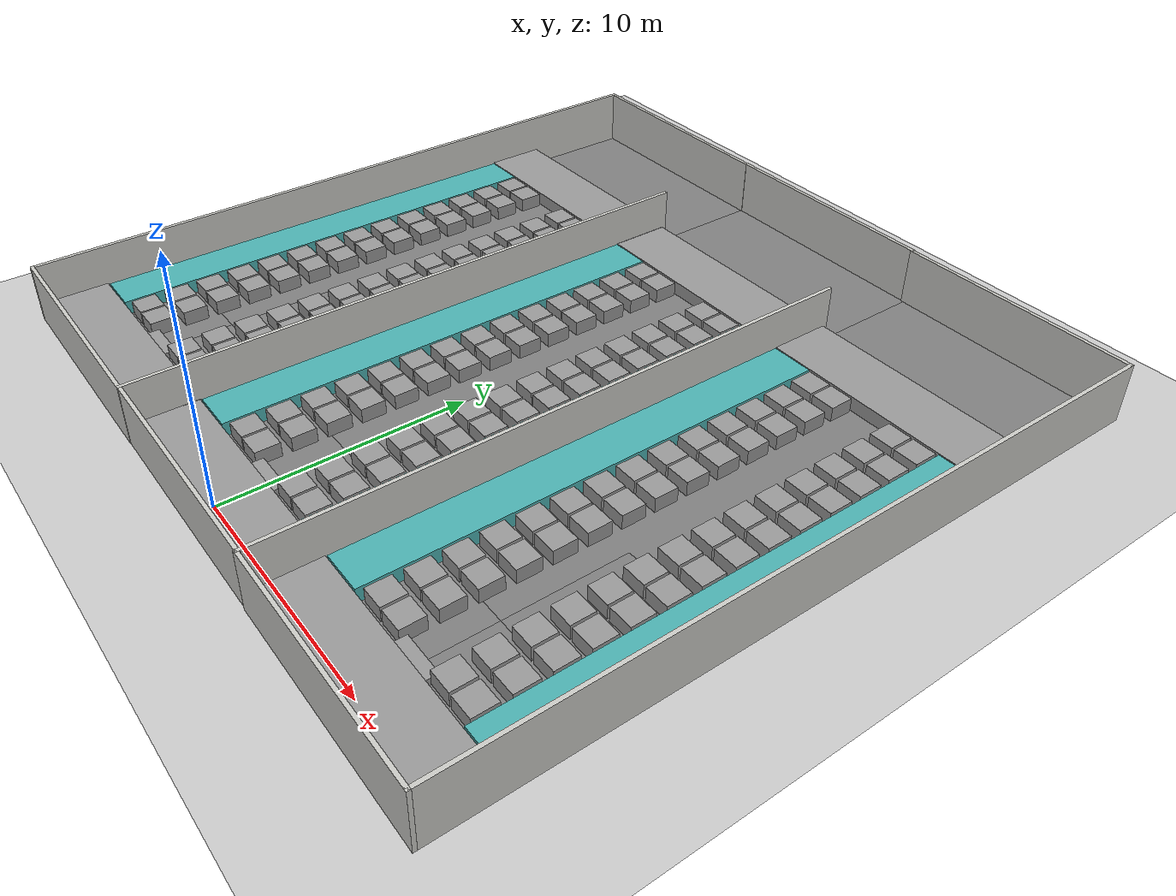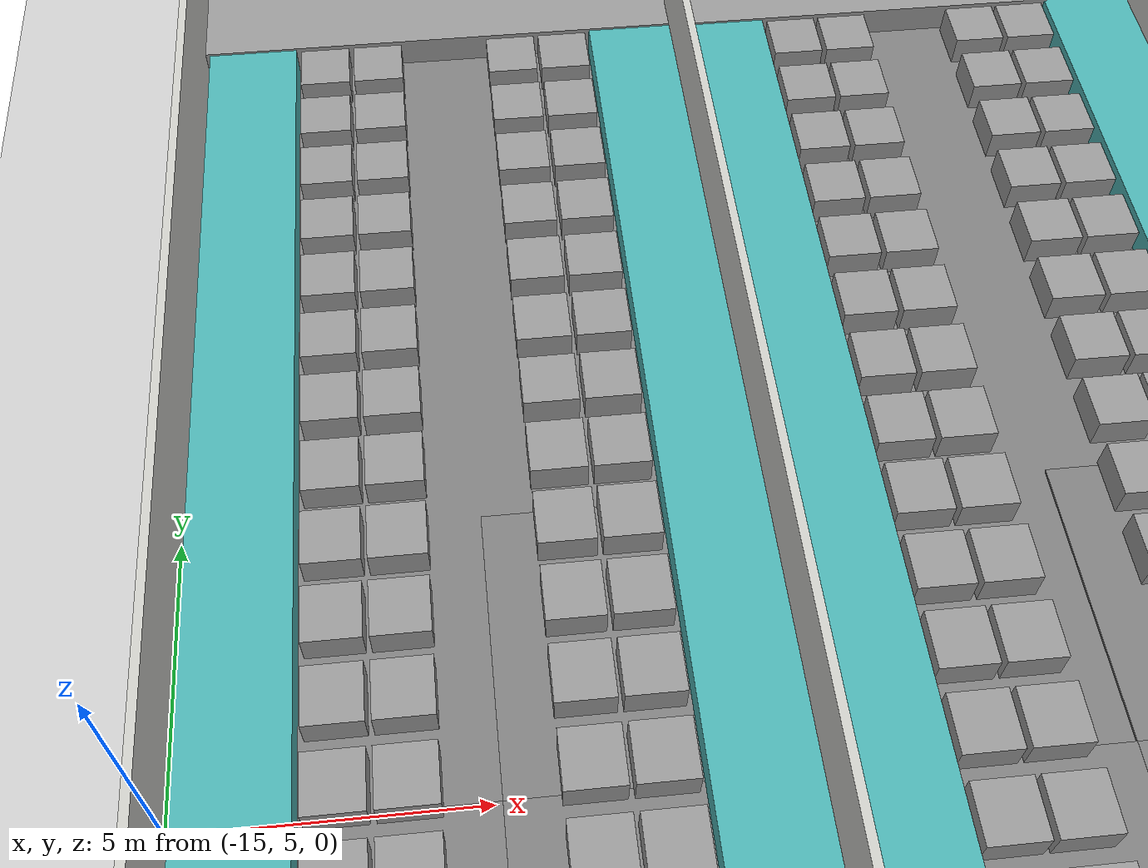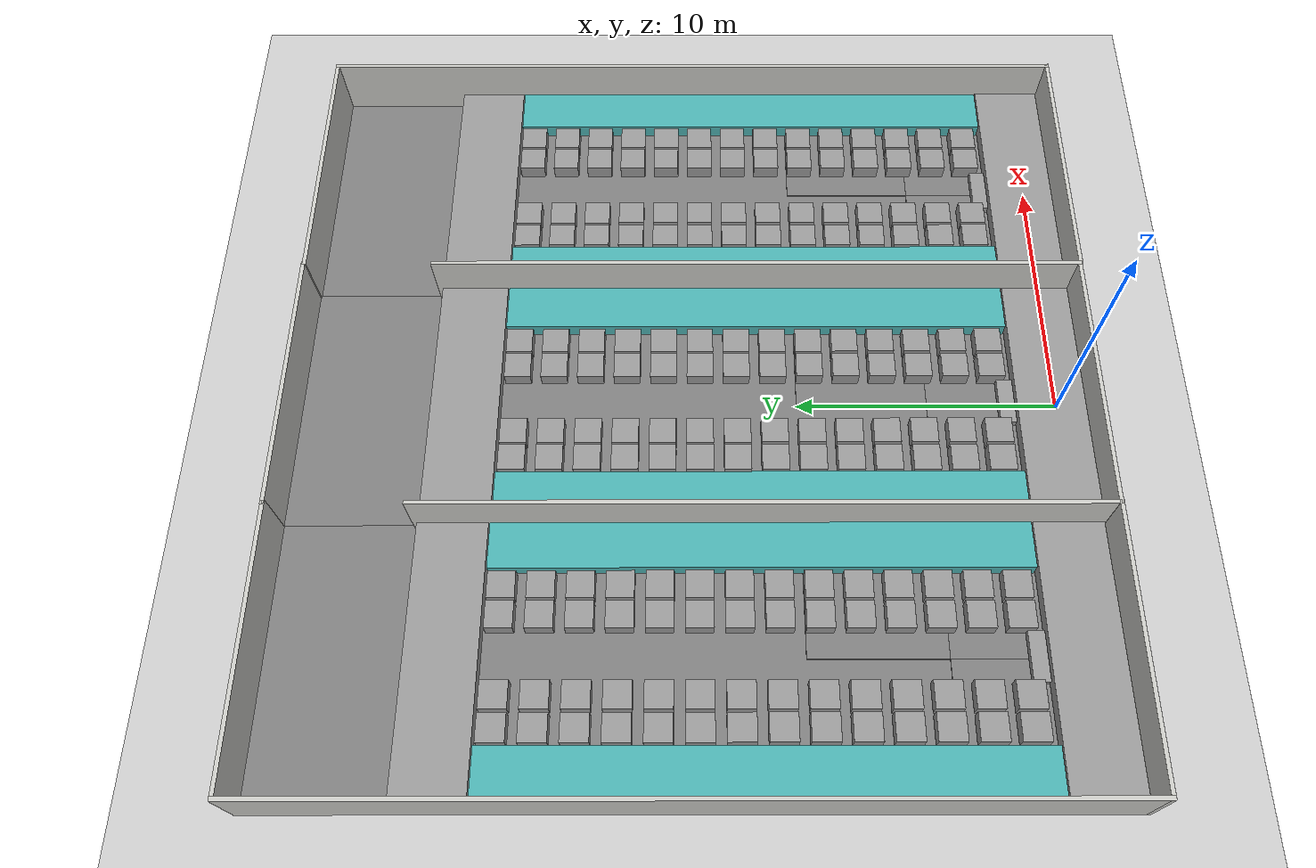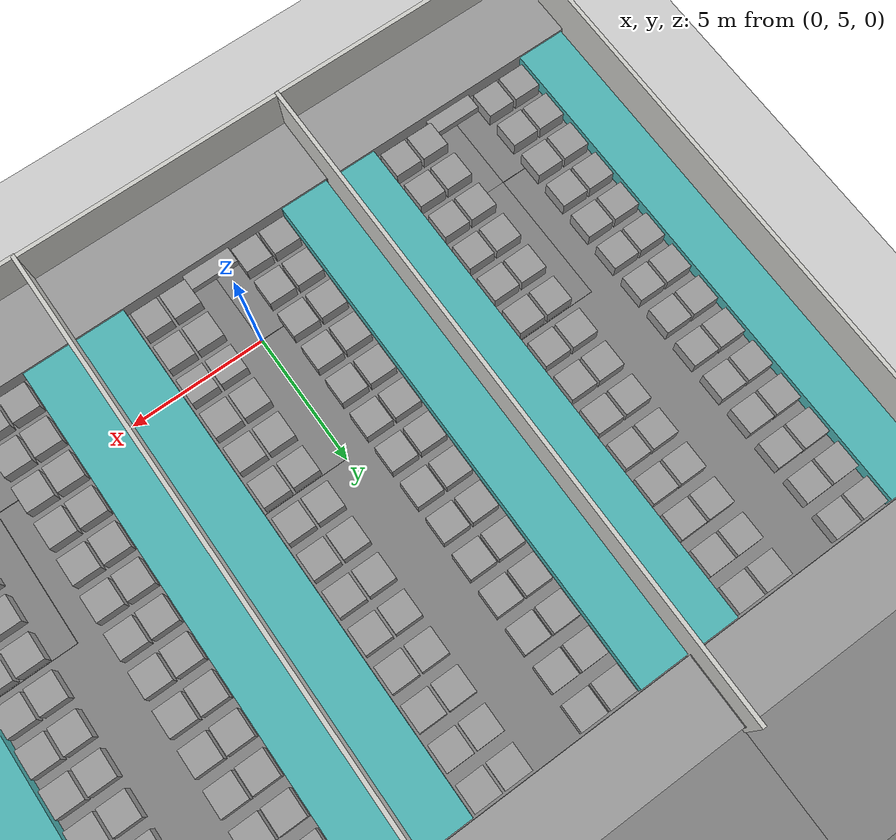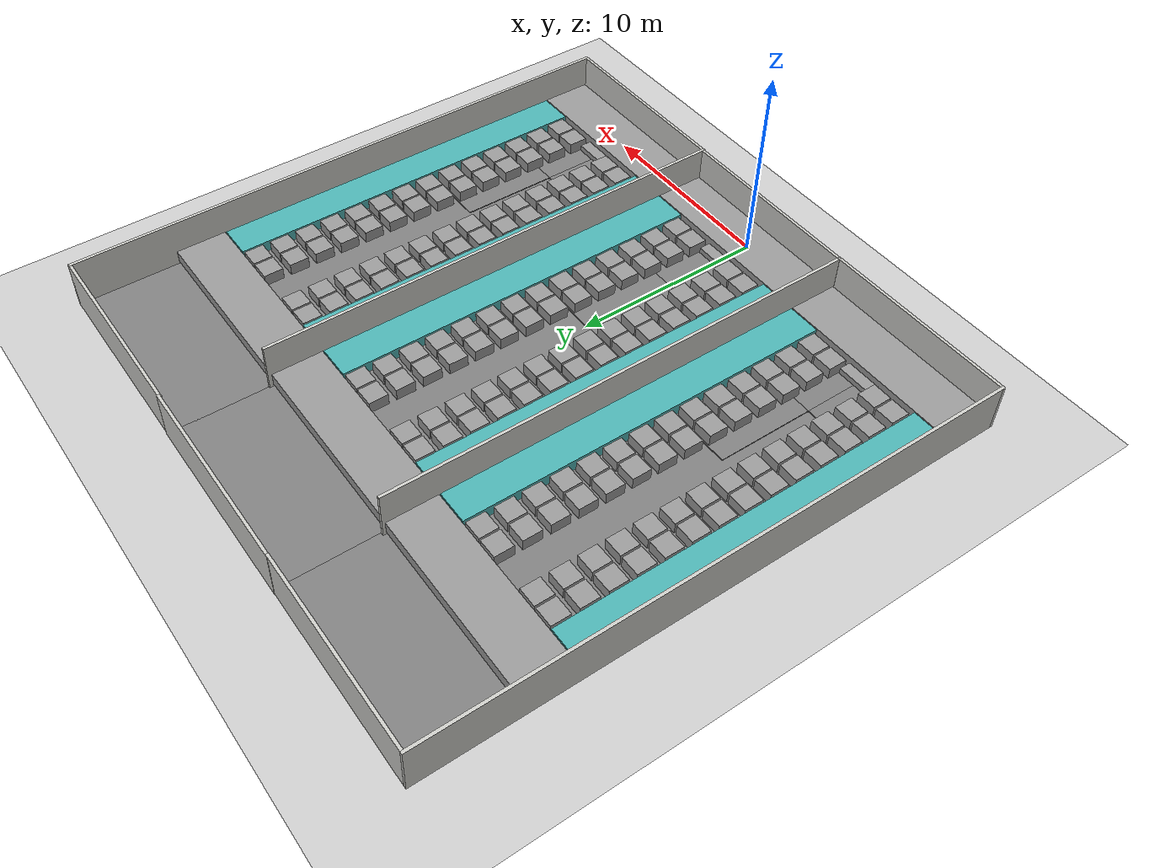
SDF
<sdf version="1.6">
 <world name="default">
  <light name="sun" type="directional">
   <pose>0 0 10 0 -0 0</pose>
   <diffuse>0.8 0.8 0.8 1</diffuse>
   <specular>0.2 0.2 0.2 1</specular>
   <attenuation>
    <range>1000</range>
    <constant>0.9</constant>
    <linear>0.01</linear>
    <quadratic>0.001</quadratic>
   </attenuation>
   <direction>-0.5 0.1 -0.9</direction>
  </light>
  <model name="ground_plane">
   <static>1</static>
   <link name="link">
    <collision name="collision">
     <geometry><plane><normal>0 0 1</normal><size>100 100</size></plane></geometry>
     <surface>
      <contact><collide_bitmask>65535</collide_bitmask></contact>
      <friction><ode><mu>100</mu><mu2>50</mu2></ode></friction>
     </surface>
    </collision>
    <visual name="visual">
     <cast_shadows>0</cast_shadows>
     <geometry><plane><normal>0 0 1</normal><size>100 100</size></plane></geometry>
     <material>
      <script><uri>file://media/materials/scripts/gazebo.material</uri><name>Gazebo/Grey</name></script>
     </material>
    </visual>
   </link>
  </model>
  <gravity>0 0 -9.8</gravity>
  <magnetic_field>6e-06 2.3e-05 -4.2e-05</magnetic_field>
  <atmosphere type="adiabatic"/>
  <physics name="default_physics" default="0" type="ode">
   <max_step_size>0.001</max_step_size>
   <real_time_factor>1</real_time_factor>
   <real_time_update_rate>1000</real_time_update_rate>
  </physics>
  <scene><ambient>0.4 0.4 0.4 1</ambient><background>0.7 0.7 0.7 1</background><shadows>1</shadows></scene>
  <audio><device>default</device></audio>
  <spherical_coordinates>
   <surface_model>EARTH_WGS84</surface_model>
   <latitude_deg>0</latitude_deg>
   <longitude_deg>0</longitude_deg>
   <elevation>0</elevation>
   <heading_deg>0</heading_deg>
  </spherical_coordinates>
  <model name="Estufa-objetos">
   <link name="link">
    <inertial>
     <mass>1</mass>
     <pose>0 0.13 0 0 -0 0</pose>
     <inertia><ixx>1</ixx><ixy>0</ixy><ixz>0</ixz><iyy>1</iyy><iyz>0</iyz><izz>1</izz></inertia>
    </inertial>
    <visual name="visual_1">
     <pose>0 9 0 0 -0 0</pose>
     <cast_shadows>0</cast_shadows>
     <geometry><box><size>10 30 0.1</size></box></geometry>
     <material>
      <script>
       <uri>model://mud_box/materials/scripts</uri>
       <uri>model://mud_box/materials/textures</uri>
       <name>vrc/mud</name>
      </script>
      <shader type="vertex"><normal_map>__default__</normal_map></shader>
      <ambient>0.5 0.5 0.5 1</ambient>
      <diffuse>0.5 0.5 0.5 1</diffuse>
      <specular>0.2 0.2 0.2 1</specular>
      <emissive>0 0 0 1</emissive>
     </material>
    </visual>
    <visual name="visual_2">
     <pose>2 2.5 0 0 -0 0</pose>
     <cast_shadows>0</cast_shadows>
     <geometry><box><size>4 5 0.2</size></box></geometry>
     <material>
      <script>
       <uri>model://mud_box/materials/scripts</uri>
       <uri>model://mud_box/materials/textures</uri>
       <name>vrc/mud</name>
      </script>
      <shader type="vertex"><normal_map>__default__</normal_map></shader>
      <ambient>0.5 0.5 0.5 1</ambient>
      <diffuse>0.5 0.5 0.5 1</diffuse>
      <specular>0.2 0.2 0.2 1</specular>
      <emissive>0 0 0 1</emissive>
     </material>
    </visual>
    <visual name="visual_3">
     <pose>2 -2.5 0 0 -0 0</pose>
     <cast_shadows>0</cast_shadows>
     <geometry><box><size>4 5 0.2</size></box></geometry>
     <material>
      <script>
       <uri>model://mud_box/materials/scripts</uri>
       <uri>model://mud_box/materials/textures</uri>
       <name>vrc/mud</name>
      </script>
      <shader type="vertex"><normal_map>__default__</normal_map></shader>
      <ambient>0.5 0.5 0.5 1</ambient>
      <diffuse>0.5 0.5 0.5 1</diffuse>
      <specular>0.2 0.2 0.2 1</specular>
      <emissive>0 0 0 1</emissive>
     </material>
    </visual>
    <visual name="visual_4">
     <pose>-2 -2.5 0 0 -0 0</pose>
     <cast_shadows>0</cast_shadows>
     <geometry><box><size>4 5 0.2</size></box></geometry>
     <material>
      <script>
       <uri>model://mud_box/materials/scripts</uri>
       <uri>model://mud_box/materials/textures</uri>
       <name>vrc/mud</name>
      </script>
      <shader type="vertex"><normal_map>__default__</normal_map></shader>
      <ambient>0.5 0.5 0.5 1</ambient>
      <diffuse>0.5 0.5 0.5 1</diffuse>
      <specular>0.2 0.2 0.2 1</specular>
      <emissive>0 0 0 1</emissive>
     </material>
    </visual>
    <collision name="collision">
     <pose>0 9 0 0 -0 0</pose>
     <geometry><box><size>10 30 0.1</size></box></geometry>
     <surface>
      <friction>
       <ode><mu>1</mu><mu2>1</mu2><fdir1>0 0 0</fdir1><slip1>0</slip1><slip2>0</slip2></ode>
       <torsional>
        <coefficient>1</coefficient>
        <patch_radius>0</patch_radius>
        <surface_radius>0</surface_radius>
        <use_patch_radius>1</use_patch_radius>
        <ode><slip>0</slip></ode>
       </torsional>
      </friction>
      <bounce><restitution_coefficient>0</restitution_coefficient><threshold>1e+06</threshold></bounce>
      <contact>
       <collide_without_contact>0</collide_without_contact>
       <collide_without_contact_bitmask>1</collide_without_contact_bitmask>
       <collide_bitmask>1</collide_bitmask>
       <ode>
        <soft_cfm>0</soft_cfm>
        <soft_erp>0.2</soft_erp>
        <kp>1e+13</kp>
        <kd>1</kd>
        <max_vel>0.01</max_vel>
        <min_depth>0</min_depth>
       </ode>
       <bullet>
        <split_impulse>1</split_impulse>
        <split_impulse_penetration_threshold>-0.01</split_impulse_penetration_threshold>
        <soft_cfm>0</soft_cfm>
        <soft_erp>0.2</soft_erp>
        <kp>1e+13</kp>
        <kd>1</kd>
       </bullet>
      </contact>
     </surface>
    </collision>
   </link>
   <link name="link_0_clone">
    <inertial>
     <mass>1</mass>
     <inertia>
      <ixx>0.166667</ixx>
      <ixy>0</ixy>
      <ixz>0</ixz>
      <iyy>0.166667</iyy>
      <iyz>0</iyz>
      <izz>0.166667</izz>
     </inertia>
    </inertial>
    <pose>2.5 -2.5 0.5 0 -0 0</pose>
    <visual name="visual">
     <geometry><box><size>1 1 0.6</size></box></geometry>
     <material>
      <lighting>1</lighting>
      <script><uri>file://media/materials/scripts/gazebo.material</uri><name>Gazebo/Grey</name></script>
      <shader type="vertex"><normal_map>__default__</normal_map></shader>
      <ambient>0.3 0.3 0.3 1</ambient>
      <diffuse>0.7 0.7 0.7 1</diffuse>
      <specular>0.01 0.01 0.01 1</specular>
      <emissive>0 0 0 1</emissive>
     </material>
    </visual>
    <collision name="collision">
     <geometry><box><size>1 1 0.6</size></box></geometry>
     <surface>
      <friction>
       <ode><mu>1</mu><mu2>1</mu2><fdir1>0 0 0</fdir1><slip1>0</slip1><slip2>0</slip2></ode>
       <torsional>
        <coefficient>1</coefficient>
        <patch_radius>0</patch_radius>
        <surface_radius>0</surface_radius>
        <use_patch_radius>1</use_patch_radius>
        <ode><slip>0</slip></ode>
       </torsional>
      </friction>
      <bounce><restitution_coefficient>0</restitution_coefficient><threshold>1e+06</threshold></bounce>
      <contact>
       <collide_without_contact>0</collide_without_contact>
       <collide_without_contact_bitmask>1</collide_without_contact_bitmask>
       <collide_bitmask>1</collide_bitmask>
       <ode>
        <soft_cfm>0</soft_cfm>
        <soft_erp>0.2</soft_erp>
        <kp>1e+13</kp>
        <kd>1</kd>
        <max_vel>0.01</max_vel>
        <min_depth>0</min_depth>
       </ode>
       <bullet>
        <split_impulse>1</split_impulse>
        <split_impulse_penetration_threshold>-0.01</split_impulse_penetration_threshold>
        <soft_cfm>0</soft_cfm>
        <soft_erp>0.2</soft_erp>
        <kp>1e+13</kp>
        <kd>1</kd>
       </bullet>
      </contact>
     </surface>
    </collision>
   </link>
   <link name="link_0_clone_0">
    <inertial>
     <mass>1</mass>
     <inertia>
      <ixx>0.166667</ixx>
      <ixy>0</ixy>
      <ixz>0</ixz>
      <iyy>0.166667</iyy>
      <iyz>0</iyz>
      <izz>0.166667</izz>
     </inertia>
    </inertial>
    <pose>-1.4 -2.5 0.5 0 -0 0</pose>
    <visual name="visual">
     <geometry><box><size>1 1 0.6</size></box></geometry>
     <material>
      <lighting>1</lighting>
      <script><uri>file://media/materials/scripts/gazebo.material</uri><name>Gazebo/Grey</name></script>
      <shader type="vertex"><normal_map>__default__</normal_map></shader>
      <ambient>0.3 0.3 0.3 1</ambient>
      <diffuse>0.7 0.7 0.7 1</diffuse>
      <specular>0.01 0.01 0.01 1</specular>
      <emissive>0 0 0 1</emissive>
     </material>
    </visual>
    <collision name="collision">
     <geometry><box><size>1 1 0.6</size></box></geometry>
     <surface>
      <friction>
       <ode><mu>1</mu><mu2>1</mu2><fdir1>0 0 0</fdir1><slip1>0</slip1><slip2>0</slip2></ode>
       <torsional>
        <coefficient>1</coefficient>
        <patch_radius>0</patch_radius>
        <surface_radius>0</surface_radius>
        <use_patch_radius>1</use_patch_radius>
        <ode><slip>0</slip></ode>
       </torsional>
      </friction>
      <bounce><restitution_coefficient>0</restitution_coefficient><threshold>1e+06</threshold></bounce>
      <contact>
       <collide_without_contact>0</collide_without_contact>
       <collide_without_contact_bitmask>1</collide_without_contact_bitmask>
       <collide_bitmask>1</collide_bitmask>
       <ode>
        <soft_cfm>0</soft_cfm>
        <soft_erp>0.2</soft_erp>
        <kp>1e+13</kp>
        <kd>1</kd>
        <max_vel>0.01</max_vel>
        <min_depth>0</min_depth>
       </ode>
       <bullet>
        <split_impulse>1</split_impulse>
        <split_impulse_penetration_threshold>-0.01</split_impulse_penetration_threshold>
        <soft_cfm>0</soft_cfm>
        <soft_erp>0.2</soft_erp>
        <kp>1e+13</kp>
        <kd>1</kd>
       </bullet>
      </contact>
     </surface>
    </collision>
   </link>
   <link name="link_0_clone_0_clone">
    <inertial>
     <mass>1</mass>
     <inertia>
      <ixx>0.166667</ixx>
      <ixy>0</ixy>
      <ixz>0</ixz>
      <iyy>0.166667</iyy>
      <iyz>0</iyz>
      <izz>0.166667</izz>
     </inertia>
    </inertial>
    <pose>0 -3 0.3 0 -0 0</pose>
    <visual name="visual">
     <geometry><box><size>1.8 0.6 0.3</size></box></geometry>
     <material>
      <lighting>1</lighting>
      <script><uri>file://media/materials/scripts/gazebo.material</uri><name>Gazebo/Grey</name></script>
      <shader type="vertex"><normal_map>__default__</normal_map></shader>
      <ambient>0.3 0.3 0.3 1</ambient>
      <diffuse>0.7 0.7 0.7 1</diffuse>
      <specular>0.01 0.01 0.01 1</specular>
      <emissive>0 0 0 1</emissive>
     </material>
    </visual>
    <collision name="collision">
     <geometry><box><size>1.8 0.6 0.3</size></box></geometry>
     <surface>
      <friction>
       <ode><mu>1</mu><mu2>1</mu2><fdir1>0 0 0</fdir1><slip1>0</slip1><slip2>0</slip2></ode>
       <torsional>
        <coefficient>1</coefficient>
        <patch_radius>0</patch_radius>
        <surface_radius>0</surface_radius>
        <use_patch_radius>1</use_patch_radius>
        <ode><slip>0</slip></ode>
       </torsional>
      </friction>
      <bounce><restitution_coefficient>0</restitution_coefficient><threshold>1e+06</threshold></bounce>
      <contact>
       <collide_without_contact>0</collide_without_contact>
       <collide_without_contact_bitmask>1</collide_without_contact_bitmask>
       <collide_bitmask>1</collide_bitmask>
       <ode>
        <soft_cfm>0</soft_cfm>
        <soft_erp>0.2</soft_erp>
        <kp>1e+13</kp>
        <kd>1</kd>
        <max_vel>0.01</max_vel>
        <min_depth>0</min_depth>
       </ode>
       <bullet>
        <split_impulse>1</split_impulse>
        <split_impulse_penetration_threshold>-0.01</split_impulse_penetration_threshold>
        <soft_cfm>0</soft_cfm>
        <soft_erp>0.2</soft_erp>
        <kp>1e+13</kp>
        <kd>1</kd>
       </bullet>
      </contact>
     </surface>
    </collision>
   </link>
   <link name="link_0_clone_1">
    <inertial>
     <mass>1</mass>
     <inertia>
      <ixx>0.166667</ixx>
      <ixy>0</ixy>
      <ixz>0</ixz>
      <iyy>0.166667</iyy>
      <iyz>0</iyz>
      <izz>0.166667</izz>
     </inertia>
    </inertial>
    <pose>-2.5 -2.5 0.5 0 -0 0</pose>
    <visual name="visual">
     <geometry><box><size>1 1 0.6</size></box></geometry>
     <material>
      <lighting>1</lighting>
      <script><uri>file://media/materials/scripts/gazebo.material</uri><name>Gazebo/Grey</name></script>
      <shader type="vertex"><normal_map>__default__</normal_map></shader>
      <ambient>0.3 0.3 0.3 1</ambient>
      <diffuse>0.7 0.7 0.7 1</diffuse>
      <specular>0.01 0.01 0.01 1</specular>
      <emissive>0 0 0 1</emissive>
     </material>
    </visual>
    <collision name="collision">
     <geometry><box><size>1 1 0.6</size></box></geometry>
     <surface>
      <friction>
       <ode><mu>1</mu><mu2>1</mu2><fdir1>0 0 0</fdir1><slip1>0</slip1><slip2>0</slip2></ode>
       <torsional>
        <coefficient>1</coefficient>
        <patch_radius>0</patch_radius>
        <surface_radius>0</surface_radius>
        <use_patch_radius>1</use_patch_radius>
        <ode><slip>0</slip></ode>
       </torsional>
      </friction>
      <bounce><restitution_coefficient>0</restitution_coefficient><threshold>1e+06</threshold></bounce>
      <contact>
       <collide_without_contact>0</collide_without_contact>
       <collide_without_contact_bitmask>1</collide_without_contact_bitmask>
       <collide_bitmask>1</collide_bitmask>
       <ode>
        <soft_cfm>0</soft_cfm>
        <soft_erp>0.2</soft_erp>
        <kp>1e+13</kp>
        <kd>1</kd>
        <max_vel>0.01</max_vel>
        <min_depth>0</min_depth>
       </ode>
       <bullet>
        <split_impulse>1</split_impulse>
        <split_impulse_penetration_threshold>-0.01</split_impulse_penetration_threshold>
        <soft_cfm>0</soft_cfm>
        <soft_erp>0.2</soft_erp>
        <kp>1e+13</kp>
        <kd>1</kd>
       </bullet>
      </contact>
     </surface>
    </collision>
   </link>
   <link name="link_0_clone_3_clone">
    <inertial>
     <mass>1</mass>
     <inertia>
      <ixx>0.166667</ixx>
      <ixy>0</ixy>
      <ixz>0</ixz>
      <iyy>0.166667</iyy>
      <iyz>0</iyz>
      <izz>0.166667</izz>
     </inertia>
    </inertial>
    <pose>-4 6.5 0.5 0 -0 0</pose>
    <visual name="visual">
     <geometry><box><size>1.8 19.5 0.6</size></box></geometry>
     <material>
      <lighting>1</lighting>
      <script><uri>file://media/materials/scripts/gazebo.material</uri><name>Gazebo/Grey</name></script>
      <shader type="vertex"><normal_map>__default__</normal_map></shader>
      <ambient>0.3 0.7 0.7 1</ambient>
      <diffuse>0.7 0.7 0.7 1</diffuse>
      <specular>0.01 0.01 0.01 1</specular>
      <emissive>0 0 0 1</emissive>
     </material>
    </visual>
    <collision name="collision">
     <geometry><box><size>1.8 19.5 0.6</size></box></geometry>
     <surface>
      <friction>
       <ode><mu>1</mu><mu2>1</mu2><fdir1>0 0 0</fdir1><slip1>0</slip1><slip2>0</slip2></ode>
       <torsional>
        <coefficient>1</coefficient>
        <patch_radius>0</patch_radius>
        <surface_radius>0</surface_radius>
        <use_patch_radius>1</use_patch_radius>
        <ode><slip>0</slip></ode>
       </torsional>
      </friction>
      <bounce><restitution_coefficient>0</restitution_coefficient><threshold>1e+06</threshold></bounce>
      <contact>
       <collide_without_contact>0</collide_without_contact>
       <collide_without_contact_bitmask>1</collide_without_contact_bitmask>
       <collide_bitmask>1</collide_bitmask>
       <ode>
        <soft_cfm>0</soft_cfm>
        <soft_erp>0.2</soft_erp>
        <kp>1e+13</kp>
        <kd>1</kd>
        <max_vel>0.01</max_vel>
        <min_depth>0</min_depth>
       </ode>
       <bullet>
        <split_impulse>1</split_impulse>
        <split_impulse_penetration_threshold>-0.01</split_impulse_penetration_threshold>
        <soft_cfm>0</soft_cfm>
        <soft_erp>0.2</soft_erp>
        <kp>1e+13</kp>
        <kd>1</kd>
       </bullet>
      </contact>
     </surface>
    </collision>
   </link>
   <link name="link_0_clone_3_clone_clone">
    <inertial>
     <mass>1</mass>
     <inertia>
      <ixx>0.166667</ixx>
      <ixy>0</ixy>
      <ixz>0</ixz>
      <iyy>0.166667</iyy>
      <iyz>0</iyz>
      <izz>0.166667</izz>
     </inertia>
    </inertial>
    <pose>4 6.5 0.5 0 -0 0</pose>
    <visual name="visual">
     <geometry><box><size>1.8 19.5 0.6</size></box></geometry>
     <material>
      <lighting>1</lighting>
      <script><uri>file://media/materials/scripts/gazebo.material</uri><name>Gazebo/Grey</name></script>
      <shader type="vertex"><normal_map>__default__</normal_map></shader>
      <ambient>0.3 0.7 0.7 1</ambient>
      <diffuse>0.7 0.7 0.7 1</diffuse>
      <specular>0.01 0.01 0.01 1</specular>
      <emissive>0 0 0 1</emissive>
     </material>
    </visual>
    <collision name="collision">
     <geometry><box><size>1.8 19.5 0.6</size></box></geometry>
     <surface>
      <friction>
       <ode><mu>1</mu><mu2>1</mu2><fdir1>0 0 0</fdir1><slip1>0</slip1><slip2>0</slip2></ode>
       <torsional>
        <coefficient>1</coefficient>
        <patch_radius>0</patch_radius>
        <surface_radius>0</surface_radius>
        <use_patch_radius>1</use_patch_radius>
        <ode><slip>0</slip></ode>
       </torsional>
      </friction>
      <bounce><restitution_coefficient>0</restitution_coefficient><threshold>1e+06</threshold></bounce>
      <contact>
       <collide_without_contact>0</collide_without_contact>
       <collide_without_contact_bitmask>1</collide_without_contact_bitmask>
       <collide_bitmask>1</collide_bitmask>
       <ode>
        <soft_cfm>0</soft_cfm>
        <soft_erp>0.2</soft_erp>
        <kp>1e+13</kp>
        <kd>1</kd>
        <max_vel>0.01</max_vel>
        <min_depth>0</min_depth>
       </ode>
       <bullet>
        <split_impulse>1</split_impulse>
        <split_impulse_penetration_threshold>-0.01</split_impulse_penetration_threshold>
        <soft_cfm>0</soft_cfm>
        <soft_erp>0.2</soft_erp>
        <kp>1e+13</kp>
        <kd>1</kd>
       </bullet>
      </contact>
     </surface>
    </collision>
   </link>
   <link name="link_0_clone_clone">
    <inertial>
     <mass>1</mass>
     <inertia>
      <ixx>0.166667</ixx>
      <ixy>0</ixy>
      <ixz>0</ixz>
      <iyy>0.166667</iyy>
      <iyz>0</iyz>
      <izz>0.166667</izz>
     </inertia>
    </inertial>
    <pose>2.5 -1.1 0.5 0 -0 0</pose>
    <visual name="visual">
     <geometry><box><size>1 1 0.6</size></box></geometry>
     <material>
      <lighting>1</lighting>
      <script><uri>file://media/materials/scripts/gazebo.material</uri><name>Gazebo/Grey</name></script>
      <shader type="vertex"><normal_map>__default__</normal_map></shader>
      <ambient>0.3 0.3 0.3 1</ambient>
      <diffuse>0.7 0.7 0.7 1</diffuse>
      <specular>0.01 0.01 0.01 1</specular>
      <emissive>0 0 0 1</emissive>
     </material>
    </visual>
    <collision name="collision">
     <geometry><box><size>1 1 0.6</size></box></geometry>
     <surface>
      <friction>
       <ode><mu>1</mu><mu2>1</mu2><fdir1>0 0 0</fdir1><slip1>0</slip1><slip2>0</slip2></ode>
       <torsional>
        <coefficient>1</coefficient>
        <patch_radius>0</patch_radius>
        <surface_radius>0</surface_radius>
        <use_patch_radius>1</use_patch_radius>
        <ode><slip>0</slip></ode>
       </torsional>
      </friction>
      <bounce><restitution_coefficient>0</restitution_coefficient><threshold>1e+06</threshold></bounce>
      <contact>
       <collide_without_contact>0</collide_without_contact>
       <collide_without_contact_bitmask>1</collide_without_contact_bitmask>
       <collide_bitmask>1</collide_bitmask>
       <ode>
        <soft_cfm>0</soft_cfm>
        <soft_erp>0.2</soft_erp>
        <kp>1e+13</kp>
        <kd>1</kd>
        <max_vel>0.01</max_vel>
        <min_depth>0</min_depth>
       </ode>
       <bullet>
        <split_impulse>1</split_impulse>
        <split_impulse_penetration_threshold>-0.01</split_impulse_penetration_threshold>
        <soft_cfm>0</soft_cfm>
        <soft_erp>0.2</soft_erp>
        <kp>1e+13</kp>
        <kd>1</kd>
       </bullet>
      </contact>
     </surface>
    </collision>
   </link>
   <link name="link_0_clone_clone_0">
    <inertial>
     <mass>1</mass>
     <inertia>
      <ixx>0.166667</ixx>
      <ixy>0</ixy>
      <ixz>0</ixz>
      <iyy>0.166667</iyy>
      <iyz>0</iyz>
      <izz>0.166667</izz>
     </inertia>
    </inertial>
    <pose>1.4 -1.1 0.5 0 -0 0</pose>
    <visual name="visual">
     <geometry><box><size>1 1 0.6</size></box></geometry>
     <material>
      <lighting>1</lighting>
      <script><uri>file://media/materials/scripts/gazebo.material</uri><name>Gazebo/Grey</name></script>
      <shader type="vertex"><normal_map>__default__</normal_map></shader>
      <ambient>0.3 0.3 0.3 1</ambient>
      <diffuse>0.7 0.7 0.7 1</diffuse>
      <specular>0.01 0.01 0.01 1</specular>
      <emissive>0 0 0 1</emissive>
     </material>
    </visual>
    <collision name="collision">
     <geometry><box><size>1 1 0.6</size></box></geometry>
     <surface>
      <friction>
       <ode><mu>1</mu><mu2>1</mu2><fdir1>0 0 0</fdir1><slip1>0</slip1><slip2>0</slip2></ode>
       <torsional>
        <coefficient>1</coefficient>
        <patch_radius>0</patch_radius>
        <surface_radius>0</surface_radius>
        <use_patch_radius>1</use_patch_radius>
        <ode><slip>0</slip></ode>
       </torsional>
      </friction>
      <bounce><restitution_coefficient>0</restitution_coefficient><threshold>1e+06</threshold></bounce>
      <contact>
       <collide_without_contact>0</collide_without_contact>
       <collide_without_contact_bitmask>1</collide_without_contact_bitmask>
       <collide_bitmask>1</collide_bitmask>
       <ode>
        <soft_cfm>0</soft_cfm>
        <soft_erp>0.2</soft_erp>
        <kp>1e+13</kp>
        <kd>1</kd>
        <max_vel>0.01</max_vel>
        <min_depth>0</min_depth>
       </ode>
       <bullet>
        <split_impulse>1</split_impulse>
        <split_impulse_penetration_threshold>-0.01</split_impulse_penetration_threshold>
        <soft_cfm>0</soft_cfm>
        <soft_erp>0.2</soft_erp>
        <kp>1e+13</kp>
        <kd>1</kd>
       </bullet>
      </contact>
     </surface>
    </collision>
   </link>
   <link name="link_0_clone_clone_1">
    <inertial>
     <mass>1</mass>
     <inertia>
      <ixx>0.166667</ixx>
      <ixy>0</ixy>
      <ixz>0</ixz>
      <iyy>0.166667</iyy>
      <iyz>0</iyz>
      <izz>0.166667</izz>
     </inertia>
    </inertial>
    <pose>-1.4 -1.1 0.5 0 -0 0</pose>
    <visual name="visual">
     <geometry><box><size>1 1 0.6</size></box></geometry>
     <material>
      <lighting>1</lighting>
      <script><uri>file://media/materials/scripts/gazebo.material</uri><name>Gazebo/Grey</name></script>
      <shader type="vertex"><normal_map>__default__</normal_map></shader>
      <ambient>0.3 0.3 0.3 1</ambient>
      <diffuse>0.7 0.7 0.7 1</diffuse>
      <specular>0.01 0.01 0.01 1</specular>
      <emissive>0 0 0 1</emissive>
     </material>
    </visual>
    <collision name="collision">
     <geometry><box><size>1 1 0.6</size></box></geometry>
     <surface>
      <friction>
       <ode><mu>1</mu><mu2>1</mu2><fdir1>0 0 0</fdir1><slip1>0</slip1><slip2>0</slip2></ode>
       <torsional>
        <coefficient>1</coefficient>
        <patch_radius>0</patch_radius>
        <surface_radius>0</surface_radius>
        <use_patch_radius>1</use_patch_radius>
        <ode><slip>0</slip></ode>
       </torsional>
      </friction>
      <bounce><restitution_coefficient>0</restitution_coefficient><threshold>1e+06</threshold></bounce>
      <contact>
       <collide_without_contact>0</collide_without_contact>
       <collide_without_contact_bitmask>1</collide_without_contact_bitmask>
       <collide_bitmask>1</collide_bitmask>
       <ode>
        <soft_cfm>0</soft_cfm>
        <soft_erp>0.2</soft_erp>
        <kp>1e+13</kp>
        <kd>1</kd>
        <max_vel>0.01</max_vel>
        <min_depth>0</min_depth>
       </ode>
       <bullet>
        <split_impulse>1</split_impulse>
        <split_impulse_penetration_threshold>-0.01</split_impulse_penetration_threshold>
        <soft_cfm>0</soft_cfm>
        <soft_erp>0.2</soft_erp>
        <kp>1e+13</kp>
        <kd>1</kd>
       </bullet>
      </contact>
     </surface>
    </collision>
   </link>
   <link name="link_0_clone_clone_10">
    <inertial>
     <mass>1</mass>
     <inertia>
      <ixx>0.166667</ixx>
      <ixy>0</ixy>
      <ixz>0</ixz>
      <iyy>0.166667</iyy>
      <iyz>0</iyz>
      <izz>0.166667</izz>
     </inertia>
    </inertial>
    <pose>-1.4 1.7 0.5 0 -0 0</pose>
    <visual name="visual">
     <geometry><box><size>1 1 0.6</size></box></geometry>
     <material>
      <lighting>1</lighting>
      <script><uri>file://media/materials/scripts/gazebo.material</uri><name>Gazebo/Grey</name></script>
      <shader type="vertex"><normal_map>__default__</normal_map></shader>
      <ambient>0.3 0.3 0.3 1</ambient>
      <diffuse>0.7 0.7 0.7 1</diffuse>
      <specular>0.01 0.01 0.01 1</specular>
      <emissive>0 0 0 1</emissive>
     </material>
    </visual>
    <collision name="collision">
     <geometry><box><size>1 1 0.6</size></box></geometry>
     <surface>
      <friction>
       <ode><mu>1</mu><mu2>1</mu2><fdir1>0 0 0</fdir1><slip1>0</slip1><slip2>0</slip2></ode>
       <torsional>
        <coefficient>1</coefficient>
        <patch_radius>0</patch_radius>
        <surface_radius>0</surface_radius>
        <use_patch_radius>1</use_patch_radius>
        <ode><slip>0</slip></ode>
       </torsional>
      </friction>
      <bounce><restitution_coefficient>0</restitution_coefficient><threshold>1e+06</threshold></bounce>
      <contact>
       <collide_without_contact>0</collide_without_contact>
       <collide_without_contact_bitmask>1</collide_without_contact_bitmask>
       <collide_bitmask>1</collide_bitmask>
       <ode>
        <soft_cfm>0</soft_cfm>
        <soft_erp>0.2</soft_erp>
        <kp>1e+13</kp>
        <kd>1</kd>
        <max_vel>0.01</max_vel>
        <min_depth>0</min_depth>
       </ode>
       <bullet>
        <split_impulse>1</split_impulse>
        <split_impulse_penetration_threshold>-0.01</split_impulse_penetration_threshold>
        <soft_cfm>0</soft_cfm>
        <soft_erp>0.2</soft_erp>
        <kp>1e+13</kp>
        <kd>1</kd>
       </bullet>
      </contact>
     </surface>
    </collision>
   </link>
   <link name="link_0_clone_clone_11">
    <inertial>
     <mass>1</mass>
     <inertia>
      <ixx>0.166667</ixx>
      <ixy>0</ixy>
      <ixz>0</ixz>
      <iyy>0.166667</iyy>
      <iyz>0</iyz>
      <izz>0.166667</izz>
     </inertia>
    </inertial>
    <pose>-2.5 1.7 0.5 0 -0 0</pose>
    <visual name="visual">
     <geometry><box><size>1 1 0.6</size></box></geometry>
     <material>
      <lighting>1</lighting>
      <script><uri>file://media/materials/scripts/gazebo.material</uri><name>Gazebo/Grey</name></script>
      <shader type="vertex"><normal_map>__default__</normal_map></shader>
      <ambient>0.3 0.3 0.3 1</ambient>
      <diffuse>0.7 0.7 0.7 1</diffuse>
      <specular>0.01 0.01 0.01 1</specular>
      <emissive>0 0 0 1</emissive>
     </material>
    </visual>
    <collision name="collision">
     <geometry><box><size>1 1 0.6</size></box></geometry>
     <surface>
      <friction>
       <ode><mu>1</mu><mu2>1</mu2><fdir1>0 0 0</fdir1><slip1>0</slip1><slip2>0</slip2></ode>
       <torsional>
        <coefficient>1</coefficient>
        <patch_radius>0</patch_radius>
        <surface_radius>0</surface_radius>
        <use_patch_radius>1</use_patch_radius>
        <ode><slip>0</slip></ode>
       </torsional>
      </friction>
      <bounce><restitution_coefficient>0</restitution_coefficient><threshold>1e+06</threshold></bounce>
      <contact>
       <collide_without_contact>0</collide_without_contact>
       <collide_without_contact_bitmask>1</collide_without_contact_bitmask>
       <collide_bitmask>1</collide_bitmask>
       <ode>
        <soft_cfm>0</soft_cfm>
        <soft_erp>0.2</soft_erp>
        <kp>1e+13</kp>
        <kd>1</kd>
        <max_vel>0.01</max_vel>
        <min_depth>0</min_depth>
       </ode>
       <bullet>
        <split_impulse>1</split_impulse>
        <split_impulse_penetration_threshold>-0.01</split_impulse_penetration_threshold>
        <soft_cfm>0</soft_cfm>
        <soft_erp>0.2</soft_erp>
        <kp>1e+13</kp>
        <kd>1</kd>
       </bullet>
      </contact>
     </surface>
    </collision>
   </link>
   <link name="link_0_clone_clone_12">
    <inertial>
     <mass>1</mass>
     <inertia>
      <ixx>0.166667</ixx>
      <ixy>0</ixy>
      <ixz>0</ixz>
      <iyy>0.166667</iyy>
      <iyz>0</iyz>
      <izz>0.166667</izz>
     </inertia>
    </inertial>
    <pose>2.5 3.1 0.5 0 -0 0</pose>
    <visual name="visual">
     <geometry><box><size>1 1 0.6</size></box></geometry>
     <material>
      <lighting>1</lighting>
      <script><uri>file://media/materials/scripts/gazebo.material</uri><name>Gazebo/Grey</name></script>
      <shader type="vertex"><normal_map>__default__</normal_map></shader>
      <ambient>0.3 0.3 0.3 1</ambient>
      <diffuse>0.7 0.7 0.7 1</diffuse>
      <specular>0.01 0.01 0.01 1</specular>
      <emissive>0 0 0 1</emissive>
     </material>
    </visual>
    <collision name="collision">
     <geometry><box><size>1 1 0.6</size></box></geometry>
     <surface>
      <friction>
       <ode><mu>1</mu><mu2>1</mu2><fdir1>0 0 0</fdir1><slip1>0</slip1><slip2>0</slip2></ode>
       <torsional>
        <coefficient>1</coefficient>
        <patch_radius>0</patch_radius>
        <surface_radius>0</surface_radius>
        <use_patch_radius>1</use_patch_radius>
        <ode><slip>0</slip></ode>
       </torsional>
      </friction>
      <bounce><restitution_coefficient>0</restitution_coefficient><threshold>1e+06</threshold></bounce>
      <contact>
       <collide_without_contact>0</collide_without_contact>
       <collide_without_contact_bitmask>1</collide_without_contact_bitmask>
       <collide_bitmask>1</collide_bitmask>
       <ode>
        <soft_cfm>0</soft_cfm>
        <soft_erp>0.2</soft_erp>
        <kp>1e+13</kp>
        <kd>1</kd>
        <max_vel>0.01</max_vel>
        <min_depth>0</min_depth>
       </ode>
       <bullet>
        <split_impulse>1</split_impulse>
        <split_impulse_penetration_threshold>-0.01</split_impulse_penetration_threshold>
        <soft_cfm>0</soft_cfm>
        <soft_erp>0.2</soft_erp>
        <kp>1e+13</kp>
        <kd>1</kd>
       </bullet>
      </contact>
     </surface>
    </collision>
   </link>
   <link name="link_0_clone_clone_13">
    <inertial>
     <mass>1</mass>
     <inertia>
      <ixx>0.166667</ixx>
      <ixy>0</ixy>
      <ixz>0</ixz>
      <iyy>0.166667</iyy>
      <iyz>0</iyz>
      <izz>0.166667</izz>
     </inertia>
    </inertial>
    <pose>1.4 3.1 0.5 0 -0 0</pose>
    <visual name="visual">
     <geometry><box><size>1 1 0.6</size></box></geometry>
     <material>
      <lighting>1</lighting>
      <script><uri>file://media/materials/scripts/gazebo.material</uri><name>Gazebo/Grey</name></script>
      <shader type="vertex"><normal_map>__default__</normal_map></shader>
      <ambient>0.3 0.3 0.3 1</ambient>
      <diffuse>0.7 0.7 0.7 1</diffuse>
      <specular>0.01 0.01 0.01 1</specular>
      <emissive>0 0 0 1</emissive>
     </material>
    </visual>
    <collision name="collision">
     <geometry><box><size>1 1 0.6</size></box></geometry>
     <surface>
      <friction>
       <ode><mu>1</mu><mu2>1</mu2><fdir1>0 0 0</fdir1><slip1>0</slip1><slip2>0</slip2></ode>
       <torsional>
        <coefficient>1</coefficient>
        <patch_radius>0</patch_radius>
        <surface_radius>0</surface_radius>
        <use_patch_radius>1</use_patch_radius>
        <ode><slip>0</slip></ode>
       </torsional>
      </friction>
      <bounce><restitution_coefficient>0</restitution_coefficient><threshold>1e+06</threshold></bounce>
      <contact>
       <collide_without_contact>0</collide_without_contact>
       <collide_without_contact_bitmask>1</collide_without_contact_bitmask>
       <collide_bitmask>1</collide_bitmask>
       <ode>
        <soft_cfm>0</soft_cfm>
        <soft_erp>0.2</soft_erp>
        <kp>1e+13</kp>
        <kd>1</kd>
        <max_vel>0.01</max_vel>
        <min_depth>0</min_depth>
       </ode>
       <bullet>
        <split_impulse>1</split_impulse>
        <split_impulse_penetration_threshold>-0.01</split_impulse_penetration_threshold>
        <soft_cfm>0</soft_cfm>
        <soft_erp>0.2</soft_erp>
        <kp>1e+13</kp>
        <kd>1</kd>
       </bullet>
      </contact>
     </surface>
    </collision>
   </link>
   <link name="link_0_clone_clone_14">
    <inertial>
     <mass>1</mass>
     <inertia>
      <ixx>0.166667</ixx>
      <ixy>0</ixy>
      <ixz>0</ixz>
      <iyy>0.166667</iyy>
      <iyz>0</iyz>
      <izz>0.166667</izz>
     </inertia>
    </inertial>
    <pose>-1.4 3.1 0.5 0 -0 0</pose>
    <visual name="visual">
     <geometry><box><size>1 1 0.6</size></box></geometry>
     <material>
      <lighting>1</lighting>
      <script><uri>file://media/materials/scripts/gazebo.material</uri><name>Gazebo/Grey</name></script>
      <shader type="vertex"><normal_map>__default__</normal_map></shader>
      <ambient>0.3 0.3 0.3 1</ambient>
      <diffuse>0.7 0.7 0.7 1</diffuse>
      <specular>0.01 0.01 0.01 1</specular>
      <emissive>0 0 0 1</emissive>
     </material>
    </visual>
    <collision name="collision">
     <geometry><box><size>1 1 0.6</size></box></geometry>
     <surface>
      <friction>
       <ode><mu>1</mu><mu2>1</mu2><fdir1>0 0 0</fdir1><slip1>0</slip1><slip2>0</slip2></ode>
       <torsional>
        <coefficient>1</coefficient>
        <patch_radius>0</patch_radius>
        <surface_radius>0</surface_radius>
        <use_patch_radius>1</use_patch_radius>
        <ode><slip>0</slip></ode>
       </torsional>
      </friction>
      <bounce><restitution_coefficient>0</restitution_coefficient><threshold>1e+06</threshold></bounce>
      <contact>
       <collide_without_contact>0</collide_without_contact>
       <collide_without_contact_bitmask>1</collide_without_contact_bitmask>
       <collide_bitmask>1</collide_bitmask>
       <ode>
        <soft_cfm>0</soft_cfm>
        <soft_erp>0.2</soft_erp>
        <kp>1e+13</kp>
        <kd>1</kd>
        <max_vel>0.01</max_vel>
        <min_depth>0</min_depth>
       </ode>
       <bullet>
        <split_impulse>1</split_impulse>
        <split_impulse_penetration_threshold>-0.01</split_impulse_penetration_threshold>
        <soft_cfm>0</soft_cfm>
        <soft_erp>0.2</soft_erp>
        <kp>1e+13</kp>
        <kd>1</kd>
       </bullet>
      </contact>
     </surface>
    </collision>
   </link>
   <link name="link_0_clone_clone_15">
    <inertial>
     <mass>1</mass>
     <inertia>
      <ixx>0.166667</ixx>
      <ixy>0</ixy>
      <ixz>0</ixz>
      <iyy>0.166667</iyy>
      <iyz>0</iyz>
      <izz>0.166667</izz>
     </inertia>
    </inertial>
    <pose>-2.5 3.1 0.5 0 -0 0</pose>
    <visual name="visual">
     <geometry><box><size>1 1 0.6</size></box></geometry>
     <material>
      <lighting>1</lighting>
      <script><uri>file://media/materials/scripts/gazebo.material</uri><name>Gazebo/Grey</name></script>
      <shader type="vertex"><normal_map>__default__</normal_map></shader>
      <ambient>0.3 0.3 0.3 1</ambient>
      <diffuse>0.7 0.7 0.7 1</diffuse>
      <specular>0.01 0.01 0.01 1</specular>
      <emissive>0 0 0 1</emissive>
     </material>
    </visual>
    <collision name="collision">
     <geometry><box><size>1 1 0.6</size></box></geometry>
     <surface>
      <friction>
       <ode><mu>1</mu><mu2>1</mu2><fdir1>0 0 0</fdir1><slip1>0</slip1><slip2>0</slip2></ode>
       <torsional>
        <coefficient>1</coefficient>
        <patch_radius>0</patch_radius>
        <surface_radius>0</surface_radius>
        <use_patch_radius>1</use_patch_radius>
        <ode><slip>0</slip></ode>
       </torsional>
      </friction>
      <bounce><restitution_coefficient>0</restitution_coefficient><threshold>1e+06</threshold></bounce>
      <contact>
       <collide_without_contact>0</collide_without_contact>
       <collide_without_contact_bitmask>1</collide_without_contact_bitmask>
       <collide_bitmask>1</collide_bitmask>
       <ode>
        <soft_cfm>0</soft_cfm>
        <soft_erp>0.2</soft_erp>
        <kp>1e+13</kp>
        <kd>1</kd>
        <max_vel>0.01</max_vel>
        <min_depth>0</min_depth>
       </ode>
       <bullet>
        <split_impulse>1</split_impulse>
        <split_impulse_penetration_threshold>-0.01</split_impulse_penetration_threshold>
        <soft_cfm>0</soft_cfm>
        <soft_erp>0.2</soft_erp>
        <kp>1e+13</kp>
        <kd>1</kd>
       </bullet>
      </contact>
     </surface>
    </collision>
   </link>
   <link name="link_0_clone_clone_16">
    <inertial>
     <mass>1</mass>
     <inertia>
      <ixx>0.166667</ixx>
      <ixy>0</ixy>
      <ixz>0</ixz>
      <iyy>0.166667</iyy>
      <iyz>0</iyz>
      <izz>0.166667</izz>
     </inertia>
    </inertial>
    <pose>2.5 4.5 0.5 0 -0 0</pose>
    <visual name="visual">
     <geometry><box><size>1 1 0.6</size></box></geometry>
     <material>
      <lighting>1</lighting>
      <script><uri>file://media/materials/scripts/gazebo.material</uri><name>Gazebo/Grey</name></script>
      <shader type="vertex"><normal_map>__default__</normal_map></shader>
      <ambient>0.3 0.3 0.3 1</ambient>
      <diffuse>0.7 0.7 0.7 1</diffuse>
      <specular>0.01 0.01 0.01 1</specular>
      <emissive>0 0 0 1</emissive>
     </material>
    </visual>
    <collision name="collision">
     <geometry><box><size>1 1 0.6</size></box></geometry>
     <surface>
      <friction>
       <ode><mu>1</mu><mu2>1</mu2><fdir1>0 0 0</fdir1><slip1>0</slip1><slip2>0</slip2></ode>
       <torsional>
        <coefficient>1</coefficient>
        <patch_radius>0</patch_radius>
        <surface_radius>0</surface_radius>
        <use_patch_radius>1</use_patch_radius>
        <ode><slip>0</slip></ode>
       </torsional>
      </friction>
      <bounce><restitution_coefficient>0</restitution_coefficient><threshold>1e+06</threshold></bounce>
      <contact>
       <collide_without_contact>0</collide_without_contact>
       <collide_without_contact_bitmask>1</collide_without_contact_bitmask>
       <collide_bitmask>1</collide_bitmask>
       <ode>
        <soft_cfm>0</soft_cfm>
        <soft_erp>0.2</soft_erp>
        <kp>1e+13</kp>
        <kd>1</kd>
        <max_vel>0.01</max_vel>
        <min_depth>0</min_depth>
       </ode>
       <bullet>
        <split_impulse>1</split_impulse>
        <split_impulse_penetration_threshold>-0.01</split_impulse_penetration_threshold>
        <soft_cfm>0</soft_cfm>
        <soft_erp>0.2</soft_erp>
        <kp>1e+13</kp>
        <kd>1</kd>
       </bullet>
      </contact>
     </surface>
    </collision>
   </link>
   <link name="link_0_clone_clone_17">
    <inertial>
     <mass>1</mass>
     <inertia>
      <ixx>0.166667</ixx>
      <ixy>0</ixy>
      <ixz>0</ixz>
      <iyy>0.166667</iyy>
      <iyz>0</iyz>
      <izz>0.166667</izz>
     </inertia>
    </inertial>
    <pose>1.4 4.5 0.5 0 -0 0</pose>
    <visual name="visual">
     <geometry><box><size>1 1 0.6</size></box></geometry>
     <material>
      <lighting>1</lighting>
      <script><uri>file://media/materials/scripts/gazebo.material</uri><name>Gazebo/Grey</name></script>
      <shader type="vertex"><normal_map>__default__</normal_map></shader>
      <ambient>0.3 0.3 0.3 1</ambient>
      <diffuse>0.7 0.7 0.7 1</diffuse>
      <specular>0.01 0.01 0.01 1</specular>
      <emissive>0 0 0 1</emissive>
     </material>
    </visual>
    <collision name="collision">
     <geometry><box><size>1 1 0.6</size></box></geometry>
     <surface>
      <friction>
       <ode><mu>1</mu><mu2>1</mu2><fdir1>0 0 0</fdir1><slip1>0</slip1><slip2>0</slip2></ode>
       <torsional>
        <coefficient>1</coefficient>
        <patch_radius>0</patch_radius>
        <surface_radius>0</surface_radius>
        <use_patch_radius>1</use_patch_radius>
        <ode><slip>0</slip></ode>
       </torsional>
      </friction>
      <bounce><restitution_coefficient>0</restitution_coefficient><threshold>1e+06</threshold></bounce>
      <contact>
       <collide_without_contact>0</collide_without_contact>
       <collide_without_contact_bitmask>1</collide_without_contact_bitmask>
       <collide_bitmask>1</collide_bitmask>
       <ode>
        <soft_cfm>0</soft_cfm>
        <soft_erp>0.2</soft_erp>
        <kp>1e+13</kp>
        <kd>1</kd>
        <max_vel>0.01</max_vel>
        <min_depth>0</min_depth>
       </ode>
       <bullet>
        <split_impulse>1</split_impulse>
        <split_impulse_penetration_threshold>-0.01</split_impulse_penetration_threshold>
        <soft_cfm>0</soft_cfm>
        <soft_erp>0.2</soft_erp>
        <kp>1e+13</kp>
        <kd>1</kd>
       </bullet>
      </contact>
     </surface>
    </collision>
   </link>
   <link name="link_0_clone_clone_18">
    <inertial>
     <mass>1</mass>
     <inertia>
      <ixx>0.166667</ixx>
      <ixy>0</ixy>
      <ixz>0</ixz>
      <iyy>0.166667</iyy>
      <iyz>0</iyz>
      <izz>0.166667</izz>
     </inertia>
    </inertial>
    <pose>-1.4 4.5 0.5 0 -0 0</pose>
    <visual name="visual">
     <geometry><box><size>1 1 0.6</size></box></geometry>
     <material>
      <lighting>1</lighting>
      <script><uri>file://media/materials/scripts/gazebo.material</uri><name>Gazebo/Grey</name></script>
      <shader type="vertex"><normal_map>__default__</normal_map></shader>
      <ambient>0.3 0.3 0.3 1</ambient>
      <diffuse>0.7 0.7 0.7 1</diffuse>
      <specular>0.01 0.01 0.01 1</specular>
      <emissive>0 0 0 1</emissive>
     </material>
    </visual>
    <collision name="collision">
     <geometry><box><size>1 1 0.6</size></box></geometry>
     <surface>
      <friction>
       <ode><mu>1</mu><mu2>1</mu2><fdir1>0 0 0</fdir1><slip1>0</slip1><slip2>0</slip2></ode>
       <torsional>
        <coefficient>1</coefficient>
        <patch_radius>0</patch_radius>
        <surface_radius>0</surface_radius>
        <use_patch_radius>1</use_patch_radius>
        <ode><slip>0</slip></ode>
       </torsional>
      </friction>
      <bounce><restitution_coefficient>0</restitution_coefficient><threshold>1e+06</threshold></bounce>
      <contact>
       <collide_without_contact>0</collide_without_contact>
       <collide_without_contact_bitmask>1</collide_without_contact_bitmask>
       <collide_bitmask>1</collide_bitmask>
       <ode>
        <soft_cfm>0</soft_cfm>
        <soft_erp>0.2</soft_erp>
        <kp>1e+13</kp>
        <kd>1</kd>
        <max_vel>0.01</max_vel>
        <min_depth>0</min_depth>
       </ode>
       <bullet>
        <split_impulse>1</split_impulse>
        <split_impulse_penetration_threshold>-0.01</split_impulse_penetration_threshold>
        <soft_cfm>0</soft_cfm>
        <soft_erp>0.2</soft_erp>
        <kp>1e+13</kp>
        <kd>1</kd>
       </bullet>
      </contact>
     </surface>
    </collision>
   </link>
   <link name="link_0_clone_clone_19">
    <inertial>
     <mass>1</mass>
     <inertia>
      <ixx>0.166667</ixx>
      <ixy>0</ixy>
      <ixz>0</ixz>
      <iyy>0.166667</iyy>
      <iyz>0</iyz>
      <izz>0.166667</izz>
     </inertia>
    </inertial>
    <pose>-2.5 4.5 0.5 0 -0 0</pose>
    <visual name="visual">
     <geometry><box><size>1 1 0.6</size></box></geometry>
     <material>
      <lighting>1</lighting>
      <script><uri>file://media/materials/scripts/gazebo.material</uri><name>Gazebo/Grey</name></script>
      <shader type="vertex"><normal_map>__default__</normal_map></shader>
      <ambient>0.3 0.3 0.3 1</ambient>
      <diffuse>0.7 0.7 0.7 1</diffuse>
      <specular>0.01 0.01 0.01 1</specular>
      <emissive>0 0 0 1</emissive>
     </material>
    </visual>
    <collision name="collision">
     <geometry><box><size>1 1 0.6</size></box></geometry>
     <surface>
      <friction>
       <ode><mu>1</mu><mu2>1</mu2><fdir1>0 0 0</fdir1><slip1>0</slip1><slip2>0</slip2></ode>
       <torsional>
        <coefficient>1</coefficient>
        <patch_radius>0</patch_radius>
        <surface_radius>0</surface_radius>
        <use_patch_radius>1</use_patch_radius>
        <ode><slip>0</slip></ode>
       </torsional>
      </friction>
      <bounce><restitution_coefficient>0</restitution_coefficient><threshold>1e+06</threshold></bounce>
      <contact>
       <collide_without_contact>0</collide_without_contact>
       <collide_without_contact_bitmask>1</collide_without_contact_bitmask>
       <collide_bitmask>1</collide_bitmask>
       <ode>
        <soft_cfm>0</soft_cfm>
        <soft_erp>0.2</soft_erp>
        <kp>1e+13</kp>
        <kd>1</kd>
        <max_vel>0.01</max_vel>
        <min_depth>0</min_depth>
       </ode>
       <bullet>
        <split_impulse>1</split_impulse>
        <split_impulse_penetration_threshold>-0.01</split_impulse_penetration_threshold>
        <soft_cfm>0</soft_cfm>
        <soft_erp>0.2</soft_erp>
        <kp>1e+13</kp>
        <kd>1</kd>
       </bullet>
      </contact>
     </surface>
    </collision>
   </link>
   <link name="link_0_clone_clone_2">
    <inertial>
     <mass>1</mass>
     <inertia>
      <ixx>0.166667</ixx>
      <ixy>0</ixy>
      <ixz>0</ixz>
      <iyy>0.166667</iyy>
      <iyz>0</iyz>
      <izz>0.166667</izz>
     </inertia>
    </inertial>
    <pose>1.4 -2.5 0.5 0 -0 0</pose>
    <visual name="visual">
     <geometry><box><size>1 1 0.6</size></box></geometry>
     <material>
      <lighting>1</lighting>
      <script><uri>file://media/materials/scripts/gazebo.material</uri><name>Gazebo/Grey</name></script>
      <shader type="vertex"><normal_map>__default__</normal_map></shader>
      <ambient>0.3 0.3 0.3 1</ambient>
      <diffuse>0.7 0.7 0.7 1</diffuse>
      <specular>0.01 0.01 0.01 1</specular>
      <emissive>0 0 0 1</emissive>
     </material>
    </visual>
    <collision name="collision">
     <geometry><box><size>1 1 0.6</size></box></geometry>
     <surface>
      <friction>
       <ode><mu>1</mu><mu2>1</mu2><fdir1>0 0 0</fdir1><slip1>0</slip1><slip2>0</slip2></ode>
       <torsional>
        <coefficient>1</coefficient>
        <patch_radius>0</patch_radius>
        <surface_radius>0</surface_radius>
        <use_patch_radius>1</use_patch_radius>
        <ode><slip>0</slip></ode>
       </torsional>
      </friction>
      <bounce><restitution_coefficient>0</restitution_coefficient><threshold>1e+06</threshold></bounce>
      <contact>
       <collide_without_contact>0</collide_without_contact>
       <collide_without_contact_bitmask>1</collide_without_contact_bitmask>
       <collide_bitmask>1</collide_bitmask>
       <ode>
        <soft_cfm>0</soft_cfm>
        <soft_erp>0.2</soft_erp>
        <kp>1e+13</kp>
        <kd>1</kd>
        <max_vel>0.01</max_vel>
        <min_depth>0</min_depth>
       </ode>
       <bullet>
        <split_impulse>1</split_impulse>
        <split_impulse_penetration_threshold>-0.01</split_impulse_penetration_threshold>
        <soft_cfm>0</soft_cfm>
        <soft_erp>0.2</soft_erp>
        <kp>1e+13</kp>
        <kd>1</kd>
       </bullet>
      </contact>
     </surface>
    </collision>
   </link>
   <link name="link_0_clone_clone_20">
    <inertial>
     <mass>1</mass>
     <inertia>
      <ixx>0.166667</ixx>
      <ixy>0</ixy>
      <ixz>0</ixz>
      <iyy>0.166667</iyy>
      <iyz>0</iyz>
      <izz>0.166667</izz>
     </inertia>
    </inertial>
    <pose>2.5 5.9 0.5 0 -0 0</pose>
    <visual name="visual">
     <geometry><box><size>1 1 0.6</size></box></geometry>
     <material>
      <lighting>1</lighting>
      <script><uri>file://media/materials/scripts/gazebo.material</uri><name>Gazebo/Grey</name></script>
      <shader type="vertex"><normal_map>__default__</normal_map></shader>
      <ambient>0.3 0.3 0.3 1</ambient>
      <diffuse>0.7 0.7 0.7 1</diffuse>
      <specular>0.01 0.01 0.01 1</specular>
      <emissive>0 0 0 1</emissive>
     </material>
    </visual>
    <collision name="collision">
     <geometry><box><size>1 1 0.6</size></box></geometry>
     <surface>
      <friction>
       <ode><mu>1</mu><mu2>1</mu2><fdir1>0 0 0</fdir1><slip1>0</slip1><slip2>0</slip2></ode>
       <torsional>
        <coefficient>1</coefficient>
        <patch_radius>0</patch_radius>
        <surface_radius>0</surface_radius>
        <use_patch_radius>1</use_patch_radius>
        <ode><slip>0</slip></ode>
       </torsional>
      </friction>
      <bounce><restitution_coefficient>0</restitution_coefficient><threshold>1e+06</threshold></bounce>
      <contact>
       <collide_without_contact>0</collide_without_contact>
       <collide_without_contact_bitmask>1</collide_without_contact_bitmask>
       <collide_bitmask>1</collide_bitmask>
       <ode>
        <soft_cfm>0</soft_cfm>
        <soft_erp>0.2</soft_erp>
        <kp>1e+13</kp>
        <kd>1</kd>
        <max_vel>0.01</max_vel>
        <min_depth>0</min_depth>
       </ode>
       <bullet>
        <split_impulse>1</split_impulse>
        <split_impulse_penetration_threshold>-0.01</split_impulse_penetration_threshold>
        <soft_cfm>0</soft_cfm>
        <soft_erp>0.2</soft_erp>
        <kp>1e+13</kp>
        <kd>1</kd>
       </bullet>
      </contact>
     </surface>
    </collision>
   </link>
   <link name="link_0_clone_clone_21">
    <inertial>
     <mass>1</mass>
     <inertia>
      <ixx>0.166667</ixx>
      <ixy>0</ixy>
      <ixz>0</ixz>
      <iyy>0.166667</iyy>
      <iyz>0</iyz>
      <izz>0.166667</izz>
     </inertia>
    </inertial>
    <pose>1.4 5.9 0.5 0 -0 0</pose>
    <visual name="visual">
     <geometry><box><size>1 1 0.6</size></box></geometry>
     <material>
      <lighting>1</lighting>
      <script><uri>file://media/materials/scripts/gazebo.material</uri><name>Gazebo/Grey</name></script>
      <shader type="vertex"><normal_map>__default__</normal_map></shader>
      <ambient>0.3 0.3 0.3 1</ambient>
      <diffuse>0.7 0.7 0.7 1</diffuse>
      <specular>0.01 0.01 0.01 1</specular>
      <emissive>0 0 0 1</emissive>
     </material>
    </visual>
    <collision name="collision">
     <geometry><box><size>1 1 0.6</size></box></geometry>
     <surface>
      <friction>
       <ode><mu>1</mu><mu2>1</mu2><fdir1>0 0 0</fdir1><slip1>0</slip1><slip2>0</slip2></ode>
       <torsional>
        <coefficient>1</coefficient>
        <patch_radius>0</patch_radius>
        <surface_radius>0</surface_radius>
        <use_patch_radius>1</use_patch_radius>
        <ode><slip>0</slip></ode>
       </torsional>
      </friction>
      <bounce><restitution_coefficient>0</restitution_coefficient><threshold>1e+06</threshold></bounce>
      <contact>
       <collide_without_contact>0</collide_without_contact>
       <collide_without_contact_bitmask>1</collide_without_contact_bitmask>
       <collide_bitmask>1</collide_bitmask>
       <ode>
        <soft_cfm>0</soft_cfm>
        <soft_erp>0.2</soft_erp>
        <kp>1e+13</kp>
        <kd>1</kd>
        <max_vel>0.01</max_vel>
        <min_depth>0</min_depth>
       </ode>
       <bullet>
        <split_impulse>1</split_impulse>
        <split_impulse_penetration_threshold>-0.01</split_impulse_penetration_threshold>
        <soft_cfm>0</soft_cfm>
        <soft_erp>0.2</soft_erp>
        <kp>1e+13</kp>
        <kd>1</kd>
       </bullet>
      </contact>
     </surface>
    </collision>
   </link>
   <link name="link_0_clone_clone_22">
    <inertial>
     <mass>1</mass>
     <inertia>
      <ixx>0.166667</ixx>
      <ixy>0</ixy>
      <ixz>0</ixz>
      <iyy>0.166667</iyy>
      <iyz>0</iyz>
      <izz>0.166667</izz>
     </inertia>
    </inertial>
    <pose>-1.4 5.9 0.5 0 -0 0</pose>
    <visual name="visual">
     <geometry><box><size>1 1 0.6</size></box></geometry>
     <material>
      <lighting>1</lighting>
      <script><uri>file://media/materials/scripts/gazebo.material</uri><name>Gazebo/Grey</name></script>
      <shader type="vertex"><normal_map>__default__</normal_map></shader>
      <ambient>0.3 0.3 0.3 1</ambient>
      <diffuse>0.7 0.7 0.7 1</diffuse>
      <specular>0.01 0.01 0.01 1</specular>
      <emissive>0 0 0 1</emissive>
     </material>
    </visual>
    <collision name="collision">
     <geometry><box><size>1 1 0.6</size></box></geometry>
     <surface>
      <friction>
       <ode><mu>1</mu><mu2>1</mu2><fdir1>0 0 0</fdir1><slip1>0</slip1><slip2>0</slip2></ode>
       <torsional>
        <coefficient>1</coefficient>
        <patch_radius>0</patch_radius>
        <surface_radius>0</surface_radius>
        <use_patch_radius>1</use_patch_radius>
        <ode><slip>0</slip></ode>
       </torsional>
      </friction>
      <bounce><restitution_coefficient>0</restitution_coefficient><threshold>1e+06</threshold></bounce>
      <contact>
       <collide_without_contact>0</collide_without_contact>
       <collide_without_contact_bitmask>1</collide_without_contact_bitmask>
       <collide_bitmask>1</collide_bitmask>
       <ode>
        <soft_cfm>0</soft_cfm>
        <soft_erp>0.2</soft_erp>
        <kp>1e+13</kp>
        <kd>1</kd>
        <max_vel>0.01</max_vel>
        <min_depth>0</min_depth>
       </ode>
       <bullet>
        <split_impulse>1</split_impulse>
        <split_impulse_penetration_threshold>-0.01</split_impulse_penetration_threshold>
        <soft_cfm>0</soft_cfm>
        <soft_erp>0.2</soft_erp>
        <kp>1e+13</kp>
        <kd>1</kd>
       </bullet>
      </contact>
     </surface>
    </collision>
   </link>
   <link name="link_0_clone_clone_23">
    <inertial>
     <mass>1</mass>
     <inertia>
      <ixx>0.166667</ixx>
      <ixy>0</ixy>
      <ixz>0</ixz>
      <iyy>0.166667</iyy>
      <iyz>0</iyz>
      <izz>0.166667</izz>
     </inertia>
    </inertial>
    <pose>-2.5 5.9 0.5 0 -0 0</pose>
    <visual name="visual">
     <geometry><box><size>1 1 0.6</size></box></geometry>
     <material>
      <lighting>1</lighting>
      <script><uri>file://media/materials/scripts/gazebo.material</uri><name>Gazebo/Grey</name></script>
      <shader type="vertex"><normal_map>__default__</normal_map></shader>
      <ambient>0.3 0.3 0.3 1</ambient>
      <diffuse>0.7 0.7 0.7 1</diffuse>
      <specular>0.01 0.01 0.01 1</specular>
      <emissive>0 0 0 1</emissive>
     </material>
    </visual>
    <collision name="collision">
     <geometry><box><size>1 1 0.6</size></box></geometry>
     <surface>
      <friction>
       <ode><mu>1</mu><mu2>1</mu2><fdir1>0 0 0</fdir1><slip1>0</slip1><slip2>0</slip2></ode>
       <torsional>
        <coefficient>1</coefficient>
        <patch_radius>0</patch_radius>
        <surface_radius>0</surface_radius>
        <use_patch_radius>1</use_patch_radius>
        <ode><slip>0</slip></ode>
       </torsional>
      </friction>
      <bounce><restitution_coefficient>0</restitution_coefficient><threshold>1e+06</threshold></bounce>
      <contact>
       <collide_without_contact>0</collide_without_contact>
       <collide_without_contact_bitmask>1</collide_without_contact_bitmask>
       <collide_bitmask>1</collide_bitmask>
       <ode>
        <soft_cfm>0</soft_cfm>
        <soft_erp>0.2</soft_erp>
        <kp>1e+13</kp>
        <kd>1</kd>
        <max_vel>0.01</max_vel>
        <min_depth>0</min_depth>
       </ode>
       <bullet>
        <split_impulse>1</split_impulse>
        <split_impulse_penetration_threshold>-0.01</split_impulse_penetration_threshold>
        <soft_cfm>0</soft_cfm>
        <soft_erp>0.2</soft_erp>
        <kp>1e+13</kp>
        <kd>1</kd>
       </bullet>
      </contact>
     </surface>
    </collision>
   </link>
   <link name="link_0_clone_clone_24">
    <inertial>
     <mass>1</mass>
     <inertia>
      <ixx>0.166667</ixx>
      <ixy>0</ixy>
      <ixz>0</ixz>
      <iyy>0.166667</iyy>
      <iyz>0</iyz>
      <izz>0.166667</izz>
     </inertia>
    </inertial>
    <pose>2.5 7.3 0.5 0 -0 0</pose>
    <visual name="visual">
     <geometry><box><size>1 1 0.6</size></box></geometry>
     <material>
      <lighting>1</lighting>
      <script><uri>file://media/materials/scripts/gazebo.material</uri><name>Gazebo/Grey</name></script>
      <shader type="vertex"><normal_map>__default__</normal_map></shader>
      <ambient>0.3 0.3 0.3 1</ambient>
      <diffuse>0.7 0.7 0.7 1</diffuse>
      <specular>0.01 0.01 0.01 1</specular>
      <emissive>0 0 0 1</emissive>
     </material>
    </visual>
    <collision name="collision">
     <geometry><box><size>1 1 0.6</size></box></geometry>
     <surface>
      <friction>
       <ode><mu>1</mu><mu2>1</mu2><fdir1>0 0 0</fdir1><slip1>0</slip1><slip2>0</slip2></ode>
       <torsional>
        <coefficient>1</coefficient>
        <patch_radius>0</patch_radius>
        <surface_radius>0</surface_radius>
        <use_patch_radius>1</use_patch_radius>
        <ode><slip>0</slip></ode>
       </torsional>
      </friction>
      <bounce><restitution_coefficient>0</restitution_coefficient><threshold>1e+06</threshold></bounce>
      <contact>
       <collide_without_contact>0</collide_without_contact>
       <collide_without_contact_bitmask>1</collide_without_contact_bitmask>
       <collide_bitmask>1</collide_bitmask>
       <ode>
        <soft_cfm>0</soft_cfm>
        <soft_erp>0.2</soft_erp>
        <kp>1e+13</kp>
        <kd>1</kd>
        <max_vel>0.01</max_vel>
        <min_depth>0</min_depth>
       </ode>
       <bullet>
        <split_impulse>1</split_impulse>
        <split_impulse_penetration_threshold>-0.01</split_impulse_penetration_threshold>
        <soft_cfm>0</soft_cfm>
        <soft_erp>0.2</soft_erp>
        <kp>1e+13</kp>
        <kd>1</kd>
       </bullet>
      </contact>
     </surface>
    </collision>
   </link>
   <link name="link_0_clone_clone_25">
    <inertial>
     <mass>1</mass>
     <inertia>
      <ixx>0.166667</ixx>
      <ixy>0</ixy>
      <ixz>0</ixz>
      <iyy>0.166667</iyy>
      <iyz>0</iyz>
      <izz>0.166667</izz>
     </inertia>
    </inertial>
    <pose>1.4 7.3 0.5 0 -0 0</pose>
    <visual name="visual">
     <geometry><box><size>1 1 0.6</size></box></geometry>
     <material>
      <lighting>1</lighting>
      <script><uri>file://media/materials/scripts/gazebo.material</uri><name>Gazebo/Grey</name></script>
      <shader type="vertex"><normal_map>__default__</normal_map></shader>
      <ambient>0.3 0.3 0.3 1</ambient>
      <diffuse>0.7 0.7 0.7 1</diffuse>
      <specular>0.01 0.01 0.01 1</specular>
      <emissive>0 0 0 1</emissive>
     </material>
    </visual>
    <collision name="collision">
     <geometry><box><size>1 1 0.6</size></box></geometry>
     <surface>
      <friction>
       <ode><mu>1</mu><mu2>1</mu2><fdir1>0 0 0</fdir1><slip1>0</slip1><slip2>0</slip2></ode>
       <torsional>
        <coefficient>1</coefficient>
        <patch_radius>0</patch_radius>
        <surface_radius>0</surface_radius>
        <use_patch_radius>1</use_patch_radius>
        <ode><slip>0</slip></ode>
       </torsional>
      </friction>
      <bounce><restitution_coefficient>0</restitution_coefficient><threshold>1e+06</threshold></bounce>
      <contact>
       <collide_without_contact>0</collide_without_contact>
       <collide_without_contact_bitmask>1</collide_without_contact_bitmask>
       <collide_bitmask>1</collide_bitmask>
       <ode>
        <soft_cfm>0</soft_cfm>
        <soft_erp>0.2</soft_erp>
        <kp>1e+13</kp>
        <kd>1</kd>
        <max_vel>0.01</max_vel>
        <min_depth>0</min_depth>
       </ode>
       <bullet>
        <split_impulse>1</split_impulse>
        <split_impulse_penetration_threshold>-0.01</split_impulse_penetration_threshold>
        <soft_cfm>0</soft_cfm>
        <soft_erp>0.2</soft_erp>
        <kp>1e+13</kp>
        <kd>1</kd>
       </bullet>
      </contact>
     </surface>
    </collision>
   </link>
   <link name="link_0_clone_clone_26">
    <inertial>
     <mass>1</mass>
     <inertia>
      <ixx>0.166667</ixx>
      <ixy>0</ixy>
      <ixz>0</ixz>
      <iyy>0.166667</iyy>
      <iyz>0</iyz>
      <izz>0.166667</izz>
     </inertia>
    </inertial>
    <pose>-1.4 7.3 0.5 0 -0 0</pose>
    <visual name="visual">
     <geometry><box><size>1 1 0.6</size></box></geometry>
     <material>
      <lighting>1</lighting>
      <script><uri>file://media/materials/scripts/gazebo.material</uri><name>Gazebo/Grey</name></script>
      <shader type="vertex"><normal_map>__default__</normal_map></shader>
      <ambient>0.3 0.3 0.3 1</ambient>
      <diffuse>0.7 0.7 0.7 1</diffuse>
      <specular>0.01 0.01 0.01 1</specular>
      <emissive>0 0 0 1</emissive>
     </material>
    </visual>
    <collision name="collision">
     <geometry><box><size>1 1 0.6</size></box></geometry>
     <surface>
      <friction>
       <ode><mu>1</mu><mu2>1</mu2><fdir1>0 0 0</fdir1><slip1>0</slip1><slip2>0</slip2></ode>
       <torsional>
        <coefficient>1</coefficient>
        <patch_radius>0</patch_radius>
        <surface_radius>0</surface_radius>
        <use_patch_radius>1</use_patch_radius>
        <ode><slip>0</slip></ode>
       </torsional>
      </friction>
      <bounce><restitution_coefficient>0</restitution_coefficient><threshold>1e+06</threshold></bounce>
      <contact>
       <collide_without_contact>0</collide_without_contact>
       <collide_without_contact_bitmask>1</collide_without_contact_bitmask>
       <collide_bitmask>1</collide_bitmask>
       <ode>
        <soft_cfm>0</soft_cfm>
        <soft_erp>0.2</soft_erp>
        <kp>1e+13</kp>
        <kd>1</kd>
        <max_vel>0.01</max_vel>
        <min_depth>0</min_depth>
       </ode>
       <bullet>
        <split_impulse>1</split_impulse>
        <split_impulse_penetration_threshold>-0.01</split_impulse_penetration_threshold>
        <soft_cfm>0</soft_cfm>
        <soft_erp>0.2</soft_erp>
        <kp>1e+13</kp>
        <kd>1</kd>
       </bullet>
      </contact>
     </surface>
    </collision>
   </link>
   <link name="link_0_clone_clone_27">
    <inertial>
     <mass>1</mass>
     <inertia>
      <ixx>0.166667</ixx>
      <ixy>0</ixy>
      <ixz>0</ixz>
      <iyy>0.166667</iyy>
      <iyz>0</iyz>
      <izz>0.166667</izz>
     </inertia>
    </inertial>
    <pose>-2.5 7.3 0.5 0 -0 0</pose>
    <visual name="visual">
     <geometry><box><size>1 1 0.6</size></box></geometry>
     <material>
      <lighting>1</lighting>
      <script><uri>file://media/materials/scripts/gazebo.material</uri><name>Gazebo/Grey</name></script>
      <shader type="vertex"><normal_map>__default__</normal_map></shader>
      <ambient>0.3 0.3 0.3 1</ambient>
      <diffuse>0.7 0.7 0.7 1</diffuse>
      <specular>0.01 0.01 0.01 1</specular>
      <emissive>0 0 0 1</emissive>
     </material>
    </visual>
    <collision name="collision">
     <geometry><box><size>1 1 0.6</size></box></geometry>
     <surface>
      <friction>
       <ode><mu>1</mu><mu2>1</mu2><fdir1>0 0 0</fdir1><slip1>0</slip1><slip2>0</slip2></ode>
       <torsional>
        <coefficient>1</coefficient>
        <patch_radius>0</patch_radius>
        <surface_radius>0</surface_radius>
        <use_patch_radius>1</use_patch_radius>
        <ode><slip>0</slip></ode>
       </torsional>
      </friction>
      <bounce><restitution_coefficient>0</restitution_coefficient><threshold>1e+06</threshold></bounce>
      <contact>
       <collide_without_contact>0</collide_without_contact>
       <collide_without_contact_bitmask>1</collide_without_contact_bitmask>
       <collide_bitmask>1</collide_bitmask>
       <ode>
        <soft_cfm>0</soft_cfm>
        <soft_erp>0.2</soft_erp>
        <kp>1e+13</kp>
        <kd>1</kd>
        <max_vel>0.01</max_vel>
        <min_depth>0</min_depth>
       </ode>
       <bullet>
        <split_impulse>1</split_impulse>
        <split_impulse_penetration_threshold>-0.01</split_impulse_penetration_threshold>
        <soft_cfm>0</soft_cfm>
        <soft_erp>0.2</soft_erp>
        <kp>1e+13</kp>
        <kd>1</kd>
       </bullet>
      </contact>
     </surface>
    </collision>
   </link>
   <link name="link_0_clone_clone_28">
    <inertial>
     <mass>1</mass>
     <inertia>
      <ixx>0.166667</ixx>
      <ixy>0</ixy>
      <ixz>0</ixz>
      <iyy>0.166667</iyy>
      <iyz>0</iyz>
      <izz>0.166667</izz>
     </inertia>
    </inertial>
    <pose>2.5 8.7 0.5 0 -0 0</pose>
    <visual name="visual">
     <geometry><box><size>1 1 0.6</size></box></geometry>
     <material>
      <lighting>1</lighting>
      <script><uri>file://media/materials/scripts/gazebo.material</uri><name>Gazebo/Grey</name></script>
      <shader type="vertex"><normal_map>__default__</normal_map></shader>
      <ambient>0.3 0.3 0.3 1</ambient>
      <diffuse>0.7 0.7 0.7 1</diffuse>
      <specular>0.01 0.01 0.01 1</specular>
      <emissive>0 0 0 1</emissive>
     </material>
    </visual>
    <collision name="collision">
     <geometry><box><size>1 1 0.6</size></box></geometry>
     <surface>
      <friction>
       <ode><mu>1</mu><mu2>1</mu2><fdir1>0 0 0</fdir1><slip1>0</slip1><slip2>0</slip2></ode>
       <torsional>
        <coefficient>1</coefficient>
        <patch_radius>0</patch_radius>
        <surface_radius>0</surface_radius>
        <use_patch_radius>1</use_patch_radius>
        <ode><slip>0</slip></ode>
       </torsional>
      </friction>
      <bounce><restitution_coefficient>0</restitution_coefficient><threshold>1e+06</threshold></bounce>
      <contact>
       <collide_without_contact>0</collide_without_contact>
       <collide_without_contact_bitmask>1</collide_without_contact_bitmask>
       <collide_bitmask>1</collide_bitmask>
       <ode>
        <soft_cfm>0</soft_cfm>
        <soft_erp>0.2</soft_erp>
        <kp>1e+13</kp>
        <kd>1</kd>
        <max_vel>0.01</max_vel>
        <min_depth>0</min_depth>
       </ode>
       <bullet>
        <split_impulse>1</split_impulse>
        <split_impulse_penetration_threshold>-0.01</split_impulse_penetration_threshold>
        <soft_cfm>0</soft_cfm>
        <soft_erp>0.2</soft_erp>
        <kp>1e+13</kp>
        <kd>1</kd>
       </bullet>
      </contact>
     </surface>
    </collision>
   </link>
   <link name="link_0_clone_clone_29">
    <inertial>
     <mass>1</mass>
     <inertia>
      <ixx>0.166667</ixx>
      <ixy>0</ixy>
      <ixz>0</ixz>
      <iyy>0.166667</iyy>
      <iyz>0</iyz>
      <izz>0.166667</izz>
     </inertia>
    </inertial>
    <pose>1.4 8.7 0.5 0 -0 0</pose>
    <visual name="visual">
     <geometry><box><size>1 1 0.6</size></box></geometry>
     <material>
      <lighting>1</lighting>
      <script><uri>file://media/materials/scripts/gazebo.material</uri><name>Gazebo/Grey</name></script>
      <shader type="vertex"><normal_map>__default__</normal_map></shader>
      <ambient>0.3 0.3 0.3 1</ambient>
      <diffuse>0.7 0.7 0.7 1</diffuse>
      <specular>0.01 0.01 0.01 1</specular>
      <emissive>0 0 0 1</emissive>
     </material>
    </visual>
    <collision name="collision">
     <geometry><box><size>1 1 0.6</size></box></geometry>
     <surface>
      <friction>
       <ode><mu>1</mu><mu2>1</mu2><fdir1>0 0 0</fdir1><slip1>0</slip1><slip2>0</slip2></ode>
       <torsional>
        <coefficient>1</coefficient>
        <patch_radius>0</patch_radius>
        <surface_radius>0</surface_radius>
        <use_patch_radius>1</use_patch_radius>
        <ode><slip>0</slip></ode>
       </torsional>
      </friction>
      <bounce><restitution_coefficient>0</restitution_coefficient><threshold>1e+06</threshold></bounce>
      <contact>
       <collide_without_contact>0</collide_without_contact>
       <collide_without_contact_bitmask>1</collide_without_contact_bitmask>
       <collide_bitmask>1</collide_bitmask>
       <ode>
        <soft_cfm>0</soft_cfm>
        <soft_erp>0.2</soft_erp>
        <kp>1e+13</kp>
        <kd>1</kd>
        <max_vel>0.01</max_vel>
        <min_depth>0</min_depth>
       </ode>
       <bullet>
        <split_impulse>1</split_impulse>
        <split_impulse_penetration_threshold>-0.01</split_impulse_penetration_threshold>
        <soft_cfm>0</soft_cfm>
        <soft_erp>0.2</soft_erp>
        <kp>1e+13</kp>
        <kd>1</kd>
       </bullet>
      </contact>
     </surface>
    </collision>
   </link>
   <link name="link_0_clone_clone_3">
    <inertial>
     <mass>1</mass>
     <inertia>
      <ixx>0.166667</ixx>
      <ixy>0</ixy>
      <ixz>0</ixz>
      <iyy>0.166667</iyy>
      <iyz>0</iyz>
      <izz>0.166667</izz>
     </inertia>
    </inertial>
    <pose>-2.5 -1.1 0.5 0 -0 0</pose>
    <visual name="visual">
     <geometry><box><size>1 1 0.6</size></box></geometry>
     <material>
      <lighting>1</lighting>
      <script><uri>file://media/materials/scripts/gazebo.material</uri><name>Gazebo/Grey</name></script>
      <shader type="vertex"><normal_map>__default__</normal_map></shader>
      <ambient>0.3 0.3 0.3 1</ambient>
      <diffuse>0.7 0.7 0.7 1</diffuse>
      <specular>0.01 0.01 0.01 1</specular>
      <emissive>0 0 0 1</emissive>
     </material>
    </visual>
    <collision name="collision">
     <geometry><box><size>1 1 0.6</size></box></geometry>
     <surface>
      <friction>
       <ode><mu>1</mu><mu2>1</mu2><fdir1>0 0 0</fdir1><slip1>0</slip1><slip2>0</slip2></ode>
       <torsional>
        <coefficient>1</coefficient>
        <patch_radius>0</patch_radius>
        <surface_radius>0</surface_radius>
        <use_patch_radius>1</use_patch_radius>
        <ode><slip>0</slip></ode>
       </torsional>
      </friction>
      <bounce><restitution_coefficient>0</restitution_coefficient><threshold>1e+06</threshold></bounce>
      <contact>
       <collide_without_contact>0</collide_without_contact>
       <collide_without_contact_bitmask>1</collide_without_contact_bitmask>
       <collide_bitmask>1</collide_bitmask>
       <ode>
        <soft_cfm>0</soft_cfm>
        <soft_erp>0.2</soft_erp>
        <kp>1e+13</kp>
        <kd>1</kd>
        <max_vel>0.01</max_vel>
        <min_depth>0</min_depth>
       </ode>
       <bullet>
        <split_impulse>1</split_impulse>
        <split_impulse_penetration_threshold>-0.01</split_impulse_penetration_threshold>
        <soft_cfm>0</soft_cfm>
        <soft_erp>0.2</soft_erp>
        <kp>1e+13</kp>
        <kd>1</kd>
       </bullet>
      </contact>
     </surface>
    </collision>
   </link>
   <link name="link_0_clone_clone_30">
    <inertial>
     <mass>1</mass>
     <inertia>
      <ixx>0.166667</ixx>
      <ixy>0</ixy>
      <ixz>0</ixz>
      <iyy>0.166667</iyy>
      <iyz>0</iyz>
      <izz>0.166667</izz>
     </inertia>
    </inertial>
    <pose>-1.4 8.7 0.5 0 -0 0</pose>
    <visual name="visual">
     <geometry><box><size>1 1 0.6</size></box></geometry>
     <material>
      <lighting>1</lighting>
      <script><uri>file://media/materials/scripts/gazebo.material</uri><name>Gazebo/Grey</name></script>
      <shader type="vertex"><normal_map>__default__</normal_map></shader>
      <ambient>0.3 0.3 0.3 1</ambient>
      <diffuse>0.7 0.7 0.7 1</diffuse>
      <specular>0.01 0.01 0.01 1</specular>
      <emissive>0 0 0 1</emissive>
     </material>
    </visual>
    <collision name="collision">
     <geometry><box><size>1 1 0.6</size></box></geometry>
     <surface>
      <friction>
       <ode><mu>1</mu><mu2>1</mu2><fdir1>0 0 0</fdir1><slip1>0</slip1><slip2>0</slip2></ode>
       <torsional>
        <coefficient>1</coefficient>
        <patch_radius>0</patch_radius>
        <surface_radius>0</surface_radius>
        <use_patch_radius>1</use_patch_radius>
        <ode><slip>0</slip></ode>
       </torsional>
      </friction>
      <bounce><restitution_coefficient>0</restitution_coefficient><threshold>1e+06</threshold></bounce>
      <contact>
       <collide_without_contact>0</collide_without_contact>
       <collide_without_contact_bitmask>1</collide_without_contact_bitmask>
       <collide_bitmask>1</collide_bitmask>
       <ode>
        <soft_cfm>0</soft_cfm>
        <soft_erp>0.2</soft_erp>
        <kp>1e+13</kp>
        <kd>1</kd>
        <max_vel>0.01</max_vel>
        <min_depth>0</min_depth>
       </ode>
       <bullet>
        <split_impulse>1</split_impulse>
        <split_impulse_penetration_threshold>-0.01</split_impulse_penetration_threshold>
        <soft_cfm>0</soft_cfm>
        <soft_erp>0.2</soft_erp>
        <kp>1e+13</kp>
        <kd>1</kd>
       </bullet>
      </contact>
     </surface>
    </collision>
   </link>
   <link name="link_0_clone_clone_31">
    <inertial>
     <mass>1</mass>
     <inertia>
      <ixx>0.166667</ixx>
      <ixy>0</ixy>
      <ixz>0</ixz>
      <iyy>0.166667</iyy>
      <iyz>0</iyz>
      <izz>0.166667</izz>
     </inertia>
    </inertial>
    <pose>-2.5 8.7 0.5 0 -0 0</pose>
    <visual name="visual">
     <geometry><box><size>1 1 0.6</size></box></geometry>
     <material>
      <lighting>1</lighting>
      <script><uri>file://media/materials/scripts/gazebo.material</uri><name>Gazebo/Grey</name></script>
      <shader type="vertex"><normal_map>__default__</normal_map></shader>
      <ambient>0.3 0.3 0.3 1</ambient>
      <diffuse>0.7 0.7 0.7 1</diffuse>
      <specular>0.01 0.01 0.01 1</specular>
      <emissive>0 0 0 1</emissive>
     </material>
    </visual>
    <collision name="collision">
     <geometry><box><size>1 1 0.6</size></box></geometry>
     <surface>
      <friction>
       <ode><mu>1</mu><mu2>1</mu2><fdir1>0 0 0</fdir1><slip1>0</slip1><slip2>0</slip2></ode>
       <torsional>
        <coefficient>1</coefficient>
        <patch_radius>0</patch_radius>
        <surface_radius>0</surface_radius>
        <use_patch_radius>1</use_patch_radius>
        <ode><slip>0</slip></ode>
       </torsional>
      </friction>
      <bounce><restitution_coefficient>0</restitution_coefficient><threshold>1e+06</threshold></bounce>
      <contact>
       <collide_without_contact>0</collide_without_contact>
       <collide_without_contact_bitmask>1</collide_without_contact_bitmask>
       <collide_bitmask>1</collide_bitmask>
       <ode>
        <soft_cfm>0</soft_cfm>
        <soft_erp>0.2</soft_erp>
        <kp>1e+13</kp>
        <kd>1</kd>
        <max_vel>0.01</max_vel>
        <min_depth>0</min_depth>
       </ode>
       <bullet>
        <split_impulse>1</split_impulse>
        <split_impulse_penetration_threshold>-0.01</split_impulse_penetration_threshold>
        <soft_cfm>0</soft_cfm>
        <soft_erp>0.2</soft_erp>
        <kp>1e+13</kp>
        <kd>1</kd>
       </bullet>
      </contact>
     </surface>
    </collision>
   </link>
   <link name="link_0_clone_clone_32">
    <inertial>
     <mass>1</mass>
     <inertia>
      <ixx>0.166667</ixx>
      <ixy>0</ixy>
      <ixz>0</ixz>
      <iyy>0.166667</iyy>
      <iyz>0</iyz>
      <izz>0.166667</izz>
     </inertia>
    </inertial>
    <pose>2.5 10.1 0.5 0 -0 0</pose>
    <visual name="visual">
     <geometry><box><size>1 1 0.6</size></box></geometry>
     <material>
      <lighting>1</lighting>
      <script><uri>file://media/materials/scripts/gazebo.material</uri><name>Gazebo/Grey</name></script>
      <shader type="vertex"><normal_map>__default__</normal_map></shader>
      <ambient>0.3 0.3 0.3 1</ambient>
      <diffuse>0.7 0.7 0.7 1</diffuse>
      <specular>0.01 0.01 0.01 1</specular>
      <emissive>0 0 0 1</emissive>
     </material>
    </visual>
    <collision name="collision">
     <geometry><box><size>1 1 0.6</size></box></geometry>
     <surface>
      <friction>
       <ode><mu>1</mu><mu2>1</mu2><fdir1>0 0 0</fdir1><slip1>0</slip1><slip2>0</slip2></ode>
       <torsional>
        <coefficient>1</coefficient>
        <patch_radius>0</patch_radius>
        <surface_radius>0</surface_radius>
        <use_patch_radius>1</use_patch_radius>
        <ode><slip>0</slip></ode>
       </torsional>
      </friction>
      <bounce><restitution_coefficient>0</restitution_coefficient><threshold>1e+06</threshold></bounce>
      <contact>
       <collide_without_contact>0</collide_without_contact>
       <collide_without_contact_bitmask>1</collide_without_contact_bitmask>
       <collide_bitmask>1</collide_bitmask>
       <ode>
        <soft_cfm>0</soft_cfm>
        <soft_erp>0.2</soft_erp>
        <kp>1e+13</kp>
        <kd>1</kd>
        <max_vel>0.01</max_vel>
        <min_depth>0</min_depth>
       </ode>
       <bullet>
        <split_impulse>1</split_impulse>
        <split_impulse_penetration_threshold>-0.01</split_impulse_penetration_threshold>
        <soft_cfm>0</soft_cfm>
        <soft_erp>0.2</soft_erp>
        <kp>1e+13</kp>
        <kd>1</kd>
       </bullet>
      </contact>
     </surface>
    </collision>
   </link>
   <link name="link_0_clone_clone_33">
    <inertial>
     <mass>1</mass>
     <inertia>
      <ixx>0.166667</ixx>
      <ixy>0</ixy>
      <ixz>0</ixz>
      <iyy>0.166667</iyy>
      <iyz>0</iyz>
      <izz>0.166667</izz>
     </inertia>
    </inertial>
    <pose>1.4 10.1 0.5 0 -0 0</pose>
    <visual name="visual">
     <geometry><box><size>1 1 0.6</size></box></geometry>
     <material>
      <lighting>1</lighting>
      <script><uri>file://media/materials/scripts/gazebo.material</uri><name>Gazebo/Grey</name></script>
      <shader type="vertex"><normal_map>__default__</normal_map></shader>
      <ambient>0.3 0.3 0.3 1</ambient>
      <diffuse>0.7 0.7 0.7 1</diffuse>
      <specular>0.01 0.01 0.01 1</specular>
      <emissive>0 0 0 1</emissive>
     </material>
    </visual>
    <collision name="collision">
     <geometry><box><size>1 1 0.6</size></box></geometry>
     <surface>
      <friction>
       <ode><mu>1</mu><mu2>1</mu2><fdir1>0 0 0</fdir1><slip1>0</slip1><slip2>0</slip2></ode>
       <torsional>
        <coefficient>1</coefficient>
        <patch_radius>0</patch_radius>
        <surface_radius>0</surface_radius>
        <use_patch_radius>1</use_patch_radius>
        <ode><slip>0</slip></ode>
       </torsional>
      </friction>
      <bounce><restitution_coefficient>0</restitution_coefficient><threshold>1e+06</threshold></bounce>
      <contact>
       <collide_without_contact>0</collide_without_contact>
       <collide_without_contact_bitmask>1</collide_without_contact_bitmask>
       <collide_bitmask>1</collide_bitmask>
       <ode>
        <soft_cfm>0</soft_cfm>
        <soft_erp>0.2</soft_erp>
        <kp>1e+13</kp>
        <kd>1</kd>
        <max_vel>0.01</max_vel>
        <min_depth>0</min_depth>
       </ode>
       <bullet>
        <split_impulse>1</split_impulse>
        <split_impulse_penetration_threshold>-0.01</split_impulse_penetration_threshold>
        <soft_cfm>0</soft_cfm>
        <soft_erp>0.2</soft_erp>
        <kp>1e+13</kp>
        <kd>1</kd>
       </bullet>
      </contact>
     </surface>
    </collision>
   </link>
   <link name="link_0_clone_clone_34">
    <inertial>
     <mass>1</mass>
     <inertia>
      <ixx>0.166667</ixx>
      <ixy>0</ixy>
      <ixz>0</ixz>
      <iyy>0.166667</iyy>
      <iyz>0</iyz>
      <izz>0.166667</izz>
     </inertia>
    </inertial>
    <pose>-1.4 10.1 0.5 0 -0 0</pose>
    <visual name="visual">
     <geometry><box><size>1 1 0.6</size></box></geometry>
     <material>
      <lighting>1</lighting>
      <script><uri>file://media/materials/scripts/gazebo.material</uri><name>Gazebo/Grey</name></script>
      <shader type="vertex"><normal_map>__default__</normal_map></shader>
      <ambient>0.3 0.3 0.3 1</ambient>
      <diffuse>0.7 0.7 0.7 1</diffuse>
      <specular>0.01 0.01 0.01 1</specular>
      <emissive>0 0 0 1</emissive>
     </material>
    </visual>
    <collision name="collision">
     <geometry><box><size>1 1 0.6</size></box></geometry>
     <surface>
      <friction>
       <ode><mu>1</mu><mu2>1</mu2><fdir1>0 0 0</fdir1><slip1>0</slip1><slip2>0</slip2></ode>
       <torsional>
        <coefficient>1</coefficient>
        <patch_radius>0</patch_radius>
        <surface_radius>0</surface_radius>
        <use_patch_radius>1</use_patch_radius>
        <ode><slip>0</slip></ode>
       </torsional>
      </friction>
      <bounce><restitution_coefficient>0</restitution_coefficient><threshold>1e+06</threshold></bounce>
      <contact>
       <collide_without_contact>0</collide_without_contact>
       <collide_without_contact_bitmask>1</collide_without_contact_bitmask>
       <collide_bitmask>1</collide_bitmask>
       <ode>
        <soft_cfm>0</soft_cfm>
        <soft_erp>0.2</soft_erp>
        <kp>1e+13</kp>
        <kd>1</kd>
        <max_vel>0.01</max_vel>
        <min_depth>0</min_depth>
       </ode>
       <bullet>
        <split_impulse>1</split_impulse>
        <split_impulse_penetration_threshold>-0.01</split_impulse_penetration_threshold>
        <soft_cfm>0</soft_cfm>
        <soft_erp>0.2</soft_erp>
        <kp>1e+13</kp>
        <kd>1</kd>
       </bullet>
      </contact>
     </surface>
    </collision>
   </link>
   <link name="link_0_clone_clone_35">
    <inertial>
     <mass>1</mass>
     <inertia>
      <ixx>0.166667</ixx>
      <ixy>0</ixy>
      <ixz>0</ixz>
      <iyy>0.166667</iyy>
      <iyz>0</iyz>
      <izz>0.166667</izz>
     </inertia>
    </inertial>
    <pose>-2.5 10.1 0.5 0 -0 0</pose>
    <visual name="visual">
     <geometry><box><size>1 1 0.6</size></box></geometry>
     <material>
      <lighting>1</lighting>
      <script><uri>file://media/materials/scripts/gazebo.material</uri><name>Gazebo/Grey</name></script>
      <shader type="vertex"><normal_map>__default__</normal_map></shader>
      <ambient>0.3 0.3 0.3 1</ambient>
      <diffuse>0.7 0.7 0.7 1</diffuse>
      <specular>0.01 0.01 0.01 1</specular>
      <emissive>0 0 0 1</emissive>
     </material>
    </visual>
    <collision name="collision">
     <geometry><box><size>1 1 0.6</size></box></geometry>
     <surface>
      <friction>
       <ode><mu>1</mu><mu2>1</mu2><fdir1>0 0 0</fdir1><slip1>0</slip1><slip2>0</slip2></ode>
       <torsional>
        <coefficient>1</coefficient>
        <patch_radius>0</patch_radius>
        <surface_radius>0</surface_radius>
        <use_patch_radius>1</use_patch_radius>
        <ode><slip>0</slip></ode>
       </torsional>
      </friction>
      <bounce><restitution_coefficient>0</restitution_coefficient><threshold>1e+06</threshold></bounce>
      <contact>
       <collide_without_contact>0</collide_without_contact>
       <collide_without_contact_bitmask>1</collide_without_contact_bitmask>
       <collide_bitmask>1</collide_bitmask>
       <ode>
        <soft_cfm>0</soft_cfm>
        <soft_erp>0.2</soft_erp>
        <kp>1e+13</kp>
        <kd>1</kd>
        <max_vel>0.01</max_vel>
        <min_depth>0</min_depth>
       </ode>
       <bullet>
        <split_impulse>1</split_impulse>
        <split_impulse_penetration_threshold>-0.01</split_impulse_penetration_threshold>
        <soft_cfm>0</soft_cfm>
        <soft_erp>0.2</soft_erp>
        <kp>1e+13</kp>
        <kd>1</kd>
       </bullet>
      </contact>
     </surface>
    </collision>
   </link>
   <link name="link_0_clone_clone_36">
    <inertial>
     <mass>1</mass>
     <inertia>
      <ixx>0.166667</ixx>
      <ixy>0</ixy>
      <ixz>0</ixz>
      <iyy>0.166667</iyy>
      <iyz>0</iyz>
      <izz>0.166667</izz>
     </inertia>
    </inertial>
    <pose>2.5 11.5 0.5 0 -0 0</pose>
    <visual name="visual">
     <geometry><box><size>1 1 0.6</size></box></geometry>
     <material>
      <lighting>1</lighting>
      <script><uri>file://media/materials/scripts/gazebo.material</uri><name>Gazebo/Grey</name></script>
      <shader type="vertex"><normal_map>__default__</normal_map></shader>
      <ambient>0.3 0.3 0.3 1</ambient>
      <diffuse>0.7 0.7 0.7 1</diffuse>
      <specular>0.01 0.01 0.01 1</specular>
      <emissive>0 0 0 1</emissive>
     </material>
    </visual>
    <collision name="collision">
     <geometry><box><size>1 1 0.6</size></box></geometry>
     <surface>
      <friction>
       <ode><mu>1</mu><mu2>1</mu2><fdir1>0 0 0</fdir1><slip1>0</slip1><slip2>0</slip2></ode>
       <torsional>
        <coefficient>1</coefficient>
        <patch_radius>0</patch_radius>
        <surface_radius>0</surface_radius>
        <use_patch_radius>1</use_patch_radius>
        <ode><slip>0</slip></ode>
       </torsional>
      </friction>
      <bounce><restitution_coefficient>0</restitution_coefficient><threshold>1e+06</threshold></bounce>
      <contact>
       <collide_without_contact>0</collide_without_contact>
       <collide_without_contact_bitmask>1</collide_without_contact_bitmask>
       <collide_bitmask>1</collide_bitmask>
       <ode>
        <soft_cfm>0</soft_cfm>
        <soft_erp>0.2</soft_erp>
        <kp>1e+13</kp>
        <kd>1</kd>
        <max_vel>0.01</max_vel>
        <min_depth>0</min_depth>
       </ode>
       <bullet>
        <split_impulse>1</split_impulse>
        <split_impulse_penetration_threshold>-0.01</split_impulse_penetration_threshold>
        <soft_cfm>0</soft_cfm>
        <soft_erp>0.2</soft_erp>
        <kp>1e+13</kp>
        <kd>1</kd>
       </bullet>
      </contact>
     </surface>
    </collision>
   </link>
   <link name="link_0_clone_clone_37">
    <inertial>
     <mass>1</mass>
     <inertia>
      <ixx>0.166667</ixx>
      <ixy>0</ixy>
      <ixz>0</ixz>
      <iyy>0.166667</iyy>
      <iyz>0</iyz>
      <izz>0.166667</izz>
     </inertia>
    </inertial>
    <pose>1.4 11.5 0.5 0 -0 0</pose>
    <visual name="visual">
     <geometry><box><size>1 1 0.6</size></box></geometry>
     <material>
      <lighting>1</lighting>
      <script><uri>file://media/materials/scripts/gazebo.material</uri><name>Gazebo/Grey</name></script>
      <shader type="vertex"><normal_map>__default__</normal_map></shader>
      <ambient>0.3 0.3 0.3 1</ambient>
      <diffuse>0.7 0.7 0.7 1</diffuse>
      <specular>0.01 0.01 0.01 1</specular>
      <emissive>0 0 0 1</emissive>
     </material>
    </visual>
    <collision name="collision">
     <geometry><box><size>1 1 0.6</size></box></geometry>
     <surface>
      <friction>
       <ode><mu>1</mu><mu2>1</mu2><fdir1>0 0 0</fdir1><slip1>0</slip1><slip2>0</slip2></ode>
       <torsional>
        <coefficient>1</coefficient>
        <patch_radius>0</patch_radius>
        <surface_radius>0</surface_radius>
        <use_patch_radius>1</use_patch_radius>
        <ode><slip>0</slip></ode>
       </torsional>
      </friction>
      <bounce><restitution_coefficient>0</restitution_coefficient><threshold>1e+06</threshold></bounce>
      <contact>
       <collide_without_contact>0</collide_without_contact>
       <collide_without_contact_bitmask>1</collide_without_contact_bitmask>
       <collide_bitmask>1</collide_bitmask>
       <ode>
        <soft_cfm>0</soft_cfm>
        <soft_erp>0.2</soft_erp>
        <kp>1e+13</kp>
        <kd>1</kd>
        <max_vel>0.01</max_vel>
        <min_depth>0</min_depth>
       </ode>
       <bullet>
        <split_impulse>1</split_impulse>
        <split_impulse_penetration_threshold>-0.01</split_impulse_penetration_threshold>
        <soft_cfm>0</soft_cfm>
        <soft_erp>0.2</soft_erp>
        <kp>1e+13</kp>
        <kd>1</kd>
       </bullet>
      </contact>
     </surface>
    </collision>
   </link>
   <link name="link_0_clone_clone_38">
    <inertial>
     <mass>1</mass>
     <inertia>
      <ixx>0.166667</ixx>
      <ixy>0</ixy>
      <ixz>0</ixz>
      <iyy>0.166667</iyy>
      <iyz>0</iyz>
      <izz>0.166667</izz>
     </inertia>
    </inertial>
    <pose>-1.4 11.5 0.5 0 -0 0</pose>
    <visual name="visual">
     <geometry><box><size>1 1 0.6</size></box></geometry>
     <material>
      <lighting>1</lighting>
      <script><uri>file://media/materials/scripts/gazebo.material</uri><name>Gazebo/Grey</name></script>
      <shader type="vertex"><normal_map>__default__</normal_map></shader>
      <ambient>0.3 0.3 0.3 1</ambient>
      <diffuse>0.7 0.7 0.7 1</diffuse>
      <specular>0.01 0.01 0.01 1</specular>
      <emissive>0 0 0 1</emissive>
     </material>
    </visual>
    <collision name="collision">
     <geometry><box><size>1 1 0.6</size></box></geometry>
     <surface>
      <friction>
       <ode><mu>1</mu><mu2>1</mu2><fdir1>0 0 0</fdir1><slip1>0</slip1><slip2>0</slip2></ode>
       <torsional>
        <coefficient>1</coefficient>
        <patch_radius>0</patch_radius>
        <surface_radius>0</surface_radius>
        <use_patch_radius>1</use_patch_radius>
        <ode><slip>0</slip></ode>
       </torsional>
      </friction>
      <bounce><restitution_coefficient>0</restitution_coefficient><threshold>1e+06</threshold></bounce>
      <contact>
       <collide_without_contact>0</collide_without_contact>
       <collide_without_contact_bitmask>1</collide_without_contact_bitmask>
       <collide_bitmask>1</collide_bitmask>
       <ode>
        <soft_cfm>0</soft_cfm>
        <soft_erp>0.2</soft_erp>
        <kp>1e+13</kp>
        <kd>1</kd>
        <max_vel>0.01</max_vel>
        <min_depth>0</min_depth>
       </ode>
       <bullet>
        <split_impulse>1</split_impulse>
        <split_impulse_penetration_threshold>-0.01</split_impulse_penetration_threshold>
        <soft_cfm>0</soft_cfm>
        <soft_erp>0.2</soft_erp>
        <kp>1e+13</kp>
        <kd>1</kd>
       </bullet>
      </contact>
     </surface>
    </collision>
   </link>
   <link name="link_0_clone_clone_39">
    <inertial>
     <mass>1</mass>
     <inertia>
      <ixx>0.166667</ixx>
      <ixy>0</ixy>
      <ixz>0</ixz>
      <iyy>0.166667</iyy>
      <iyz>0</iyz>
      <izz>0.166667</izz>
     </inertia>
    </inertial>
    <pose>-2.5 11.5 0.5 0 -0 0</pose>
    <visual name="visual">
     <geometry><box><size>1 1 0.6</size></box></geometry>
     <material>
      <lighting>1</lighting>
      <script><uri>file://media/materials/scripts/gazebo.material</uri><name>Gazebo/Grey</name></script>
      <shader type="vertex"><normal_map>__default__</normal_map></shader>
      <ambient>0.3 0.3 0.3 1</ambient>
      <diffuse>0.7 0.7 0.7 1</diffuse>
      <specular>0.01 0.01 0.01 1</specular>
      <emissive>0 0 0 1</emissive>
     </material>
    </visual>
    <collision name="collision">
     <geometry><box><size>1 1 0.6</size></box></geometry>
     <surface>
      <friction>
       <ode><mu>1</mu><mu2>1</mu2><fdir1>0 0 0</fdir1><slip1>0</slip1><slip2>0</slip2></ode>
       <torsional>
        <coefficient>1</coefficient>
        <patch_radius>0</patch_radius>
        <surface_radius>0</surface_radius>
        <use_patch_radius>1</use_patch_radius>
        <ode><slip>0</slip></ode>
       </torsional>
      </friction>
      <bounce><restitution_coefficient>0</restitution_coefficient><threshold>1e+06</threshold></bounce>
      <contact>
       <collide_without_contact>0</collide_without_contact>
       <collide_without_contact_bitmask>1</collide_without_contact_bitmask>
       <collide_bitmask>1</collide_bitmask>
       <ode>
        <soft_cfm>0</soft_cfm>
        <soft_erp>0.2</soft_erp>
        <kp>1e+13</kp>
        <kd>1</kd>
        <max_vel>0.01</max_vel>
        <min_depth>0</min_depth>
       </ode>
       <bullet>
        <split_impulse>1</split_impulse>
        <split_impulse_penetration_threshold>-0.01</split_impulse_penetration_threshold>
        <soft_cfm>0</soft_cfm>
        <soft_erp>0.2</soft_erp>
        <kp>1e+13</kp>
        <kd>1</kd>
       </bullet>
      </contact>
     </surface>
    </collision>
   </link>
   <link name="link_0_clone_clone_4">
    <inertial>
     <mass>1</mass>
     <inertia>
      <ixx>0.166667</ixx>
      <ixy>0</ixy>
      <ixz>0</ixz>
      <iyy>0.166667</iyy>
      <iyz>0</iyz>
      <izz>0.166667</izz>
     </inertia>
    </inertial>
    <pose>2.5 0.3 0.5 0 -0 0</pose>
    <visual name="visual">
     <geometry><box><size>1 1 0.6</size></box></geometry>
     <material>
      <lighting>1</lighting>
      <script><uri>file://media/materials/scripts/gazebo.material</uri><name>Gazebo/Grey</name></script>
      <shader type="vertex"><normal_map>__default__</normal_map></shader>
      <ambient>0.3 0.3 0.3 1</ambient>
      <diffuse>0.7 0.7 0.7 1</diffuse>
      <specular>0.01 0.01 0.01 1</specular>
      <emissive>0 0 0 1</emissive>
     </material>
    </visual>
    <collision name="collision">
     <geometry><box><size>1 1 0.6</size></box></geometry>
     <surface>
      <friction>
       <ode><mu>1</mu><mu2>1</mu2><fdir1>0 0 0</fdir1><slip1>0</slip1><slip2>0</slip2></ode>
       <torsional>
        <coefficient>1</coefficient>
        <patch_radius>0</patch_radius>
        <surface_radius>0</surface_radius>
        <use_patch_radius>1</use_patch_radius>
        <ode><slip>0</slip></ode>
       </torsional>
      </friction>
      <bounce><restitution_coefficient>0</restitution_coefficient><threshold>1e+06</threshold></bounce>
      <contact>
       <collide_without_contact>0</collide_without_contact>
       <collide_without_contact_bitmask>1</collide_without_contact_bitmask>
       <collide_bitmask>1</collide_bitmask>
       <ode>
        <soft_cfm>0</soft_cfm>
        <soft_erp>0.2</soft_erp>
        <kp>1e+13</kp>
        <kd>1</kd>
        <max_vel>0.01</max_vel>
        <min_depth>0</min_depth>
       </ode>
       <bullet>
        <split_impulse>1</split_impulse>
        <split_impulse_penetration_threshold>-0.01</split_impulse_penetration_threshold>
        <soft_cfm>0</soft_cfm>
        <soft_erp>0.2</soft_erp>
        <kp>1e+13</kp>
        <kd>1</kd>
       </bullet>
      </contact>
     </surface>
    </collision>
   </link>
   <link name="link_0_clone_clone_40">
    <inertial>
     <mass>1</mass>
     <inertia>
      <ixx>0.166667</ixx>
      <ixy>0</ixy>
      <ixz>0</ixz>
      <iyy>0.166667</iyy>
      <iyz>0</iyz>
      <izz>0.166667</izz>
     </inertia>
    </inertial>
    <pose>2.5 12.9 0.5 0 -0 0</pose>
    <visual name="visual">
     <geometry><box><size>1 1 0.6</size></box></geometry>
     <material>
      <lighting>1</lighting>
      <script><uri>file://media/materials/scripts/gazebo.material</uri><name>Gazebo/Grey</name></script>
      <shader type="vertex"><normal_map>__default__</normal_map></shader>
      <ambient>0.3 0.3 0.3 1</ambient>
      <diffuse>0.7 0.7 0.7 1</diffuse>
      <specular>0.01 0.01 0.01 1</specular>
      <emissive>0 0 0 1</emissive>
     </material>
    </visual>
    <collision name="collision">
     <geometry><box><size>1 1 0.6</size></box></geometry>
     <surface>
      <friction>
       <ode><mu>1</mu><mu2>1</mu2><fdir1>0 0 0</fdir1><slip1>0</slip1><slip2>0</slip2></ode>
       <torsional>
        <coefficient>1</coefficient>
        <patch_radius>0</patch_radius>
        <surface_radius>0</surface_radius>
        <use_patch_radius>1</use_patch_radius>
        <ode><slip>0</slip></ode>
       </torsional>
      </friction>
      <bounce><restitution_coefficient>0</restitution_coefficient><threshold>1e+06</threshold></bounce>
      <contact>
       <collide_without_contact>0</collide_without_contact>
       <collide_without_contact_bitmask>1</collide_without_contact_bitmask>
       <collide_bitmask>1</collide_bitmask>
       <ode>
        <soft_cfm>0</soft_cfm>
        <soft_erp>0.2</soft_erp>
        <kp>1e+13</kp>
        <kd>1</kd>
        <max_vel>0.01</max_vel>
        <min_depth>0</min_depth>
       </ode>
       <bullet>
        <split_impulse>1</split_impulse>
        <split_impulse_penetration_threshold>-0.01</split_impulse_penetration_threshold>
        <soft_cfm>0</soft_cfm>
        <soft_erp>0.2</soft_erp>
        <kp>1e+13</kp>
        <kd>1</kd>
       </bullet>
      </contact>
     </surface>
    </collision>
   </link>
   <link name="link_0_clone_clone_41">
    <inertial>
     <mass>1</mass>
     <inertia>
      <ixx>0.166667</ixx>
      <ixy>0</ixy>
      <ixz>0</ixz>
      <iyy>0.166667</iyy>
      <iyz>0</iyz>
      <izz>0.166667</izz>
     </inertia>
    </inertial>
    <pose>2.5 14.3 0.5 0 -0 0</pose>
    <visual name="visual">
     <geometry><box><size>1 1 0.6</size></box></geometry>
     <material>
      <lighting>1</lighting>
      <script><uri>file://media/materials/scripts/gazebo.material</uri><name>Gazebo/Grey</name></script>
      <shader type="vertex"><normal_map>__default__</normal_map></shader>
      <ambient>0.3 0.3 0.3 1</ambient>
      <diffuse>0.7 0.7 0.7 1</diffuse>
      <specular>0.01 0.01 0.01 1</specular>
      <emissive>0 0 0 1</emissive>
     </material>
    </visual>
    <collision name="collision">
     <geometry><box><size>1 1 0.6</size></box></geometry>
     <surface>
      <friction>
       <ode><mu>1</mu><mu2>1</mu2><fdir1>0 0 0</fdir1><slip1>0</slip1><slip2>0</slip2></ode>
       <torsional>
        <coefficient>1</coefficient>
        <patch_radius>0</patch_radius>
        <surface_radius>0</surface_radius>
        <use_patch_radius>1</use_patch_radius>
        <ode><slip>0</slip></ode>
       </torsional>
      </friction>
      <bounce><restitution_coefficient>0</restitution_coefficient><threshold>1e+06</threshold></bounce>
      <contact>
       <collide_without_contact>0</collide_without_contact>
       <collide_without_contact_bitmask>1</collide_without_contact_bitmask>
       <collide_bitmask>1</collide_bitmask>
       <ode>
        <soft_cfm>0</soft_cfm>
        <soft_erp>0.2</soft_erp>
        <kp>1e+13</kp>
        <kd>1</kd>
        <max_vel>0.01</max_vel>
        <min_depth>0</min_depth>
       </ode>
       <bullet>
        <split_impulse>1</split_impulse>
        <split_impulse_penetration_threshold>-0.01</split_impulse_penetration_threshold>
        <soft_cfm>0</soft_cfm>
        <soft_erp>0.2</soft_erp>
        <kp>1e+13</kp>
        <kd>1</kd>
       </bullet>
      </contact>
     </surface>
    </collision>
   </link>
   <link name="link_0_clone_clone_42">
    <inertial>
     <mass>1</mass>
     <inertia>
      <ixx>0.166667</ixx>
      <ixy>0</ixy>
      <ixz>0</ixz>
      <iyy>0.166667</iyy>
      <iyz>0</iyz>
      <izz>0.166667</izz>
     </inertia>
    </inertial>
    <pose>2.5 15.7 0.5 0 -0 0</pose>
    <visual name="visual">
     <geometry><box><size>1 1 0.6</size></box></geometry>
     <material>
      <lighting>1</lighting>
      <script><uri>file://media/materials/scripts/gazebo.material</uri><name>Gazebo/Grey</name></script>
      <shader type="vertex"><normal_map>__default__</normal_map></shader>
      <ambient>0.3 0.3 0.3 1</ambient>
      <diffuse>0.7 0.7 0.7 1</diffuse>
      <specular>0.01 0.01 0.01 1</specular>
      <emissive>0 0 0 1</emissive>
     </material>
    </visual>
    <collision name="collision">
     <geometry><box><size>1 1 0.6</size></box></geometry>
     <surface>
      <friction>
       <ode><mu>1</mu><mu2>1</mu2><fdir1>0 0 0</fdir1><slip1>0</slip1><slip2>0</slip2></ode>
       <torsional>
        <coefficient>1</coefficient>
        <patch_radius>0</patch_radius>
        <surface_radius>0</surface_radius>
        <use_patch_radius>1</use_patch_radius>
        <ode><slip>0</slip></ode>
       </torsional>
      </friction>
      <bounce><restitution_coefficient>0</restitution_coefficient><threshold>1e+06</threshold></bounce>
      <contact>
       <collide_without_contact>0</collide_without_contact>
       <collide_without_contact_bitmask>1</collide_without_contact_bitmask>
       <collide_bitmask>1</collide_bitmask>
       <ode>
        <soft_cfm>0</soft_cfm>
        <soft_erp>0.2</soft_erp>
        <kp>1e+13</kp>
        <kd>1</kd>
        <max_vel>0.01</max_vel>
        <min_depth>0</min_depth>
       </ode>
       <bullet>
        <split_impulse>1</split_impulse>
        <split_impulse_penetration_threshold>-0.01</split_impulse_penetration_threshold>
        <soft_cfm>0</soft_cfm>
        <soft_erp>0.2</soft_erp>
        <kp>1e+13</kp>
        <kd>1</kd>
       </bullet>
      </contact>
     </surface>
    </collision>
   </link>
   <link name="link_0_clone_clone_43">
    <inertial>
     <mass>1</mass>
     <inertia>
      <ixx>0.166667</ixx>
      <ixy>0</ixy>
      <ixz>0</ixz>
      <iyy>0.166667</iyy>
      <iyz>0</iyz>
      <izz>0.166667</izz>
     </inertia>
    </inertial>
    <pose>1.4 12.9 0.5 0 -0 0</pose>
    <visual name="visual">
     <geometry><box><size>1 1 0.6</size></box></geometry>
     <material>
      <lighting>1</lighting>
      <script><uri>file://media/materials/scripts/gazebo.material</uri><name>Gazebo/Grey</name></script>
      <shader type="vertex"><normal_map>__default__</normal_map></shader>
      <ambient>0.3 0.3 0.3 1</ambient>
      <diffuse>0.7 0.7 0.7 1</diffuse>
      <specular>0.01 0.01 0.01 1</specular>
      <emissive>0 0 0 1</emissive>
     </material>
    </visual>
    <collision name="collision">
     <geometry><box><size>1 1 0.6</size></box></geometry>
     <surface>
      <friction>
       <ode><mu>1</mu><mu2>1</mu2><fdir1>0 0 0</fdir1><slip1>0</slip1><slip2>0</slip2></ode>
       <torsional>
        <coefficient>1</coefficient>
        <patch_radius>0</patch_radius>
        <surface_radius>0</surface_radius>
        <use_patch_radius>1</use_patch_radius>
        <ode><slip>0</slip></ode>
       </torsional>
      </friction>
      <bounce><restitution_coefficient>0</restitution_coefficient><threshold>1e+06</threshold></bounce>
      <contact>
       <collide_without_contact>0</collide_without_contact>
       <collide_without_contact_bitmask>1</collide_without_contact_bitmask>
       <collide_bitmask>1</collide_bitmask>
       <ode>
        <soft_cfm>0</soft_cfm>
        <soft_erp>0.2</soft_erp>
        <kp>1e+13</kp>
        <kd>1</kd>
        <max_vel>0.01</max_vel>
        <min_depth>0</min_depth>
       </ode>
       <bullet>
        <split_impulse>1</split_impulse>
        <split_impulse_penetration_threshold>-0.01</split_impulse_penetration_threshold>
        <soft_cfm>0</soft_cfm>
        <soft_erp>0.2</soft_erp>
        <kp>1e+13</kp>
        <kd>1</kd>
       </bullet>
      </contact>
     </surface>
    </collision>
   </link>
   <link name="link_0_clone_clone_44">
    <inertial>
     <mass>1</mass>
     <inertia>
      <ixx>0.166667</ixx>
      <ixy>0</ixy>
      <ixz>0</ixz>
      <iyy>0.166667</iyy>
      <iyz>0</iyz>
      <izz>0.166667</izz>
     </inertia>
    </inertial>
    <pose>1.4 14.3 0.5 0 -0 0</pose>
    <visual name="visual">
     <geometry><box><size>1 1 0.6</size></box></geometry>
     <material>
      <lighting>1</lighting>
      <script><uri>file://media/materials/scripts/gazebo.material</uri><name>Gazebo/Grey</name></script>
      <shader type="vertex"><normal_map>__default__</normal_map></shader>
      <ambient>0.3 0.3 0.3 1</ambient>
      <diffuse>0.7 0.7 0.7 1</diffuse>
      <specular>0.01 0.01 0.01 1</specular>
      <emissive>0 0 0 1</emissive>
     </material>
    </visual>
    <collision name="collision">
     <geometry><box><size>1 1 0.6</size></box></geometry>
     <surface>
      <friction>
       <ode><mu>1</mu><mu2>1</mu2><fdir1>0 0 0</fdir1><slip1>0</slip1><slip2>0</slip2></ode>
       <torsional>
        <coefficient>1</coefficient>
        <patch_radius>0</patch_radius>
        <surface_radius>0</surface_radius>
        <use_patch_radius>1</use_patch_radius>
        <ode><slip>0</slip></ode>
       </torsional>
      </friction>
      <bounce><restitution_coefficient>0</restitution_coefficient><threshold>1e+06</threshold></bounce>
      <contact>
       <collide_without_contact>0</collide_without_contact>
       <collide_without_contact_bitmask>1</collide_without_contact_bitmask>
       <collide_bitmask>1</collide_bitmask>
       <ode>
        <soft_cfm>0</soft_cfm>
        <soft_erp>0.2</soft_erp>
        <kp>1e+13</kp>
        <kd>1</kd>
        <max_vel>0.01</max_vel>
        <min_depth>0</min_depth>
       </ode>
       <bullet>
        <split_impulse>1</split_impulse>
        <split_impulse_penetration_threshold>-0.01</split_impulse_penetration_threshold>
        <soft_cfm>0</soft_cfm>
        <soft_erp>0.2</soft_erp>
        <kp>1e+13</kp>
        <kd>1</kd>
       </bullet>
      </contact>
     </surface>
    </collision>
   </link>
   <link name="link_0_clone_clone_45">
    <inertial>
     <mass>1</mass>
     <inertia>
      <ixx>0.166667</ixx>
      <ixy>0</ixy>
      <ixz>0</ixz>
      <iyy>0.166667</iyy>
      <iyz>0</iyz>
      <izz>0.166667</izz>
     </inertia>
    </inertial>
    <pose>1.4 15.7 0.5 0 -0 0</pose>
    <visual name="visual">
     <geometry><box><size>1 1 0.6</size></box></geometry>
     <material>
      <lighting>1</lighting>
      <script><uri>file://media/materials/scripts/gazebo.material</uri><name>Gazebo/Grey</name></script>
      <shader type="vertex"><normal_map>__default__</normal_map></shader>
      <ambient>0.3 0.3 0.3 1</ambient>
      <diffuse>0.7 0.7 0.7 1</diffuse>
      <specular>0.01 0.01 0.01 1</specular>
      <emissive>0 0 0 1</emissive>
     </material>
    </visual>
    <collision name="collision">
     <geometry><box><size>1 1 0.6</size></box></geometry>
     <surface>
      <friction>
       <ode><mu>1</mu><mu2>1</mu2><fdir1>0 0 0</fdir1><slip1>0</slip1><slip2>0</slip2></ode>
       <torsional>
        <coefficient>1</coefficient>
        <patch_radius>0</patch_radius>
        <surface_radius>0</surface_radius>
        <use_patch_radius>1</use_patch_radius>
        <ode><slip>0</slip></ode>
       </torsional>
      </friction>
      <bounce><restitution_coefficient>0</restitution_coefficient><threshold>1e+06</threshold></bounce>
      <contact>
       <collide_without_contact>0</collide_without_contact>
       <collide_without_contact_bitmask>1</collide_without_contact_bitmask>
       <collide_bitmask>1</collide_bitmask>
       <ode>
        <soft_cfm>0</soft_cfm>
        <soft_erp>0.2</soft_erp>
        <kp>1e+13</kp>
        <kd>1</kd>
        <max_vel>0.01</max_vel>
        <min_depth>0</min_depth>
       </ode>
       <bullet>
        <split_impulse>1</split_impulse>
        <split_impulse_penetration_threshold>-0.01</split_impulse_penetration_threshold>
        <soft_cfm>0</soft_cfm>
        <soft_erp>0.2</soft_erp>
        <kp>1e+13</kp>
        <kd>1</kd>
       </bullet>
      </contact>
     </surface>
    </collision>
   </link>
   <link name="link_0_clone_clone_46">
    <inertial>
     <mass>1</mass>
     <inertia>
      <ixx>0.166667</ixx>
      <ixy>0</ixy>
      <ixz>0</ixz>
      <iyy>0.166667</iyy>
      <iyz>0</iyz>
      <izz>0.166667</izz>
     </inertia>
    </inertial>
    <pose>-1.4 12.9 0.5 0 -0 0</pose>
    <visual name="visual">
     <geometry><box><size>1 1 0.6</size></box></geometry>
     <material>
      <lighting>1</lighting>
      <script><uri>file://media/materials/scripts/gazebo.material</uri><name>Gazebo/Grey</name></script>
      <shader type="vertex"><normal_map>__default__</normal_map></shader>
      <ambient>0.3 0.3 0.3 1</ambient>
      <diffuse>0.7 0.7 0.7 1</diffuse>
      <specular>0.01 0.01 0.01 1</specular>
      <emissive>0 0 0 1</emissive>
     </material>
    </visual>
    <collision name="collision">
     <geometry><box><size>1 1 0.6</size></box></geometry>
     <surface>
      <friction>
       <ode><mu>1</mu><mu2>1</mu2><fdir1>0 0 0</fdir1><slip1>0</slip1><slip2>0</slip2></ode>
       <torsional>
        <coefficient>1</coefficient>
        <patch_radius>0</patch_radius>
        <surface_radius>0</surface_radius>
        <use_patch_radius>1</use_patch_radius>
        <ode><slip>0</slip></ode>
       </torsional>
      </friction>
      <bounce><restitution_coefficient>0</restitution_coefficient><threshold>1e+06</threshold></bounce>
      <contact>
       <collide_without_contact>0</collide_without_contact>
       <collide_without_contact_bitmask>1</collide_without_contact_bitmask>
       <collide_bitmask>1</collide_bitmask>
       <ode>
        <soft_cfm>0</soft_cfm>
        <soft_erp>0.2</soft_erp>
        <kp>1e+13</kp>
        <kd>1</kd>
        <max_vel>0.01</max_vel>
        <min_depth>0</min_depth>
       </ode>
       <bullet>
        <split_impulse>1</split_impulse>
        <split_impulse_penetration_threshold>-0.01</split_impulse_penetration_threshold>
        <soft_cfm>0</soft_cfm>
        <soft_erp>0.2</soft_erp>
        <kp>1e+13</kp>
        <kd>1</kd>
       </bullet>
      </contact>
     </surface>
    </collision>
   </link>
   <link name="link_0_clone_clone_47">
    <inertial>
     <mass>1</mass>
     <inertia>
      <ixx>0.166667</ixx>
      <ixy>0</ixy>
      <ixz>0</ixz>
      <iyy>0.166667</iyy>
      <iyz>0</iyz>
      <izz>0.166667</izz>
     </inertia>
    </inertial>
    <pose>-1.4 14.3 0.5 0 -0 0</pose>
    <visual name="visual">
     <geometry><box><size>1 1 0.6</size></box></geometry>
     <material>
      <lighting>1</lighting>
      <script><uri>file://media/materials/scripts/gazebo.material</uri><name>Gazebo/Grey</name></script>
      <shader type="vertex"><normal_map>__default__</normal_map></shader>
      <ambient>0.3 0.3 0.3 1</ambient>
      <diffuse>0.7 0.7 0.7 1</diffuse>
      <specular>0.01 0.01 0.01 1</specular>
      <emissive>0 0 0 1</emissive>
     </material>
    </visual>
    <collision name="collision">
     <geometry><box><size>1 1 0.6</size></box></geometry>
     <surface>
      <friction>
       <ode><mu>1</mu><mu2>1</mu2><fdir1>0 0 0</fdir1><slip1>0</slip1><slip2>0</slip2></ode>
       <torsional>
        <coefficient>1</coefficient>
        <patch_radius>0</patch_radius>
        <surface_radius>0</surface_radius>
        <use_patch_radius>1</use_patch_radius>
        <ode><slip>0</slip></ode>
       </torsional>
      </friction>
      <bounce><restitution_coefficient>0</restitution_coefficient><threshold>1e+06</threshold></bounce>
      <contact>
       <collide_without_contact>0</collide_without_contact>
       <collide_without_contact_bitmask>1</collide_without_contact_bitmask>
       <collide_bitmask>1</collide_bitmask>
       <ode>
        <soft_cfm>0</soft_cfm>
        <soft_erp>0.2</soft_erp>
        <kp>1e+13</kp>
        <kd>1</kd>
        <max_vel>0.01</max_vel>
        <min_depth>0</min_depth>
       </ode>
       <bullet>
        <split_impulse>1</split_impulse>
        <split_impulse_penetration_threshold>-0.01</split_impulse_penetration_threshold>
        <soft_cfm>0</soft_cfm>
        <soft_erp>0.2</soft_erp>
        <kp>1e+13</kp>
        <kd>1</kd>
       </bullet>
      </contact>
     </surface>
    </collision>
   </link>
   <link name="link_0_clone_clone_48">
    <inertial>
     <mass>1</mass>
     <inertia>
      <ixx>0.166667</ixx>
      <ixy>0</ixy>
      <ixz>0</ixz>
      <iyy>0.166667</iyy>
      <iyz>0</iyz>
      <izz>0.166667</izz>
     </inertia>
    </inertial>
    <pose>-1.4 15.7 0.5 0 -0 0</pose>
    <visual name="visual">
     <geometry><box><size>1 1 0.6</size></box></geometry>
     <material>
      <lighting>1</lighting>
      <script><uri>file://media/materials/scripts/gazebo.material</uri><name>Gazebo/Grey</name></script>
      <shader type="vertex"><normal_map>__default__</normal_map></shader>
      <ambient>0.3 0.3 0.3 1</ambient>
      <diffuse>0.7 0.7 0.7 1</diffuse>
      <specular>0.01 0.01 0.01 1</specular>
      <emissive>0 0 0 1</emissive>
     </material>
    </visual>
    <collision name="collision">
     <geometry><box><size>1 1 0.6</size></box></geometry>
     <surface>
      <friction>
       <ode><mu>1</mu><mu2>1</mu2><fdir1>0 0 0</fdir1><slip1>0</slip1><slip2>0</slip2></ode>
       <torsional>
        <coefficient>1</coefficient>
        <patch_radius>0</patch_radius>
        <surface_radius>0</surface_radius>
        <use_patch_radius>1</use_patch_radius>
        <ode><slip>0</slip></ode>
       </torsional>
      </friction>
      <bounce><restitution_coefficient>0</restitution_coefficient><threshold>1e+06</threshold></bounce>
      <contact>
       <collide_without_contact>0</collide_without_contact>
       <collide_without_contact_bitmask>1</collide_without_contact_bitmask>
       <collide_bitmask>1</collide_bitmask>
       <ode>
        <soft_cfm>0</soft_cfm>
        <soft_erp>0.2</soft_erp>
        <kp>1e+13</kp>
        <kd>1</kd>
        <max_vel>0.01</max_vel>
        <min_depth>0</min_depth>
       </ode>
       <bullet>
        <split_impulse>1</split_impulse>
        <split_impulse_penetration_threshold>-0.01</split_impulse_penetration_threshold>
        <soft_cfm>0</soft_cfm>
        <soft_erp>0.2</soft_erp>
        <kp>1e+13</kp>
        <kd>1</kd>
       </bullet>
      </contact>
     </surface>
    </collision>
   </link>
   <link name="link_0_clone_clone_49">
    <inertial>
     <mass>1</mass>
     <inertia>
      <ixx>0.166667</ixx>
      <ixy>0</ixy>
      <ixz>0</ixz>
      <iyy>0.166667</iyy>
      <iyz>0</iyz>
      <izz>0.166667</izz>
     </inertia>
    </inertial>
    <pose>-2.5 12.9 0.5 0 -0 0</pose>
    <visual name="visual">
     <geometry><box><size>1 1 0.6</size></box></geometry>
     <material>
      <lighting>1</lighting>
      <script><uri>file://media/materials/scripts/gazebo.material</uri><name>Gazebo/Grey</name></script>
      <shader type="vertex"><normal_map>__default__</normal_map></shader>
      <ambient>0.3 0.3 0.3 1</ambient>
      <diffuse>0.7 0.7 0.7 1</diffuse>
      <specular>0.01 0.01 0.01 1</specular>
      <emissive>0 0 0 1</emissive>
     </material>
    </visual>
    <collision name="collision">
     <geometry><box><size>1 1 0.6</size></box></geometry>
     <surface>
      <friction>
       <ode><mu>1</mu><mu2>1</mu2><fdir1>0 0 0</fdir1><slip1>0</slip1><slip2>0</slip2></ode>
       <torsional>
        <coefficient>1</coefficient>
        <patch_radius>0</patch_radius>
        <surface_radius>0</surface_radius>
        <use_patch_radius>1</use_patch_radius>
        <ode><slip>0</slip></ode>
       </torsional>
      </friction>
      <bounce><restitution_coefficient>0</restitution_coefficient><threshold>1e+06</threshold></bounce>
      <contact>
       <collide_without_contact>0</collide_without_contact>
       <collide_without_contact_bitmask>1</collide_without_contact_bitmask>
       <collide_bitmask>1</collide_bitmask>
       <ode>
        <soft_cfm>0</soft_cfm>
        <soft_erp>0.2</soft_erp>
        <kp>1e+13</kp>
        <kd>1</kd>
        <max_vel>0.01</max_vel>
        <min_depth>0</min_depth>
       </ode>
       <bullet>
        <split_impulse>1</split_impulse>
        <split_impulse_penetration_threshold>-0.01</split_impulse_penetration_threshold>
        <soft_cfm>0</soft_cfm>
        <soft_erp>0.2</soft_erp>
        <kp>1e+13</kp>
        <kd>1</kd>
       </bullet>
      </contact>
     </surface>
    </collision>
   </link>
   <link name="link_0_clone_clone_5">
    <inertial>
     <mass>1</mass>
     <inertia>
      <ixx>0.166667</ixx>
      <ixy>0</ixy>
      <ixz>0</ixz>
      <iyy>0.166667</iyy>
      <iyz>0</iyz>
      <izz>0.166667</izz>
     </inertia>
    </inertial>
    <pose>1.4 0.3 0.5 0 -0 0</pose>
    <visual name="visual">
     <geometry><box><size>1 1 0.6</size></box></geometry>
     <material>
      <lighting>1</lighting>
      <script><uri>file://media/materials/scripts/gazebo.material</uri><name>Gazebo/Grey</name></script>
      <shader type="vertex"><normal_map>__default__</normal_map></shader>
      <ambient>0.3 0.3 0.3 1</ambient>
      <diffuse>0.7 0.7 0.7 1</diffuse>
      <specular>0.01 0.01 0.01 1</specular>
      <emissive>0 0 0 1</emissive>
     </material>
    </visual>
    <collision name="collision">
     <geometry><box><size>1 1 0.6</size></box></geometry>
     <surface>
      <friction>
       <ode><mu>1</mu><mu2>1</mu2><fdir1>0 0 0</fdir1><slip1>0</slip1><slip2>0</slip2></ode>
       <torsional>
        <coefficient>1</coefficient>
        <patch_radius>0</patch_radius>
        <surface_radius>0</surface_radius>
        <use_patch_radius>1</use_patch_radius>
        <ode><slip>0</slip></ode>
       </torsional>
      </friction>
      <bounce><restitution_coefficient>0</restitution_coefficient><threshold>1e+06</threshold></bounce>
      <contact>
       <collide_without_contact>0</collide_without_contact>
       <collide_without_contact_bitmask>1</collide_without_contact_bitmask>
       <collide_bitmask>1</collide_bitmask>
       <ode>
        <soft_cfm>0</soft_cfm>
        <soft_erp>0.2</soft_erp>
        <kp>1e+13</kp>
        <kd>1</kd>
        <max_vel>0.01</max_vel>
        <min_depth>0</min_depth>
       </ode>
       <bullet>
        <split_impulse>1</split_impulse>
        <split_impulse_penetration_threshold>-0.01</split_impulse_penetration_threshold>
        <soft_cfm>0</soft_cfm>
        <soft_erp>0.2</soft_erp>
        <kp>1e+13</kp>
        <kd>1</kd>
       </bullet>
      </contact>
     </surface>
    </collision>
   </link>
   <link name="link_0_clone_clone_50">
    <inertial>
     <mass>1</mass>
     <inertia>
      <ixx>0.166667</ixx>
      <ixy>0</ixy>
      <ixz>0</ixz>
      <iyy>0.166667</iyy>
      <iyz>0</iyz>
      <izz>0.166667</izz>
     </inertia>
    </inertial>
    <pose>-2.5 14.3 0.5 0 -0 0</pose>
    <visual name="visual">
     <geometry><box><size>1 1 0.6</size></box></geometry>
     <material>
      <lighting>1</lighting>
      <script><uri>file://media/materials/scripts/gazebo.material</uri><name>Gazebo/Grey</name></script>
      <shader type="vertex"><normal_map>__default__</normal_map></shader>
      <ambient>0.3 0.3 0.3 1</ambient>
      <diffuse>0.7 0.7 0.7 1</diffuse>
      <specular>0.01 0.01 0.01 1</specular>
      <emissive>0 0 0 1</emissive>
     </material>
    </visual>
    <collision name="collision">
     <geometry><box><size>1 1 0.6</size></box></geometry>
     <surface>
      <friction>
       <ode><mu>1</mu><mu2>1</mu2><fdir1>0 0 0</fdir1><slip1>0</slip1><slip2>0</slip2></ode>
       <torsional>
        <coefficient>1</coefficient>
        <patch_radius>0</patch_radius>
        <surface_radius>0</surface_radius>
        <use_patch_radius>1</use_patch_radius>
        <ode><slip>0</slip></ode>
       </torsional>
      </friction>
      <bounce><restitution_coefficient>0</restitution_coefficient><threshold>1e+06</threshold></bounce>
      <contact>
       <collide_without_contact>0</collide_without_contact>
       <collide_without_contact_bitmask>1</collide_without_contact_bitmask>
       <collide_bitmask>1</collide_bitmask>
       <ode>
        <soft_cfm>0</soft_cfm>
        <soft_erp>0.2</soft_erp>
        <kp>1e+13</kp>
        <kd>1</kd>
        <max_vel>0.01</max_vel>
        <min_depth>0</min_depth>
       </ode>
       <bullet>
        <split_impulse>1</split_impulse>
        <split_impulse_penetration_threshold>-0.01</split_impulse_penetration_threshold>
        <soft_cfm>0</soft_cfm>
        <soft_erp>0.2</soft_erp>
        <kp>1e+13</kp>
        <kd>1</kd>
       </bullet>
      </contact>
     </surface>
    </collision>
   </link>
   <link name="link_0_clone_clone_51">
    <inertial>
     <mass>1</mass>
     <inertia>
      <ixx>0.166667</ixx>
      <ixy>0</ixy>
      <ixz>0</ixz>
      <iyy>0.166667</iyy>
      <iyz>0</iyz>
      <izz>0.166667</izz>
     </inertia>
    </inertial>
    <pose>-2.5 15.7 0.5 0 -0 0</pose>
    <visual name="visual">
     <geometry><box><size>1 1 0.6</size></box></geometry>
     <material>
      <lighting>1</lighting>
      <script><uri>file://media/materials/scripts/gazebo.material</uri><name>Gazebo/Grey</name></script>
      <shader type="vertex"><normal_map>__default__</normal_map></shader>
      <ambient>0.3 0.3 0.3 1</ambient>
      <diffuse>0.7 0.7 0.7 1</diffuse>
      <specular>0.01 0.01 0.01 1</specular>
      <emissive>0 0 0 1</emissive>
     </material>
    </visual>
    <collision name="collision">
     <geometry><box><size>1 1 0.6</size></box></geometry>
     <surface>
      <friction>
       <ode><mu>1</mu><mu2>1</mu2><fdir1>0 0 0</fdir1><slip1>0</slip1><slip2>0</slip2></ode>
       <torsional>
        <coefficient>1</coefficient>
        <patch_radius>0</patch_radius>
        <surface_radius>0</surface_radius>
        <use_patch_radius>1</use_patch_radius>
        <ode><slip>0</slip></ode>
       </torsional>
      </friction>
      <bounce><restitution_coefficient>0</restitution_coefficient><threshold>1e+06</threshold></bounce>
      <contact>
       <collide_without_contact>0</collide_without_contact>
       <collide_without_contact_bitmask>1</collide_without_contact_bitmask>
       <collide_bitmask>1</collide_bitmask>
       <ode>
        <soft_cfm>0</soft_cfm>
        <soft_erp>0.2</soft_erp>
        <kp>1e+13</kp>
        <kd>1</kd>
        <max_vel>0.01</max_vel>
        <min_depth>0</min_depth>
       </ode>
       <bullet>
        <split_impulse>1</split_impulse>
        <split_impulse_penetration_threshold>-0.01</split_impulse_penetration_threshold>
        <soft_cfm>0</soft_cfm>
        <soft_erp>0.2</soft_erp>
        <kp>1e+13</kp>
        <kd>1</kd>
       </bullet>
      </contact>
     </surface>
    </collision>
   </link>
   <link name="link_0_clone_clone_52">
    <inertial>
     <mass>1</mass>
     <inertia>
      <ixx>0.166667</ixx>
      <ixy>0</ixy>
      <ixz>0</ixz>
      <iyy>0.166667</iyy>
      <iyz>0</iyz>
      <izz>0.166667</izz>
     </inertia>
    </inertial>
    <pose>0 -4.6 0.5 0 -0 0</pose>
    <visual name="visual">
     <geometry><box><size>10 2.6 0.6</size></box></geometry>
     <material>
      <lighting>1</lighting>
      <script><uri>file://media/materials/scripts/gazebo.material</uri><name>Gazebo/Grey</name></script>
      <shader type="vertex"><normal_map>__default__</normal_map></shader>
      <ambient>0.3 0.3 0.3 1</ambient>
      <diffuse>0.7 0.7 0.7 1</diffuse>
      <specular>0.01 0.01 0.01 1</specular>
      <emissive>0 0 0 1</emissive>
     </material>
    </visual>
    <collision name="collision">
     <geometry><box><size>10 2.6 0.6</size></box></geometry>
     <surface>
      <friction>
       <ode><mu>1</mu><mu2>1</mu2><fdir1>0 0 0</fdir1><slip1>0</slip1><slip2>0</slip2></ode>
       <torsional>
        <coefficient>1</coefficient>
        <patch_radius>0</patch_radius>
        <surface_radius>0</surface_radius>
        <use_patch_radius>1</use_patch_radius>
        <ode><slip>0</slip></ode>
       </torsional>
      </friction>
      <bounce><restitution_coefficient>0</restitution_coefficient><threshold>1e+06</threshold></bounce>
      <contact>
       <collide_without_contact>0</collide_without_contact>
       <collide_without_contact_bitmask>1</collide_without_contact_bitmask>
       <collide_bitmask>1</collide_bitmask>
       <ode>
        <soft_cfm>0</soft_cfm>
        <soft_erp>0.2</soft_erp>
        <kp>1e+13</kp>
        <kd>1</kd>
        <max_vel>0.01</max_vel>
        <min_depth>0</min_depth>
       </ode>
       <bullet>
        <split_impulse>1</split_impulse>
        <split_impulse_penetration_threshold>-0.01</split_impulse_penetration_threshold>
        <soft_cfm>0</soft_cfm>
        <soft_erp>0.2</soft_erp>
        <kp>1e+13</kp>
        <kd>1</kd>
       </bullet>
      </contact>
     </surface>
    </collision>
   </link>
   <link name="link_0_clone_clone_52_clone">
    <inertial>
     <mass>1</mass>
     <inertia>
      <ixx>0.166667</ixx>
      <ixy>0</ixy>
      <ixz>0</ixz>
      <iyy>0.166667</iyy>
      <iyz>0</iyz>
      <izz>0.166667</izz>
     </inertia>
    </inertial>
    <pose>0 17.6 0.5 0 -0 0</pose>
    <visual name="visual">
     <geometry><box><size>10 2.6 0.6</size></box></geometry>
     <material>
      <lighting>1</lighting>
      <script><uri>file://media/materials/scripts/gazebo.material</uri><name>Gazebo/Grey</name></script>
      <shader type="vertex"><normal_map>__default__</normal_map></shader>
      <ambient>0.3 0.3 0.3 1</ambient>
      <diffuse>0.7 0.7 0.7 1</diffuse>
      <specular>0.01 0.01 0.01 1</specular>
      <emissive>0 0 0 1</emissive>
     </material>
    </visual>
    <collision name="collision">
     <geometry><box><size>10 2.6 0.6</size></box></geometry>
     <surface>
      <friction>
       <ode><mu>1</mu><mu2>1</mu2><fdir1>0 0 0</fdir1><slip1>0</slip1><slip2>0</slip2></ode>
       <torsional>
        <coefficient>1</coefficient>
        <patch_radius>0</patch_radius>
        <surface_radius>0</surface_radius>
        <use_patch_radius>1</use_patch_radius>
        <ode><slip>0</slip></ode>
       </torsional>
      </friction>
      <bounce><restitution_coefficient>0</restitution_coefficient><threshold>1e+06</threshold></bounce>
      <contact>
       <collide_without_contact>0</collide_without_contact>
       <collide_without_contact_bitmask>1</collide_without_contact_bitmask>
       <collide_bitmask>1</collide_bitmask>
       <ode>
        <soft_cfm>0</soft_cfm>
        <soft_erp>0.2</soft_erp>
        <kp>1e+13</kp>
        <kd>1</kd>
        <max_vel>0.01</max_vel>
        <min_depth>0</min_depth>
       </ode>
       <bullet>
        <split_impulse>1</split_impulse>
        <split_impulse_penetration_threshold>-0.01</split_impulse_penetration_threshold>
        <soft_cfm>0</soft_cfm>
        <soft_erp>0.2</soft_erp>
        <kp>1e+13</kp>
        <kd>1</kd>
       </bullet>
      </contact>
     </surface>
    </collision>
   </link>
   <link name="link_0_clone_clone_6">
    <inertial>
     <mass>1</mass>
     <inertia>
      <ixx>0.166667</ixx>
      <ixy>0</ixy>
      <ixz>0</ixz>
      <iyy>0.166667</iyy>
      <iyz>0</iyz>
      <izz>0.166667</izz>
     </inertia>
    </inertial>
    <pose>-1.4 0.3 0.5 0 -0 0</pose>
    <visual name="visual">
     <geometry><box><size>1 1 0.6</size></box></geometry>
     <material>
      <lighting>1</lighting>
      <script><uri>file://media/materials/scripts/gazebo.material</uri><name>Gazebo/Grey</name></script>
      <shader type="vertex"><normal_map>__default__</normal_map></shader>
      <ambient>0.3 0.3 0.3 1</ambient>
      <diffuse>0.7 0.7 0.7 1</diffuse>
      <specular>0.01 0.01 0.01 1</specular>
      <emissive>0 0 0 1</emissive>
     </material>
    </visual>
    <collision name="collision">
     <geometry><box><size>1 1 0.6</size></box></geometry>
     <surface>
      <friction>
       <ode><mu>1</mu><mu2>1</mu2><fdir1>0 0 0</fdir1><slip1>0</slip1><slip2>0</slip2></ode>
       <torsional>
        <coefficient>1</coefficient>
        <patch_radius>0</patch_radius>
        <surface_radius>0</surface_radius>
        <use_patch_radius>1</use_patch_radius>
        <ode><slip>0</slip></ode>
       </torsional>
      </friction>
      <bounce><restitution_coefficient>0</restitution_coefficient><threshold>1e+06</threshold></bounce>
      <contact>
       <collide_without_contact>0</collide_without_contact>
       <collide_without_contact_bitmask>1</collide_without_contact_bitmask>
       <collide_bitmask>1</collide_bitmask>
       <ode>
        <soft_cfm>0</soft_cfm>
        <soft_erp>0.2</soft_erp>
        <kp>1e+13</kp>
        <kd>1</kd>
        <max_vel>0.01</max_vel>
        <min_depth>0</min_depth>
       </ode>
       <bullet>
        <split_impulse>1</split_impulse>
        <split_impulse_penetration_threshold>-0.01</split_impulse_penetration_threshold>
        <soft_cfm>0</soft_cfm>
        <soft_erp>0.2</soft_erp>
        <kp>1e+13</kp>
        <kd>1</kd>
       </bullet>
      </contact>
     </surface>
    </collision>
   </link>
   <link name="link_0_clone_clone_7">
    <inertial>
     <mass>1</mass>
     <inertia>
      <ixx>0.166667</ixx>
      <ixy>0</ixy>
      <ixz>0</ixz>
      <iyy>0.166667</iyy>
      <iyz>0</iyz>
      <izz>0.166667</izz>
     </inertia>
    </inertial>
    <pose>-2.5 0.3 0.5 0 -0 0</pose>
    <visual name="visual">
     <geometry><box><size>1 1 0.6</size></box></geometry>
     <material>
      <lighting>1</lighting>
      <script><uri>file://media/materials/scripts/gazebo.material</uri><name>Gazebo/Grey</name></script>
      <shader type="vertex"><normal_map>__default__</normal_map></shader>
      <ambient>0.3 0.3 0.3 1</ambient>
      <diffuse>0.7 0.7 0.7 1</diffuse>
      <specular>0.01 0.01 0.01 1</specular>
      <emissive>0 0 0 1</emissive>
     </material>
    </visual>
    <collision name="collision">
     <geometry><box><size>1 1 0.6</size></box></geometry>
     <surface>
      <friction>
       <ode><mu>1</mu><mu2>1</mu2><fdir1>0 0 0</fdir1><slip1>0</slip1><slip2>0</slip2></ode>
       <torsional>
        <coefficient>1</coefficient>
        <patch_radius>0</patch_radius>
        <surface_radius>0</surface_radius>
        <use_patch_radius>1</use_patch_radius>
        <ode><slip>0</slip></ode>
       </torsional>
      </friction>
      <bounce><restitution_coefficient>0</restitution_coefficient><threshold>1e+06</threshold></bounce>
      <contact>
       <collide_without_contact>0</collide_without_contact>
       <collide_without_contact_bitmask>1</collide_without_contact_bitmask>
       <collide_bitmask>1</collide_bitmask>
       <ode>
        <soft_cfm>0</soft_cfm>
        <soft_erp>0.2</soft_erp>
        <kp>1e+13</kp>
        <kd>1</kd>
        <max_vel>0.01</max_vel>
        <min_depth>0</min_depth>
       </ode>
       <bullet>
        <split_impulse>1</split_impulse>
        <split_impulse_penetration_threshold>-0.01</split_impulse_penetration_threshold>
        <soft_cfm>0</soft_cfm>
        <soft_erp>0.2</soft_erp>
        <kp>1e+13</kp>
        <kd>1</kd>
       </bullet>
      </contact>
     </surface>
    </collision>
   </link>
   <link name="link_0_clone_clone_8">
    <inertial>
     <mass>1</mass>
     <inertia>
      <ixx>0.166667</ixx>
      <ixy>0</ixy>
      <ixz>0</ixz>
      <iyy>0.166667</iyy>
      <iyz>0</iyz>
      <izz>0.166667</izz>
     </inertia>
    </inertial>
    <pose>2.5 1.7 0.5 0 -0 0</pose>
    <visual name="visual">
     <geometry><box><size>1 1 0.6</size></box></geometry>
     <material>
      <lighting>1</lighting>
      <script><uri>file://media/materials/scripts/gazebo.material</uri><name>Gazebo/Grey</name></script>
      <shader type="vertex"><normal_map>__default__</normal_map></shader>
      <ambient>0.3 0.3 0.3 1</ambient>
      <diffuse>0.7 0.7 0.7 1</diffuse>
      <specular>0.01 0.01 0.01 1</specular>
      <emissive>0 0 0 1</emissive>
     </material>
    </visual>
    <collision name="collision">
     <geometry><box><size>1 1 0.6</size></box></geometry>
     <surface>
      <friction>
       <ode><mu>1</mu><mu2>1</mu2><fdir1>0 0 0</fdir1><slip1>0</slip1><slip2>0</slip2></ode>
       <torsional>
        <coefficient>1</coefficient>
        <patch_radius>0</patch_radius>
        <surface_radius>0</surface_radius>
        <use_patch_radius>1</use_patch_radius>
        <ode><slip>0</slip></ode>
       </torsional>
      </friction>
      <bounce><restitution_coefficient>0</restitution_coefficient><threshold>1e+06</threshold></bounce>
      <contact>
       <collide_without_contact>0</collide_without_contact>
       <collide_without_contact_bitmask>1</collide_without_contact_bitmask>
       <collide_bitmask>1</collide_bitmask>
       <ode>
        <soft_cfm>0</soft_cfm>
        <soft_erp>0.2</soft_erp>
        <kp>1e+13</kp>
        <kd>1</kd>
        <max_vel>0.01</max_vel>
        <min_depth>0</min_depth>
       </ode>
       <bullet>
        <split_impulse>1</split_impulse>
        <split_impulse_penetration_threshold>-0.01</split_impulse_penetration_threshold>
        <soft_cfm>0</soft_cfm>
        <soft_erp>0.2</soft_erp>
        <kp>1e+13</kp>
        <kd>1</kd>
       </bullet>
      </contact>
     </surface>
    </collision>
   </link>
   <link name="link_0_clone_clone_9">
    <inertial>
     <mass>1</mass>
     <inertia>
      <ixx>0.166667</ixx>
      <ixy>0</ixy>
      <ixz>0</ixz>
      <iyy>0.166667</iyy>
      <iyz>0</iyz>
      <izz>0.166667</izz>
     </inertia>
    </inertial>
    <pose>1.4 1.7 0.5 0 -0 0</pose>
    <visual name="visual">
     <geometry><box><size>1 1 0.6</size></box></geometry>
     <material>
      <lighting>1</lighting>
      <script><uri>file://media/materials/scripts/gazebo.material</uri><name>Gazebo/Grey</name></script>
      <shader type="vertex"><normal_map>__default__</normal_map></shader>
      <ambient>0.3 0.3 0.3 1</ambient>
      <diffuse>0.7 0.7 0.7 1</diffuse>
      <specular>0.01 0.01 0.01 1</specular>
      <emissive>0 0 0 1</emissive>
     </material>
    </visual>
    <collision name="collision">
     <geometry><box><size>1 1 0.6</size></box></geometry>
     <surface>
      <friction>
       <ode><mu>1</mu><mu2>1</mu2><fdir1>0 0 0</fdir1><slip1>0</slip1><slip2>0</slip2></ode>
       <torsional>
        <coefficient>1</coefficient>
        <patch_radius>0</patch_radius>
        <surface_radius>0</surface_radius>
        <use_patch_radius>1</use_patch_radius>
        <ode><slip>0</slip></ode>
       </torsional>
      </friction>
      <bounce><restitution_coefficient>0</restitution_coefficient><threshold>1e+06</threshold></bounce>
      <contact>
       <collide_without_contact>0</collide_without_contact>
       <collide_without_contact_bitmask>1</collide_without_contact_bitmask>
       <collide_bitmask>1</collide_bitmask>
       <ode>
        <soft_cfm>0</soft_cfm>
        <soft_erp>0.2</soft_erp>
        <kp>1e+13</kp>
        <kd>1</kd>
        <max_vel>0.01</max_vel>
        <min_depth>0</min_depth>
       </ode>
       <bullet>
        <split_impulse>1</split_impulse>
        <split_impulse_penetration_threshold>-0.01</split_impulse_penetration_threshold>
        <soft_cfm>0</soft_cfm>
        <soft_erp>0.2</soft_erp>
        <kp>1e+13</kp>
        <kd>1</kd>
       </bullet>
      </contact>
     </surface>
    </collision>
   </link>
   <static>1</static>
   <pose>0.033468 4.9867 0 0 -0 0</pose>
  </model>
  <model name="Estufa_2_0">
   <link name="Wall_1">
    <pose>0 15 0 0 -0 0</pose>
    <visual name="Wall_1_Visual">
     <pose>0 0 1.25 0 -0 0</pose>
     <geometry><box><size>10.15 0.15 2.5</size></box></geometry>
     <material>
      <script><uri>file://media/materials/scripts/gazebo.material</uri><name>Gazebo/CeilingTiled</name></script>
      <ambient>0.333333 0.341176 0.32549 1</ambient>
     </material>
     <meta><layer>0</layer></meta>
    </visual>
    <collision name="Wall_1_Collision">
     <pose>0 0 1.25 0 -0 0</pose>
     <geometry><box><size>10.15 0.15 2.5</size></box></geometry>
     <surface>
      <friction>
       <ode><mu>1</mu><mu2>1</mu2><fdir1>0 0 0</fdir1><slip1>0</slip1><slip2>0</slip2></ode>
       <torsional>
        <coefficient>1</coefficient>
        <patch_radius>0</patch_radius>
        <surface_radius>0</surface_radius>
        <use_patch_radius>1</use_patch_radius>
        <ode><slip>0</slip></ode>
       </torsional>
      </friction>
      <bounce><restitution_coefficient>0</restitution_coefficient><threshold>1e+06</threshold></bounce>
      <contact>
       <collide_without_contact>0</collide_without_contact>
       <collide_without_contact_bitmask>1</collide_without_contact_bitmask>
       <collide_bitmask>1</collide_bitmask>
       <ode>
        <soft_cfm>0</soft_cfm>
        <soft_erp>0.2</soft_erp>
        <kp>1e+13</kp>
        <kd>1</kd>
        <max_vel>0.01</max_vel>
        <min_depth>0</min_depth>
       </ode>
       <bullet>
        <split_impulse>1</split_impulse>
        <split_impulse_penetration_threshold>-0.01</split_impulse_penetration_threshold>
        <soft_cfm>0</soft_cfm>
        <soft_erp>0.2</soft_erp>
        <kp>1e+13</kp>
        <kd>1</kd>
       </bullet>
      </contact>
     </surface>
    </collision>
   </link>
   <link name="Wall_2">
    <pose>5 0 0 0 0 -1.5708</pose>
    <visual name="Wall_2_Visual">
     <pose>0 0 1.25 0 -0 0</pose>
     <geometry><box><size>30.15 0.15 2.5</size></box></geometry>
     <material>
      <script><uri>file://media/materials/scripts/gazebo.material</uri><name>Gazebo/CeilingTiled</name></script>
      <ambient>0.333333 0.341176 0.32549 1</ambient>
     </material>
     <meta><layer>0</layer></meta>
    </visual>
    <collision name="Wall_2_Collision">
     <pose>0 0 1.25 0 -0 0</pose>
     <geometry><box><size>30.15 0.15 2.5</size></box></geometry>
     <surface>
      <friction>
       <ode><mu>1</mu><mu2>1</mu2><fdir1>0 0 0</fdir1><slip1>0</slip1><slip2>0</slip2></ode>
       <torsional>
        <coefficient>1</coefficient>
        <patch_radius>0</patch_radius>
        <surface_radius>0</surface_radius>
        <use_patch_radius>1</use_patch_radius>
        <ode><slip>0</slip></ode>
       </torsional>
      </friction>
      <bounce><restitution_coefficient>0</restitution_coefficient><threshold>1e+06</threshold></bounce>
      <contact>
       <collide_without_contact>0</collide_without_contact>
       <collide_without_contact_bitmask>1</collide_without_contact_bitmask>
       <collide_bitmask>1</collide_bitmask>
       <ode>
        <soft_cfm>0</soft_cfm>
        <soft_erp>0.2</soft_erp>
        <kp>1e+13</kp>
        <kd>1</kd>
        <max_vel>0.01</max_vel>
        <min_depth>0</min_depth>
       </ode>
       <bullet>
        <split_impulse>1</split_impulse>
        <split_impulse_penetration_threshold>-0.01</split_impulse_penetration_threshold>
        <soft_cfm>0</soft_cfm>
        <soft_erp>0.2</soft_erp>
        <kp>1e+13</kp>
        <kd>1</kd>
       </bullet>
      </contact>
     </surface>
    </collision>
   </link>
   <link name="Wall_3">
    <pose>0 -15 0 0 -0 3.14159</pose>
    <visual name="Wall_3_Visual">
     <pose>0 0 1.25 0 -0 0</pose>
     <geometry><box><size>10.15 0.15 2.5</size></box></geometry>
     <material>
      <script><uri>file://media/materials/scripts/gazebo.material</uri><name>Gazebo/CeilingTiled</name></script>
      <ambient>0.333333 0.341176 0.32549 1</ambient>
     </material>
     <meta><layer>0</layer></meta>
    </visual>
    <collision name="Wall_3_Collision">
     <pose>0 0 1.25 0 -0 0</pose>
     <geometry><box><size>10.15 0.15 2.5</size></box></geometry>
     <surface>
      <friction>
       <ode><mu>1</mu><mu2>1</mu2><fdir1>0 0 0</fdir1><slip1>0</slip1><slip2>0</slip2></ode>
       <torsional>
        <coefficient>1</coefficient>
        <patch_radius>0</patch_radius>
        <surface_radius>0</surface_radius>
        <use_patch_radius>1</use_patch_radius>
        <ode><slip>0</slip></ode>
       </torsional>
      </friction>
      <bounce><restitution_coefficient>0</restitution_coefficient><threshold>1e+06</threshold></bounce>
      <contact>
       <collide_without_contact>0</collide_without_contact>
       <collide_without_contact_bitmask>1</collide_without_contact_bitmask>
       <collide_bitmask>1</collide_bitmask>
       <ode>
        <soft_cfm>0</soft_cfm>
        <soft_erp>0.2</soft_erp>
        <kp>1e+13</kp>
        <kd>1</kd>
        <max_vel>0.01</max_vel>
        <min_depth>0</min_depth>
       </ode>
       <bullet>
        <split_impulse>1</split_impulse>
        <split_impulse_penetration_threshold>-0.01</split_impulse_penetration_threshold>
        <soft_cfm>0</soft_cfm>
        <soft_erp>0.2</soft_erp>
        <kp>1e+13</kp>
        <kd>1</kd>
       </bullet>
      </contact>
     </surface>
    </collision>
   </link>
   <static>1</static>
   <pose>9.99599 13.9637 0 0 -0 0</pose>
  </model>
  <model name="Estufa_2_1">
   <link name="Wall_0">
    <pose>-5 0 0 0 -0 1.5708</pose>
    <visual name="Wall_0_Visual">
     <pose>0 0 1.25 0 -0 0</pose>
     <geometry><box><size>30.15 0.15 2.5</size></box></geometry>
     <material>
      <script><uri>file://media/materials/scripts/gazebo.material</uri><name>Gazebo/CeilingTiled</name></script>
      <ambient>0.333333 0.341176 0.32549 1</ambient>
     </material>
     <meta><layer>0</layer></meta>
    </visual>
    <collision name="Wall_0_Collision">
     <pose>0 0 1.25 0 -0 0</pose>
     <geometry><box><size>30.15 0.15 2.5</size></box></geometry>
     <surface>
      <friction>
       <ode><mu>1</mu><mu2>1</mu2><fdir1>0 0 0</fdir1><slip1>0</slip1><slip2>0</slip2></ode>
       <torsional>
        <coefficient>1</coefficient>
        <patch_radius>0</patch_radius>
        <surface_radius>0</surface_radius>
        <use_patch_radius>1</use_patch_radius>
        <ode><slip>0</slip></ode>
       </torsional>
      </friction>
      <bounce><restitution_coefficient>0</restitution_coefficient><threshold>1e+06</threshold></bounce>
      <contact>
       <collide_without_contact>0</collide_without_contact>
       <collide_without_contact_bitmask>1</collide_without_contact_bitmask>
       <collide_bitmask>1</collide_bitmask>
       <ode>
        <soft_cfm>0</soft_cfm>
        <soft_erp>0.2</soft_erp>
        <kp>1e+13</kp>
        <kd>1</kd>
        <max_vel>0.01</max_vel>
        <min_depth>0</min_depth>
       </ode>
       <bullet>
        <split_impulse>1</split_impulse>
        <split_impulse_penetration_threshold>-0.01</split_impulse_penetration_threshold>
        <soft_cfm>0</soft_cfm>
        <soft_erp>0.2</soft_erp>
        <kp>1e+13</kp>
        <kd>1</kd>
       </bullet>
      </contact>
     </surface>
    </collision>
   </link>
   <link name="Wall_1">
    <pose>0 15 0 0 -0 0</pose>
    <visual name="Wall_1_Visual">
     <pose>0 0 1.25 0 -0 0</pose>
     <geometry><box><size>10.15 0.15 2.5</size></box></geometry>
     <material>
      <script><uri>file://media/materials/scripts/gazebo.material</uri><name>Gazebo/CeilingTiled</name></script>
      <ambient>0.333333 0.341176 0.32549 1</ambient>
     </material>
     <meta><layer>0</layer></meta>
    </visual>
    <collision name="Wall_1_Collision">
     <pose>0 0 1.25 0 -0 0</pose>
     <geometry><box><size>10.15 0.15 2.5</size></box></geometry>
     <surface>
      <friction>
       <ode><mu>1</mu><mu2>1</mu2><fdir1>0 0 0</fdir1><slip1>0</slip1><slip2>0</slip2></ode>
       <torsional>
        <coefficient>1</coefficient>
        <patch_radius>0</patch_radius>
        <surface_radius>0</surface_radius>
        <use_patch_radius>1</use_patch_radius>
        <ode><slip>0</slip></ode>
       </torsional>
      </friction>
      <bounce><restitution_coefficient>0</restitution_coefficient><threshold>1e+06</threshold></bounce>
      <contact>
       <collide_without_contact>0</collide_without_contact>
       <collide_without_contact_bitmask>1</collide_without_contact_bitmask>
       <collide_bitmask>1</collide_bitmask>
       <ode>
        <soft_cfm>0</soft_cfm>
        <soft_erp>0.2</soft_erp>
        <kp>1e+13</kp>
        <kd>1</kd>
        <max_vel>0.01</max_vel>
        <min_depth>0</min_depth>
       </ode>
       <bullet>
        <split_impulse>1</split_impulse>
        <split_impulse_penetration_threshold>-0.01</split_impulse_penetration_threshold>
        <soft_cfm>0</soft_cfm>
        <soft_erp>0.2</soft_erp>
        <kp>1e+13</kp>
        <kd>1</kd>
       </bullet>
      </contact>
     </surface>
    </collision>
   </link>
   <link name="Wall_3">
    <pose>0 -15 0 0 -0 3.14159</pose>
    <visual name="Wall_3_Visual">
     <pose>0 0 1.25 0 -0 0</pose>
     <geometry><box><size>10.15 0.15 2.5</size></box></geometry>
     <material>
      <script><uri>file://media/materials/scripts/gazebo.material</uri><name>Gazebo/CeilingTiled</name></script>
      <ambient>0.333333 0.341176 0.32549 1</ambient>
     </material>
     <meta><layer>0</layer></meta>
    </visual>
    <collision name="Wall_3_Collision">
     <pose>0 0 1.25 0 -0 0</pose>
     <geometry><box><size>10.15 0.15 2.5</size></box></geometry>
     <surface>
      <friction>
       <ode><mu>1</mu><mu2>1</mu2><fdir1>0 0 0</fdir1><slip1>0</slip1><slip2>0</slip2></ode>
       <torsional>
        <coefficient>1</coefficient>
        <patch_radius>0</patch_radius>
        <surface_radius>0</surface_radius>
        <use_patch_radius>1</use_patch_radius>
        <ode><slip>0</slip></ode>
       </torsional>
      </friction>
      <bounce><restitution_coefficient>0</restitution_coefficient><threshold>1e+06</threshold></bounce>
      <contact>
       <collide_without_contact>0</collide_without_contact>
       <collide_without_contact_bitmask>1</collide_without_contact_bitmask>
       <collide_bitmask>1</collide_bitmask>
       <ode>
        <soft_cfm>0</soft_cfm>
        <soft_erp>0.2</soft_erp>
        <kp>1e+13</kp>
        <kd>1</kd>
        <max_vel>0.01</max_vel>
        <min_depth>0</min_depth>
       </ode>
       <bullet>
        <split_impulse>1</split_impulse>
        <split_impulse_penetration_threshold>-0.01</split_impulse_penetration_threshold>
        <soft_cfm>0</soft_cfm>
        <soft_erp>0.2</soft_erp>
        <kp>1e+13</kp>
        <kd>1</kd>
       </bullet>
      </contact>
     </surface>
    </collision>
   </link>
   <static>1</static>
   <pose>-10 13.985 0 0 -0 0</pose>
  </model>
  <model name="Estufa_2">
   <link name="Wall_0">
    <pose>-5 -2.5 0 0 -0 1.5708</pose>
    <inertial>
     <mass>1</mass>
     <inertia><ixx>1</ixx><ixy>0</ixy><ixz>0</ixz><iyy>1</iyy><iyz>0</iyz><izz>1</izz></inertia>
    </inertial>
    <visual name="Wall_0_Visual">
     <pose>0 0 1.25 0 -0 0</pose>
     <geometry><box><size>25.15 0.15 2.5</size></box></geometry>
     <material>
      <script><uri>file://media/materials/scripts/gazebo.material</uri><name>Gazebo/CeilingTiled</name></script>
      <ambient>0.333 0.341 0.325 1</ambient>
      <shader type="vertex"><normal_map>__default__</normal_map></shader>
      <diffuse>1 1 1 1</diffuse>
      <specular>0 0 0 1</specular>
      <emissive>0 0 0 1</emissive>
     </material>
     <meta><layer>0</layer></meta>
    </visual>
    <collision name="Wall_0_Collision">
     <pose>0 0 1.25 0 -0 0</pose>
     <geometry><box><size>25.15 0.15 2.5</size></box></geometry>
     <surface>
      <friction>
       <ode><mu>1</mu><mu2>1</mu2><fdir1>0 0 0</fdir1><slip1>0</slip1><slip2>0</slip2></ode>
       <torsional>
        <coefficient>1</coefficient>
        <patch_radius>0</patch_radius>
        <surface_radius>0</surface_radius>
        <use_patch_radius>1</use_patch_radius>
        <ode><slip>0</slip></ode>
       </torsional>
      </friction>
      <bounce><restitution_coefficient>0</restitution_coefficient><threshold>1e+06</threshold></bounce>
      <contact>
       <collide_without_contact>0</collide_without_contact>
       <collide_without_contact_bitmask>1</collide_without_contact_bitmask>
       <collide_bitmask>1</collide_bitmask>
       <ode>
        <soft_cfm>0</soft_cfm>
        <soft_erp>0.2</soft_erp>
        <kp>1e+13</kp>
        <kd>1</kd>
        <max_vel>0.01</max_vel>
        <min_depth>0</min_depth>
       </ode>
       <bullet>
        <split_impulse>1</split_impulse>
        <split_impulse_penetration_threshold>-0.01</split_impulse_penetration_threshold>
        <soft_cfm>0</soft_cfm>
        <soft_erp>0.2</soft_erp>
        <kp>1e+13</kp>
        <kd>1</kd>
       </bullet>
      </contact>
     </surface>
    </collision>
   </link>
   <link name="Wall_1">
    <pose>0 15 0 0 -0 0</pose>
    <inertial>
     <mass>1</mass>
     <inertia><ixx>1</ixx><ixy>0</ixy><ixz>0</ixz><iyy>1</iyy><iyz>0</iyz><izz>1</izz></inertia>
    </inertial>
    <visual name="Wall_1_Visual">
     <pose>0 0 1.25 0 -0 0</pose>
     <geometry><box><size>10.15 0.15 2.5</size></box></geometry>
     <material>
      <script><uri>file://media/materials/scripts/gazebo.material</uri><name>Gazebo/CeilingTiled</name></script>
      <ambient>0.333 0.341 0.325 1</ambient>
      <shader type="vertex"><normal_map>__default__</normal_map></shader>
     </material>
     <meta><layer>0</layer></meta>
    </visual>
    <collision name="Wall_1_Collision">
     <pose>0 0 1.25 0 -0 0</pose>
     <geometry><box><size>10.15 0.15 2.5</size></box></geometry>
     <surface>
      <friction>
       <ode><mu>1</mu><mu2>1</mu2><fdir1>0 0 0</fdir1><slip1>0</slip1><slip2>0</slip2></ode>
       <torsional>
        <coefficient>1</coefficient>
        <patch_radius>0</patch_radius>
        <surface_radius>0</surface_radius>
        <use_patch_radius>1</use_patch_radius>
        <ode><slip>0</slip></ode>
       </torsional>
      </friction>
      <bounce><restitution_coefficient>0</restitution_coefficient><threshold>1e+06</threshold></bounce>
      <contact>
       <collide_without_contact>0</collide_without_contact>
       <collide_without_contact_bitmask>1</collide_without_contact_bitmask>
       <collide_bitmask>1</collide_bitmask>
       <ode>
        <soft_cfm>0</soft_cfm>
        <soft_erp>0.2</soft_erp>
        <kp>1e+13</kp>
        <kd>1</kd>
        <max_vel>0.01</max_vel>
        <min_depth>0</min_depth>
       </ode>
       <bullet>
        <split_impulse>1</split_impulse>
        <split_impulse_penetration_threshold>-0.01</split_impulse_penetration_threshold>
        <soft_cfm>0</soft_cfm>
        <soft_erp>0.2</soft_erp>
        <kp>1e+13</kp>
        <kd>1</kd>
       </bullet>
      </contact>
     </surface>
    </collision>
   </link>
   <link name="Wall_2">
    <pose>5 -2.5 0 0 0 -1.5708</pose>
    <inertial>
     <mass>1</mass>
     <inertia><ixx>1</ixx><ixy>0</ixy><ixz>0</ixz><iyy>1</iyy><iyz>0</iyz><izz>1</izz></inertia>
    </inertial>
    <visual name="Wall_2_Visual">
     <pose>0 0 1.25 0 -0 0</pose>
     <geometry><box><size>25.15 0.15 2.5</size></box></geometry>
     <material>
      <script><uri>file://media/materials/scripts/gazebo.material</uri><name>Gazebo/CeilingTiled</name></script>
      <ambient>0.333 0.341 0.325 1</ambient>
      <shader type="vertex"><normal_map>__default__</normal_map></shader>
      <diffuse>1 1 1 1</diffuse>
      <specular>0 0 0 1</specular>
      <emissive>0 0 0 1</emissive>
     </material>
     <meta><layer>0</layer></meta>
    </visual>
    <collision name="Wall_2_Collision">
     <pose>0 0 1.25 0 -0 0</pose>
     <geometry><box><size>25.15 0.15 2.5</size></box></geometry>
     <surface>
      <friction>
       <ode><mu>1</mu><mu2>1</mu2><fdir1>0 0 0</fdir1><slip1>0</slip1><slip2>0</slip2></ode>
       <torsional>
        <coefficient>1</coefficient>
        <patch_radius>0</patch_radius>
        <surface_radius>0</surface_radius>
        <use_patch_radius>1</use_patch_radius>
        <ode><slip>0</slip></ode>
       </torsional>
      </friction>
      <bounce><restitution_coefficient>0</restitution_coefficient><threshold>1e+06</threshold></bounce>
      <contact>
       <collide_without_contact>0</collide_without_contact>
       <collide_without_contact_bitmask>1</collide_without_contact_bitmask>
       <collide_bitmask>1</collide_bitmask>
       <ode>
        <soft_cfm>0</soft_cfm>
        <soft_erp>0.2</soft_erp>
        <kp>1e+13</kp>
        <kd>1</kd>
        <max_vel>0.01</max_vel>
        <min_depth>0</min_depth>
       </ode>
       <bullet>
        <split_impulse>1</split_impulse>
        <split_impulse_penetration_threshold>-0.01</split_impulse_penetration_threshold>
        <soft_cfm>0</soft_cfm>
        <soft_erp>0.2</soft_erp>
        <kp>1e+13</kp>
        <kd>1</kd>
       </bullet>
      </contact>
     </surface>
    </collision>
   </link>
   <link name="Wall_3">
    <pose>0 -15 0 0 -0 3.14159</pose>
    <inertial>
     <mass>1</mass>
     <inertia><ixx>1</ixx><ixy>0</ixy><ixz>0</ixz><iyy>1</iyy><iyz>0</iyz><izz>1</izz></inertia>
    </inertial>
    <visual name="Wall_3_Visual">
     <pose>0 0 1.25 0 -0 0</pose>
     <geometry><box><size>10.15 0.15 2.5</size></box></geometry>
     <material>
      <script><uri>file://media/materials/scripts/gazebo.material</uri><name>Gazebo/CeilingTiled</name></script>
      <ambient>0.333 0.341 0.325 1</ambient>
      <shader type="vertex"><normal_map>__default__</normal_map></shader>
     </material>
     <meta><layer>0</layer></meta>
    </visual>
    <collision name="Wall_3_Collision">
     <pose>0 0 1.25 0 -0 0</pose>
     <geometry><box><size>10.15 0.15 2.5</size></box></geometry>
     <surface>
      <friction>
       <ode><mu>1</mu><mu2>1</mu2><fdir1>0 0 0</fdir1><slip1>0</slip1><slip2>0</slip2></ode>
       <torsional>
        <coefficient>1</coefficient>
        <patch_radius>0</patch_radius>
        <surface_radius>0</surface_radius>
        <use_patch_radius>1</use_patch_radius>
        <ode><slip>0</slip></ode>
       </torsional>
      </friction>
      <bounce><restitution_coefficient>0</restitution_coefficient><threshold>1e+06</threshold></bounce>
      <contact>
       <collide_without_contact>0</collide_without_contact>
       <collide_without_contact_bitmask>1</collide_without_contact_bitmask>
       <collide_bitmask>1</collide_bitmask>
       <ode>
        <soft_cfm>0</soft_cfm>
        <soft_erp>0.2</soft_erp>
        <kp>1e+13</kp>
        <kd>1</kd>
        <max_vel>0.01</max_vel>
        <min_depth>0</min_depth>
       </ode>
       <bullet>
        <split_impulse>1</split_impulse>
        <split_impulse_penetration_threshold>-0.01</split_impulse_penetration_threshold>
        <soft_cfm>0</soft_cfm>
        <soft_erp>0.2</soft_erp>
        <kp>1e+13</kp>
        <kd>1</kd>
       </bullet>
      </contact>
     </surface>
    </collision>
   </link>
   <static>1</static>
   <pose>0 14 0 0 -0 0</pose>
  </model>
  <model name="Estufa-objetos_0">
   <link name="link">
    <inertial>
     <mass>1</mass>
     <pose>0 0.13 0 0 -0 0</pose>
     <inertia><ixx>1</ixx><ixy>0</ixy><ixz>0</ixz><iyy>1</iyy><iyz>0</iyz><izz>1</izz></inertia>
    </inertial>
    <visual name="visual_1">
     <pose>0 9 0 0 -0 0</pose>
     <cast_shadows>0</cast_shadows>
     <geometry><box><size>10 30 0.1</size></box></geometry>
     <material>
      <script>
       <uri>model://mud_box/materials/scripts</uri>
       <uri>model://mud_box/materials/textures</uri>
       <name>vrc/mud</name>
      </script>
      <shader type="vertex"><normal_map>__default__</normal_map></shader>
      <ambient>0.5 0.5 0.5 1</ambient>
      <diffuse>0.5 0.5 0.5 1</diffuse>
      <specular>0.2 0.2 0.2 1</specular>
      <emissive>0 0 0 1</emissive>
     </material>
    </visual>
    <visual name="visual_2">
     <pose>2 2.5 0 0 -0 0</pose>
     <cast_shadows>0</cast_shadows>
     <geometry><box><size>4 5 0.2</size></box></geometry>
     <material>
      <script>
       <uri>model://mud_box/materials/scripts</uri>
       <uri>model://mud_box/materials/textures</uri>
       <name>vrc/mud</name>
      </script>
      <shader type="vertex"><normal_map>__default__</normal_map></shader>
      <ambient>0.5 0.5 0.5 1</ambient>
      <diffuse>0.5 0.5 0.5 1</diffuse>
      <specular>0.2 0.2 0.2 1</specular>
      <emissive>0 0 0 1</emissive>
     </material>
    </visual>
    <visual name="visual_3">
     <pose>2 -2.5 0 0 -0 0</pose>
     <cast_shadows>0</cast_shadows>
     <geometry><box><size>4 5 0.2</size></box></geometry>
     <material>
      <script>
       <uri>model://mud_box/materials/scripts</uri>
       <uri>model://mud_box/materials/textures</uri>
       <name>vrc/mud</name>
      </script>
      <shader type="vertex"><normal_map>__default__</normal_map></shader>
      <ambient>0.5 0.5 0.5 1</ambient>
      <diffuse>0.5 0.5 0.5 1</diffuse>
      <specular>0.2 0.2 0.2 1</specular>
      <emissive>0 0 0 1</emissive>
     </material>
    </visual>
    <visual name="visual_4">
     <pose>-2 -2.5 0 0 -0 0</pose>
     <cast_shadows>0</cast_shadows>
     <geometry><box><size>4 5 0.2</size></box></geometry>
     <material>
      <script>
       <uri>model://mud_box/materials/scripts</uri>
       <uri>model://mud_box/materials/textures</uri>
       <name>vrc/mud</name>
      </script>
      <shader type="vertex"><normal_map>__default__</normal_map></shader>
      <ambient>0.5 0.5 0.5 1</ambient>
      <diffuse>0.5 0.5 0.5 1</diffuse>
      <specular>0.2 0.2 0.2 1</specular>
      <emissive>0 0 0 1</emissive>
     </material>
    </visual>
    <collision name="collision">
     <pose>0 9 0 0 -0 0</pose>
     <geometry><box><size>10 30 0.1</size></box></geometry>
     <surface>
      <friction>
       <ode><mu>1</mu><mu2>1</mu2><fdir1>0 0 0</fdir1><slip1>0</slip1><slip2>0</slip2></ode>
       <torsional>
        <coefficient>1</coefficient>
        <patch_radius>0</patch_radius>
        <surface_radius>0</surface_radius>
        <use_patch_radius>1</use_patch_radius>
        <ode><slip>0</slip></ode>
       </torsional>
      </friction>
      <bounce><restitution_coefficient>0</restitution_coefficient><threshold>1e+06</threshold></bounce>
      <contact>
       <collide_without_contact>0</collide_without_contact>
       <collide_without_contact_bitmask>1</collide_without_contact_bitmask>
       <collide_bitmask>1</collide_bitmask>
       <ode>
        <soft_cfm>0</soft_cfm>
        <soft_erp>0.2</soft_erp>
        <kp>1e+13</kp>
        <kd>1</kd>
        <max_vel>0.01</max_vel>
        <min_depth>0</min_depth>
       </ode>
       <bullet>
        <split_impulse>1</split_impulse>
        <split_impulse_penetration_threshold>-0.01</split_impulse_penetration_threshold>
        <soft_cfm>0</soft_cfm>
        <soft_erp>0.2</soft_erp>
        <kp>1e+13</kp>
        <kd>1</kd>
       </bullet>
      </contact>
     </surface>
    </collision>
   </link>
   <link name="link_0_clone">
    <inertial>
     <mass>1</mass>
     <inertia>
      <ixx>0.166667</ixx>
      <ixy>0</ixy>
      <ixz>0</ixz>
      <iyy>0.166667</iyy>
      <iyz>0</iyz>
      <izz>0.166667</izz>
     </inertia>
    </inertial>
    <pose>2.5 -2.5 0.5 0 -0 0</pose>
    <visual name="visual">
     <geometry><box><size>1 1 0.6</size></box></geometry>
     <material>
      <lighting>1</lighting>
      <script><uri>file://media/materials/scripts/gazebo.material</uri><name>Gazebo/Grey</name></script>
      <shader type="vertex"><normal_map>__default__</normal_map></shader>
      <ambient>0.3 0.3 0.3 1</ambient>
      <diffuse>0.7 0.7 0.7 1</diffuse>
      <specular>0.01 0.01 0.01 1</specular>
      <emissive>0 0 0 1</emissive>
     </material>
    </visual>
    <collision name="collision">
     <geometry><box><size>1 1 0.6</size></box></geometry>
     <surface>
      <friction>
       <ode><mu>1</mu><mu2>1</mu2><fdir1>0 0 0</fdir1><slip1>0</slip1><slip2>0</slip2></ode>
       <torsional>
        <coefficient>1</coefficient>
        <patch_radius>0</patch_radius>
        <surface_radius>0</surface_radius>
        <use_patch_radius>1</use_patch_radius>
        <ode><slip>0</slip></ode>
       </torsional>
      </friction>
      <bounce><restitution_coefficient>0</restitution_coefficient><threshold>1e+06</threshold></bounce>
      <contact>
       <collide_without_contact>0</collide_without_contact>
       <collide_without_contact_bitmask>1</collide_without_contact_bitmask>
       <collide_bitmask>1</collide_bitmask>
       <ode>
        <soft_cfm>0</soft_cfm>
        <soft_erp>0.2</soft_erp>
        <kp>1e+13</kp>
        <kd>1</kd>
        <max_vel>0.01</max_vel>
        <min_depth>0</min_depth>
       </ode>
       <bullet>
        <split_impulse>1</split_impulse>
        <split_impulse_penetration_threshold>-0.01</split_impulse_penetration_threshold>
        <soft_cfm>0</soft_cfm>
        <soft_erp>0.2</soft_erp>
        <kp>1e+13</kp>
        <kd>1</kd>
       </bullet>
      </contact>
     </surface>
    </collision>
   </link>
   <link name="link_0_clone_0">
    <inertial>
     <mass>1</mass>
     <inertia>
      <ixx>0.166667</ixx>
      <ixy>0</ixy>
      <ixz>0</ixz>
      <iyy>0.166667</iyy>
      <iyz>0</iyz>
      <izz>0.166667</izz>
     </inertia>
    </inertial>
    <pose>-1.4 -2.5 0.5 0 -0 0</pose>
    <visual name="visual">
     <geometry><box><size>1 1 0.6</size></box></geometry>
     <material>
      <lighting>1</lighting>
      <script><uri>file://media/materials/scripts/gazebo.material</uri><name>Gazebo/Grey</name></script>
      <shader type="vertex"><normal_map>__default__</normal_map></shader>
      <ambient>0.3 0.3 0.3 1</ambient>
      <diffuse>0.7 0.7 0.7 1</diffuse>
      <specular>0.01 0.01 0.01 1</specular>
      <emissive>0 0 0 1</emissive>
     </material>
    </visual>
    <collision name="collision">
     <geometry><box><size>1 1 0.6</size></box></geometry>
     <surface>
      <friction>
       <ode><mu>1</mu><mu2>1</mu2><fdir1>0 0 0</fdir1><slip1>0</slip1><slip2>0</slip2></ode>
       <torsional>
        <coefficient>1</coefficient>
        <patch_radius>0</patch_radius>
        <surface_radius>0</surface_radius>
        <use_patch_radius>1</use_patch_radius>
        <ode><slip>0</slip></ode>
       </torsional>
      </friction>
      <bounce><restitution_coefficient>0</restitution_coefficient><threshold>1e+06</threshold></bounce>
      <contact>
       <collide_without_contact>0</collide_without_contact>
       <collide_without_contact_bitmask>1</collide_without_contact_bitmask>
       <collide_bitmask>1</collide_bitmask>
       <ode>
        <soft_cfm>0</soft_cfm>
        <soft_erp>0.2</soft_erp>
        <kp>1e+13</kp>
        <kd>1</kd>
        <max_vel>0.01</max_vel>
        <min_depth>0</min_depth>
       </ode>
       <bullet>
        <split_impulse>1</split_impulse>
        <split_impulse_penetration_threshold>-0.01</split_impulse_penetration_threshold>
        <soft_cfm>0</soft_cfm>
        <soft_erp>0.2</soft_erp>
        <kp>1e+13</kp>
        <kd>1</kd>
       </bullet>
      </contact>
     </surface>
    </collision>
   </link>
   <link name="link_0_clone_0_clone">
    <inertial>
     <mass>1</mass>
     <inertia>
      <ixx>0.166667</ixx>
      <ixy>0</ixy>
      <ixz>0</ixz>
      <iyy>0.166667</iyy>
      <iyz>0</iyz>
      <izz>0.166667</izz>
     </inertia>
    </inertial>
    <pose>0 -3 0.3 0 -0 0</pose>
    <visual name="visual">
     <geometry><box><size>1.8 0.6 0.3</size></box></geometry>
     <material>
      <lighting>1</lighting>
      <script><uri>file://media/materials/scripts/gazebo.material</uri><name>Gazebo/Grey</name></script>
      <shader type="vertex"><normal_map>__default__</normal_map></shader>
      <ambient>0.3 0.3 0.3 1</ambient>
      <diffuse>0.7 0.7 0.7 1</diffuse>
      <specular>0.01 0.01 0.01 1</specular>
      <emissive>0 0 0 1</emissive>
     </material>
    </visual>
    <collision name="collision">
     <geometry><box><size>1.8 0.6 0.3</size></box></geometry>
     <surface>
      <friction>
       <ode><mu>1</mu><mu2>1</mu2><fdir1>0 0 0</fdir1><slip1>0</slip1><slip2>0</slip2></ode>
       <torsional>
        <coefficient>1</coefficient>
        <patch_radius>0</patch_radius>
        <surface_radius>0</surface_radius>
        <use_patch_radius>1</use_patch_radius>
        <ode><slip>0</slip></ode>
       </torsional>
      </friction>
      <bounce><restitution_coefficient>0</restitution_coefficient><threshold>1e+06</threshold></bounce>
      <contact>
       <collide_without_contact>0</collide_without_contact>
       <collide_without_contact_bitmask>1</collide_without_contact_bitmask>
       <collide_bitmask>1</collide_bitmask>
       <ode>
        <soft_cfm>0</soft_cfm>
        <soft_erp>0.2</soft_erp>
        <kp>1e+13</kp>
        <kd>1</kd>
        <max_vel>0.01</max_vel>
        <min_depth>0</min_depth>
       </ode>
       <bullet>
        <split_impulse>1</split_impulse>
        <split_impulse_penetration_threshold>-0.01</split_impulse_penetration_threshold>
        <soft_cfm>0</soft_cfm>
        <soft_erp>0.2</soft_erp>
        <kp>1e+13</kp>
        <kd>1</kd>
       </bullet>
      </contact>
     </surface>
    </collision>
   </link>
   <link name="link_0_clone_1">
    <inertial>
     <mass>1</mass>
     <inertia>
      <ixx>0.166667</ixx>
      <ixy>0</ixy>
      <ixz>0</ixz>
      <iyy>0.166667</iyy>
      <iyz>0</iyz>
      <izz>0.166667</izz>
     </inertia>
    </inertial>
    <pose>-2.5 -2.5 0.5 0 -0 0</pose>
    <visual name="visual">
     <geometry><box><size>1 1 0.6</size></box></geometry>
     <material>
      <lighting>1</lighting>
      <script><uri>file://media/materials/scripts/gazebo.material</uri><name>Gazebo/Grey</name></script>
      <shader type="vertex"><normal_map>__default__</normal_map></shader>
      <ambient>0.3 0.3 0.3 1</ambient>
      <diffuse>0.7 0.7 0.7 1</diffuse>
      <specular>0.01 0.01 0.01 1</specular>
      <emissive>0 0 0 1</emissive>
     </material>
    </visual>
    <collision name="collision">
     <geometry><box><size>1 1 0.6</size></box></geometry>
     <surface>
      <friction>
       <ode><mu>1</mu><mu2>1</mu2><fdir1>0 0 0</fdir1><slip1>0</slip1><slip2>0</slip2></ode>
       <torsional>
        <coefficient>1</coefficient>
        <patch_radius>0</patch_radius>
        <surface_radius>0</surface_radius>
        <use_patch_radius>1</use_patch_radius>
        <ode><slip>0</slip></ode>
       </torsional>
      </friction>
      <bounce><restitution_coefficient>0</restitution_coefficient><threshold>1e+06</threshold></bounce>
      <contact>
       <collide_without_contact>0</collide_without_contact>
       <collide_without_contact_bitmask>1</collide_without_contact_bitmask>
       <collide_bitmask>1</collide_bitmask>
       <ode>
        <soft_cfm>0</soft_cfm>
        <soft_erp>0.2</soft_erp>
        <kp>1e+13</kp>
        <kd>1</kd>
        <max_vel>0.01</max_vel>
        <min_depth>0</min_depth>
       </ode>
       <bullet>
        <split_impulse>1</split_impulse>
        <split_impulse_penetration_threshold>-0.01</split_impulse_penetration_threshold>
        <soft_cfm>0</soft_cfm>
        <soft_erp>0.2</soft_erp>
        <kp>1e+13</kp>
        <kd>1</kd>
       </bullet>
      </contact>
     </surface>
    </collision>
   </link>
   <link name="link_0_clone_3_clone">
    <inertial>
     <mass>1</mass>
     <inertia>
      <ixx>0.166667</ixx>
      <ixy>0</ixy>
      <ixz>0</ixz>
      <iyy>0.166667</iyy>
      <iyz>0</iyz>
      <izz>0.166667</izz>
     </inertia>
    </inertial>
    <pose>-4 6.5 0.5 0 -0 0</pose>
    <visual name="visual">
     <geometry><box><size>1.8 19.5 0.6</size></box></geometry>
     <material>
      <lighting>1</lighting>
      <script><uri>file://media/materials/scripts/gazebo.material</uri><name>Gazebo/Grey</name></script>
      <shader type="vertex"><normal_map>__default__</normal_map></shader>
      <ambient>0.3 0.7 0.7 1</ambient>
      <diffuse>0.7 0.7 0.7 1</diffuse>
      <specular>0.01 0.01 0.01 1</specular>
      <emissive>0 0 0 1</emissive>
     </material>
    </visual>
    <collision name="collision">
     <geometry><box><size>1.8 19.5 0.6</size></box></geometry>
     <surface>
      <friction>
       <ode><mu>1</mu><mu2>1</mu2><fdir1>0 0 0</fdir1><slip1>0</slip1><slip2>0</slip2></ode>
       <torsional>
        <coefficient>1</coefficient>
        <patch_radius>0</patch_radius>
        <surface_radius>0</surface_radius>
        <use_patch_radius>1</use_patch_radius>
        <ode><slip>0</slip></ode>
       </torsional>
      </friction>
      <bounce><restitution_coefficient>0</restitution_coefficient><threshold>1e+06</threshold></bounce>
      <contact>
       <collide_without_contact>0</collide_without_contact>
       <collide_without_contact_bitmask>1</collide_without_contact_bitmask>
       <collide_bitmask>1</collide_bitmask>
       <ode>
        <soft_cfm>0</soft_cfm>
        <soft_erp>0.2</soft_erp>
        <kp>1e+13</kp>
        <kd>1</kd>
        <max_vel>0.01</max_vel>
        <min_depth>0</min_depth>
       </ode>
       <bullet>
        <split_impulse>1</split_impulse>
        <split_impulse_penetration_threshold>-0.01</split_impulse_penetration_threshold>
        <soft_cfm>0</soft_cfm>
        <soft_erp>0.2</soft_erp>
        <kp>1e+13</kp>
        <kd>1</kd>
       </bullet>
      </contact>
     </surface>
    </collision>
   </link>
   <link name="link_0_clone_3_clone_clone">
    <inertial>
     <mass>1</mass>
     <inertia>
      <ixx>0.166667</ixx>
      <ixy>0</ixy>
      <ixz>0</ixz>
      <iyy>0.166667</iyy>
      <iyz>0</iyz>
      <izz>0.166667</izz>
     </inertia>
    </inertial>
    <pose>4 6.5 0.5 0 -0 0</pose>
    <visual name="visual">
     <geometry><box><size>1.8 19.5 0.6</size></box></geometry>
     <material>
      <lighting>1</lighting>
      <script><uri>file://media/materials/scripts/gazebo.material</uri><name>Gazebo/Grey</name></script>
      <shader type="vertex"><normal_map>__default__</normal_map></shader>
      <ambient>0.3 0.7 0.7 1</ambient>
      <diffuse>0.7 0.7 0.7 1</diffuse>
      <specular>0.01 0.01 0.01 1</specular>
      <emissive>0 0 0 1</emissive>
     </material>
    </visual>
    <collision name="collision">
     <geometry><box><size>1.8 19.5 0.6</size></box></geometry>
     <surface>
      <friction>
       <ode><mu>1</mu><mu2>1</mu2><fdir1>0 0 0</fdir1><slip1>0</slip1><slip2>0</slip2></ode>
       <torsional>
        <coefficient>1</coefficient>
        <patch_radius>0</patch_radius>
        <surface_radius>0</surface_radius>
        <use_patch_radius>1</use_patch_radius>
        <ode><slip>0</slip></ode>
       </torsional>
      </friction>
      <bounce><restitution_coefficient>0</restitution_coefficient><threshold>1e+06</threshold></bounce>
      <contact>
       <collide_without_contact>0</collide_without_contact>
       <collide_without_contact_bitmask>1</collide_without_contact_bitmask>
       <collide_bitmask>1</collide_bitmask>
       <ode>
        <soft_cfm>0</soft_cfm>
        <soft_erp>0.2</soft_erp>
        <kp>1e+13</kp>
        <kd>1</kd>
        <max_vel>0.01</max_vel>
        <min_depth>0</min_depth>
       </ode>
       <bullet>
        <split_impulse>1</split_impulse>
        <split_impulse_penetration_threshold>-0.01</split_impulse_penetration_threshold>
        <soft_cfm>0</soft_cfm>
        <soft_erp>0.2</soft_erp>
        <kp>1e+13</kp>
        <kd>1</kd>
       </bullet>
      </contact>
     </surface>
    </collision>
   </link>
   <link name="link_0_clone_clone">
    <inertial>
     <mass>1</mass>
     <inertia>
      <ixx>0.166667</ixx>
      <ixy>0</ixy>
      <ixz>0</ixz>
      <iyy>0.166667</iyy>
      <iyz>0</iyz>
      <izz>0.166667</izz>
     </inertia>
    </inertial>
    <pose>2.5 -1.1 0.5 0 -0 0</pose>
    <visual name="visual">
     <geometry><box><size>1 1 0.6</size></box></geometry>
     <material>
      <lighting>1</lighting>
      <script><uri>file://media/materials/scripts/gazebo.material</uri><name>Gazebo/Grey</name></script>
      <shader type="vertex"><normal_map>__default__</normal_map></shader>
      <ambient>0.3 0.3 0.3 1</ambient>
      <diffuse>0.7 0.7 0.7 1</diffuse>
      <specular>0.01 0.01 0.01 1</specular>
      <emissive>0 0 0 1</emissive>
     </material>
    </visual>
    <collision name="collision">
     <geometry><box><size>1 1 0.6</size></box></geometry>
     <surface>
      <friction>
       <ode><mu>1</mu><mu2>1</mu2><fdir1>0 0 0</fdir1><slip1>0</slip1><slip2>0</slip2></ode>
       <torsional>
        <coefficient>1</coefficient>
        <patch_radius>0</patch_radius>
        <surface_radius>0</surface_radius>
        <use_patch_radius>1</use_patch_radius>
        <ode><slip>0</slip></ode>
       </torsional>
      </friction>
      <bounce><restitution_coefficient>0</restitution_coefficient><threshold>1e+06</threshold></bounce>
      <contact>
       <collide_without_contact>0</collide_without_contact>
       <collide_without_contact_bitmask>1</collide_without_contact_bitmask>
       <collide_bitmask>1</collide_bitmask>
       <ode>
        <soft_cfm>0</soft_cfm>
        <soft_erp>0.2</soft_erp>
        <kp>1e+13</kp>
        <kd>1</kd>
        <max_vel>0.01</max_vel>
        <min_depth>0</min_depth>
       </ode>
       <bullet>
        <split_impulse>1</split_impulse>
        <split_impulse_penetration_threshold>-0.01</split_impulse_penetration_threshold>
        <soft_cfm>0</soft_cfm>
        <soft_erp>0.2</soft_erp>
        <kp>1e+13</kp>
        <kd>1</kd>
       </bullet>
      </contact>
     </surface>
    </collision>
   </link>
   <link name="link_0_clone_clone_0">
    <inertial>
     <mass>1</mass>
     <inertia>
      <ixx>0.166667</ixx>
      <ixy>0</ixy>
      <ixz>0</ixz>
      <iyy>0.166667</iyy>
      <iyz>0</iyz>
      <izz>0.166667</izz>
     </inertia>
    </inertial>
    <pose>1.4 -1.1 0.5 0 -0 0</pose>
    <visual name="visual">
     <geometry><box><size>1 1 0.6</size></box></geometry>
     <material>
      <lighting>1</lighting>
      <script><uri>file://media/materials/scripts/gazebo.material</uri><name>Gazebo/Grey</name></script>
      <shader type="vertex"><normal_map>__default__</normal_map></shader>
      <ambient>0.3 0.3 0.3 1</ambient>
      <diffuse>0.7 0.7 0.7 1</diffuse>
      <specular>0.01 0.01 0.01 1</specular>
      <emissive>0 0 0 1</emissive>
     </material>
    </visual>
    <collision name="collision">
     <geometry><box><size>1 1 0.6</size></box></geometry>
     <surface>
      <friction>
       <ode><mu>1</mu><mu2>1</mu2><fdir1>0 0 0</fdir1><slip1>0</slip1><slip2>0</slip2></ode>
       <torsional>
        <coefficient>1</coefficient>
        <patch_radius>0</patch_radius>
        <surface_radius>0</surface_radius>
        <use_patch_radius>1</use_patch_radius>
        <ode><slip>0</slip></ode>
       </torsional>
      </friction>
      <bounce><restitution_coefficient>0</restitution_coefficient><threshold>1e+06</threshold></bounce>
      <contact>
       <collide_without_contact>0</collide_without_contact>
       <collide_without_contact_bitmask>1</collide_without_contact_bitmask>
       <collide_bitmask>1</collide_bitmask>
       <ode>
        <soft_cfm>0</soft_cfm>
        <soft_erp>0.2</soft_erp>
        <kp>1e+13</kp>
        <kd>1</kd>
        <max_vel>0.01</max_vel>
        <min_depth>0</min_depth>
       </ode>
       <bullet>
        <split_impulse>1</split_impulse>
        <split_impulse_penetration_threshold>-0.01</split_impulse_penetration_threshold>
        <soft_cfm>0</soft_cfm>
        <soft_erp>0.2</soft_erp>
        <kp>1e+13</kp>
        <kd>1</kd>
       </bullet>
      </contact>
     </surface>
    </collision>
   </link>
   <link name="link_0_clone_clone_1">
    <inertial>
     <mass>1</mass>
     <inertia>
      <ixx>0.166667</ixx>
      <ixy>0</ixy>
      <ixz>0</ixz>
      <iyy>0.166667</iyy>
      <iyz>0</iyz>
      <izz>0.166667</izz>
     </inertia>
    </inertial>
    <pose>-1.4 -1.1 0.5 0 -0 0</pose>
    <visual name="visual">
     <geometry><box><size>1 1 0.6</size></box></geometry>
     <material>
      <lighting>1</lighting>
      <script><uri>file://media/materials/scripts/gazebo.material</uri><name>Gazebo/Grey</name></script>
      <shader type="vertex"><normal_map>__default__</normal_map></shader>
      <ambient>0.3 0.3 0.3 1</ambient>
      <diffuse>0.7 0.7 0.7 1</diffuse>
      <specular>0.01 0.01 0.01 1</specular>
      <emissive>0 0 0 1</emissive>
     </material>
    </visual>
    <collision name="collision">
     <geometry><box><size>1 1 0.6</size></box></geometry>
     <surface>
      <friction>
       <ode><mu>1</mu><mu2>1</mu2><fdir1>0 0 0</fdir1><slip1>0</slip1><slip2>0</slip2></ode>
       <torsional>
        <coefficient>1</coefficient>
        <patch_radius>0</patch_radius>
        <surface_radius>0</surface_radius>
        <use_patch_radius>1</use_patch_radius>
        <ode><slip>0</slip></ode>
       </torsional>
      </friction>
      <bounce><restitution_coefficient>0</restitution_coefficient><threshold>1e+06</threshold></bounce>
      <contact>
       <collide_without_contact>0</collide_without_contact>
       <collide_without_contact_bitmask>1</collide_without_contact_bitmask>
       <collide_bitmask>1</collide_bitmask>
       <ode>
        <soft_cfm>0</soft_cfm>
        <soft_erp>0.2</soft_erp>
        <kp>1e+13</kp>
        <kd>1</kd>
        <max_vel>0.01</max_vel>
        <min_depth>0</min_depth>
       </ode>
       <bullet>
        <split_impulse>1</split_impulse>
        <split_impulse_penetration_threshold>-0.01</split_impulse_penetration_threshold>
        <soft_cfm>0</soft_cfm>
        <soft_erp>0.2</soft_erp>
        <kp>1e+13</kp>
        <kd>1</kd>
       </bullet>
      </contact>
     </surface>
    </collision>
   </link>
   <link name="link_0_clone_clone_10">
    <inertial>
     <mass>1</mass>
     <inertia>
      <ixx>0.166667</ixx>
      <ixy>0</ixy>
      <ixz>0</ixz>
      <iyy>0.166667</iyy>
      <iyz>0</iyz>
      <izz>0.166667</izz>
     </inertia>
    </inertial>
    <pose>-1.4 1.7 0.5 0 -0 0</pose>
    <visual name="visual">
     <geometry><box><size>1 1 0.6</size></box></geometry>
     <material>
      <lighting>1</lighting>
      <script><uri>file://media/materials/scripts/gazebo.material</uri><name>Gazebo/Grey</name></script>
      <shader type="vertex"><normal_map>__default__</normal_map></shader>
      <ambient>0.3 0.3 0.3 1</ambient>
      <diffuse>0.7 0.7 0.7 1</diffuse>
      <specular>0.01 0.01 0.01 1</specular>
      <emissive>0 0 0 1</emissive>
     </material>
    </visual>
    <collision name="collision">
     <geometry><box><size>1 1 0.6</size></box></geometry>
     <surface>
      <friction>
       <ode><mu>1</mu><mu2>1</mu2><fdir1>0 0 0</fdir1><slip1>0</slip1><slip2>0</slip2></ode>
       <torsional>
        <coefficient>1</coefficient>
        <patch_radius>0</patch_radius>
        <surface_radius>0</surface_radius>
        <use_patch_radius>1</use_patch_radius>
        <ode><slip>0</slip></ode>
       </torsional>
      </friction>
      <bounce><restitution_coefficient>0</restitution_coefficient><threshold>1e+06</threshold></bounce>
      <contact>
       <collide_without_contact>0</collide_without_contact>
       <collide_without_contact_bitmask>1</collide_without_contact_bitmask>
       <collide_bitmask>1</collide_bitmask>
       <ode>
        <soft_cfm>0</soft_cfm>
        <soft_erp>0.2</soft_erp>
        <kp>1e+13</kp>
        <kd>1</kd>
        <max_vel>0.01</max_vel>
        <min_depth>0</min_depth>
       </ode>
       <bullet>
        <split_impulse>1</split_impulse>
        <split_impulse_penetration_threshold>-0.01</split_impulse_penetration_threshold>
        <soft_cfm>0</soft_cfm>
        <soft_erp>0.2</soft_erp>
        <kp>1e+13</kp>
        <kd>1</kd>
       </bullet>
      </contact>
     </surface>
    </collision>
   </link>
   <link name="link_0_clone_clone_11">
    <inertial>
     <mass>1</mass>
     <inertia>
      <ixx>0.166667</ixx>
      <ixy>0</ixy>
      <ixz>0</ixz>
      <iyy>0.166667</iyy>
      <iyz>0</iyz>
      <izz>0.166667</izz>
     </inertia>
    </inertial>
    <pose>-2.5 1.7 0.5 0 -0 0</pose>
    <visual name="visual">
     <geometry><box><size>1 1 0.6</size></box></geometry>
     <material>
      <lighting>1</lighting>
      <script><uri>file://media/materials/scripts/gazebo.material</uri><name>Gazebo/Grey</name></script>
      <shader type="vertex"><normal_map>__default__</normal_map></shader>
      <ambient>0.3 0.3 0.3 1</ambient>
      <diffuse>0.7 0.7 0.7 1</diffuse>
      <specular>0.01 0.01 0.01 1</specular>
      <emissive>0 0 0 1</emissive>
     </material>
    </visual>
    <collision name="collision">
     <geometry><box><size>1 1 0.6</size></box></geometry>
     <surface>
      <friction>
       <ode><mu>1</mu><mu2>1</mu2><fdir1>0 0 0</fdir1><slip1>0</slip1><slip2>0</slip2></ode>
       <torsional>
        <coefficient>1</coefficient>
        <patch_radius>0</patch_radius>
        <surface_radius>0</surface_radius>
        <use_patch_radius>1</use_patch_radius>
        <ode><slip>0</slip></ode>
       </torsional>
      </friction>
      <bounce><restitution_coefficient>0</restitution_coefficient><threshold>1e+06</threshold></bounce>
      <contact>
       <collide_without_contact>0</collide_without_contact>
       <collide_without_contact_bitmask>1</collide_without_contact_bitmask>
       <collide_bitmask>1</collide_bitmask>
       <ode>
        <soft_cfm>0</soft_cfm>
        <soft_erp>0.2</soft_erp>
        <kp>1e+13</kp>
        <kd>1</kd>
        <max_vel>0.01</max_vel>
        <min_depth>0</min_depth>
       </ode>
       <bullet>
        <split_impulse>1</split_impulse>
        <split_impulse_penetration_threshold>-0.01</split_impulse_penetration_threshold>
        <soft_cfm>0</soft_cfm>
        <soft_erp>0.2</soft_erp>
        <kp>1e+13</kp>
        <kd>1</kd>
       </bullet>
      </contact>
     </surface>
    </collision>
   </link>
   <link name="link_0_clone_clone_12">
    <inertial>
     <mass>1</mass>
     <inertia>
      <ixx>0.166667</ixx>
      <ixy>0</ixy>
      <ixz>0</ixz>
      <iyy>0.166667</iyy>
      <iyz>0</iyz>
      <izz>0.166667</izz>
     </inertia>
    </inertial>
    <pose>2.5 3.1 0.5 0 -0 0</pose>
    <visual name="visual">
     <geometry><box><size>1 1 0.6</size></box></geometry>
     <material>
      <lighting>1</lighting>
      <script><uri>file://media/materials/scripts/gazebo.material</uri><name>Gazebo/Grey</name></script>
      <shader type="vertex"><normal_map>__default__</normal_map></shader>
      <ambient>0.3 0.3 0.3 1</ambient>
      <diffuse>0.7 0.7 0.7 1</diffuse>
      <specular>0.01 0.01 0.01 1</specular>
      <emissive>0 0 0 1</emissive>
     </material>
    </visual>
    <collision name="collision">
     <geometry><box><size>1 1 0.6</size></box></geometry>
     <surface>
      <friction>
       <ode><mu>1</mu><mu2>1</mu2><fdir1>0 0 0</fdir1><slip1>0</slip1><slip2>0</slip2></ode>
       <torsional>
        <coefficient>1</coefficient>
        <patch_radius>0</patch_radius>
        <surface_radius>0</surface_radius>
        <use_patch_radius>1</use_patch_radius>
        <ode><slip>0</slip></ode>
       </torsional>
      </friction>
      <bounce><restitution_coefficient>0</restitution_coefficient><threshold>1e+06</threshold></bounce>
      <contact>
       <collide_without_contact>0</collide_without_contact>
       <collide_without_contact_bitmask>1</collide_without_contact_bitmask>
       <collide_bitmask>1</collide_bitmask>
       <ode>
        <soft_cfm>0</soft_cfm>
        <soft_erp>0.2</soft_erp>
        <kp>1e+13</kp>
        <kd>1</kd>
        <max_vel>0.01</max_vel>
        <min_depth>0</min_depth>
       </ode>
       <bullet>
        <split_impulse>1</split_impulse>
        <split_impulse_penetration_threshold>-0.01</split_impulse_penetration_threshold>
        <soft_cfm>0</soft_cfm>
        <soft_erp>0.2</soft_erp>
        <kp>1e+13</kp>
        <kd>1</kd>
       </bullet>
      </contact>
     </surface>
    </collision>
   </link>
   <link name="link_0_clone_clone_13">
    <inertial>
     <mass>1</mass>
     <inertia>
      <ixx>0.166667</ixx>
      <ixy>0</ixy>
      <ixz>0</ixz>
      <iyy>0.166667</iyy>
      <iyz>0</iyz>
      <izz>0.166667</izz>
     </inertia>
    </inertial>
    <pose>1.4 3.1 0.5 0 -0 0</pose>
    <visual name="visual">
     <geometry><box><size>1 1 0.6</size></box></geometry>
     <material>
      <lighting>1</lighting>
      <script><uri>file://media/materials/scripts/gazebo.material</uri><name>Gazebo/Grey</name></script>
      <shader type="vertex"><normal_map>__default__</normal_map></shader>
      <ambient>0.3 0.3 0.3 1</ambient>
      <diffuse>0.7 0.7 0.7 1</diffuse>
      <specular>0.01 0.01 0.01 1</specular>
      <emissive>0 0 0 1</emissive>
     </material>
    </visual>
    <collision name="collision">
     <geometry><box><size>1 1 0.6</size></box></geometry>
     <surface>
      <friction>
       <ode><mu>1</mu><mu2>1</mu2><fdir1>0 0 0</fdir1><slip1>0</slip1><slip2>0</slip2></ode>
       <torsional>
        <coefficient>1</coefficient>
        <patch_radius>0</patch_radius>
        <surface_radius>0</surface_radius>
        <use_patch_radius>1</use_patch_radius>
        <ode><slip>0</slip></ode>
       </torsional>
      </friction>
      <bounce><restitution_coefficient>0</restitution_coefficient><threshold>1e+06</threshold></bounce>
      <contact>
       <collide_without_contact>0</collide_without_contact>
       <collide_without_contact_bitmask>1</collide_without_contact_bitmask>
       <collide_bitmask>1</collide_bitmask>
       <ode>
        <soft_cfm>0</soft_cfm>
        <soft_erp>0.2</soft_erp>
        <kp>1e+13</kp>
        <kd>1</kd>
        <max_vel>0.01</max_vel>
        <min_depth>0</min_depth>
       </ode>
       <bullet>
        <split_impulse>1</split_impulse>
        <split_impulse_penetration_threshold>-0.01</split_impulse_penetration_threshold>
        <soft_cfm>0</soft_cfm>
        <soft_erp>0.2</soft_erp>
        <kp>1e+13</kp>
        <kd>1</kd>
       </bullet>
      </contact>
     </surface>
    </collision>
   </link>
   <link name="link_0_clone_clone_14">
    <inertial>
     <mass>1</mass>
     <inertia>
      <ixx>0.166667</ixx>
      <ixy>0</ixy>
      <ixz>0</ixz>
      <iyy>0.166667</iyy>
      <iyz>0</iyz>
      <izz>0.166667</izz>
     </inertia>
    </inertial>
    <pose>-1.4 3.1 0.5 0 -0 0</pose>
    <visual name="visual">
     <geometry><box><size>1 1 0.6</size></box></geometry>
     <material>
      <lighting>1</lighting>
      <script><uri>file://media/materials/scripts/gazebo.material</uri><name>Gazebo/Grey</name></script>
      <shader type="vertex"><normal_map>__default__</normal_map></shader>
      <ambient>0.3 0.3 0.3 1</ambient>
      <diffuse>0.7 0.7 0.7 1</diffuse>
      <specular>0.01 0.01 0.01 1</specular>
      <emissive>0 0 0 1</emissive>
     </material>
    </visual>
    <collision name="collision">
     <geometry><box><size>1 1 0.6</size></box></geometry>
     <surface>
      <friction>
       <ode><mu>1</mu><mu2>1</mu2><fdir1>0 0 0</fdir1><slip1>0</slip1><slip2>0</slip2></ode>
       <torsional>
        <coefficient>1</coefficient>
        <patch_radius>0</patch_radius>
        <surface_radius>0</surface_radius>
        <use_patch_radius>1</use_patch_radius>
        <ode><slip>0</slip></ode>
       </torsional>
      </friction>
      <bounce><restitution_coefficient>0</restitution_coefficient><threshold>1e+06</threshold></bounce>
      <contact>
       <collide_without_contact>0</collide_without_contact>
       <collide_without_contact_bitmask>1</collide_without_contact_bitmask>
       <collide_bitmask>1</collide_bitmask>
       <ode>
        <soft_cfm>0</soft_cfm>
        <soft_erp>0.2</soft_erp>
        <kp>1e+13</kp>
        <kd>1</kd>
        <max_vel>0.01</max_vel>
        <min_depth>0</min_depth>
       </ode>
       <bullet>
        <split_impulse>1</split_impulse>
        <split_impulse_penetration_threshold>-0.01</split_impulse_penetration_threshold>
        <soft_cfm>0</soft_cfm>
        <soft_erp>0.2</soft_erp>
        <kp>1e+13</kp>
        <kd>1</kd>
       </bullet>
      </contact>
     </surface>
    </collision>
   </link>
   <link name="link_0_clone_clone_15">
    <inertial>
     <mass>1</mass>
     <inertia>
      <ixx>0.166667</ixx>
      <ixy>0</ixy>
      <ixz>0</ixz>
      <iyy>0.166667</iyy>
      <iyz>0</iyz>
      <izz>0.166667</izz>
     </inertia>
    </inertial>
    <pose>-2.5 3.1 0.5 0 -0 0</pose>
    <visual name="visual">
     <geometry><box><size>1 1 0.6</size></box></geometry>
     <material>
      <lighting>1</lighting>
      <script><uri>file://media/materials/scripts/gazebo.material</uri><name>Gazebo/Grey</name></script>
      <shader type="vertex"><normal_map>__default__</normal_map></shader>
      <ambient>0.3 0.3 0.3 1</ambient>
      <diffuse>0.7 0.7 0.7 1</diffuse>
      <specular>0.01 0.01 0.01 1</specular>
      <emissive>0 0 0 1</emissive>
     </material>
    </visual>
    <collision name="collision">
     <geometry><box><size>1 1 0.6</size></box></geometry>
     <surface>
      <friction>
       <ode><mu>1</mu><mu2>1</mu2><fdir1>0 0 0</fdir1><slip1>0</slip1><slip2>0</slip2></ode>
       <torsional>
        <coefficient>1</coefficient>
        <patch_radius>0</patch_radius>
        <surface_radius>0</surface_radius>
        <use_patch_radius>1</use_patch_radius>
        <ode><slip>0</slip></ode>
       </torsional>
      </friction>
      <bounce><restitution_coefficient>0</restitution_coefficient><threshold>1e+06</threshold></bounce>
      <contact>
       <collide_without_contact>0</collide_without_contact>
       <collide_without_contact_bitmask>1</collide_without_contact_bitmask>
       <collide_bitmask>1</collide_bitmask>
       <ode>
        <soft_cfm>0</soft_cfm>
        <soft_erp>0.2</soft_erp>
        <kp>1e+13</kp>
        <kd>1</kd>
        <max_vel>0.01</max_vel>
        <min_depth>0</min_depth>
       </ode>
       <bullet>
        <split_impulse>1</split_impulse>
        <split_impulse_penetration_threshold>-0.01</split_impulse_penetration_threshold>
        <soft_cfm>0</soft_cfm>
        <soft_erp>0.2</soft_erp>
        <kp>1e+13</kp>
        <kd>1</kd>
       </bullet>
      </contact>
     </surface>
    </collision>
   </link>
   <link name="link_0_clone_clone_16">
    <inertial>
     <mass>1</mass>
     <inertia>
      <ixx>0.166667</ixx>
      <ixy>0</ixy>
      <ixz>0</ixz>
      <iyy>0.166667</iyy>
      <iyz>0</iyz>
      <izz>0.166667</izz>
     </inertia>
    </inertial>
    <pose>2.5 4.5 0.5 0 -0 0</pose>
    <visual name="visual">
     <geometry><box><size>1 1 0.6</size></box></geometry>
     <material>
      <lighting>1</lighting>
      <script><uri>file://media/materials/scripts/gazebo.material</uri><name>Gazebo/Grey</name></script>
      <shader type="vertex"><normal_map>__default__</normal_map></shader>
      <ambient>0.3 0.3 0.3 1</ambient>
      <diffuse>0.7 0.7 0.7 1</diffuse>
      <specular>0.01 0.01 0.01 1</specular>
      <emissive>0 0 0 1</emissive>
     </material>
    </visual>
    <collision name="collision">
     <geometry><box><size>1 1 0.6</size></box></geometry>
     <surface>
      <friction>
       <ode><mu>1</mu><mu2>1</mu2><fdir1>0 0 0</fdir1><slip1>0</slip1><slip2>0</slip2></ode>
       <torsional>
        <coefficient>1</coefficient>
        <patch_radius>0</patch_radius>
        <surface_radius>0</surface_radius>
        <use_patch_radius>1</use_patch_radius>
        <ode><slip>0</slip></ode>
       </torsional>
      </friction>
      <bounce><restitution_coefficient>0</restitution_coefficient><threshold>1e+06</threshold></bounce>
      <contact>
       <collide_without_contact>0</collide_without_contact>
       <collide_without_contact_bitmask>1</collide_without_contact_bitmask>
       <collide_bitmask>1</collide_bitmask>
       <ode>
        <soft_cfm>0</soft_cfm>
        <soft_erp>0.2</soft_erp>
        <kp>1e+13</kp>
        <kd>1</kd>
        <max_vel>0.01</max_vel>
        <min_depth>0</min_depth>
       </ode>
       <bullet>
        <split_impulse>1</split_impulse>
        <split_impulse_penetration_threshold>-0.01</split_impulse_penetration_threshold>
        <soft_cfm>0</soft_cfm>
        <soft_erp>0.2</soft_erp>
        <kp>1e+13</kp>
        <kd>1</kd>
       </bullet>
      </contact>
     </surface>
    </collision>
   </link>
   <link name="link_0_clone_clone_17">
    <inertial>
     <mass>1</mass>
     <inertia>
      <ixx>0.166667</ixx>
      <ixy>0</ixy>
      <ixz>0</ixz>
      <iyy>0.166667</iyy>
      <iyz>0</iyz>
      <izz>0.166667</izz>
     </inertia>
    </inertial>
    <pose>1.4 4.5 0.5 0 -0 0</pose>
    <visual name="visual">
     <geometry><box><size>1 1 0.6</size></box></geometry>
     <material>
      <lighting>1</lighting>
      <script><uri>file://media/materials/scripts/gazebo.material</uri><name>Gazebo/Grey</name></script>
      <shader type="vertex"><normal_map>__default__</normal_map></shader>
      <ambient>0.3 0.3 0.3 1</ambient>
      <diffuse>0.7 0.7 0.7 1</diffuse>
      <specular>0.01 0.01 0.01 1</specular>
      <emissive>0 0 0 1</emissive>
     </material>
    </visual>
    <collision name="collision">
     <geometry><box><size>1 1 0.6</size></box></geometry>
     <surface>
      <friction>
       <ode><mu>1</mu><mu2>1</mu2><fdir1>0 0 0</fdir1><slip1>0</slip1><slip2>0</slip2></ode>
       <torsional>
        <coefficient>1</coefficient>
        <patch_radius>0</patch_radius>
        <surface_radius>0</surface_radius>
        <use_patch_radius>1</use_patch_radius>
        <ode><slip>0</slip></ode>
       </torsional>
      </friction>
      <bounce><restitution_coefficient>0</restitution_coefficient><threshold>1e+06</threshold></bounce>
      <contact>
       <collide_without_contact>0</collide_without_contact>
       <collide_without_contact_bitmask>1</collide_without_contact_bitmask>
       <collide_bitmask>1</collide_bitmask>
       <ode>
        <soft_cfm>0</soft_cfm>
        <soft_erp>0.2</soft_erp>
        <kp>1e+13</kp>
        <kd>1</kd>
        <max_vel>0.01</max_vel>
        <min_depth>0</min_depth>
       </ode>
       <bullet>
        <split_impulse>1</split_impulse>
        <split_impulse_penetration_threshold>-0.01</split_impulse_penetration_threshold>
        <soft_cfm>0</soft_cfm>
        <soft_erp>0.2</soft_erp>
        <kp>1e+13</kp>
        <kd>1</kd>
       </bullet>
      </contact>
     </surface>
    </collision>
   </link>
   <link name="link_0_clone_clone_18">
    <inertial>
     <mass>1</mass>
     <inertia>
      <ixx>0.166667</ixx>
      <ixy>0</ixy>
      <ixz>0</ixz>
      <iyy>0.166667</iyy>
      <iyz>0</iyz>
      <izz>0.166667</izz>
     </inertia>
    </inertial>
    <pose>-1.4 4.5 0.5 0 -0 0</pose>
    <visual name="visual">
     <geometry><box><size>1 1 0.6</size></box></geometry>
     <material>
      <lighting>1</lighting>
      <script><uri>file://media/materials/scripts/gazebo.material</uri><name>Gazebo/Grey</name></script>
      <shader type="vertex"><normal_map>__default__</normal_map></shader>
      <ambient>0.3 0.3 0.3 1</ambient>
      <diffuse>0.7 0.7 0.7 1</diffuse>
      <specular>0.01 0.01 0.01 1</specular>
      <emissive>0 0 0 1</emissive>
     </material>
    </visual>
    <collision name="collision">
     <geometry><box><size>1 1 0.6</size></box></geometry>
     <surface>
      <friction>
       <ode><mu>1</mu><mu2>1</mu2><fdir1>0 0 0</fdir1><slip1>0</slip1><slip2>0</slip2></ode>
       <torsional>
        <coefficient>1</coefficient>
        <patch_radius>0</patch_radius>
        <surface_radius>0</surface_radius>
        <use_patch_radius>1</use_patch_radius>
        <ode><slip>0</slip></ode>
       </torsional>
      </friction>
      <bounce><restitution_coefficient>0</restitution_coefficient><threshold>1e+06</threshold></bounce>
      <contact>
       <collide_without_contact>0</collide_without_contact>
       <collide_without_contact_bitmask>1</collide_without_contact_bitmask>
       <collide_bitmask>1</collide_bitmask>
       <ode>
        <soft_cfm>0</soft_cfm>
        <soft_erp>0.2</soft_erp>
        <kp>1e+13</kp>
        <kd>1</kd>
        <max_vel>0.01</max_vel>
        <min_depth>0</min_depth>
       </ode>
       <bullet>
        <split_impulse>1</split_impulse>
        <split_impulse_penetration_threshold>-0.01</split_impulse_penetration_threshold>
        <soft_cfm>0</soft_cfm>
        <soft_erp>0.2</soft_erp>
        <kp>1e+13</kp>
        <kd>1</kd>
       </bullet>
      </contact>
     </surface>
    </collision>
   </link>
   <link name="link_0_clone_clone_19">
    <inertial>
     <mass>1</mass>
     <inertia>
      <ixx>0.166667</ixx>
      <ixy>0</ixy>
      <ixz>0</ixz>
      <iyy>0.166667</iyy>
      <iyz>0</iyz>
      <izz>0.166667</izz>
     </inertia>
    </inertial>
    <pose>-2.5 4.5 0.5 0 -0 0</pose>
    <visual name="visual">
     <geometry><box><size>1 1 0.6</size></box></geometry>
     <material>
      <lighting>1</lighting>
      <script><uri>file://media/materials/scripts/gazebo.material</uri><name>Gazebo/Grey</name></script>
      <shader type="vertex"><normal_map>__default__</normal_map></shader>
      <ambient>0.3 0.3 0.3 1</ambient>
      <diffuse>0.7 0.7 0.7 1</diffuse>
      <specular>0.01 0.01 0.01 1</specular>
      <emissive>0 0 0 1</emissive>
     </material>
    </visual>
    <collision name="collision">
     <geometry><box><size>1 1 0.6</size></box></geometry>
     <surface>
      <friction>
       <ode><mu>1</mu><mu2>1</mu2><fdir1>0 0 0</fdir1><slip1>0</slip1><slip2>0</slip2></ode>
       <torsional>
        <coefficient>1</coefficient>
        <patch_radius>0</patch_radius>
        <surface_radius>0</surface_radius>
        <use_patch_radius>1</use_patch_radius>
        <ode><slip>0</slip></ode>
       </torsional>
      </friction>
      <bounce><restitution_coefficient>0</restitution_coefficient><threshold>1e+06</threshold></bounce>
      <contact>
       <collide_without_contact>0</collide_without_contact>
       <collide_without_contact_bitmask>1</collide_without_contact_bitmask>
       <collide_bitmask>1</collide_bitmask>
       <ode>
        <soft_cfm>0</soft_cfm>
        <soft_erp>0.2</soft_erp>
        <kp>1e+13</kp>
        <kd>1</kd>
        <max_vel>0.01</max_vel>
        <min_depth>0</min_depth>
       </ode>
       <bullet>
        <split_impulse>1</split_impulse>
        <split_impulse_penetration_threshold>-0.01</split_impulse_penetration_threshold>
        <soft_cfm>0</soft_cfm>
        <soft_erp>0.2</soft_erp>
        <kp>1e+13</kp>
        <kd>1</kd>
       </bullet>
      </contact>
     </surface>
    </collision>
   </link>
   <link name="link_0_clone_clone_2">
    <inertial>
     <mass>1</mass>
     <inertia>
      <ixx>0.166667</ixx>
      <ixy>0</ixy>
      <ixz>0</ixz>
      <iyy>0.166667</iyy>
      <iyz>0</iyz>
      <izz>0.166667</izz>
     </inertia>
    </inertial>
    <pose>1.4 -2.5 0.5 0 -0 0</pose>
    <visual name="visual">
     <geometry><box><size>1 1 0.6</size></box></geometry>
     <material>
      <lighting>1</lighting>
      <script><uri>file://media/materials/scripts/gazebo.material</uri><name>Gazebo/Grey</name></script>
      <shader type="vertex"><normal_map>__default__</normal_map></shader>
      <ambient>0.3 0.3 0.3 1</ambient>
      <diffuse>0.7 0.7 0.7 1</diffuse>
      <specular>0.01 0.01 0.01 1</specular>
      <emissive>0 0 0 1</emissive>
     </material>
    </visual>
    <collision name="collision">
     <geometry><box><size>1 1 0.6</size></box></geometry>
     <surface>
      <friction>
       <ode><mu>1</mu><mu2>1</mu2><fdir1>0 0 0</fdir1><slip1>0</slip1><slip2>0</slip2></ode>
       <torsional>
        <coefficient>1</coefficient>
        <patch_radius>0</patch_radius>
        <surface_radius>0</surface_radius>
        <use_patch_radius>1</use_patch_radius>
        <ode><slip>0</slip></ode>
       </torsional>
      </friction>
      <bounce><restitution_coefficient>0</restitution_coefficient><threshold>1e+06</threshold></bounce>
      <contact>
       <collide_without_contact>0</collide_without_contact>
       <collide_without_contact_bitmask>1</collide_without_contact_bitmask>
       <collide_bitmask>1</collide_bitmask>
       <ode>
        <soft_cfm>0</soft_cfm>
        <soft_erp>0.2</soft_erp>
        <kp>1e+13</kp>
        <kd>1</kd>
        <max_vel>0.01</max_vel>
        <min_depth>0</min_depth>
       </ode>
       <bullet>
        <split_impulse>1</split_impulse>
        <split_impulse_penetration_threshold>-0.01</split_impulse_penetration_threshold>
        <soft_cfm>0</soft_cfm>
        <soft_erp>0.2</soft_erp>
        <kp>1e+13</kp>
        <kd>1</kd>
       </bullet>
      </contact>
     </surface>
    </collision>
   </link>
   <link name="link_0_clone_clone_20">
    <inertial>
     <mass>1</mass>
     <inertia>
      <ixx>0.166667</ixx>
      <ixy>0</ixy>
      <ixz>0</ixz>
      <iyy>0.166667</iyy>
      <iyz>0</iyz>
      <izz>0.166667</izz>
     </inertia>
    </inertial>
    <pose>2.5 5.9 0.5 0 -0 0</pose>
    <visual name="visual">
     <geometry><box><size>1 1 0.6</size></box></geometry>
     <material>
      <lighting>1</lighting>
      <script><uri>file://media/materials/scripts/gazebo.material</uri><name>Gazebo/Grey</name></script>
      <shader type="vertex"><normal_map>__default__</normal_map></shader>
      <ambient>0.3 0.3 0.3 1</ambient>
      <diffuse>0.7 0.7 0.7 1</diffuse>
      <specular>0.01 0.01 0.01 1</specular>
      <emissive>0 0 0 1</emissive>
     </material>
    </visual>
    <collision name="collision">
     <geometry><box><size>1 1 0.6</size></box></geometry>
     <surface>
      <friction>
       <ode><mu>1</mu><mu2>1</mu2><fdir1>0 0 0</fdir1><slip1>0</slip1><slip2>0</slip2></ode>
       <torsional>
        <coefficient>1</coefficient>
        <patch_radius>0</patch_radius>
        <surface_radius>0</surface_radius>
        <use_patch_radius>1</use_patch_radius>
        <ode><slip>0</slip></ode>
       </torsional>
      </friction>
      <bounce><restitution_coefficient>0</restitution_coefficient><threshold>1e+06</threshold></bounce>
      <contact>
       <collide_without_contact>0</collide_without_contact>
       <collide_without_contact_bitmask>1</collide_without_contact_bitmask>
       <collide_bitmask>1</collide_bitmask>
       <ode>
        <soft_cfm>0</soft_cfm>
        <soft_erp>0.2</soft_erp>
        <kp>1e+13</kp>
        <kd>1</kd>
        <max_vel>0.01</max_vel>
        <min_depth>0</min_depth>
       </ode>
       <bullet>
        <split_impulse>1</split_impulse>
        <split_impulse_penetration_threshold>-0.01</split_impulse_penetration_threshold>
        <soft_cfm>0</soft_cfm>
        <soft_erp>0.2</soft_erp>
        <kp>1e+13</kp>
        <kd>1</kd>
       </bullet>
      </contact>
     </surface>
    </collision>
   </link>
   <link name="link_0_clone_clone_21">
    <inertial>
     <mass>1</mass>
     <inertia>
      <ixx>0.166667</ixx>
      <ixy>0</ixy>
      <ixz>0</ixz>
      <iyy>0.166667</iyy>
      <iyz>0</iyz>
      <izz>0.166667</izz>
     </inertia>
    </inertial>
    <pose>1.4 5.9 0.5 0 -0 0</pose>
    <visual name="visual">
     <geometry><box><size>1 1 0.6</size></box></geometry>
     <material>
      <lighting>1</lighting>
      <script><uri>file://media/materials/scripts/gazebo.material</uri><name>Gazebo/Grey</name></script>
      <shader type="vertex"><normal_map>__default__</normal_map></shader>
      <ambient>0.3 0.3 0.3 1</ambient>
      <diffuse>0.7 0.7 0.7 1</diffuse>
      <specular>0.01 0.01 0.01 1</specular>
      <emissive>0 0 0 1</emissive>
     </material>
    </visual>
    <collision name="collision">
     <geometry><box><size>1 1 0.6</size></box></geometry>
     <surface>
      <friction>
       <ode><mu>1</mu><mu2>1</mu2><fdir1>0 0 0</fdir1><slip1>0</slip1><slip2>0</slip2></ode>
       <torsional>
        <coefficient>1</coefficient>
        <patch_radius>0</patch_radius>
        <surface_radius>0</surface_radius>
        <use_patch_radius>1</use_patch_radius>
        <ode><slip>0</slip></ode>
       </torsional>
      </friction>
      <bounce><restitution_coefficient>0</restitution_coefficient><threshold>1e+06</threshold></bounce>
      <contact>
       <collide_without_contact>0</collide_without_contact>
       <collide_without_contact_bitmask>1</collide_without_contact_bitmask>
       <collide_bitmask>1</collide_bitmask>
       <ode>
        <soft_cfm>0</soft_cfm>
        <soft_erp>0.2</soft_erp>
        <kp>1e+13</kp>
        <kd>1</kd>
        <max_vel>0.01</max_vel>
        <min_depth>0</min_depth>
       </ode>
       <bullet>
        <split_impulse>1</split_impulse>
        <split_impulse_penetration_threshold>-0.01</split_impulse_penetration_threshold>
        <soft_cfm>0</soft_cfm>
        <soft_erp>0.2</soft_erp>
        <kp>1e+13</kp>
        <kd>1</kd>
       </bullet>
      </contact>
     </surface>
    </collision>
   </link>
   <link name="link_0_clone_clone_22">
    <inertial>
     <mass>1</mass>
     <inertia>
      <ixx>0.166667</ixx>
      <ixy>0</ixy>
      <ixz>0</ixz>
      <iyy>0.166667</iyy>
      <iyz>0</iyz>
      <izz>0.166667</izz>
     </inertia>
    </inertial>
    <pose>-1.4 5.9 0.5 0 -0 0</pose>
    <visual name="visual">
     <geometry><box><size>1 1 0.6</size></box></geometry>
     <material>
      <lighting>1</lighting>
      <script><uri>file://media/materials/scripts/gazebo.material</uri><name>Gazebo/Grey</name></script>
      <shader type="vertex"><normal_map>__default__</normal_map></shader>
      <ambient>0.3 0.3 0.3 1</ambient>
      <diffuse>0.7 0.7 0.7 1</diffuse>
      <specular>0.01 0.01 0.01 1</specular>
      <emissive>0 0 0 1</emissive>
     </material>
    </visual>
    <collision name="collision">
     <geometry><box><size>1 1 0.6</size></box></geometry>
     <surface>
      <friction>
       <ode><mu>1</mu><mu2>1</mu2><fdir1>0 0 0</fdir1><slip1>0</slip1><slip2>0</slip2></ode>
       <torsional>
        <coefficient>1</coefficient>
        <patch_radius>0</patch_radius>
        <surface_radius>0</surface_radius>
        <use_patch_radius>1</use_patch_radius>
        <ode><slip>0</slip></ode>
       </torsional>
      </friction>
      <bounce><restitution_coefficient>0</restitution_coefficient><threshold>1e+06</threshold></bounce>
      <contact>
       <collide_without_contact>0</collide_without_contact>
       <collide_without_contact_bitmask>1</collide_without_contact_bitmask>
       <collide_bitmask>1</collide_bitmask>
       <ode>
        <soft_cfm>0</soft_cfm>
        <soft_erp>0.2</soft_erp>
        <kp>1e+13</kp>
        <kd>1</kd>
        <max_vel>0.01</max_vel>
        <min_depth>0</min_depth>
       </ode>
       <bullet>
        <split_impulse>1</split_impulse>
        <split_impulse_penetration_threshold>-0.01</split_impulse_penetration_threshold>
        <soft_cfm>0</soft_cfm>
        <soft_erp>0.2</soft_erp>
        <kp>1e+13</kp>
        <kd>1</kd>
       </bullet>
      </contact>
     </surface>
    </collision>
   </link>
   <link name="link_0_clone_clone_23">
    <inertial>
     <mass>1</mass>
     <inertia>
      <ixx>0.166667</ixx>
      <ixy>0</ixy>
      <ixz>0</ixz>
      <iyy>0.166667</iyy>
      <iyz>0</iyz>
      <izz>0.166667</izz>
     </inertia>
    </inertial>
    <pose>-2.5 5.9 0.5 0 -0 0</pose>
    <visual name="visual">
     <geometry><box><size>1 1 0.6</size></box></geometry>
     <material>
      <lighting>1</lighting>
      <script><uri>file://media/materials/scripts/gazebo.material</uri><name>Gazebo/Grey</name></script>
      <shader type="vertex"><normal_map>__default__</normal_map></shader>
      <ambient>0.3 0.3 0.3 1</ambient>
      <diffuse>0.7 0.7 0.7 1</diffuse>
      <specular>0.01 0.01 0.01 1</specular>
      <emissive>0 0 0 1</emissive>
     </material>
    </visual>
    <collision name="collision">
     <geometry><box><size>1 1 0.6</size></box></geometry>
     <surface>
      <friction>
       <ode><mu>1</mu><mu2>1</mu2><fdir1>0 0 0</fdir1><slip1>0</slip1><slip2>0</slip2></ode>
       <torsional>
        <coefficient>1</coefficient>
        <patch_radius>0</patch_radius>
        <surface_radius>0</surface_radius>
        <use_patch_radius>1</use_patch_radius>
        <ode><slip>0</slip></ode>
       </torsional>
      </friction>
      <bounce><restitution_coefficient>0</restitution_coefficient><threshold>1e+06</threshold></bounce>
      <contact>
       <collide_without_contact>0</collide_without_contact>
       <collide_without_contact_bitmask>1</collide_without_contact_bitmask>
       <collide_bitmask>1</collide_bitmask>
       <ode>
        <soft_cfm>0</soft_cfm>
        <soft_erp>0.2</soft_erp>
        <kp>1e+13</kp>
        <kd>1</kd>
        <max_vel>0.01</max_vel>
        <min_depth>0</min_depth>
       </ode>
       <bullet>
        <split_impulse>1</split_impulse>
        <split_impulse_penetration_threshold>-0.01</split_impulse_penetration_threshold>
        <soft_cfm>0</soft_cfm>
        <soft_erp>0.2</soft_erp>
        <kp>1e+13</kp>
        <kd>1</kd>
       </bullet>
      </contact>
     </surface>
    </collision>
   </link>
   <link name="link_0_clone_clone_24">
    <inertial>
     <mass>1</mass>
     <inertia>
      <ixx>0.166667</ixx>
      <ixy>0</ixy>
      <ixz>0</ixz>
      <iyy>0.166667</iyy>
      <iyz>0</iyz>
      <izz>0.166667</izz>
     </inertia>
    </inertial>
    <pose>2.5 7.3 0.5 0 -0 0</pose>
    <visual name="visual">
     <geometry><box><size>1 1 0.6</size></box></geometry>
     <material>
      <lighting>1</lighting>
      <script><uri>file://media/materials/scripts/gazebo.material</uri><name>Gazebo/Grey</name></script>
      <shader type="vertex"><normal_map>__default__</normal_map></shader>
      <ambient>0.3 0.3 0.3 1</ambient>
      <diffuse>0.7 0.7 0.7 1</diffuse>
      <specular>0.01 0.01 0.01 1</specular>
      <emissive>0 0 0 1</emissive>
     </material>
    </visual>
    <collision name="collision">
     <geometry><box><size>1 1 0.6</size></box></geometry>
     <surface>
      <friction>
       <ode><mu>1</mu><mu2>1</mu2><fdir1>0 0 0</fdir1><slip1>0</slip1><slip2>0</slip2></ode>
       <torsional>
        <coefficient>1</coefficient>
        <patch_radius>0</patch_radius>
        <surface_radius>0</surface_radius>
        <use_patch_radius>1</use_patch_radius>
        <ode><slip>0</slip></ode>
       </torsional>
      </friction>
      <bounce><restitution_coefficient>0</restitution_coefficient><threshold>1e+06</threshold></bounce>
      <contact>
       <collide_without_contact>0</collide_without_contact>
       <collide_without_contact_bitmask>1</collide_without_contact_bitmask>
       <collide_bitmask>1</collide_bitmask>
       <ode>
        <soft_cfm>0</soft_cfm>
        <soft_erp>0.2</soft_erp>
        <kp>1e+13</kp>
        <kd>1</kd>
        <max_vel>0.01</max_vel>
        <min_depth>0</min_depth>
       </ode>
       <bullet>
        <split_impulse>1</split_impulse>
        <split_impulse_penetration_threshold>-0.01</split_impulse_penetration_threshold>
        <soft_cfm>0</soft_cfm>
        <soft_erp>0.2</soft_erp>
        <kp>1e+13</kp>
        <kd>1</kd>
       </bullet>
      </contact>
     </surface>
    </collision>
   </link>
   <link name="link_0_clone_clone_25">
    <inertial>
     <mass>1</mass>
     <inertia>
      <ixx>0.166667</ixx>
      <ixy>0</ixy>
      <ixz>0</ixz>
      <iyy>0.166667</iyy>
      <iyz>0</iyz>
      <izz>0.166667</izz>
     </inertia>
    </inertial>
    <pose>1.4 7.3 0.5 0 -0 0</pose>
    <visual name="visual">
     <geometry><box><size>1 1 0.6</size></box></geometry>
     <material>
      <lighting>1</lighting>
      <script><uri>file://media/materials/scripts/gazebo.material</uri><name>Gazebo/Grey</name></script>
      <shader type="vertex"><normal_map>__default__</normal_map></shader>
      <ambient>0.3 0.3 0.3 1</ambient>
      <diffuse>0.7 0.7 0.7 1</diffuse>
      <specular>0.01 0.01 0.01 1</specular>
      <emissive>0 0 0 1</emissive>
     </material>
    </visual>
    <collision name="collision">
     <geometry><box><size>1 1 0.6</size></box></geometry>
     <surface>
      <friction>
       <ode><mu>1</mu><mu2>1</mu2><fdir1>0 0 0</fdir1><slip1>0</slip1><slip2>0</slip2></ode>
       <torsional>
        <coefficient>1</coefficient>
        <patch_radius>0</patch_radius>
        <surface_radius>0</surface_radius>
        <use_patch_radius>1</use_patch_radius>
        <ode><slip>0</slip></ode>
       </torsional>
      </friction>
      <bounce><restitution_coefficient>0</restitution_coefficient><threshold>1e+06</threshold></bounce>
      <contact>
       <collide_without_contact>0</collide_without_contact>
       <collide_without_contact_bitmask>1</collide_without_contact_bitmask>
       <collide_bitmask>1</collide_bitmask>
       <ode>
        <soft_cfm>0</soft_cfm>
        <soft_erp>0.2</soft_erp>
        <kp>1e+13</kp>
        <kd>1</kd>
        <max_vel>0.01</max_vel>
        <min_depth>0</min_depth>
       </ode>
       <bullet>
        <split_impulse>1</split_impulse>
        <split_impulse_penetration_threshold>-0.01</split_impulse_penetration_threshold>
        <soft_cfm>0</soft_cfm>
        <soft_erp>0.2</soft_erp>
        <kp>1e+13</kp>
        <kd>1</kd>
       </bullet>
      </contact>
     </surface>
    </collision>
   </link>
   <link name="link_0_clone_clone_26">
    <inertial>
     <mass>1</mass>
     <inertia>
      <ixx>0.166667</ixx>
      <ixy>0</ixy>
      <ixz>0</ixz>
      <iyy>0.166667</iyy>
      <iyz>0</iyz>
      <izz>0.166667</izz>
     </inertia>
    </inertial>
    <pose>-1.4 7.3 0.5 0 -0 0</pose>
    <visual name="visual">
     <geometry><box><size>1 1 0.6</size></box></geometry>
     <material>
      <lighting>1</lighting>
      <script><uri>file://media/materials/scripts/gazebo.material</uri><name>Gazebo/Grey</name></script>
      <shader type="vertex"><normal_map>__default__</normal_map></shader>
      <ambient>0.3 0.3 0.3 1</ambient>
      <diffuse>0.7 0.7 0.7 1</diffuse>
      <specular>0.01 0.01 0.01 1</specular>
      <emissive>0 0 0 1</emissive>
     </material>
    </visual>
    <collision name="collision">
     <geometry><box><size>1 1 0.6</size></box></geometry>
     <surface>
      <friction>
       <ode><mu>1</mu><mu2>1</mu2><fdir1>0 0 0</fdir1><slip1>0</slip1><slip2>0</slip2></ode>
       <torsional>
        <coefficient>1</coefficient>
        <patch_radius>0</patch_radius>
        <surface_radius>0</surface_radius>
        <use_patch_radius>1</use_patch_radius>
        <ode><slip>0</slip></ode>
       </torsional>
      </friction>
      <bounce><restitution_coefficient>0</restitution_coefficient><threshold>1e+06</threshold></bounce>
      <contact>
       <collide_without_contact>0</collide_without_contact>
       <collide_without_contact_bitmask>1</collide_without_contact_bitmask>
       <collide_bitmask>1</collide_bitmask>
       <ode>
        <soft_cfm>0</soft_cfm>
        <soft_erp>0.2</soft_erp>
        <kp>1e+13</kp>
        <kd>1</kd>
        <max_vel>0.01</max_vel>
        <min_depth>0</min_depth>
       </ode>
       <bullet>
        <split_impulse>1</split_impulse>
        <split_impulse_penetration_threshold>-0.01</split_impulse_penetration_threshold>
        <soft_cfm>0</soft_cfm>
        <soft_erp>0.2</soft_erp>
        <kp>1e+13</kp>
        <kd>1</kd>
       </bullet>
      </contact>
     </surface>
    </collision>
   </link>
   <link name="link_0_clone_clone_27">
    <inertial>
     <mass>1</mass>
     <inertia>
      <ixx>0.166667</ixx>
      <ixy>0</ixy>
      <ixz>0</ixz>
      <iyy>0.166667</iyy>
      <iyz>0</iyz>
      <izz>0.166667</izz>
     </inertia>
    </inertial>
    <pose>-2.5 7.3 0.5 0 -0 0</pose>
    <visual name="visual">
     <geometry><box><size>1 1 0.6</size></box></geometry>
     <material>
      <lighting>1</lighting>
      <script><uri>file://media/materials/scripts/gazebo.material</uri><name>Gazebo/Grey</name></script>
      <shader type="vertex"><normal_map>__default__</normal_map></shader>
      <ambient>0.3 0.3 0.3 1</ambient>
      <diffuse>0.7 0.7 0.7 1</diffuse>
      <specular>0.01 0.01 0.01 1</specular>
      <emissive>0 0 0 1</emissive>
     </material>
    </visual>
    <collision name="collision">
     <geometry><box><size>1 1 0.6</size></box></geometry>
     <surface>
      <friction>
       <ode><mu>1</mu><mu2>1</mu2><fdir1>0 0 0</fdir1><slip1>0</slip1><slip2>0</slip2></ode>
       <torsional>
        <coefficient>1</coefficient>
        <patch_radius>0</patch_radius>
        <surface_radius>0</surface_radius>
        <use_patch_radius>1</use_patch_radius>
        <ode><slip>0</slip></ode>
       </torsional>
      </friction>
      <bounce><restitution_coefficient>0</restitution_coefficient><threshold>1e+06</threshold></bounce>
      <contact>
       <collide_without_contact>0</collide_without_contact>
       <collide_without_contact_bitmask>1</collide_without_contact_bitmask>
       <collide_bitmask>1</collide_bitmask>
       <ode>
        <soft_cfm>0</soft_cfm>
        <soft_erp>0.2</soft_erp>
        <kp>1e+13</kp>
        <kd>1</kd>
        <max_vel>0.01</max_vel>
        <min_depth>0</min_depth>
       </ode>
       <bullet>
        <split_impulse>1</split_impulse>
        <split_impulse_penetration_threshold>-0.01</split_impulse_penetration_threshold>
        <soft_cfm>0</soft_cfm>
        <soft_erp>0.2</soft_erp>
        <kp>1e+13</kp>
        <kd>1</kd>
       </bullet>
      </contact>
     </surface>
    </collision>
   </link>
   <link name="link_0_clone_clone_28">
    <inertial>
     <mass>1</mass>
     <inertia>
      <ixx>0.166667</ixx>
      <ixy>0</ixy>
      <ixz>0</ixz>
      <iyy>0.166667</iyy>
      <iyz>0</iyz>
      <izz>0.166667</izz>
     </inertia>
    </inertial>
    <pose>2.5 8.7 0.5 0 -0 0</pose>
    <visual name="visual">
     <geometry><box><size>1 1 0.6</size></box></geometry>
     <material>
      <lighting>1</lighting>
      <script><uri>file://media/materials/scripts/gazebo.material</uri><name>Gazebo/Grey</name></script>
      <shader type="vertex"><normal_map>__default__</normal_map></shader>
      <ambient>0.3 0.3 0.3 1</ambient>
      <diffuse>0.7 0.7 0.7 1</diffuse>
      <specular>0.01 0.01 0.01 1</specular>
      <emissive>0 0 0 1</emissive>
     </material>
    </visual>
    <collision name="collision">
     <geometry><box><size>1 1 0.6</size></box></geometry>
     <surface>
      <friction>
       <ode><mu>1</mu><mu2>1</mu2><fdir1>0 0 0</fdir1><slip1>0</slip1><slip2>0</slip2></ode>
       <torsional>
        <coefficient>1</coefficient>
        <patch_radius>0</patch_radius>
        <surface_radius>0</surface_radius>
        <use_patch_radius>1</use_patch_radius>
        <ode><slip>0</slip></ode>
       </torsional>
      </friction>
      <bounce><restitution_coefficient>0</restitution_coefficient><threshold>1e+06</threshold></bounce>
      <contact>
       <collide_without_contact>0</collide_without_contact>
       <collide_without_contact_bitmask>1</collide_without_contact_bitmask>
       <collide_bitmask>1</collide_bitmask>
       <ode>
        <soft_cfm>0</soft_cfm>
        <soft_erp>0.2</soft_erp>
        <kp>1e+13</kp>
        <kd>1</kd>
        <max_vel>0.01</max_vel>
        <min_depth>0</min_depth>
       </ode>
       <bullet>
        <split_impulse>1</split_impulse>
        <split_impulse_penetration_threshold>-0.01</split_impulse_penetration_threshold>
        <soft_cfm>0</soft_cfm>
        <soft_erp>0.2</soft_erp>
        <kp>1e+13</kp>
        <kd>1</kd>
       </bullet>
      </contact>
     </surface>
    </collision>
   </link>
   <link name="link_0_clone_clone_29">
    <inertial>
     <mass>1</mass>
     <inertia>
      <ixx>0.166667</ixx>
      <ixy>0</ixy>
      <ixz>0</ixz>
      <iyy>0.166667</iyy>
      <iyz>0</iyz>
      <izz>0.166667</izz>
     </inertia>
    </inertial>
    <pose>1.4 8.7 0.5 0 -0 0</pose>
    <visual name="visual">
     <geometry><box><size>1 1 0.6</size></box></geometry>
     <material>
      <lighting>1</lighting>
      <script><uri>file://media/materials/scripts/gazebo.material</uri><name>Gazebo/Grey</name></script>
      <shader type="vertex"><normal_map>__default__</normal_map></shader>
      <ambient>0.3 0.3 0.3 1</ambient>
      <diffuse>0.7 0.7 0.7 1</diffuse>
      <specular>0.01 0.01 0.01 1</specular>
      <emissive>0 0 0 1</emissive>
     </material>
    </visual>
    <collision name="collision">
     <geometry><box><size>1 1 0.6</size></box></geometry>
     <surface>
      <friction>
       <ode><mu>1</mu><mu2>1</mu2><fdir1>0 0 0</fdir1><slip1>0</slip1><slip2>0</slip2></ode>
       <torsional>
        <coefficient>1</coefficient>
        <patch_radius>0</patch_radius>
        <surface_radius>0</surface_radius>
        <use_patch_radius>1</use_patch_radius>
        <ode><slip>0</slip></ode>
       </torsional>
      </friction>
      <bounce><restitution_coefficient>0</restitution_coefficient><threshold>1e+06</threshold></bounce>
      <contact>
       <collide_without_contact>0</collide_without_contact>
       <collide_without_contact_bitmask>1</collide_without_contact_bitmask>
       <collide_bitmask>1</collide_bitmask>
       <ode>
        <soft_cfm>0</soft_cfm>
        <soft_erp>0.2</soft_erp>
        <kp>1e+13</kp>
        <kd>1</kd>
        <max_vel>0.01</max_vel>
        <min_depth>0</min_depth>
       </ode>
       <bullet>
        <split_impulse>1</split_impulse>
        <split_impulse_penetration_threshold>-0.01</split_impulse_penetration_threshold>
        <soft_cfm>0</soft_cfm>
        <soft_erp>0.2</soft_erp>
        <kp>1e+13</kp>
        <kd>1</kd>
       </bullet>
      </contact>
     </surface>
    </collision>
   </link>
   <link name="link_0_clone_clone_3">
    <inertial>
     <mass>1</mass>
     <inertia>
      <ixx>0.166667</ixx>
      <ixy>0</ixy>
      <ixz>0</ixz>
      <iyy>0.166667</iyy>
      <iyz>0</iyz>
      <izz>0.166667</izz>
     </inertia>
    </inertial>
    <pose>-2.5 -1.1 0.5 0 -0 0</pose>
    <visual name="visual">
     <geometry><box><size>1 1 0.6</size></box></geometry>
     <material>
      <lighting>1</lighting>
      <script><uri>file://media/materials/scripts/gazebo.material</uri><name>Gazebo/Grey</name></script>
      <shader type="vertex"><normal_map>__default__</normal_map></shader>
      <ambient>0.3 0.3 0.3 1</ambient>
      <diffuse>0.7 0.7 0.7 1</diffuse>
      <specular>0.01 0.01 0.01 1</specular>
      <emissive>0 0 0 1</emissive>
     </material>
    </visual>
    <collision name="collision">
     <geometry><box><size>1 1 0.6</size></box></geometry>
     <surface>
      <friction>
       <ode><mu>1</mu><mu2>1</mu2><fdir1>0 0 0</fdir1><slip1>0</slip1><slip2>0</slip2></ode>
       <torsional>
        <coefficient>1</coefficient>
        <patch_radius>0</patch_radius>
        <surface_radius>0</surface_radius>
        <use_patch_radius>1</use_patch_radius>
        <ode><slip>0</slip></ode>
       </torsional>
      </friction>
      <bounce><restitution_coefficient>0</restitution_coefficient><threshold>1e+06</threshold></bounce>
      <contact>
       <collide_without_contact>0</collide_without_contact>
       <collide_without_contact_bitmask>1</collide_without_contact_bitmask>
       <collide_bitmask>1</collide_bitmask>
       <ode>
        <soft_cfm>0</soft_cfm>
        <soft_erp>0.2</soft_erp>
        <kp>1e+13</kp>
        <kd>1</kd>
        <max_vel>0.01</max_vel>
        <min_depth>0</min_depth>
       </ode>
       <bullet>
        <split_impulse>1</split_impulse>
        <split_impulse_penetration_threshold>-0.01</split_impulse_penetration_threshold>
        <soft_cfm>0</soft_cfm>
        <soft_erp>0.2</soft_erp>
        <kp>1e+13</kp>
        <kd>1</kd>
       </bullet>
      </contact>
     </surface>
    </collision>
   </link>
   <link name="link_0_clone_clone_30">
    <inertial>
     <mass>1</mass>
     <inertia>
      <ixx>0.166667</ixx>
      <ixy>0</ixy>
      <ixz>0</ixz>
      <iyy>0.166667</iyy>
      <iyz>0</iyz>
      <izz>0.166667</izz>
     </inertia>
    </inertial>
    <pose>-1.4 8.7 0.5 0 -0 0</pose>
    <visual name="visual">
     <geometry><box><size>1 1 0.6</size></box></geometry>
     <material>
      <lighting>1</lighting>
      <script><uri>file://media/materials/scripts/gazebo.material</uri><name>Gazebo/Grey</name></script>
      <shader type="vertex"><normal_map>__default__</normal_map></shader>
      <ambient>0.3 0.3 0.3 1</ambient>
      <diffuse>0.7 0.7 0.7 1</diffuse>
      <specular>0.01 0.01 0.01 1</specular>
      <emissive>0 0 0 1</emissive>
     </material>
    </visual>
    <collision name="collision">
     <geometry><box><size>1 1 0.6</size></box></geometry>
     <surface>
      <friction>
       <ode><mu>1</mu><mu2>1</mu2><fdir1>0 0 0</fdir1><slip1>0</slip1><slip2>0</slip2></ode>
       <torsional>
        <coefficient>1</coefficient>
        <patch_radius>0</patch_radius>
        <surface_radius>0</surface_radius>
        <use_patch_radius>1</use_patch_radius>
        <ode><slip>0</slip></ode>
       </torsional>
      </friction>
      <bounce><restitution_coefficient>0</restitution_coefficient><threshold>1e+06</threshold></bounce>
      <contact>
       <collide_without_contact>0</collide_without_contact>
       <collide_without_contact_bitmask>1</collide_without_contact_bitmask>
       <collide_bitmask>1</collide_bitmask>
       <ode>
        <soft_cfm>0</soft_cfm>
        <soft_erp>0.2</soft_erp>
        <kp>1e+13</kp>
        <kd>1</kd>
        <max_vel>0.01</max_vel>
        <min_depth>0</min_depth>
       </ode>
       <bullet>
        <split_impulse>1</split_impulse>
        <split_impulse_penetration_threshold>-0.01</split_impulse_penetration_threshold>
        <soft_cfm>0</soft_cfm>
        <soft_erp>0.2</soft_erp>
        <kp>1e+13</kp>
        <kd>1</kd>
       </bullet>
      </contact>
     </surface>
    </collision>
   </link>
   <link name="link_0_clone_clone_31">
    <inertial>
     <mass>1</mass>
     <inertia>
      <ixx>0.166667</ixx>
      <ixy>0</ixy>
      <ixz>0</ixz>
      <iyy>0.166667</iyy>
      <iyz>0</iyz>
      <izz>0.166667</izz>
     </inertia>
    </inertial>
    <pose>-2.5 8.7 0.5 0 -0 0</pose>
    <visual name="visual">
     <geometry><box><size>1 1 0.6</size></box></geometry>
     <material>
      <lighting>1</lighting>
      <script><uri>file://media/materials/scripts/gazebo.material</uri><name>Gazebo/Grey</name></script>
      <shader type="vertex"><normal_map>__default__</normal_map></shader>
      <ambient>0.3 0.3 0.3 1</ambient>
      <diffuse>0.7 0.7 0.7 1</diffuse>
      <specular>0.01 0.01 0.01 1</specular>
      <emissive>0 0 0 1</emissive>
     </material>
    </visual>
    <collision name="collision">
     <geometry><box><size>1 1 0.6</size></box></geometry>
     <surface>
      <friction>
       <ode><mu>1</mu><mu2>1</mu2><fdir1>0 0 0</fdir1><slip1>0</slip1><slip2>0</slip2></ode>
       <torsional>
        <coefficient>1</coefficient>
        <patch_radius>0</patch_radius>
        <surface_radius>0</surface_radius>
        <use_patch_radius>1</use_patch_radius>
        <ode><slip>0</slip></ode>
       </torsional>
      </friction>
      <bounce><restitution_coefficient>0</restitution_coefficient><threshold>1e+06</threshold></bounce>
      <contact>
       <collide_without_contact>0</collide_without_contact>
       <collide_without_contact_bitmask>1</collide_without_contact_bitmask>
       <collide_bitmask>1</collide_bitmask>
       <ode>
        <soft_cfm>0</soft_cfm>
        <soft_erp>0.2</soft_erp>
        <kp>1e+13</kp>
        <kd>1</kd>
        <max_vel>0.01</max_vel>
        <min_depth>0</min_depth>
       </ode>
       <bullet>
        <split_impulse>1</split_impulse>
        <split_impulse_penetration_threshold>-0.01</split_impulse_penetration_threshold>
        <soft_cfm>0</soft_cfm>
        <soft_erp>0.2</soft_erp>
        <kp>1e+13</kp>
        <kd>1</kd>
       </bullet>
      </contact>
     </surface>
    </collision>
   </link>
   <link name="link_0_clone_clone_32">
    <inertial>
     <mass>1</mass>
     <inertia>
      <ixx>0.166667</ixx>
      <ixy>0</ixy>
      <ixz>0</ixz>
      <iyy>0.166667</iyy>
      <iyz>0</iyz>
      <izz>0.166667</izz>
     </inertia>
    </inertial>
    <pose>2.5 10.1 0.5 0 -0 0</pose>
    <visual name="visual">
     <geometry><box><size>1 1 0.6</size></box></geometry>
     <material>
      <lighting>1</lighting>
      <script><uri>file://media/materials/scripts/gazebo.material</uri><name>Gazebo/Grey</name></script>
      <shader type="vertex"><normal_map>__default__</normal_map></shader>
      <ambient>0.3 0.3 0.3 1</ambient>
      <diffuse>0.7 0.7 0.7 1</diffuse>
      <specular>0.01 0.01 0.01 1</specular>
      <emissive>0 0 0 1</emissive>
     </material>
    </visual>
    <collision name="collision">
     <geometry><box><size>1 1 0.6</size></box></geometry>
     <surface>
      <friction>
       <ode><mu>1</mu><mu2>1</mu2><fdir1>0 0 0</fdir1><slip1>0</slip1><slip2>0</slip2></ode>
       <torsional>
        <coefficient>1</coefficient>
        <patch_radius>0</patch_radius>
        <surface_radius>0</surface_radius>
        <use_patch_radius>1</use_patch_radius>
        <ode><slip>0</slip></ode>
       </torsional>
      </friction>
      <bounce><restitution_coefficient>0</restitution_coefficient><threshold>1e+06</threshold></bounce>
      <contact>
       <collide_without_contact>0</collide_without_contact>
       <collide_without_contact_bitmask>1</collide_without_contact_bitmask>
       <collide_bitmask>1</collide_bitmask>
       <ode>
        <soft_cfm>0</soft_cfm>
        <soft_erp>0.2</soft_erp>
        <kp>1e+13</kp>
        <kd>1</kd>
        <max_vel>0.01</max_vel>
        <min_depth>0</min_depth>
       </ode>
       <bullet>
        <split_impulse>1</split_impulse>
        <split_impulse_penetration_threshold>-0.01</split_impulse_penetration_threshold>
        <soft_cfm>0</soft_cfm>
        <soft_erp>0.2</soft_erp>
        <kp>1e+13</kp>
        <kd>1</kd>
       </bullet>
      </contact>
     </surface>
    </collision>
   </link>
   <link name="link_0_clone_clone_33">
    <inertial>
     <mass>1</mass>
     <inertia>
      <ixx>0.166667</ixx>
      <ixy>0</ixy>
      <ixz>0</ixz>
      <iyy>0.166667</iyy>
      <iyz>0</iyz>
      <izz>0.166667</izz>
     </inertia>
    </inertial>
    <pose>1.4 10.1 0.5 0 -0 0</pose>
    <visual name="visual">
     <geometry><box><size>1 1 0.6</size></box></geometry>
     <material>
      <lighting>1</lighting>
      <script><uri>file://media/materials/scripts/gazebo.material</uri><name>Gazebo/Grey</name></script>
      <shader type="vertex"><normal_map>__default__</normal_map></shader>
      <ambient>0.3 0.3 0.3 1</ambient>
      <diffuse>0.7 0.7 0.7 1</diffuse>
      <specular>0.01 0.01 0.01 1</specular>
      <emissive>0 0 0 1</emissive>
     </material>
    </visual>
    <collision name="collision">
     <geometry><box><size>1 1 0.6</size></box></geometry>
     <surface>
      <friction>
       <ode><mu>1</mu><mu2>1</mu2><fdir1>0 0 0</fdir1><slip1>0</slip1><slip2>0</slip2></ode>
       <torsional>
        <coefficient>1</coefficient>
        <patch_radius>0</patch_radius>
        <surface_radius>0</surface_radius>
        <use_patch_radius>1</use_patch_radius>
        <ode><slip>0</slip></ode>
       </torsional>
      </friction>
      <bounce><restitution_coefficient>0</restitution_coefficient><threshold>1e+06</threshold></bounce>
      <contact>
       <collide_without_contact>0</collide_without_contact>
       <collide_without_contact_bitmask>1</collide_without_contact_bitmask>
       <collide_bitmask>1</collide_bitmask>
       <ode>
        <soft_cfm>0</soft_cfm>
        <soft_erp>0.2</soft_erp>
        <kp>1e+13</kp>
        <kd>1</kd>
        <max_vel>0.01</max_vel>
        <min_depth>0</min_depth>
       </ode>
       <bullet>
        <split_impulse>1</split_impulse>
        <split_impulse_penetration_threshold>-0.01</split_impulse_penetration_threshold>
        <soft_cfm>0</soft_cfm>
        <soft_erp>0.2</soft_erp>
        <kp>1e+13</kp>
        <kd>1</kd>
       </bullet>
      </contact>
     </surface>
    </collision>
   </link>
   <link name="link_0_clone_clone_34">
    <inertial>
     <mass>1</mass>
     <inertia>
      <ixx>0.166667</ixx>
      <ixy>0</ixy>
      <ixz>0</ixz>
      <iyy>0.166667</iyy>
      <iyz>0</iyz>
      <izz>0.166667</izz>
     </inertia>
    </inertial>
    <pose>-1.4 10.1 0.5 0 -0 0</pose>
    <visual name="visual">
     <geometry><box><size>1 1 0.6</size></box></geometry>
     <material>
      <lighting>1</lighting>
      <script><uri>file://media/materials/scripts/gazebo.material</uri><name>Gazebo/Grey</name></script>
      <shader type="vertex"><normal_map>__default__</normal_map></shader>
      <ambient>0.3 0.3 0.3 1</ambient>
      <diffuse>0.7 0.7 0.7 1</diffuse>
      <specular>0.01 0.01 0.01 1</specular>
      <emissive>0 0 0 1</emissive>
     </material>
    </visual>
    <collision name="collision">
     <geometry><box><size>1 1 0.6</size></box></geometry>
     <surface>
      <friction>
       <ode><mu>1</mu><mu2>1</mu2><fdir1>0 0 0</fdir1><slip1>0</slip1><slip2>0</slip2></ode>
       <torsional>
        <coefficient>1</coefficient>
        <patch_radius>0</patch_radius>
        <surface_radius>0</surface_radius>
        <use_patch_radius>1</use_patch_radius>
        <ode><slip>0</slip></ode>
       </torsional>
      </friction>
      <bounce><restitution_coefficient>0</restitution_coefficient><threshold>1e+06</threshold></bounce>
      <contact>
       <collide_without_contact>0</collide_without_contact>
       <collide_without_contact_bitmask>1</collide_without_contact_bitmask>
       <collide_bitmask>1</collide_bitmask>
       <ode>
        <soft_cfm>0</soft_cfm>
        <soft_erp>0.2</soft_erp>
        <kp>1e+13</kp>
        <kd>1</kd>
        <max_vel>0.01</max_vel>
        <min_depth>0</min_depth>
       </ode>
       <bullet>
        <split_impulse>1</split_impulse>
        <split_impulse_penetration_threshold>-0.01</split_impulse_penetration_threshold>
        <soft_cfm>0</soft_cfm>
        <soft_erp>0.2</soft_erp>
        <kp>1e+13</kp>
        <kd>1</kd>
       </bullet>
      </contact>
     </surface>
    </collision>
   </link>
   <link name="link_0_clone_clone_35">
    <inertial>
     <mass>1</mass>
     <inertia>
      <ixx>0.166667</ixx>
      <ixy>0</ixy>
      <ixz>0</ixz>
      <iyy>0.166667</iyy>
      <iyz>0</iyz>
      <izz>0.166667</izz>
     </inertia>
    </inertial>
    <pose>-2.5 10.1 0.5 0 -0 0</pose>
    <visual name="visual">
     <geometry><box><size>1 1 0.6</size></box></geometry>
     <material>
      <lighting>1</lighting>
      <script><uri>file://media/materials/scripts/gazebo.material</uri><name>Gazebo/Grey</name></script>
      <shader type="vertex"><normal_map>__default__</normal_map></shader>
      <ambient>0.3 0.3 0.3 1</ambient>
      <diffuse>0.7 0.7 0.7 1</diffuse>
      <specular>0.01 0.01 0.01 1</specular>
      <emissive>0 0 0 1</emissive>
     </material>
    </visual>
    <collision name="collision">
     <geometry><box><size>1 1 0.6</size></box></geometry>
     <surface>
      <friction>
       <ode><mu>1</mu><mu2>1</mu2><fdir1>0 0 0</fdir1><slip1>0</slip1><slip2>0</slip2></ode>
       <torsional>
        <coefficient>1</coefficient>
        <patch_radius>0</patch_radius>
        <surface_radius>0</surface_radius>
        <use_patch_radius>1</use_patch_radius>
        <ode><slip>0</slip></ode>
       </torsional>
      </friction>
      <bounce><restitution_coefficient>0</restitution_coefficient><threshold>1e+06</threshold></bounce>
      <contact>
       <collide_without_contact>0</collide_without_contact>
       <collide_without_contact_bitmask>1</collide_without_contact_bitmask>
       <collide_bitmask>1</collide_bitmask>
       <ode>
        <soft_cfm>0</soft_cfm>
        <soft_erp>0.2</soft_erp>
        <kp>1e+13</kp>
        <kd>1</kd>
        <max_vel>0.01</max_vel>
        <min_depth>0</min_depth>
       </ode>
       <bullet>
        <split_impulse>1</split_impulse>
        <split_impulse_penetration_threshold>-0.01</split_impulse_penetration_threshold>
        <soft_cfm>0</soft_cfm>
        <soft_erp>0.2</soft_erp>
        <kp>1e+13</kp>
        <kd>1</kd>
       </bullet>
      </contact>
     </surface>
    </collision>
   </link>
   <link name="link_0_clone_clone_36">
    <inertial>
     <mass>1</mass>
     <inertia>
      <ixx>0.166667</ixx>
      <ixy>0</ixy>
      <ixz>0</ixz>
      <iyy>0.166667</iyy>
      <iyz>0</iyz>
      <izz>0.166667</izz>
     </inertia>
    </inertial>
    <pose>2.5 11.5 0.5 0 -0 0</pose>
    <visual name="visual">
     <geometry><box><size>1 1 0.6</size></box></geometry>
     <material>
      <lighting>1</lighting>
      <script><uri>file://media/materials/scripts/gazebo.material</uri><name>Gazebo/Grey</name></script>
      <shader type="vertex"><normal_map>__default__</normal_map></shader>
      <ambient>0.3 0.3 0.3 1</ambient>
      <diffuse>0.7 0.7 0.7 1</diffuse>
      <specular>0.01 0.01 0.01 1</specular>
      <emissive>0 0 0 1</emissive>
     </material>
    </visual>
    <collision name="collision">
     <geometry><box><size>1 1 0.6</size></box></geometry>
     <surface>
      <friction>
       <ode><mu>1</mu><mu2>1</mu2><fdir1>0 0 0</fdir1><slip1>0</slip1><slip2>0</slip2></ode>
       <torsional>
        <coefficient>1</coefficient>
        <patch_radius>0</patch_radius>
        <surface_radius>0</surface_radius>
        <use_patch_radius>1</use_patch_radius>
        <ode><slip>0</slip></ode>
       </torsional>
      </friction>
      <bounce><restitution_coefficient>0</restitution_coefficient><threshold>1e+06</threshold></bounce>
      <contact>
       <collide_without_contact>0</collide_without_contact>
       <collide_without_contact_bitmask>1</collide_without_contact_bitmask>
       <collide_bitmask>1</collide_bitmask>
       <ode>
        <soft_cfm>0</soft_cfm>
        <soft_erp>0.2</soft_erp>
        <kp>1e+13</kp>
        <kd>1</kd>
        <max_vel>0.01</max_vel>
        <min_depth>0</min_depth>
       </ode>
       <bullet>
        <split_impulse>1</split_impulse>
        <split_impulse_penetration_threshold>-0.01</split_impulse_penetration_threshold>
        <soft_cfm>0</soft_cfm>
        <soft_erp>0.2</soft_erp>
        <kp>1e+13</kp>
        <kd>1</kd>
       </bullet>
      </contact>
     </surface>
    </collision>
   </link>
   <link name="link_0_clone_clone_37">
    <inertial>
     <mass>1</mass>
     <inertia>
      <ixx>0.166667</ixx>
      <ixy>0</ixy>
      <ixz>0</ixz>
      <iyy>0.166667</iyy>
      <iyz>0</iyz>
      <izz>0.166667</izz>
     </inertia>
    </inertial>
    <pose>1.4 11.5 0.5 0 -0 0</pose>
    <visual name="visual">
     <geometry><box><size>1 1 0.6</size></box></geometry>
     <material>
      <lighting>1</lighting>
      <script><uri>file://media/materials/scripts/gazebo.material</uri><name>Gazebo/Grey</name></script>
      <shader type="vertex"><normal_map>__default__</normal_map></shader>
      <ambient>0.3 0.3 0.3 1</ambient>
      <diffuse>0.7 0.7 0.7 1</diffuse>
      <specular>0.01 0.01 0.01 1</specular>
      <emissive>0 0 0 1</emissive>
     </material>
    </visual>
    <collision name="collision">
     <geometry><box><size>1 1 0.6</size></box></geometry>
     <surface>
      <friction>
       <ode><mu>1</mu><mu2>1</mu2><fdir1>0 0 0</fdir1><slip1>0</slip1><slip2>0</slip2></ode>
       <torsional>
        <coefficient>1</coefficient>
        <patch_radius>0</patch_radius>
        <surface_radius>0</surface_radius>
        <use_patch_radius>1</use_patch_radius>
        <ode><slip>0</slip></ode>
       </torsional>
      </friction>
      <bounce><restitution_coefficient>0</restitution_coefficient><threshold>1e+06</threshold></bounce>
      <contact>
       <collide_without_contact>0</collide_without_contact>
       <collide_without_contact_bitmask>1</collide_without_contact_bitmask>
       <collide_bitmask>1</collide_bitmask>
       <ode>
        <soft_cfm>0</soft_cfm>
        <soft_erp>0.2</soft_erp>
        <kp>1e+13</kp>
        <kd>1</kd>
        <max_vel>0.01</max_vel>
        <min_depth>0</min_depth>
       </ode>
       <bullet>
        <split_impulse>1</split_impulse>
        <split_impulse_penetration_threshold>-0.01</split_impulse_penetration_threshold>
        <soft_cfm>0</soft_cfm>
        <soft_erp>0.2</soft_erp>
        <kp>1e+13</kp>
        <kd>1</kd>
       </bullet>
      </contact>
     </surface>
    </collision>
   </link>
   <link name="link_0_clone_clone_38">
    <inertial>
     <mass>1</mass>
     <inertia>
      <ixx>0.166667</ixx>
      <ixy>0</ixy>
      <ixz>0</ixz>
      <iyy>0.166667</iyy>
      <iyz>0</iyz>
      <izz>0.166667</izz>
     </inertia>
    </inertial>
    <pose>-1.4 11.5 0.5 0 -0 0</pose>
    <visual name="visual">
     <geometry><box><size>1 1 0.6</size></box></geometry>
     <material>
      <lighting>1</lighting>
      <script><uri>file://media/materials/scripts/gazebo.material</uri><name>Gazebo/Grey</name></script>
      <shader type="vertex"><normal_map>__default__</normal_map></shader>
      <ambient>0.3 0.3 0.3 1</ambient>
      <diffuse>0.7 0.7 0.7 1</diffuse>
      <specular>0.01 0.01 0.01 1</specular>
      <emissive>0 0 0 1</emissive>
     </material>
    </visual>
    <collision name="collision">
     <geometry><box><size>1 1 0.6</size></box></geometry>
     <surface>
      <friction>
       <ode><mu>1</mu><mu2>1</mu2><fdir1>0 0 0</fdir1><slip1>0</slip1><slip2>0</slip2></ode>
       <torsional>
        <coefficient>1</coefficient>
        <patch_radius>0</patch_radius>
        <surface_radius>0</surface_radius>
        <use_patch_radius>1</use_patch_radius>
        <ode><slip>0</slip></ode>
       </torsional>
      </friction>
      <bounce><restitution_coefficient>0</restitution_coefficient><threshold>1e+06</threshold></bounce>
      <contact>
       <collide_without_contact>0</collide_without_contact>
       <collide_without_contact_bitmask>1</collide_without_contact_bitmask>
       <collide_bitmask>1</collide_bitmask>
       <ode>
        <soft_cfm>0</soft_cfm>
        <soft_erp>0.2</soft_erp>
        <kp>1e+13</kp>
        <kd>1</kd>
        <max_vel>0.01</max_vel>
        <min_depth>0</min_depth>
       </ode>
       <bullet>
        <split_impulse>1</split_impulse>
        <split_impulse_penetration_threshold>-0.01</split_impulse_penetration_threshold>
        <soft_cfm>0</soft_cfm>
        <soft_erp>0.2</soft_erp>
        <kp>1e+13</kp>
        <kd>1</kd>
       </bullet>
      </contact>
     </surface>
    </collision>
   </link>
   <link name="link_0_clone_clone_39">
    <inertial>
     <mass>1</mass>
     <inertia>
      <ixx>0.166667</ixx>
      <ixy>0</ixy>
      <ixz>0</ixz>
      <iyy>0.166667</iyy>
      <iyz>0</iyz>
      <izz>0.166667</izz>
     </inertia>
    </inertial>
    <pose>-2.5 11.5 0.5 0 -0 0</pose>
    <visual name="visual">
     <geometry><box><size>1 1 0.6</size></box></geometry>
     <material>
      <lighting>1</lighting>
      <script><uri>file://media/materials/scripts/gazebo.material</uri><name>Gazebo/Grey</name></script>
      <shader type="vertex"><normal_map>__default__</normal_map></shader>
      <ambient>0.3 0.3 0.3 1</ambient>
      <diffuse>0.7 0.7 0.7 1</diffuse>
      <specular>0.01 0.01 0.01 1</specular>
      <emissive>0 0 0 1</emissive>
     </material>
    </visual>
    <collision name="collision">
     <geometry><box><size>1 1 0.6</size></box></geometry>
     <surface>
      <friction>
       <ode><mu>1</mu><mu2>1</mu2><fdir1>0 0 0</fdir1><slip1>0</slip1><slip2>0</slip2></ode>
       <torsional>
        <coefficient>1</coefficient>
        <patch_radius>0</patch_radius>
        <surface_radius>0</surface_radius>
        <use_patch_radius>1</use_patch_radius>
        <ode><slip>0</slip></ode>
       </torsional>
      </friction>
      <bounce><restitution_coefficient>0</restitution_coefficient><threshold>1e+06</threshold></bounce>
      <contact>
       <collide_without_contact>0</collide_without_contact>
       <collide_without_contact_bitmask>1</collide_without_contact_bitmask>
       <collide_bitmask>1</collide_bitmask>
       <ode>
        <soft_cfm>0</soft_cfm>
        <soft_erp>0.2</soft_erp>
        <kp>1e+13</kp>
        <kd>1</kd>
        <max_vel>0.01</max_vel>
        <min_depth>0</min_depth>
       </ode>
       <bullet>
        <split_impulse>1</split_impulse>
        <split_impulse_penetration_threshold>-0.01</split_impulse_penetration_threshold>
        <soft_cfm>0</soft_cfm>
        <soft_erp>0.2</soft_erp>
        <kp>1e+13</kp>
        <kd>1</kd>
       </bullet>
      </contact>
     </surface>
    </collision>
   </link>
   <link name="link_0_clone_clone_4">
    <inertial>
     <mass>1</mass>
     <inertia>
      <ixx>0.166667</ixx>
      <ixy>0</ixy>
      <ixz>0</ixz>
      <iyy>0.166667</iyy>
      <iyz>0</iyz>
      <izz>0.166667</izz>
     </inertia>
    </inertial>
    <pose>2.5 0.3 0.5 0 -0 0</pose>
    <visual name="visual">
     <geometry><box><size>1 1 0.6</size></box></geometry>
     <material>
      <lighting>1</lighting>
      <script><uri>file://media/materials/scripts/gazebo.material</uri><name>Gazebo/Grey</name></script>
      <shader type="vertex"><normal_map>__default__</normal_map></shader>
      <ambient>0.3 0.3 0.3 1</ambient>
      <diffuse>0.7 0.7 0.7 1</diffuse>
      <specular>0.01 0.01 0.01 1</specular>
      <emissive>0 0 0 1</emissive>
     </material>
    </visual>
    <collision name="collision">
     <geometry><box><size>1 1 0.6</size></box></geometry>
     <surface>
      <friction>
       <ode><mu>1</mu><mu2>1</mu2><fdir1>0 0 0</fdir1><slip1>0</slip1><slip2>0</slip2></ode>
       <torsional>
        <coefficient>1</coefficient>
        <patch_radius>0</patch_radius>
        <surface_radius>0</surface_radius>
        <use_patch_radius>1</use_patch_radius>
        <ode><slip>0</slip></ode>
       </torsional>
      </friction>
      <bounce><restitution_coefficient>0</restitution_coefficient><threshold>1e+06</threshold></bounce>
      <contact>
       <collide_without_contact>0</collide_without_contact>
       <collide_without_contact_bitmask>1</collide_without_contact_bitmask>
       <collide_bitmask>1</collide_bitmask>
       <ode>
        <soft_cfm>0</soft_cfm>
        <soft_erp>0.2</soft_erp>
        <kp>1e+13</kp>
        <kd>1</kd>
        <max_vel>0.01</max_vel>
        <min_depth>0</min_depth>
       </ode>
       <bullet>
        <split_impulse>1</split_impulse>
        <split_impulse_penetration_threshold>-0.01</split_impulse_penetration_threshold>
        <soft_cfm>0</soft_cfm>
        <soft_erp>0.2</soft_erp>
        <kp>1e+13</kp>
        <kd>1</kd>
       </bullet>
      </contact>
     </surface>
    </collision>
   </link>
   <link name="link_0_clone_clone_40">
    <inertial>
     <mass>1</mass>
     <inertia>
      <ixx>0.166667</ixx>
      <ixy>0</ixy>
      <ixz>0</ixz>
      <iyy>0.166667</iyy>
      <iyz>0</iyz>
      <izz>0.166667</izz>
     </inertia>
    </inertial>
    <pose>2.5 12.9 0.5 0 -0 0</pose>
    <visual name="visual">
     <geometry><box><size>1 1 0.6</size></box></geometry>
     <material>
      <lighting>1</lighting>
      <script><uri>file://media/materials/scripts/gazebo.material</uri><name>Gazebo/Grey</name></script>
      <shader type="vertex"><normal_map>__default__</normal_map></shader>
      <ambient>0.3 0.3 0.3 1</ambient>
      <diffuse>0.7 0.7 0.7 1</diffuse>
      <specular>0.01 0.01 0.01 1</specular>
      <emissive>0 0 0 1</emissive>
     </material>
    </visual>
    <collision name="collision">
     <geometry><box><size>1 1 0.6</size></box></geometry>
     <surface>
      <friction>
       <ode><mu>1</mu><mu2>1</mu2><fdir1>0 0 0</fdir1><slip1>0</slip1><slip2>0</slip2></ode>
       <torsional>
        <coefficient>1</coefficient>
        <patch_radius>0</patch_radius>
        <surface_radius>0</surface_radius>
        <use_patch_radius>1</use_patch_radius>
        <ode><slip>0</slip></ode>
       </torsional>
      </friction>
      <bounce><restitution_coefficient>0</restitution_coefficient><threshold>1e+06</threshold></bounce>
      <contact>
       <collide_without_contact>0</collide_without_contact>
       <collide_without_contact_bitmask>1</collide_without_contact_bitmask>
       <collide_bitmask>1</collide_bitmask>
       <ode>
        <soft_cfm>0</soft_cfm>
        <soft_erp>0.2</soft_erp>
        <kp>1e+13</kp>
        <kd>1</kd>
        <max_vel>0.01</max_vel>
        <min_depth>0</min_depth>
       </ode>
       <bullet>
        <split_impulse>1</split_impulse>
        <split_impulse_penetration_threshold>-0.01</split_impulse_penetration_threshold>
        <soft_cfm>0</soft_cfm>
        <soft_erp>0.2</soft_erp>
        <kp>1e+13</kp>
        <kd>1</kd>
       </bullet>
      </contact>
     </surface>
    </collision>
   </link>
   <link name="link_0_clone_clone_41">
    <inertial>
     <mass>1</mass>
     <inertia>
      <ixx>0.166667</ixx>
      <ixy>0</ixy>
      <ixz>0</ixz>
      <iyy>0.166667</iyy>
      <iyz>0</iyz>
      <izz>0.166667</izz>
     </inertia>
    </inertial>
    <pose>2.5 14.3 0.5 0 -0 0</pose>
    <visual name="visual">
     <geometry><box><size>1 1 0.6</size></box></geometry>
     <material>
      <lighting>1</lighting>
      <script><uri>file://media/materials/scripts/gazebo.material</uri><name>Gazebo/Grey</name></script>
      <shader type="vertex"><normal_map>__default__</normal_map></shader>
      <ambient>0.3 0.3 0.3 1</ambient>
      <diffuse>0.7 0.7 0.7 1</diffuse>
      <specular>0.01 0.01 0.01 1</specular>
      <emissive>0 0 0 1</emissive>
     </material>
    </visual>
    <collision name="collision">
     <geometry><box><size>1 1 0.6</size></box></geometry>
     <surface>
      <friction>
       <ode><mu>1</mu><mu2>1</mu2><fdir1>0 0 0</fdir1><slip1>0</slip1><slip2>0</slip2></ode>
       <torsional>
        <coefficient>1</coefficient>
        <patch_radius>0</patch_radius>
        <surface_radius>0</surface_radius>
        <use_patch_radius>1</use_patch_radius>
        <ode><slip>0</slip></ode>
       </torsional>
      </friction>
      <bounce><restitution_coefficient>0</restitution_coefficient><threshold>1e+06</threshold></bounce>
      <contact>
       <collide_without_contact>0</collide_without_contact>
       <collide_without_contact_bitmask>1</collide_without_contact_bitmask>
       <collide_bitmask>1</collide_bitmask>
       <ode>
        <soft_cfm>0</soft_cfm>
        <soft_erp>0.2</soft_erp>
        <kp>1e+13</kp>
        <kd>1</kd>
        <max_vel>0.01</max_vel>
        <min_depth>0</min_depth>
       </ode>
       <bullet>
        <split_impulse>1</split_impulse>
        <split_impulse_penetration_threshold>-0.01</split_impulse_penetration_threshold>
        <soft_cfm>0</soft_cfm>
        <soft_erp>0.2</soft_erp>
        <kp>1e+13</kp>
        <kd>1</kd>
       </bullet>
      </contact>
     </surface>
    </collision>
   </link>
   <link name="link_0_clone_clone_42">
    <inertial>
     <mass>1</mass>
     <inertia>
      <ixx>0.166667</ixx>
      <ixy>0</ixy>
      <ixz>0</ixz>
      <iyy>0.166667</iyy>
      <iyz>0</iyz>
      <izz>0.166667</izz>
     </inertia>
    </inertial>
    <pose>2.5 15.7 0.5 0 -0 0</pose>
    <visual name="visual">
     <geometry><box><size>1 1 0.6</size></box></geometry>
     <material>
      <lighting>1</lighting>
      <script><uri>file://media/materials/scripts/gazebo.material</uri><name>Gazebo/Grey</name></script>
      <shader type="vertex"><normal_map>__default__</normal_map></shader>
      <ambient>0.3 0.3 0.3 1</ambient>
      <diffuse>0.7 0.7 0.7 1</diffuse>
      <specular>0.01 0.01 0.01 1</specular>
      <emissive>0 0 0 1</emissive>
     </material>
    </visual>
    <collision name="collision">
     <geometry><box><size>1 1 0.6</size></box></geometry>
     <surface>
      <friction>
       <ode><mu>1</mu><mu2>1</mu2><fdir1>0 0 0</fdir1><slip1>0</slip1><slip2>0</slip2></ode>
       <torsional>
        <coefficient>1</coefficient>
        <patch_radius>0</patch_radius>
        <surface_radius>0</surface_radius>
        <use_patch_radius>1</use_patch_radius>
        <ode><slip>0</slip></ode>
       </torsional>
      </friction>
      <bounce><restitution_coefficient>0</restitution_coefficient><threshold>1e+06</threshold></bounce>
      <contact>
       <collide_without_contact>0</collide_without_contact>
       <collide_without_contact_bitmask>1</collide_without_contact_bitmask>
       <collide_bitmask>1</collide_bitmask>
       <ode>
        <soft_cfm>0</soft_cfm>
        <soft_erp>0.2</soft_erp>
        <kp>1e+13</kp>
        <kd>1</kd>
        <max_vel>0.01</max_vel>
        <min_depth>0</min_depth>
       </ode>
       <bullet>
        <split_impulse>1</split_impulse>
        <split_impulse_penetration_threshold>-0.01</split_impulse_penetration_threshold>
        <soft_cfm>0</soft_cfm>
        <soft_erp>0.2</soft_erp>
        <kp>1e+13</kp>
        <kd>1</kd>
       </bullet>
      </contact>
     </surface>
    </collision>
   </link>
   <link name="link_0_clone_clone_43">
    <inertial>
     <mass>1</mass>
     <inertia>
      <ixx>0.166667</ixx>
      <ixy>0</ixy>
      <ixz>0</ixz>
      <iyy>0.166667</iyy>
      <iyz>0</iyz>
      <izz>0.166667</izz>
     </inertia>
    </inertial>
    <pose>1.4 12.9 0.5 0 -0 0</pose>
    <visual name="visual">
     <geometry><box><size>1 1 0.6</size></box></geometry>
     <material>
      <lighting>1</lighting>
      <script><uri>file://media/materials/scripts/gazebo.material</uri><name>Gazebo/Grey</name></script>
      <shader type="vertex"><normal_map>__default__</normal_map></shader>
      <ambient>0.3 0.3 0.3 1</ambient>
      <diffuse>0.7 0.7 0.7 1</diffuse>
      <specular>0.01 0.01 0.01 1</specular>
      <emissive>0 0 0 1</emissive>
     </material>
    </visual>
    <collision name="collision">
     <geometry><box><size>1 1 0.6</size></box></geometry>
     <surface>
      <friction>
       <ode><mu>1</mu><mu2>1</mu2><fdir1>0 0 0</fdir1><slip1>0</slip1><slip2>0</slip2></ode>
       <torsional>
        <coefficient>1</coefficient>
        <patch_radius>0</patch_radius>
        <surface_radius>0</surface_radius>
        <use_patch_radius>1</use_patch_radius>
        <ode><slip>0</slip></ode>
       </torsional>
      </friction>
      <bounce><restitution_coefficient>0</restitution_coefficient><threshold>1e+06</threshold></bounce>
      <contact>
       <collide_without_contact>0</collide_without_contact>
       <collide_without_contact_bitmask>1</collide_without_contact_bitmask>
       <collide_bitmask>1</collide_bitmask>
       <ode>
        <soft_cfm>0</soft_cfm>
        <soft_erp>0.2</soft_erp>
        <kp>1e+13</kp>
        <kd>1</kd>
        <max_vel>0.01</max_vel>
        <min_depth>0</min_depth>
       </ode>
       <bullet>
        <split_impulse>1</split_impulse>
        <split_impulse_penetration_threshold>-0.01</split_impulse_penetration_threshold>
        <soft_cfm>0</soft_cfm>
        <soft_erp>0.2</soft_erp>
        <kp>1e+13</kp>
        <kd>1</kd>
       </bullet>
      </contact>
     </surface>
    </collision>
   </link>
   <link name="link_0_clone_clone_44">
    <inertial>
     <mass>1</mass>
     <inertia>
      <ixx>0.166667</ixx>
      <ixy>0</ixy>
      <ixz>0</ixz>
      <iyy>0.166667</iyy>
      <iyz>0</iyz>
      <izz>0.166667</izz>
     </inertia>
    </inertial>
    <pose>1.4 14.3 0.5 0 -0 0</pose>
    <visual name="visual">
     <geometry><box><size>1 1 0.6</size></box></geometry>
     <material>
      <lighting>1</lighting>
      <script><uri>file://media/materials/scripts/gazebo.material</uri><name>Gazebo/Grey</name></script>
      <shader type="vertex"><normal_map>__default__</normal_map></shader>
      <ambient>0.3 0.3 0.3 1</ambient>
      <diffuse>0.7 0.7 0.7 1</diffuse>
      <specular>0.01 0.01 0.01 1</specular>
      <emissive>0 0 0 1</emissive>
     </material>
    </visual>
    <collision name="collision">
     <geometry><box><size>1 1 0.6</size></box></geometry>
     <surface>
      <friction>
       <ode><mu>1</mu><mu2>1</mu2><fdir1>0 0 0</fdir1><slip1>0</slip1><slip2>0</slip2></ode>
       <torsional>
        <coefficient>1</coefficient>
        <patch_radius>0</patch_radius>
        <surface_radius>0</surface_radius>
        <use_patch_radius>1</use_patch_radius>
        <ode><slip>0</slip></ode>
       </torsional>
      </friction>
      <bounce><restitution_coefficient>0</restitution_coefficient><threshold>1e+06</threshold></bounce>
      <contact>
       <collide_without_contact>0</collide_without_contact>
       <collide_without_contact_bitmask>1</collide_without_contact_bitmask>
       <collide_bitmask>1</collide_bitmask>
       <ode>
        <soft_cfm>0</soft_cfm>
        <soft_erp>0.2</soft_erp>
        <kp>1e+13</kp>
        <kd>1</kd>
        <max_vel>0.01</max_vel>
        <min_depth>0</min_depth>
       </ode>
       <bullet>
        <split_impulse>1</split_impulse>
        <split_impulse_penetration_threshold>-0.01</split_impulse_penetration_threshold>
        <soft_cfm>0</soft_cfm>
        <soft_erp>0.2</soft_erp>
        <kp>1e+13</kp>
        <kd>1</kd>
       </bullet>
      </contact>
     </surface>
    </collision>
   </link>
   <link name="link_0_clone_clone_45">
    <inertial>
     <mass>1</mass>
     <inertia>
      <ixx>0.166667</ixx>
      <ixy>0</ixy>
      <ixz>0</ixz>
      <iyy>0.166667</iyy>
      <iyz>0</iyz>
      <izz>0.166667</izz>
     </inertia>
    </inertial>
    <pose>1.4 15.7 0.5 0 -0 0</pose>
    <visual name="visual">
     <geometry><box><size>1 1 0.6</size></box></geometry>
     <material>
      <lighting>1</lighting>
      <script><uri>file://media/materials/scripts/gazebo.material</uri><name>Gazebo/Grey</name></script>
      <shader type="vertex"><normal_map>__default__</normal_map></shader>
      <ambient>0.3 0.3 0.3 1</ambient>
      <diffuse>0.7 0.7 0.7 1</diffuse>
      <specular>0.01 0.01 0.01 1</specular>
      <emissive>0 0 0 1</emissive>
     </material>
    </visual>
    <collision name="collision">
     <geometry><box><size>1 1 0.6</size></box></geometry>
     <surface>
      <friction>
       <ode><mu>1</mu><mu2>1</mu2><fdir1>0 0 0</fdir1><slip1>0</slip1><slip2>0</slip2></ode>
       <torsional>
        <coefficient>1</coefficient>
        <patch_radius>0</patch_radius>
        <surface_radius>0</surface_radius>
        <use_patch_radius>1</use_patch_radius>
        <ode><slip>0</slip></ode>
       </torsional>
      </friction>
      <bounce><restitution_coefficient>0</restitution_coefficient><threshold>1e+06</threshold></bounce>
      <contact>
       <collide_without_contact>0</collide_without_contact>
       <collide_without_contact_bitmask>1</collide_without_contact_bitmask>
       <collide_bitmask>1</collide_bitmask>
       <ode>
        <soft_cfm>0</soft_cfm>
        <soft_erp>0.2</soft_erp>
        <kp>1e+13</kp>
        <kd>1</kd>
        <max_vel>0.01</max_vel>
        <min_depth>0</min_depth>
       </ode>
       <bullet>
        <split_impulse>1</split_impulse>
        <split_impulse_penetration_threshold>-0.01</split_impulse_penetration_threshold>
        <soft_cfm>0</soft_cfm>
        <soft_erp>0.2</soft_erp>
        <kp>1e+13</kp>
        <kd>1</kd>
       </bullet>
      </contact>
     </surface>
    </collision>
   </link>
   <link name="link_0_clone_clone_46">
    <inertial>
     <mass>1</mass>
     <inertia>
      <ixx>0.166667</ixx>
      <ixy>0</ixy>
      <ixz>0</ixz>
      <iyy>0.166667</iyy>
      <iyz>0</iyz>
      <izz>0.166667</izz>
     </inertia>
    </inertial>
    <pose>-1.4 12.9 0.5 0 -0 0</pose>
    <visual name="visual">
     <geometry><box><size>1 1 0.6</size></box></geometry>
     <material>
      <lighting>1</lighting>
      <script><uri>file://media/materials/scripts/gazebo.material</uri><name>Gazebo/Grey</name></script>
      <shader type="vertex"><normal_map>__default__</normal_map></shader>
      <ambient>0.3 0.3 0.3 1</ambient>
      <diffuse>0.7 0.7 0.7 1</diffuse>
      <specular>0.01 0.01 0.01 1</specular>
      <emissive>0 0 0 1</emissive>
     </material>
    </visual>
    <collision name="collision">
     <geometry><box><size>1 1 0.6</size></box></geometry>
     <surface>
      <friction>
       <ode><mu>1</mu><mu2>1</mu2><fdir1>0 0 0</fdir1><slip1>0</slip1><slip2>0</slip2></ode>
       <torsional>
        <coefficient>1</coefficient>
        <patch_radius>0</patch_radius>
        <surface_radius>0</surface_radius>
        <use_patch_radius>1</use_patch_radius>
        <ode><slip>0</slip></ode>
       </torsional>
      </friction>
      <bounce><restitution_coefficient>0</restitution_coefficient><threshold>1e+06</threshold></bounce>
      <contact>
       <collide_without_contact>0</collide_without_contact>
       <collide_without_contact_bitmask>1</collide_without_contact_bitmask>
       <collide_bitmask>1</collide_bitmask>
       <ode>
        <soft_cfm>0</soft_cfm>
        <soft_erp>0.2</soft_erp>
        <kp>1e+13</kp>
        <kd>1</kd>
        <max_vel>0.01</max_vel>
        <min_depth>0</min_depth>
       </ode>
       <bullet>
        <split_impulse>1</split_impulse>
        <split_impulse_penetration_threshold>-0.01</split_impulse_penetration_threshold>
        <soft_cfm>0</soft_cfm>
        <soft_erp>0.2</soft_erp>
        <kp>1e+13</kp>
        <kd>1</kd>
       </bullet>
      </contact>
     </surface>
    </collision>
   </link>
   <link name="link_0_clone_clone_47">
    <inertial>
     <mass>1</mass>
     <inertia>
      <ixx>0.166667</ixx>
      <ixy>0</ixy>
      <ixz>0</ixz>
      <iyy>0.166667</iyy>
      <iyz>0</iyz>
      <izz>0.166667</izz>
     </inertia>
    </inertial>
    <pose>-1.4 14.3 0.5 0 -0 0</pose>
    <visual name="visual">
     <geometry><box><size>1 1 0.6</size></box></geometry>
     <material>
      <lighting>1</lighting>
      <script><uri>file://media/materials/scripts/gazebo.material</uri><name>Gazebo/Grey</name></script>
      <shader type="vertex"><normal_map>__default__</normal_map></shader>
      <ambient>0.3 0.3 0.3 1</ambient>
      <diffuse>0.7 0.7 0.7 1</diffuse>
      <specular>0.01 0.01 0.01 1</specular>
      <emissive>0 0 0 1</emissive>
     </material>
    </visual>
    <collision name="collision">
     <geometry><box><size>1 1 0.6</size></box></geometry>
     <surface>
      <friction>
       <ode><mu>1</mu><mu2>1</mu2><fdir1>0 0 0</fdir1><slip1>0</slip1><slip2>0</slip2></ode>
       <torsional>
        <coefficient>1</coefficient>
        <patch_radius>0</patch_radius>
        <surface_radius>0</surface_radius>
        <use_patch_radius>1</use_patch_radius>
        <ode><slip>0</slip></ode>
       </torsional>
      </friction>
      <bounce><restitution_coefficient>0</restitution_coefficient><threshold>1e+06</threshold></bounce>
      <contact>
       <collide_without_contact>0</collide_without_contact>
       <collide_without_contact_bitmask>1</collide_without_contact_bitmask>
       <collide_bitmask>1</collide_bitmask>
       <ode>
        <soft_cfm>0</soft_cfm>
        <soft_erp>0.2</soft_erp>
        <kp>1e+13</kp>
        <kd>1</kd>
        <max_vel>0.01</max_vel>
        <min_depth>0</min_depth>
       </ode>
       <bullet>
        <split_impulse>1</split_impulse>
        <split_impulse_penetration_threshold>-0.01</split_impulse_penetration_threshold>
        <soft_cfm>0</soft_cfm>
        <soft_erp>0.2</soft_erp>
        <kp>1e+13</kp>
        <kd>1</kd>
       </bullet>
      </contact>
     </surface>
    </collision>
   </link>
   <link name="link_0_clone_clone_48">
    <inertial>
     <mass>1</mass>
     <inertia>
      <ixx>0.166667</ixx>
      <ixy>0</ixy>
      <ixz>0</ixz>
      <iyy>0.166667</iyy>
      <iyz>0</iyz>
      <izz>0.166667</izz>
     </inertia>
    </inertial>
    <pose>-1.4 15.7 0.5 0 -0 0</pose>
    <visual name="visual">
     <geometry><box><size>1 1 0.6</size></box></geometry>
     <material>
      <lighting>1</lighting>
      <script><uri>file://media/materials/scripts/gazebo.material</uri><name>Gazebo/Grey</name></script>
      <shader type="vertex"><normal_map>__default__</normal_map></shader>
      <ambient>0.3 0.3 0.3 1</ambient>
      <diffuse>0.7 0.7 0.7 1</diffuse>
      <specular>0.01 0.01 0.01 1</specular>
      <emissive>0 0 0 1</emissive>
     </material>
    </visual>
    <collision name="collision">
     <geometry><box><size>1 1 0.6</size></box></geometry>
     <surface>
      <friction>
       <ode><mu>1</mu><mu2>1</mu2><fdir1>0 0 0</fdir1><slip1>0</slip1><slip2>0</slip2></ode>
       <torsional>
        <coefficient>1</coefficient>
        <patch_radius>0</patch_radius>
        <surface_radius>0</surface_radius>
        <use_patch_radius>1</use_patch_radius>
        <ode><slip>0</slip></ode>
       </torsional>
      </friction>
      <bounce><restitution_coefficient>0</restitution_coefficient><threshold>1e+06</threshold></bounce>
      <contact>
       <collide_without_contact>0</collide_without_contact>
       <collide_without_contact_bitmask>1</collide_without_contact_bitmask>
       <collide_bitmask>1</collide_bitmask>
       <ode>
        <soft_cfm>0</soft_cfm>
        <soft_erp>0.2</soft_erp>
        <kp>1e+13</kp>
        <kd>1</kd>
        <max_vel>0.01</max_vel>
        <min_depth>0</min_depth>
       </ode>
       <bullet>
        <split_impulse>1</split_impulse>
        <split_impulse_penetration_threshold>-0.01</split_impulse_penetration_threshold>
        <soft_cfm>0</soft_cfm>
        <soft_erp>0.2</soft_erp>
        <kp>1e+13</kp>
        <kd>1</kd>
       </bullet>
      </contact>
     </surface>
    </collision>
   </link>
   <link name="link_0_clone_clone_49">
    <inertial>
     <mass>1</mass>
     <inertia>
      <ixx>0.166667</ixx>
      <ixy>0</ixy>
      <ixz>0</ixz>
      <iyy>0.166667</iyy>
      <iyz>0</iyz>
      <izz>0.166667</izz>
     </inertia>
    </inertial>
    <pose>-2.5 12.9 0.5 0 -0 0</pose>
    <visual name="visual">
     <geometry><box><size>1 1 0.6</size></box></geometry>
     <material>
      <lighting>1</lighting>
      <script><uri>file://media/materials/scripts/gazebo.material</uri><name>Gazebo/Grey</name></script>
      <shader type="vertex"><normal_map>__default__</normal_map></shader>
      <ambient>0.3 0.3 0.3 1</ambient>
      <diffuse>0.7 0.7 0.7 1</diffuse>
      <specular>0.01 0.01 0.01 1</specular>
      <emissive>0 0 0 1</emissive>
     </material>
    </visual>
    <collision name="collision">
     <geometry><box><size>1 1 0.6</size></box></geometry>
     <surface>
      <friction>
       <ode><mu>1</mu><mu2>1</mu2><fdir1>0 0 0</fdir1><slip1>0</slip1><slip2>0</slip2></ode>
       <torsional>
        <coefficient>1</coefficient>
        <patch_radius>0</patch_radius>
        <surface_radius>0</surface_radius>
        <use_patch_radius>1</use_patch_radius>
        <ode><slip>0</slip></ode>
       </torsional>
      </friction>
      <bounce><restitution_coefficient>0</restitution_coefficient><threshold>1e+06</threshold></bounce>
      <contact>
       <collide_without_contact>0</collide_without_contact>
       <collide_without_contact_bitmask>1</collide_without_contact_bitmask>
       <collide_bitmask>1</collide_bitmask>
       <ode>
        <soft_cfm>0</soft_cfm>
        <soft_erp>0.2</soft_erp>
        <kp>1e+13</kp>
        <kd>1</kd>
        <max_vel>0.01</max_vel>
        <min_depth>0</min_depth>
       </ode>
       <bullet>
        <split_impulse>1</split_impulse>
        <split_impulse_penetration_threshold>-0.01</split_impulse_penetration_threshold>
        <soft_cfm>0</soft_cfm>
        <soft_erp>0.2</soft_erp>
        <kp>1e+13</kp>
        <kd>1</kd>
       </bullet>
      </contact>
     </surface>
    </collision>
   </link>
   <link name="link_0_clone_clone_5">
    <inertial>
     <mass>1</mass>
     <inertia>
      <ixx>0.166667</ixx>
      <ixy>0</ixy>
      <ixz>0</ixz>
      <iyy>0.166667</iyy>
      <iyz>0</iyz>
      <izz>0.166667</izz>
     </inertia>
    </inertial>
    <pose>1.4 0.3 0.5 0 -0 0</pose>
    <visual name="visual">
     <geometry><box><size>1 1 0.6</size></box></geometry>
     <material>
      <lighting>1</lighting>
      <script><uri>file://media/materials/scripts/gazebo.material</uri><name>Gazebo/Grey</name></script>
      <shader type="vertex"><normal_map>__default__</normal_map></shader>
      <ambient>0.3 0.3 0.3 1</ambient>
      <diffuse>0.7 0.7 0.7 1</diffuse>
      <specular>0.01 0.01 0.01 1</specular>
      <emissive>0 0 0 1</emissive>
     </material>
    </visual>
    <collision name="collision">
     <geometry><box><size>1 1 0.6</size></box></geometry>
     <surface>
      <friction>
       <ode><mu>1</mu><mu2>1</mu2><fdir1>0 0 0</fdir1><slip1>0</slip1><slip2>0</slip2></ode>
       <torsional>
        <coefficient>1</coefficient>
        <patch_radius>0</patch_radius>
        <surface_radius>0</surface_radius>
        <use_patch_radius>1</use_patch_radius>
        <ode><slip>0</slip></ode>
       </torsional>
      </friction>
      <bounce><restitution_coefficient>0</restitution_coefficient><threshold>1e+06</threshold></bounce>
      <contact>
       <collide_without_contact>0</collide_without_contact>
       <collide_without_contact_bitmask>1</collide_without_contact_bitmask>
       <collide_bitmask>1</collide_bitmask>
       <ode>
        <soft_cfm>0</soft_cfm>
        <soft_erp>0.2</soft_erp>
        <kp>1e+13</kp>
        <kd>1</kd>
        <max_vel>0.01</max_vel>
        <min_depth>0</min_depth>
       </ode>
       <bullet>
        <split_impulse>1</split_impulse>
        <split_impulse_penetration_threshold>-0.01</split_impulse_penetration_threshold>
        <soft_cfm>0</soft_cfm>
        <soft_erp>0.2</soft_erp>
        <kp>1e+13</kp>
        <kd>1</kd>
       </bullet>
      </contact>
     </surface>
    </collision>
   </link>
   <link name="link_0_clone_clone_50">
    <inertial>
     <mass>1</mass>
     <inertia>
      <ixx>0.166667</ixx>
      <ixy>0</ixy>
      <ixz>0</ixz>
      <iyy>0.166667</iyy>
      <iyz>0</iyz>
      <izz>0.166667</izz>
     </inertia>
    </inertial>
    <pose>-2.5 14.3 0.5 0 -0 0</pose>
    <visual name="visual">
     <geometry><box><size>1 1 0.6</size></box></geometry>
     <material>
      <lighting>1</lighting>
      <script><uri>file://media/materials/scripts/gazebo.material</uri><name>Gazebo/Grey</name></script>
      <shader type="vertex"><normal_map>__default__</normal_map></shader>
      <ambient>0.3 0.3 0.3 1</ambient>
      <diffuse>0.7 0.7 0.7 1</diffuse>
      <specular>0.01 0.01 0.01 1</specular>
      <emissive>0 0 0 1</emissive>
     </material>
    </visual>
    <collision name="collision">
     <geometry><box><size>1 1 0.6</size></box></geometry>
     <surface>
      <friction>
       <ode><mu>1</mu><mu2>1</mu2><fdir1>0 0 0</fdir1><slip1>0</slip1><slip2>0</slip2></ode>
       <torsional>
        <coefficient>1</coefficient>
        <patch_radius>0</patch_radius>
        <surface_radius>0</surface_radius>
        <use_patch_radius>1</use_patch_radius>
        <ode><slip>0</slip></ode>
       </torsional>
      </friction>
      <bounce><restitution_coefficient>0</restitution_coefficient><threshold>1e+06</threshold></bounce>
      <contact>
       <collide_without_contact>0</collide_without_contact>
       <collide_without_contact_bitmask>1</collide_without_contact_bitmask>
       <collide_bitmask>1</collide_bitmask>
       <ode>
        <soft_cfm>0</soft_cfm>
        <soft_erp>0.2</soft_erp>
        <kp>1e+13</kp>
        <kd>1</kd>
        <max_vel>0.01</max_vel>
        <min_depth>0</min_depth>
       </ode>
       <bullet>
        <split_impulse>1</split_impulse>
        <split_impulse_penetration_threshold>-0.01</split_impulse_penetration_threshold>
        <soft_cfm>0</soft_cfm>
        <soft_erp>0.2</soft_erp>
        <kp>1e+13</kp>
        <kd>1</kd>
       </bullet>
      </contact>
     </surface>
    </collision>
   </link>
   <link name="link_0_clone_clone_51">
    <inertial>
     <mass>1</mass>
     <inertia>
      <ixx>0.166667</ixx>
      <ixy>0</ixy>
      <ixz>0</ixz>
      <iyy>0.166667</iyy>
      <iyz>0</iyz>
      <izz>0.166667</izz>
     </inertia>
    </inertial>
    <pose>-2.5 15.7 0.5 0 -0 0</pose>
    <visual name="visual">
     <geometry><box><size>1 1 0.6</size></box></geometry>
     <material>
      <lighting>1</lighting>
      <script><uri>file://media/materials/scripts/gazebo.material</uri><name>Gazebo/Grey</name></script>
      <shader type="vertex"><normal_map>__default__</normal_map></shader>
      <ambient>0.3 0.3 0.3 1</ambient>
      <diffuse>0.7 0.7 0.7 1</diffuse>
      <specular>0.01 0.01 0.01 1</specular>
      <emissive>0 0 0 1</emissive>
     </material>
    </visual>
    <collision name="collision">
     <geometry><box><size>1 1 0.6</size></box></geometry>
     <surface>
      <friction>
       <ode><mu>1</mu><mu2>1</mu2><fdir1>0 0 0</fdir1><slip1>0</slip1><slip2>0</slip2></ode>
       <torsional>
        <coefficient>1</coefficient>
        <patch_radius>0</patch_radius>
        <surface_radius>0</surface_radius>
        <use_patch_radius>1</use_patch_radius>
        <ode><slip>0</slip></ode>
       </torsional>
      </friction>
      <bounce><restitution_coefficient>0</restitution_coefficient><threshold>1e+06</threshold></bounce>
      <contact>
       <collide_without_contact>0</collide_without_contact>
       <collide_without_contact_bitmask>1</collide_without_contact_bitmask>
       <collide_bitmask>1</collide_bitmask>
       <ode>
        <soft_cfm>0</soft_cfm>
        <soft_erp>0.2</soft_erp>
        <kp>1e+13</kp>
        <kd>1</kd>
        <max_vel>0.01</max_vel>
        <min_depth>0</min_depth>
       </ode>
       <bullet>
        <split_impulse>1</split_impulse>
        <split_impulse_penetration_threshold>-0.01</split_impulse_penetration_threshold>
        <soft_cfm>0</soft_cfm>
        <soft_erp>0.2</soft_erp>
        <kp>1e+13</kp>
        <kd>1</kd>
       </bullet>
      </contact>
     </surface>
    </collision>
   </link>
   <link name="link_0_clone_clone_52">
    <inertial>
     <mass>1</mass>
     <inertia>
      <ixx>0.166667</ixx>
      <ixy>0</ixy>
      <ixz>0</ixz>
      <iyy>0.166667</iyy>
      <iyz>0</iyz>
      <izz>0.166667</izz>
     </inertia>
    </inertial>
    <pose>0 -4.6 0.5 0 -0 0</pose>
    <visual name="visual">
     <geometry><box><size>10 2.6 0.6</size></box></geometry>
     <material>
      <lighting>1</lighting>
      <script><uri>file://media/materials/scripts/gazebo.material</uri><name>Gazebo/Grey</name></script>
      <shader type="vertex"><normal_map>__default__</normal_map></shader>
      <ambient>0.3 0.3 0.3 1</ambient>
      <diffuse>0.7 0.7 0.7 1</diffuse>
      <specular>0.01 0.01 0.01 1</specular>
      <emissive>0 0 0 1</emissive>
     </material>
    </visual>
    <collision name="collision">
     <geometry><box><size>10 2.6 0.6</size></box></geometry>
     <surface>
      <friction>
       <ode><mu>1</mu><mu2>1</mu2><fdir1>0 0 0</fdir1><slip1>0</slip1><slip2>0</slip2></ode>
       <torsional>
        <coefficient>1</coefficient>
        <patch_radius>0</patch_radius>
        <surface_radius>0</surface_radius>
        <use_patch_radius>1</use_patch_radius>
        <ode><slip>0</slip></ode>
       </torsional>
      </friction>
      <bounce><restitution_coefficient>0</restitution_coefficient><threshold>1e+06</threshold></bounce>
      <contact>
       <collide_without_contact>0</collide_without_contact>
       <collide_without_contact_bitmask>1</collide_without_contact_bitmask>
       <collide_bitmask>1</collide_bitmask>
       <ode>
        <soft_cfm>0</soft_cfm>
        <soft_erp>0.2</soft_erp>
        <kp>1e+13</kp>
        <kd>1</kd>
        <max_vel>0.01</max_vel>
        <min_depth>0</min_depth>
       </ode>
       <bullet>
        <split_impulse>1</split_impulse>
        <split_impulse_penetration_threshold>-0.01</split_impulse_penetration_threshold>
        <soft_cfm>0</soft_cfm>
        <soft_erp>0.2</soft_erp>
        <kp>1e+13</kp>
        <kd>1</kd>
       </bullet>
      </contact>
     </surface>
    </collision>
   </link>
   <link name="link_0_clone_clone_52_clone">
    <inertial>
     <mass>1</mass>
     <inertia>
      <ixx>0.166667</ixx>
      <ixy>0</ixy>
      <ixz>0</ixz>
      <iyy>0.166667</iyy>
      <iyz>0</iyz>
      <izz>0.166667</izz>
     </inertia>
    </inertial>
    <pose>0 17.6 0.5 0 -0 0</pose>
    <visual name="visual">
     <geometry><box><size>10 2.6 0.6</size></box></geometry>
     <material>
      <lighting>1</lighting>
      <script><uri>file://media/materials/scripts/gazebo.material</uri><name>Gazebo/Grey</name></script>
      <shader type="vertex"><normal_map>__default__</normal_map></shader>
      <ambient>0.3 0.3 0.3 1</ambient>
      <diffuse>0.7 0.7 0.7 1</diffuse>
      <specular>0.01 0.01 0.01 1</specular>
      <emissive>0 0 0 1</emissive>
     </material>
    </visual>
    <collision name="collision">
     <geometry><box><size>10 2.6 0.6</size></box></geometry>
     <surface>
      <friction>
       <ode><mu>1</mu><mu2>1</mu2><fdir1>0 0 0</fdir1><slip1>0</slip1><slip2>0</slip2></ode>
       <torsional>
        <coefficient>1</coefficient>
        <patch_radius>0</patch_radius>
        <surface_radius>0</surface_radius>
        <use_patch_radius>1</use_patch_radius>
        <ode><slip>0</slip></ode>
       </torsional>
      </friction>
      <bounce><restitution_coefficient>0</restitution_coefficient><threshold>1e+06</threshold></bounce>
      <contact>
       <collide_without_contact>0</collide_without_contact>
       <collide_without_contact_bitmask>1</collide_without_contact_bitmask>
       <collide_bitmask>1</collide_bitmask>
       <ode>
        <soft_cfm>0</soft_cfm>
        <soft_erp>0.2</soft_erp>
        <kp>1e+13</kp>
        <kd>1</kd>
        <max_vel>0.01</max_vel>
        <min_depth>0</min_depth>
       </ode>
       <bullet>
        <split_impulse>1</split_impulse>
        <split_impulse_penetration_threshold>-0.01</split_impulse_penetration_threshold>
        <soft_cfm>0</soft_cfm>
        <soft_erp>0.2</soft_erp>
        <kp>1e+13</kp>
        <kd>1</kd>
       </bullet>
      </contact>
     </surface>
    </collision>
   </link>
   <link name="link_0_clone_clone_6">
    <inertial>
     <mass>1</mass>
     <inertia>
      <ixx>0.166667</ixx>
      <ixy>0</ixy>
      <ixz>0</ixz>
      <iyy>0.166667</iyy>
      <iyz>0</iyz>
      <izz>0.166667</izz>
     </inertia>
    </inertial>
    <pose>-1.4 0.3 0.5 0 -0 0</pose>
    <visual name="visual">
     <geometry><box><size>1 1 0.6</size></box></geometry>
     <material>
      <lighting>1</lighting>
      <script><uri>file://media/materials/scripts/gazebo.material</uri><name>Gazebo/Grey</name></script>
      <shader type="vertex"><normal_map>__default__</normal_map></shader>
      <ambient>0.3 0.3 0.3 1</ambient>
      <diffuse>0.7 0.7 0.7 1</diffuse>
      <specular>0.01 0.01 0.01 1</specular>
      <emissive>0 0 0 1</emissive>
     </material>
    </visual>
    <collision name="collision">
     <geometry><box><size>1 1 0.6</size></box></geometry>
     <surface>
      <friction>
       <ode><mu>1</mu><mu2>1</mu2><fdir1>0 0 0</fdir1><slip1>0</slip1><slip2>0</slip2></ode>
       <torsional>
        <coefficient>1</coefficient>
        <patch_radius>0</patch_radius>
        <surface_radius>0</surface_radius>
        <use_patch_radius>1</use_patch_radius>
        <ode><slip>0</slip></ode>
       </torsional>
      </friction>
      <bounce><restitution_coefficient>0</restitution_coefficient><threshold>1e+06</threshold></bounce>
      <contact>
       <collide_without_contact>0</collide_without_contact>
       <collide_without_contact_bitmask>1</collide_without_contact_bitmask>
       <collide_bitmask>1</collide_bitmask>
       <ode>
        <soft_cfm>0</soft_cfm>
        <soft_erp>0.2</soft_erp>
        <kp>1e+13</kp>
        <kd>1</kd>
        <max_vel>0.01</max_vel>
        <min_depth>0</min_depth>
       </ode>
       <bullet>
        <split_impulse>1</split_impulse>
        <split_impulse_penetration_threshold>-0.01</split_impulse_penetration_threshold>
        <soft_cfm>0</soft_cfm>
        <soft_erp>0.2</soft_erp>
        <kp>1e+13</kp>
        <kd>1</kd>
       </bullet>
      </contact>
     </surface>
    </collision>
   </link>
   <link name="link_0_clone_clone_7">
    <inertial>
     <mass>1</mass>
     <inertia>
      <ixx>0.166667</ixx>
      <ixy>0</ixy>
      <ixz>0</ixz>
      <iyy>0.166667</iyy>
      <iyz>0</iyz>
      <izz>0.166667</izz>
     </inertia>
    </inertial>
    <pose>-2.5 0.3 0.5 0 -0 0</pose>
    <visual name="visual">
     <geometry><box><size>1 1 0.6</size></box></geometry>
     <material>
      <lighting>1</lighting>
      <script><uri>file://media/materials/scripts/gazebo.material</uri><name>Gazebo/Grey</name></script>
      <shader type="vertex"><normal_map>__default__</normal_map></shader>
      <ambient>0.3 0.3 0.3 1</ambient>
      <diffuse>0.7 0.7 0.7 1</diffuse>
      <specular>0.01 0.01 0.01 1</specular>
      <emissive>0 0 0 1</emissive>
     </material>
    </visual>
    <collision name="collision">
     <geometry><box><size>1 1 0.6</size></box></geometry>
     <surface>
      <friction>
       <ode><mu>1</mu><mu2>1</mu2><fdir1>0 0 0</fdir1><slip1>0</slip1><slip2>0</slip2></ode>
       <torsional>
        <coefficient>1</coefficient>
        <patch_radius>0</patch_radius>
        <surface_radius>0</surface_radius>
        <use_patch_radius>1</use_patch_radius>
        <ode><slip>0</slip></ode>
       </torsional>
      </friction>
      <bounce><restitution_coefficient>0</restitution_coefficient><threshold>1e+06</threshold></bounce>
      <contact>
       <collide_without_contact>0</collide_without_contact>
       <collide_without_contact_bitmask>1</collide_without_contact_bitmask>
       <collide_bitmask>1</collide_bitmask>
       <ode>
        <soft_cfm>0</soft_cfm>
        <soft_erp>0.2</soft_erp>
        <kp>1e+13</kp>
        <kd>1</kd>
        <max_vel>0.01</max_vel>
        <min_depth>0</min_depth>
       </ode>
       <bullet>
        <split_impulse>1</split_impulse>
        <split_impulse_penetration_threshold>-0.01</split_impulse_penetration_threshold>
        <soft_cfm>0</soft_cfm>
        <soft_erp>0.2</soft_erp>
        <kp>1e+13</kp>
        <kd>1</kd>
       </bullet>
      </contact>
     </surface>
    </collision>
   </link>
   <link name="link_0_clone_clone_8">
    <inertial>
     <mass>1</mass>
     <inertia>
      <ixx>0.166667</ixx>
      <ixy>0</ixy>
      <ixz>0</ixz>
      <iyy>0.166667</iyy>
      <iyz>0</iyz>
      <izz>0.166667</izz>
     </inertia>
    </inertial>
    <pose>2.5 1.7 0.5 0 -0 0</pose>
    <visual name="visual">
     <geometry><box><size>1 1 0.6</size></box></geometry>
     <material>
      <lighting>1</lighting>
      <script><uri>file://media/materials/scripts/gazebo.material</uri><name>Gazebo/Grey</name></script>
      <shader type="vertex"><normal_map>__default__</normal_map></shader>
      <ambient>0.3 0.3 0.3 1</ambient>
      <diffuse>0.7 0.7 0.7 1</diffuse>
      <specular>0.01 0.01 0.01 1</specular>
      <emissive>0 0 0 1</emissive>
     </material>
    </visual>
    <collision name="collision">
     <geometry><box><size>1 1 0.6</size></box></geometry>
     <surface>
      <friction>
       <ode><mu>1</mu><mu2>1</mu2><fdir1>0 0 0</fdir1><slip1>0</slip1><slip2>0</slip2></ode>
       <torsional>
        <coefficient>1</coefficient>
        <patch_radius>0</patch_radius>
        <surface_radius>0</surface_radius>
        <use_patch_radius>1</use_patch_radius>
        <ode><slip>0</slip></ode>
       </torsional>
      </friction>
      <bounce><restitution_coefficient>0</restitution_coefficient><threshold>1e+06</threshold></bounce>
      <contact>
       <collide_without_contact>0</collide_without_contact>
       <collide_without_contact_bitmask>1</collide_without_contact_bitmask>
       <collide_bitmask>1</collide_bitmask>
       <ode>
        <soft_cfm>0</soft_cfm>
        <soft_erp>0.2</soft_erp>
        <kp>1e+13</kp>
        <kd>1</kd>
        <max_vel>0.01</max_vel>
        <min_depth>0</min_depth>
       </ode>
       <bullet>
        <split_impulse>1</split_impulse>
        <split_impulse_penetration_threshold>-0.01</split_impulse_penetration_threshold>
        <soft_cfm>0</soft_cfm>
        <soft_erp>0.2</soft_erp>
        <kp>1e+13</kp>
        <kd>1</kd>
       </bullet>
      </contact>
     </surface>
    </collision>
   </link>
   <link name="link_0_clone_clone_9">
    <inertial>
     <mass>1</mass>
     <inertia>
      <ixx>0.166667</ixx>
      <ixy>0</ixy>
      <ixz>0</ixz>
      <iyy>0.166667</iyy>
      <iyz>0</iyz>
      <izz>0.166667</izz>
     </inertia>
    </inertial>
    <pose>1.4 1.7 0.5 0 -0 0</pose>
    <visual name="visual">
     <geometry><box><size>1 1 0.6</size></box></geometry>
     <material>
      <lighting>1</lighting>
      <script><uri>file://media/materials/scripts/gazebo.material</uri><name>Gazebo/Grey</name></script>
      <shader type="vertex"><normal_map>__default__</normal_map></shader>
      <ambient>0.3 0.3 0.3 1</ambient>
      <diffuse>0.7 0.7 0.7 1</diffuse>
      <specular>0.01 0.01 0.01 1</specular>
      <emissive>0 0 0 1</emissive>
     </material>
    </visual>
    <collision name="collision">
     <geometry><box><size>1 1 0.6</size></box></geometry>
     <surface>
      <friction>
       <ode><mu>1</mu><mu2>1</mu2><fdir1>0 0 0</fdir1><slip1>0</slip1><slip2>0</slip2></ode>
       <torsional>
        <coefficient>1</coefficient>
        <patch_radius>0</patch_radius>
        <surface_radius>0</surface_radius>
        <use_patch_radius>1</use_patch_radius>
        <ode><slip>0</slip></ode>
       </torsional>
      </friction>
      <bounce><restitution_coefficient>0</restitution_coefficient><threshold>1e+06</threshold></bounce>
      <contact>
       <collide_without_contact>0</collide_without_contact>
       <collide_without_contact_bitmask>1</collide_without_contact_bitmask>
       <collide_bitmask>1</collide_bitmask>
       <ode>
        <soft_cfm>0</soft_cfm>
        <soft_erp>0.2</soft_erp>
        <kp>1e+13</kp>
        <kd>1</kd>
        <max_vel>0.01</max_vel>
        <min_depth>0</min_depth>
       </ode>
       <bullet>
        <split_impulse>1</split_impulse>
        <split_impulse_penetration_threshold>-0.01</split_impulse_penetration_threshold>
        <soft_cfm>0</soft_cfm>
        <soft_erp>0.2</soft_erp>
        <kp>1e+13</kp>
        <kd>1</kd>
       </bullet>
      </contact>
     </surface>
    </collision>
   </link>
   <static>1</static>
   <pose>10.0022 4.97644 0 0 -0 0</pose>
  </model>
  <model name="Estufa-objetos_1">
   <link name="link">
    <inertial>
     <mass>1</mass>
     <pose>0 0.13 0 0 -0 0</pose>
     <inertia><ixx>1</ixx><ixy>0</ixy><ixz>0</ixz><iyy>1</iyy><iyz>0</iyz><izz>1</izz></inertia>
    </inertial>
    <visual name="visual_1">
     <pose>0 9 0 0 -0 0</pose>
     <cast_shadows>0</cast_shadows>
     <geometry><box><size>10 30 0.1</size></box></geometry>
     <material>
      <script>
       <uri>model://mud_box/materials/scripts</uri>
       <uri>model://mud_box/materials/textures</uri>
       <name>vrc/mud</name>
      </script>
      <shader type="vertex"><normal_map>__default__</normal_map></shader>
      <ambient>0.5 0.5 0.5 1</ambient>
      <diffuse>0.5 0.5 0.5 1</diffuse>
      <specular>0.2 0.2 0.2 1</specular>
      <emissive>0 0 0 1</emissive>
     </material>
    </visual>
    <visual name="visual_2">
     <pose>2 2.5 0 0 -0 0</pose>
     <cast_shadows>0</cast_shadows>
     <geometry><box><size>4 5 0.2</size></box></geometry>
     <material>
      <script>
       <uri>model://mud_box/materials/scripts</uri>
       <uri>model://mud_box/materials/textures</uri>
       <name>vrc/mud</name>
      </script>
      <shader type="vertex"><normal_map>__default__</normal_map></shader>
      <ambient>0.5 0.5 0.5 1</ambient>
      <diffuse>0.5 0.5 0.5 1</diffuse>
      <specular>0.2 0.2 0.2 1</specular>
      <emissive>0 0 0 1</emissive>
     </material>
    </visual>
    <visual name="visual_3">
     <pose>2 -2.5 0 0 -0 0</pose>
     <cast_shadows>0</cast_shadows>
     <geometry><box><size>4 5 0.2</size></box></geometry>
     <material>
      <script>
       <uri>model://mud_box/materials/scripts</uri>
       <uri>model://mud_box/materials/textures</uri>
       <name>vrc/mud</name>
      </script>
      <shader type="vertex"><normal_map>__default__</normal_map></shader>
      <ambient>0.5 0.5 0.5 1</ambient>
      <diffuse>0.5 0.5 0.5 1</diffuse>
      <specular>0.2 0.2 0.2 1</specular>
      <emissive>0 0 0 1</emissive>
     </material>
    </visual>
    <visual name="visual_4">
     <pose>-2 -2.5 0 0 -0 0</pose>
     <cast_shadows>0</cast_shadows>
     <geometry><box><size>4 5 0.2</size></box></geometry>
     <material>
      <script>
       <uri>model://mud_box/materials/scripts</uri>
       <uri>model://mud_box/materials/textures</uri>
       <name>vrc/mud</name>
      </script>
      <shader type="vertex"><normal_map>__default__</normal_map></shader>
      <ambient>0.5 0.5 0.5 1</ambient>
      <diffuse>0.5 0.5 0.5 1</diffuse>
      <specular>0.2 0.2 0.2 1</specular>
      <emissive>0 0 0 1</emissive>
     </material>
    </visual>
    <collision name="collision">
     <pose>0 9 0 0 -0 0</pose>
     <geometry><box><size>10 30 0.1</size></box></geometry>
     <surface>
      <friction>
       <ode><mu>1</mu><mu2>1</mu2><fdir1>0 0 0</fdir1><slip1>0</slip1><slip2>0</slip2></ode>
       <torsional>
        <coefficient>1</coefficient>
        <patch_radius>0</patch_radius>
        <surface_radius>0</surface_radius>
        <use_patch_radius>1</use_patch_radius>
        <ode><slip>0</slip></ode>
       </torsional>
      </friction>
      <bounce><restitution_coefficient>0</restitution_coefficient><threshold>1e+06</threshold></bounce>
      <contact>
       <collide_without_contact>0</collide_without_contact>
       <collide_without_contact_bitmask>1</collide_without_contact_bitmask>
       <collide_bitmask>1</collide_bitmask>
       <ode>
        <soft_cfm>0</soft_cfm>
        <soft_erp>0.2</soft_erp>
        <kp>1e+13</kp>
        <kd>1</kd>
        <max_vel>0.01</max_vel>
        <min_depth>0</min_depth>
       </ode>
       <bullet>
        <split_impulse>1</split_impulse>
        <split_impulse_penetration_threshold>-0.01</split_impulse_penetration_threshold>
        <soft_cfm>0</soft_cfm>
        <soft_erp>0.2</soft_erp>
        <kp>1e+13</kp>
        <kd>1</kd>
       </bullet>
      </contact>
     </surface>
    </collision>
   </link>
   <link name="link_0_clone">
    <inertial>
     <mass>1</mass>
     <inertia>
      <ixx>0.166667</ixx>
      <ixy>0</ixy>
      <ixz>0</ixz>
      <iyy>0.166667</iyy>
      <iyz>0</iyz>
      <izz>0.166667</izz>
     </inertia>
    </inertial>
    <pose>2.5 -2.5 0.5 0 -0 0</pose>
    <visual name="visual">
     <geometry><box><size>1 1 0.6</size></box></geometry>
     <material>
      <lighting>1</lighting>
      <script><uri>file://media/materials/scripts/gazebo.material</uri><name>Gazebo/Grey</name></script>
      <shader type="vertex"><normal_map>__default__</normal_map></shader>
      <ambient>0.3 0.3 0.3 1</ambient>
      <diffuse>0.7 0.7 0.7 1</diffuse>
      <specular>0.01 0.01 0.01 1</specular>
      <emissive>0 0 0 1</emissive>
     </material>
    </visual>
    <collision name="collision">
     <geometry><box><size>1 1 0.6</size></box></geometry>
     <surface>
      <friction>
       <ode><mu>1</mu><mu2>1</mu2><fdir1>0 0 0</fdir1><slip1>0</slip1><slip2>0</slip2></ode>
       <torsional>
        <coefficient>1</coefficient>
        <patch_radius>0</patch_radius>
        <surface_radius>0</surface_radius>
        <use_patch_radius>1</use_patch_radius>
        <ode><slip>0</slip></ode>
       </torsional>
      </friction>
      <bounce><restitution_coefficient>0</restitution_coefficient><threshold>1e+06</threshold></bounce>
      <contact>
       <collide_without_contact>0</collide_without_contact>
       <collide_without_contact_bitmask>1</collide_without_contact_bitmask>
       <collide_bitmask>1</collide_bitmask>
       <ode>
        <soft_cfm>0</soft_cfm>
        <soft_erp>0.2</soft_erp>
        <kp>1e+13</kp>
        <kd>1</kd>
        <max_vel>0.01</max_vel>
        <min_depth>0</min_depth>
       </ode>
       <bullet>
        <split_impulse>1</split_impulse>
        <split_impulse_penetration_threshold>-0.01</split_impulse_penetration_threshold>
        <soft_cfm>0</soft_cfm>
        <soft_erp>0.2</soft_erp>
        <kp>1e+13</kp>
        <kd>1</kd>
       </bullet>
      </contact>
     </surface>
    </collision>
   </link>
   <link name="link_0_clone_0">
    <inertial>
     <mass>1</mass>
     <inertia>
      <ixx>0.166667</ixx>
      <ixy>0</ixy>
      <ixz>0</ixz>
      <iyy>0.166667</iyy>
      <iyz>0</iyz>
      <izz>0.166667</izz>
     </inertia>
    </inertial>
    <pose>-1.4 -2.5 0.5 0 -0 0</pose>
    <visual name="visual">
     <geometry><box><size>1 1 0.6</size></box></geometry>
     <material>
      <lighting>1</lighting>
      <script><uri>file://media/materials/scripts/gazebo.material</uri><name>Gazebo/Grey</name></script>
      <shader type="vertex"><normal_map>__default__</normal_map></shader>
      <ambient>0.3 0.3 0.3 1</ambient>
      <diffuse>0.7 0.7 0.7 1</diffuse>
      <specular>0.01 0.01 0.01 1</specular>
      <emissive>0 0 0 1</emissive>
     </material>
    </visual>
    <collision name="collision">
     <geometry><box><size>1 1 0.6</size></box></geometry>
     <surface>
      <friction>
       <ode><mu>1</mu><mu2>1</mu2><fdir1>0 0 0</fdir1><slip1>0</slip1><slip2>0</slip2></ode>
       <torsional>
        <coefficient>1</coefficient>
        <patch_radius>0</patch_radius>
        <surface_radius>0</surface_radius>
        <use_patch_radius>1</use_patch_radius>
        <ode><slip>0</slip></ode>
       </torsional>
      </friction>
      <bounce><restitution_coefficient>0</restitution_coefficient><threshold>1e+06</threshold></bounce>
      <contact>
       <collide_without_contact>0</collide_without_contact>
       <collide_without_contact_bitmask>1</collide_without_contact_bitmask>
       <collide_bitmask>1</collide_bitmask>
       <ode>
        <soft_cfm>0</soft_cfm>
        <soft_erp>0.2</soft_erp>
        <kp>1e+13</kp>
        <kd>1</kd>
        <max_vel>0.01</max_vel>
        <min_depth>0</min_depth>
       </ode>
       <bullet>
        <split_impulse>1</split_impulse>
        <split_impulse_penetration_threshold>-0.01</split_impulse_penetration_threshold>
        <soft_cfm>0</soft_cfm>
        <soft_erp>0.2</soft_erp>
        <kp>1e+13</kp>
        <kd>1</kd>
       </bullet>
      </contact>
     </surface>
    </collision>
   </link>
   <link name="link_0_clone_0_clone">
    <inertial>
     <mass>1</mass>
     <inertia>
      <ixx>0.166667</ixx>
      <ixy>0</ixy>
      <ixz>0</ixz>
      <iyy>0.166667</iyy>
      <iyz>0</iyz>
      <izz>0.166667</izz>
     </inertia>
    </inertial>
    <pose>0 -3 0.3 0 -0 0</pose>
    <visual name="visual">
     <geometry><box><size>1.8 0.6 0.3</size></box></geometry>
     <material>
      <lighting>1</lighting>
      <script><uri>file://media/materials/scripts/gazebo.material</uri><name>Gazebo/Grey</name></script>
      <shader type="vertex"><normal_map>__default__</normal_map></shader>
      <ambient>0.3 0.3 0.3 1</ambient>
      <diffuse>0.7 0.7 0.7 1</diffuse>
      <specular>0.01 0.01 0.01 1</specular>
      <emissive>0 0 0 1</emissive>
     </material>
    </visual>
    <collision name="collision">
     <geometry><box><size>1.8 0.6 0.3</size></box></geometry>
     <surface>
      <friction>
       <ode><mu>1</mu><mu2>1</mu2><fdir1>0 0 0</fdir1><slip1>0</slip1><slip2>0</slip2></ode>
       <torsional>
        <coefficient>1</coefficient>
        <patch_radius>0</patch_radius>
        <surface_radius>0</surface_radius>
        <use_patch_radius>1</use_patch_radius>
        <ode><slip>0</slip></ode>
       </torsional>
      </friction>
      <bounce><restitution_coefficient>0</restitution_coefficient><threshold>1e+06</threshold></bounce>
      <contact>
       <collide_without_contact>0</collide_without_contact>
       <collide_without_contact_bitmask>1</collide_without_contact_bitmask>
       <collide_bitmask>1</collide_bitmask>
       <ode>
        <soft_cfm>0</soft_cfm>
        <soft_erp>0.2</soft_erp>
        <kp>1e+13</kp>
        <kd>1</kd>
        <max_vel>0.01</max_vel>
        <min_depth>0</min_depth>
       </ode>
       <bullet>
        <split_impulse>1</split_impulse>
        <split_impulse_penetration_threshold>-0.01</split_impulse_penetration_threshold>
        <soft_cfm>0</soft_cfm>
        <soft_erp>0.2</soft_erp>
        <kp>1e+13</kp>
        <kd>1</kd>
       </bullet>
      </contact>
     </surface>
    </collision>
   </link>
   <link name="link_0_clone_1">
    <inertial>
     <mass>1</mass>
     <inertia>
      <ixx>0.166667</ixx>
      <ixy>0</ixy>
      <ixz>0</ixz>
      <iyy>0.166667</iyy>
      <iyz>0</iyz>
      <izz>0.166667</izz>
     </inertia>
    </inertial>
    <pose>-2.5 -2.5 0.5 0 -0 0</pose>
    <visual name="visual">
     <geometry><box><size>1 1 0.6</size></box></geometry>
     <material>
      <lighting>1</lighting>
      <script><uri>file://media/materials/scripts/gazebo.material</uri><name>Gazebo/Grey</name></script>
      <shader type="vertex"><normal_map>__default__</normal_map></shader>
      <ambient>0.3 0.3 0.3 1</ambient>
      <diffuse>0.7 0.7 0.7 1</diffuse>
      <specular>0.01 0.01 0.01 1</specular>
      <emissive>0 0 0 1</emissive>
     </material>
    </visual>
    <collision name="collision">
     <geometry><box><size>1 1 0.6</size></box></geometry>
     <surface>
      <friction>
       <ode><mu>1</mu><mu2>1</mu2><fdir1>0 0 0</fdir1><slip1>0</slip1><slip2>0</slip2></ode>
       <torsional>
        <coefficient>1</coefficient>
        <patch_radius>0</patch_radius>
        <surface_radius>0</surface_radius>
        <use_patch_radius>1</use_patch_radius>
        <ode><slip>0</slip></ode>
       </torsional>
      </friction>
      <bounce><restitution_coefficient>0</restitution_coefficient><threshold>1e+06</threshold></bounce>
      <contact>
       <collide_without_contact>0</collide_without_contact>
       <collide_without_contact_bitmask>1</collide_without_contact_bitmask>
       <collide_bitmask>1</collide_bitmask>
       <ode>
        <soft_cfm>0</soft_cfm>
        <soft_erp>0.2</soft_erp>
        <kp>1e+13</kp>
        <kd>1</kd>
        <max_vel>0.01</max_vel>
        <min_depth>0</min_depth>
       </ode>
       <bullet>
        <split_impulse>1</split_impulse>
        <split_impulse_penetration_threshold>-0.01</split_impulse_penetration_threshold>
        <soft_cfm>0</soft_cfm>
        <soft_erp>0.2</soft_erp>
        <kp>1e+13</kp>
        <kd>1</kd>
       </bullet>
      </contact>
     </surface>
    </collision>
   </link>
   <link name="link_0_clone_3_clone">
    <inertial>
     <mass>1</mass>
     <inertia>
      <ixx>0.166667</ixx>
      <ixy>0</ixy>
      <ixz>0</ixz>
      <iyy>0.166667</iyy>
      <iyz>0</iyz>
      <izz>0.166667</izz>
     </inertia>
    </inertial>
    <pose>-4 6.5 0.5 0 -0 0</pose>
    <visual name="visual">
     <geometry><box><size>1.8 19.5 0.6</size></box></geometry>
     <material>
      <lighting>1</lighting>
      <script><uri>file://media/materials/scripts/gazebo.material</uri><name>Gazebo/Grey</name></script>
      <shader type="vertex"><normal_map>__default__</normal_map></shader>
      <ambient>0.3 0.7 0.7 1</ambient>
      <diffuse>0.7 0.7 0.7 1</diffuse>
      <specular>0.01 0.01 0.01 1</specular>
      <emissive>0 0 0 1</emissive>
     </material>
    </visual>
    <collision name="collision">
     <geometry><box><size>1.8 19.5 0.6</size></box></geometry>
     <surface>
      <friction>
       <ode><mu>1</mu><mu2>1</mu2><fdir1>0 0 0</fdir1><slip1>0</slip1><slip2>0</slip2></ode>
       <torsional>
        <coefficient>1</coefficient>
        <patch_radius>0</patch_radius>
        <surface_radius>0</surface_radius>
        <use_patch_radius>1</use_patch_radius>
        <ode><slip>0</slip></ode>
       </torsional>
      </friction>
      <bounce><restitution_coefficient>0</restitution_coefficient><threshold>1e+06</threshold></bounce>
      <contact>
       <collide_without_contact>0</collide_without_contact>
       <collide_without_contact_bitmask>1</collide_without_contact_bitmask>
       <collide_bitmask>1</collide_bitmask>
       <ode>
        <soft_cfm>0</soft_cfm>
        <soft_erp>0.2</soft_erp>
        <kp>1e+13</kp>
        <kd>1</kd>
        <max_vel>0.01</max_vel>
        <min_depth>0</min_depth>
       </ode>
       <bullet>
        <split_impulse>1</split_impulse>
        <split_impulse_penetration_threshold>-0.01</split_impulse_penetration_threshold>
        <soft_cfm>0</soft_cfm>
        <soft_erp>0.2</soft_erp>
        <kp>1e+13</kp>
        <kd>1</kd>
       </bullet>
      </contact>
     </surface>
    </collision>
   </link>
   <link name="link_0_clone_3_clone_clone">
    <inertial>
     <mass>1</mass>
     <inertia>
      <ixx>0.166667</ixx>
      <ixy>0</ixy>
      <ixz>0</ixz>
      <iyy>0.166667</iyy>
      <iyz>0</iyz>
      <izz>0.166667</izz>
     </inertia>
    </inertial>
    <pose>4 6.5 0.5 0 -0 0</pose>
    <visual name="visual">
     <geometry><box><size>1.8 19.5 0.6</size></box></geometry>
     <material>
      <lighting>1</lighting>
      <script><uri>file://media/materials/scripts/gazebo.material</uri><name>Gazebo/Grey</name></script>
      <shader type="vertex"><normal_map>__default__</normal_map></shader>
      <ambient>0.3 0.7 0.7 1</ambient>
      <diffuse>0.7 0.7 0.7 1</diffuse>
      <specular>0.01 0.01 0.01 1</specular>
      <emissive>0 0 0 1</emissive>
     </material>
    </visual>
    <collision name="collision">
     <geometry><box><size>1.8 19.5 0.6</size></box></geometry>
     <surface>
      <friction>
       <ode><mu>1</mu><mu2>1</mu2><fdir1>0 0 0</fdir1><slip1>0</slip1><slip2>0</slip2></ode>
       <torsional>
        <coefficient>1</coefficient>
        <patch_radius>0</patch_radius>
        <surface_radius>0</surface_radius>
        <use_patch_radius>1</use_patch_radius>
        <ode><slip>0</slip></ode>
       </torsional>
      </friction>
      <bounce><restitution_coefficient>0</restitution_coefficient><threshold>1e+06</threshold></bounce>
      <contact>
       <collide_without_contact>0</collide_without_contact>
       <collide_without_contact_bitmask>1</collide_without_contact_bitmask>
       <collide_bitmask>1</collide_bitmask>
       <ode>
        <soft_cfm>0</soft_cfm>
        <soft_erp>0.2</soft_erp>
        <kp>1e+13</kp>
        <kd>1</kd>
        <max_vel>0.01</max_vel>
        <min_depth>0</min_depth>
       </ode>
       <bullet>
        <split_impulse>1</split_impulse>
        <split_impulse_penetration_threshold>-0.01</split_impulse_penetration_threshold>
        <soft_cfm>0</soft_cfm>
        <soft_erp>0.2</soft_erp>
        <kp>1e+13</kp>
        <kd>1</kd>
       </bullet>
      </contact>
     </surface>
    </collision>
   </link>
   <link name="link_0_clone_clone">
    <inertial>
     <mass>1</mass>
     <inertia>
      <ixx>0.166667</ixx>
      <ixy>0</ixy>
      <ixz>0</ixz>
      <iyy>0.166667</iyy>
      <iyz>0</iyz>
      <izz>0.166667</izz>
     </inertia>
    </inertial>
    <pose>2.5 -1.1 0.5 0 -0 0</pose>
    <visual name="visual">
     <geometry><box><size>1 1 0.6</size></box></geometry>
     <material>
      <lighting>1</lighting>
      <script><uri>file://media/materials/scripts/gazebo.material</uri><name>Gazebo/Grey</name></script>
      <shader type="vertex"><normal_map>__default__</normal_map></shader>
      <ambient>0.3 0.3 0.3 1</ambient>
      <diffuse>0.7 0.7 0.7 1</diffuse>
      <specular>0.01 0.01 0.01 1</specular>
      <emissive>0 0 0 1</emissive>
     </material>
    </visual>
    <collision name="collision">
     <geometry><box><size>1 1 0.6</size></box></geometry>
     <surface>
      <friction>
       <ode><mu>1</mu><mu2>1</mu2><fdir1>0 0 0</fdir1><slip1>0</slip1><slip2>0</slip2></ode>
       <torsional>
        <coefficient>1</coefficient>
        <patch_radius>0</patch_radius>
        <surface_radius>0</surface_radius>
        <use_patch_radius>1</use_patch_radius>
        <ode><slip>0</slip></ode>
       </torsional>
      </friction>
      <bounce><restitution_coefficient>0</restitution_coefficient><threshold>1e+06</threshold></bounce>
      <contact>
       <collide_without_contact>0</collide_without_contact>
       <collide_without_contact_bitmask>1</collide_without_contact_bitmask>
       <collide_bitmask>1</collide_bitmask>
       <ode>
        <soft_cfm>0</soft_cfm>
        <soft_erp>0.2</soft_erp>
        <kp>1e+13</kp>
        <kd>1</kd>
        <max_vel>0.01</max_vel>
        <min_depth>0</min_depth>
       </ode>
       <bullet>
        <split_impulse>1</split_impulse>
        <split_impulse_penetration_threshold>-0.01</split_impulse_penetration_threshold>
        <soft_cfm>0</soft_cfm>
        <soft_erp>0.2</soft_erp>
        <kp>1e+13</kp>
        <kd>1</kd>
       </bullet>
      </contact>
     </surface>
    </collision>
   </link>
   <link name="link_0_clone_clone_0">
    <inertial>
     <mass>1</mass>
     <inertia>
      <ixx>0.166667</ixx>
      <ixy>0</ixy>
      <ixz>0</ixz>
      <iyy>0.166667</iyy>
      <iyz>0</iyz>
      <izz>0.166667</izz>
     </inertia>
    </inertial>
    <pose>1.4 -1.1 0.5 0 -0 0</pose>
    <visual name="visual">
     <geometry><box><size>1 1 0.6</size></box></geometry>
     <material>
      <lighting>1</lighting>
      <script><uri>file://media/materials/scripts/gazebo.material</uri><name>Gazebo/Grey</name></script>
      <shader type="vertex"><normal_map>__default__</normal_map></shader>
      <ambient>0.3 0.3 0.3 1</ambient>
      <diffuse>0.7 0.7 0.7 1</diffuse>
      <specular>0.01 0.01 0.01 1</specular>
      <emissive>0 0 0 1</emissive>
     </material>
    </visual>
    <collision name="collision">
     <geometry><box><size>1 1 0.6</size></box></geometry>
     <surface>
      <friction>
       <ode><mu>1</mu><mu2>1</mu2><fdir1>0 0 0</fdir1><slip1>0</slip1><slip2>0</slip2></ode>
       <torsional>
        <coefficient>1</coefficient>
        <patch_radius>0</patch_radius>
        <surface_radius>0</surface_radius>
        <use_patch_radius>1</use_patch_radius>
        <ode><slip>0</slip></ode>
       </torsional>
      </friction>
      <bounce><restitution_coefficient>0</restitution_coefficient><threshold>1e+06</threshold></bounce>
      <contact>
       <collide_without_contact>0</collide_without_contact>
       <collide_without_contact_bitmask>1</collide_without_contact_bitmask>
       <collide_bitmask>1</collide_bitmask>
       <ode>
        <soft_cfm>0</soft_cfm>
        <soft_erp>0.2</soft_erp>
        <kp>1e+13</kp>
        <kd>1</kd>
        <max_vel>0.01</max_vel>
        <min_depth>0</min_depth>
       </ode>
       <bullet>
        <split_impulse>1</split_impulse>
        <split_impulse_penetration_threshold>-0.01</split_impulse_penetration_threshold>
        <soft_cfm>0</soft_cfm>
        <soft_erp>0.2</soft_erp>
        <kp>1e+13</kp>
        <kd>1</kd>
       </bullet>
      </contact>
     </surface>
    </collision>
   </link>
   <link name="link_0_clone_clone_1">
    <inertial>
     <mass>1</mass>
     <inertia>
      <ixx>0.166667</ixx>
      <ixy>0</ixy>
      <ixz>0</ixz>
      <iyy>0.166667</iyy>
      <iyz>0</iyz>
      <izz>0.166667</izz>
     </inertia>
    </inertial>
    <pose>-1.4 -1.1 0.5 0 -0 0</pose>
    <visual name="visual">
     <geometry><box><size>1 1 0.6</size></box></geometry>
     <material>
      <lighting>1</lighting>
      <script><uri>file://media/materials/scripts/gazebo.material</uri><name>Gazebo/Grey</name></script>
      <shader type="vertex"><normal_map>__default__</normal_map></shader>
      <ambient>0.3 0.3 0.3 1</ambient>
      <diffuse>0.7 0.7 0.7 1</diffuse>
      <specular>0.01 0.01 0.01 1</specular>
      <emissive>0 0 0 1</emissive>
     </material>
    </visual>
    <collision name="collision">
     <geometry><box><size>1 1 0.6</size></box></geometry>
     <surface>
      <friction>
       <ode><mu>1</mu><mu2>1</mu2><fdir1>0 0 0</fdir1><slip1>0</slip1><slip2>0</slip2></ode>
       <torsional>
        <coefficient>1</coefficient>
        <patch_radius>0</patch_radius>
        <surface_radius>0</surface_radius>
        <use_patch_radius>1</use_patch_radius>
        <ode><slip>0</slip></ode>
       </torsional>
      </friction>
      <bounce><restitution_coefficient>0</restitution_coefficient><threshold>1e+06</threshold></bounce>
      <contact>
       <collide_without_contact>0</collide_without_contact>
       <collide_without_contact_bitmask>1</collide_without_contact_bitmask>
       <collide_bitmask>1</collide_bitmask>
       <ode>
        <soft_cfm>0</soft_cfm>
        <soft_erp>0.2</soft_erp>
        <kp>1e+13</kp>
        <kd>1</kd>
        <max_vel>0.01</max_vel>
        <min_depth>0</min_depth>
       </ode>
       <bullet>
        <split_impulse>1</split_impulse>
        <split_impulse_penetration_threshold>-0.01</split_impulse_penetration_threshold>
        <soft_cfm>0</soft_cfm>
        <soft_erp>0.2</soft_erp>
        <kp>1e+13</kp>
        <kd>1</kd>
       </bullet>
      </contact>
     </surface>
    </collision>
   </link>
   <link name="link_0_clone_clone_10">
    <inertial>
     <mass>1</mass>
     <inertia>
      <ixx>0.166667</ixx>
      <ixy>0</ixy>
      <ixz>0</ixz>
      <iyy>0.166667</iyy>
      <iyz>0</iyz>
      <izz>0.166667</izz>
     </inertia>
    </inertial>
    <pose>-1.4 1.7 0.5 0 -0 0</pose>
    <visual name="visual">
     <geometry><box><size>1 1 0.6</size></box></geometry>
     <material>
      <lighting>1</lighting>
      <script><uri>file://media/materials/scripts/gazebo.material</uri><name>Gazebo/Grey</name></script>
      <shader type="vertex"><normal_map>__default__</normal_map></shader>
      <ambient>0.3 0.3 0.3 1</ambient>
      <diffuse>0.7 0.7 0.7 1</diffuse>
      <specular>0.01 0.01 0.01 1</specular>
      <emissive>0 0 0 1</emissive>
     </material>
    </visual>
    <collision name="collision">
     <geometry><box><size>1 1 0.6</size></box></geometry>
     <surface>
      <friction>
       <ode><mu>1</mu><mu2>1</mu2><fdir1>0 0 0</fdir1><slip1>0</slip1><slip2>0</slip2></ode>
       <torsional>
        <coefficient>1</coefficient>
        <patch_radius>0</patch_radius>
        <surface_radius>0</surface_radius>
        <use_patch_radius>1</use_patch_radius>
        <ode><slip>0</slip></ode>
       </torsional>
      </friction>
      <bounce><restitution_coefficient>0</restitution_coefficient><threshold>1e+06</threshold></bounce>
      <contact>
       <collide_without_contact>0</collide_without_contact>
       <collide_without_contact_bitmask>1</collide_without_contact_bitmask>
       <collide_bitmask>1</collide_bitmask>
       <ode>
        <soft_cfm>0</soft_cfm>
        <soft_erp>0.2</soft_erp>
        <kp>1e+13</kp>
        <kd>1</kd>
        <max_vel>0.01</max_vel>
        <min_depth>0</min_depth>
       </ode>
       <bullet>
        <split_impulse>1</split_impulse>
        <split_impulse_penetration_threshold>-0.01</split_impulse_penetration_threshold>
        <soft_cfm>0</soft_cfm>
        <soft_erp>0.2</soft_erp>
        <kp>1e+13</kp>
        <kd>1</kd>
       </bullet>
      </contact>
     </surface>
    </collision>
   </link>
   <link name="link_0_clone_clone_11">
    <inertial>
     <mass>1</mass>
     <inertia>
      <ixx>0.166667</ixx>
      <ixy>0</ixy>
      <ixz>0</ixz>
      <iyy>0.166667</iyy>
      <iyz>0</iyz>
      <izz>0.166667</izz>
     </inertia>
    </inertial>
    <pose>-2.5 1.7 0.5 0 -0 0</pose>
    <visual name="visual">
     <geometry><box><size>1 1 0.6</size></box></geometry>
     <material>
      <lighting>1</lighting>
      <script><uri>file://media/materials/scripts/gazebo.material</uri><name>Gazebo/Grey</name></script>
      <shader type="vertex"><normal_map>__default__</normal_map></shader>
      <ambient>0.3 0.3 0.3 1</ambient>
      <diffuse>0.7 0.7 0.7 1</diffuse>
      <specular>0.01 0.01 0.01 1</specular>
      <emissive>0 0 0 1</emissive>
     </material>
    </visual>
    <collision name="collision">
     <geometry><box><size>1 1 0.6</size></box></geometry>
     <surface>
      <friction>
       <ode><mu>1</mu><mu2>1</mu2><fdir1>0 0 0</fdir1><slip1>0</slip1><slip2>0</slip2></ode>
       <torsional>
        <coefficient>1</coefficient>
        <patch_radius>0</patch_radius>
        <surface_radius>0</surface_radius>
        <use_patch_radius>1</use_patch_radius>
        <ode><slip>0</slip></ode>
       </torsional>
      </friction>
      <bounce><restitution_coefficient>0</restitution_coefficient><threshold>1e+06</threshold></bounce>
      <contact>
       <collide_without_contact>0</collide_without_contact>
       <collide_without_contact_bitmask>1</collide_without_contact_bitmask>
       <collide_bitmask>1</collide_bitmask>
       <ode>
        <soft_cfm>0</soft_cfm>
        <soft_erp>0.2</soft_erp>
        <kp>1e+13</kp>
        <kd>1</kd>
        <max_vel>0.01</max_vel>
        <min_depth>0</min_depth>
       </ode>
       <bullet>
        <split_impulse>1</split_impulse>
        <split_impulse_penetration_threshold>-0.01</split_impulse_penetration_threshold>
        <soft_cfm>0</soft_cfm>
        <soft_erp>0.2</soft_erp>
        <kp>1e+13</kp>
        <kd>1</kd>
       </bullet>
      </contact>
     </surface>
    </collision>
   </link>
   <link name="link_0_clone_clone_12">
    <inertial>
     <mass>1</mass>
     <inertia>
      <ixx>0.166667</ixx>
      <ixy>0</ixy>
      <ixz>0</ixz>
      <iyy>0.166667</iyy>
      <iyz>0</iyz>
      <izz>0.166667</izz>
     </inertia>
    </inertial>
    <pose>2.5 3.1 0.5 0 -0 0</pose>
    <visual name="visual">
     <geometry><box><size>1 1 0.6</size></box></geometry>
     <material>
      <lighting>1</lighting>
      <script><uri>file://media/materials/scripts/gazebo.material</uri><name>Gazebo/Grey</name></script>
      <shader type="vertex"><normal_map>__default__</normal_map></shader>
      <ambient>0.3 0.3 0.3 1</ambient>
      <diffuse>0.7 0.7 0.7 1</diffuse>
      <specular>0.01 0.01 0.01 1</specular>
      <emissive>0 0 0 1</emissive>
     </material>
    </visual>
    <collision name="collision">
     <geometry><box><size>1 1 0.6</size></box></geometry>
     <surface>
      <friction>
       <ode><mu>1</mu><mu2>1</mu2><fdir1>0 0 0</fdir1><slip1>0</slip1><slip2>0</slip2></ode>
       <torsional>
        <coefficient>1</coefficient>
        <patch_radius>0</patch_radius>
        <surface_radius>0</surface_radius>
        <use_patch_radius>1</use_patch_radius>
        <ode><slip>0</slip></ode>
       </torsional>
      </friction>
      <bounce><restitution_coefficient>0</restitution_coefficient><threshold>1e+06</threshold></bounce>
      <contact>
       <collide_without_contact>0</collide_without_contact>
       <collide_without_contact_bitmask>1</collide_without_contact_bitmask>
       <collide_bitmask>1</collide_bitmask>
       <ode>
        <soft_cfm>0</soft_cfm>
        <soft_erp>0.2</soft_erp>
        <kp>1e+13</kp>
        <kd>1</kd>
        <max_vel>0.01</max_vel>
        <min_depth>0</min_depth>
       </ode>
       <bullet>
        <split_impulse>1</split_impulse>
        <split_impulse_penetration_threshold>-0.01</split_impulse_penetration_threshold>
        <soft_cfm>0</soft_cfm>
        <soft_erp>0.2</soft_erp>
        <kp>1e+13</kp>
        <kd>1</kd>
       </bullet>
      </contact>
     </surface>
    </collision>
   </link>
   <link name="link_0_clone_clone_13">
    <inertial>
     <mass>1</mass>
     <inertia>
      <ixx>0.166667</ixx>
      <ixy>0</ixy>
      <ixz>0</ixz>
      <iyy>0.166667</iyy>
      <iyz>0</iyz>
      <izz>0.166667</izz>
     </inertia>
    </inertial>
    <pose>1.4 3.1 0.5 0 -0 0</pose>
    <visual name="visual">
     <geometry><box><size>1 1 0.6</size></box></geometry>
     <material>
      <lighting>1</lighting>
      <script><uri>file://media/materials/scripts/gazebo.material</uri><name>Gazebo/Grey</name></script>
      <shader type="vertex"><normal_map>__default__</normal_map></shader>
      <ambient>0.3 0.3 0.3 1</ambient>
      <diffuse>0.7 0.7 0.7 1</diffuse>
      <specular>0.01 0.01 0.01 1</specular>
      <emissive>0 0 0 1</emissive>
     </material>
    </visual>
    <collision name="collision">
     <geometry><box><size>1 1 0.6</size></box></geometry>
     <surface>
      <friction>
       <ode><mu>1</mu><mu2>1</mu2><fdir1>0 0 0</fdir1><slip1>0</slip1><slip2>0</slip2></ode>
       <torsional>
        <coefficient>1</coefficient>
        <patch_radius>0</patch_radius>
        <surface_radius>0</surface_radius>
        <use_patch_radius>1</use_patch_radius>
        <ode><slip>0</slip></ode>
       </torsional>
      </friction>
      <bounce><restitution_coefficient>0</restitution_coefficient><threshold>1e+06</threshold></bounce>
      <contact>
       <collide_without_contact>0</collide_without_contact>
       <collide_without_contact_bitmask>1</collide_without_contact_bitmask>
       <collide_bitmask>1</collide_bitmask>
       <ode>
        <soft_cfm>0</soft_cfm>
        <soft_erp>0.2</soft_erp>
        <kp>1e+13</kp>
        <kd>1</kd>
        <max_vel>0.01</max_vel>
        <min_depth>0</min_depth>
       </ode>
       <bullet>
        <split_impulse>1</split_impulse>
        <split_impulse_penetration_threshold>-0.01</split_impulse_penetration_threshold>
        <soft_cfm>0</soft_cfm>
        <soft_erp>0.2</soft_erp>
        <kp>1e+13</kp>
        <kd>1</kd>
       </bullet>
      </contact>
     </surface>
    </collision>
   </link>
   <link name="link_0_clone_clone_14">
    <inertial>
     <mass>1</mass>
     <inertia>
      <ixx>0.166667</ixx>
      <ixy>0</ixy>
      <ixz>0</ixz>
      <iyy>0.166667</iyy>
      <iyz>0</iyz>
      <izz>0.166667</izz>
     </inertia>
    </inertial>
    <pose>-1.4 3.1 0.5 0 -0 0</pose>
    <visual name="visual">
     <geometry><box><size>1 1 0.6</size></box></geometry>
     <material>
      <lighting>1</lighting>
      <script><uri>file://media/materials/scripts/gazebo.material</uri><name>Gazebo/Grey</name></script>
      <shader type="vertex"><normal_map>__default__</normal_map></shader>
      <ambient>0.3 0.3 0.3 1</ambient>
      <diffuse>0.7 0.7 0.7 1</diffuse>
      <specular>0.01 0.01 0.01 1</specular>
      <emissive>0 0 0 1</emissive>
     </material>
    </visual>
    <collision name="collision">
     <geometry><box><size>1 1 0.6</size></box></geometry>
     <surface>
      <friction>
       <ode><mu>1</mu><mu2>1</mu2><fdir1>0 0 0</fdir1><slip1>0</slip1><slip2>0</slip2></ode>
       <torsional>
        <coefficient>1</coefficient>
        <patch_radius>0</patch_radius>
        <surface_radius>0</surface_radius>
        <use_patch_radius>1</use_patch_radius>
        <ode><slip>0</slip></ode>
       </torsional>
      </friction>
      <bounce><restitution_coefficient>0</restitution_coefficient><threshold>1e+06</threshold></bounce>
      <contact>
       <collide_without_contact>0</collide_without_contact>
       <collide_without_contact_bitmask>1</collide_without_contact_bitmask>
       <collide_bitmask>1</collide_bitmask>
       <ode>
        <soft_cfm>0</soft_cfm>
        <soft_erp>0.2</soft_erp>
        <kp>1e+13</kp>
        <kd>1</kd>
        <max_vel>0.01</max_vel>
        <min_depth>0</min_depth>
       </ode>
       <bullet>
        <split_impulse>1</split_impulse>
        <split_impulse_penetration_threshold>-0.01</split_impulse_penetration_threshold>
        <soft_cfm>0</soft_cfm>
        <soft_erp>0.2</soft_erp>
        <kp>1e+13</kp>
        <kd>1</kd>
       </bullet>
      </contact>
     </surface>
    </collision>
   </link>
   <link name="link_0_clone_clone_15">
    <inertial>
     <mass>1</mass>
     <inertia>
      <ixx>0.166667</ixx>
      <ixy>0</ixy>
      <ixz>0</ixz>
      <iyy>0.166667</iyy>
      <iyz>0</iyz>
      <izz>0.166667</izz>
     </inertia>
    </inertial>
    <pose>-2.5 3.1 0.5 0 -0 0</pose>
    <visual name="visual">
     <geometry><box><size>1 1 0.6</size></box></geometry>
     <material>
      <lighting>1</lighting>
      <script><uri>file://media/materials/scripts/gazebo.material</uri><name>Gazebo/Grey</name></script>
      <shader type="vertex"><normal_map>__default__</normal_map></shader>
      <ambient>0.3 0.3 0.3 1</ambient>
      <diffuse>0.7 0.7 0.7 1</diffuse>
      <specular>0.01 0.01 0.01 1</specular>
      <emissive>0 0 0 1</emissive>
     </material>
    </visual>
    <collision name="collision">
     <geometry><box><size>1 1 0.6</size></box></geometry>
     <surface>
      <friction>
       <ode><mu>1</mu><mu2>1</mu2><fdir1>0 0 0</fdir1><slip1>0</slip1><slip2>0</slip2></ode>
       <torsional>
        <coefficient>1</coefficient>
        <patch_radius>0</patch_radius>
        <surface_radius>0</surface_radius>
        <use_patch_radius>1</use_patch_radius>
        <ode><slip>0</slip></ode>
       </torsional>
      </friction>
      <bounce><restitution_coefficient>0</restitution_coefficient><threshold>1e+06</threshold></bounce>
      <contact>
       <collide_without_contact>0</collide_without_contact>
       <collide_without_contact_bitmask>1</collide_without_contact_bitmask>
       <collide_bitmask>1</collide_bitmask>
       <ode>
        <soft_cfm>0</soft_cfm>
        <soft_erp>0.2</soft_erp>
        <kp>1e+13</kp>
        <kd>1</kd>
        <max_vel>0.01</max_vel>
        <min_depth>0</min_depth>
       </ode>
       <bullet>
        <split_impulse>1</split_impulse>
        <split_impulse_penetration_threshold>-0.01</split_impulse_penetration_threshold>
        <soft_cfm>0</soft_cfm>
        <soft_erp>0.2</soft_erp>
        <kp>1e+13</kp>
        <kd>1</kd>
       </bullet>
      </contact>
     </surface>
    </collision>
   </link>
   <link name="link_0_clone_clone_16">
    <inertial>
     <mass>1</mass>
     <inertia>
      <ixx>0.166667</ixx>
      <ixy>0</ixy>
      <ixz>0</ixz>
      <iyy>0.166667</iyy>
      <iyz>0</iyz>
      <izz>0.166667</izz>
     </inertia>
    </inertial>
    <pose>2.5 4.5 0.5 0 -0 0</pose>
    <visual name="visual">
     <geometry><box><size>1 1 0.6</size></box></geometry>
     <material>
      <lighting>1</lighting>
      <script><uri>file://media/materials/scripts/gazebo.material</uri><name>Gazebo/Grey</name></script>
      <shader type="vertex"><normal_map>__default__</normal_map></shader>
      <ambient>0.3 0.3 0.3 1</ambient>
      <diffuse>0.7 0.7 0.7 1</diffuse>
      <specular>0.01 0.01 0.01 1</specular>
      <emissive>0 0 0 1</emissive>
     </material>
    </visual>
    <collision name="collision">
     <geometry><box><size>1 1 0.6</size></box></geometry>
     <surface>
      <friction>
       <ode><mu>1</mu><mu2>1</mu2><fdir1>0 0 0</fdir1><slip1>0</slip1><slip2>0</slip2></ode>
       <torsional>
        <coefficient>1</coefficient>
        <patch_radius>0</patch_radius>
        <surface_radius>0</surface_radius>
        <use_patch_radius>1</use_patch_radius>
        <ode><slip>0</slip></ode>
       </torsional>
      </friction>
      <bounce><restitution_coefficient>0</restitution_coefficient><threshold>1e+06</threshold></bounce>
      <contact>
       <collide_without_contact>0</collide_without_contact>
       <collide_without_contact_bitmask>1</collide_without_contact_bitmask>
       <collide_bitmask>1</collide_bitmask>
       <ode>
        <soft_cfm>0</soft_cfm>
        <soft_erp>0.2</soft_erp>
        <kp>1e+13</kp>
        <kd>1</kd>
        <max_vel>0.01</max_vel>
        <min_depth>0</min_depth>
       </ode>
       <bullet>
        <split_impulse>1</split_impulse>
        <split_impulse_penetration_threshold>-0.01</split_impulse_penetration_threshold>
        <soft_cfm>0</soft_cfm>
        <soft_erp>0.2</soft_erp>
        <kp>1e+13</kp>
        <kd>1</kd>
       </bullet>
      </contact>
     </surface>
    </collision>
   </link>
   <link name="link_0_clone_clone_17">
    <inertial>
     <mass>1</mass>
     <inertia>
      <ixx>0.166667</ixx>
      <ixy>0</ixy>
      <ixz>0</ixz>
      <iyy>0.166667</iyy>
      <iyz>0</iyz>
      <izz>0.166667</izz>
     </inertia>
    </inertial>
    <pose>1.4 4.5 0.5 0 -0 0</pose>
    <visual name="visual">
     <geometry><box><size>1 1 0.6</size></box></geometry>
     <material>
      <lighting>1</lighting>
      <script><uri>file://media/materials/scripts/gazebo.material</uri><name>Gazebo/Grey</name></script>
      <shader type="vertex"><normal_map>__default__</normal_map></shader>
      <ambient>0.3 0.3 0.3 1</ambient>
      <diffuse>0.7 0.7 0.7 1</diffuse>
      <specular>0.01 0.01 0.01 1</specular>
      <emissive>0 0 0 1</emissive>
     </material>
    </visual>
    <collision name="collision">
     <geometry><box><size>1 1 0.6</size></box></geometry>
     <surface>
      <friction>
       <ode><mu>1</mu><mu2>1</mu2><fdir1>0 0 0</fdir1><slip1>0</slip1><slip2>0</slip2></ode>
       <torsional>
        <coefficient>1</coefficient>
        <patch_radius>0</patch_radius>
        <surface_radius>0</surface_radius>
        <use_patch_radius>1</use_patch_radius>
        <ode><slip>0</slip></ode>
       </torsional>
      </friction>
      <bounce><restitution_coefficient>0</restitution_coefficient><threshold>1e+06</threshold></bounce>
      <contact>
       <collide_without_contact>0</collide_without_contact>
       <collide_without_contact_bitmask>1</collide_without_contact_bitmask>
       <collide_bitmask>1</collide_bitmask>
       <ode>
        <soft_cfm>0</soft_cfm>
        <soft_erp>0.2</soft_erp>
        <kp>1e+13</kp>
        <kd>1</kd>
        <max_vel>0.01</max_vel>
        <min_depth>0</min_depth>
       </ode>
       <bullet>
        <split_impulse>1</split_impulse>
        <split_impulse_penetration_threshold>-0.01</split_impulse_penetration_threshold>
        <soft_cfm>0</soft_cfm>
        <soft_erp>0.2</soft_erp>
        <kp>1e+13</kp>
        <kd>1</kd>
       </bullet>
      </contact>
     </surface>
    </collision>
   </link>
   <link name="link_0_clone_clone_18">
    <inertial>
     <mass>1</mass>
     <inertia>
      <ixx>0.166667</ixx>
      <ixy>0</ixy>
      <ixz>0</ixz>
      <iyy>0.166667</iyy>
      <iyz>0</iyz>
      <izz>0.166667</izz>
     </inertia>
    </inertial>
    <pose>-1.4 4.5 0.5 0 -0 0</pose>
    <visual name="visual">
     <geometry><box><size>1 1 0.6</size></box></geometry>
     <material>
      <lighting>1</lighting>
      <script><uri>file://media/materials/scripts/gazebo.material</uri><name>Gazebo/Grey</name></script>
      <shader type="vertex"><normal_map>__default__</normal_map></shader>
      <ambient>0.3 0.3 0.3 1</ambient>
      <diffuse>0.7 0.7 0.7 1</diffuse>
      <specular>0.01 0.01 0.01 1</specular>
      <emissive>0 0 0 1</emissive>
     </material>
    </visual>
    <collision name="collision">
     <geometry><box><size>1 1 0.6</size></box></geometry>
     <surface>
      <friction>
       <ode><mu>1</mu><mu2>1</mu2><fdir1>0 0 0</fdir1><slip1>0</slip1><slip2>0</slip2></ode>
       <torsional>
        <coefficient>1</coefficient>
        <patch_radius>0</patch_radius>
        <surface_radius>0</surface_radius>
        <use_patch_radius>1</use_patch_radius>
        <ode><slip>0</slip></ode>
       </torsional>
      </friction>
      <bounce><restitution_coefficient>0</restitution_coefficient><threshold>1e+06</threshold></bounce>
      <contact>
       <collide_without_contact>0</collide_without_contact>
       <collide_without_contact_bitmask>1</collide_without_contact_bitmask>
       <collide_bitmask>1</collide_bitmask>
       <ode>
        <soft_cfm>0</soft_cfm>
        <soft_erp>0.2</soft_erp>
        <kp>1e+13</kp>
        <kd>1</kd>
        <max_vel>0.01</max_vel>
        <min_depth>0</min_depth>
       </ode>
       <bullet>
        <split_impulse>1</split_impulse>
        <split_impulse_penetration_threshold>-0.01</split_impulse_penetration_threshold>
        <soft_cfm>0</soft_cfm>
        <soft_erp>0.2</soft_erp>
        <kp>1e+13</kp>
        <kd>1</kd>
       </bullet>
      </contact>
     </surface>
    </collision>
   </link>
   <link name="link_0_clone_clone_19">
    <inertial>
     <mass>1</mass>
     <inertia>
      <ixx>0.166667</ixx>
      <ixy>0</ixy>
      <ixz>0</ixz>
      <iyy>0.166667</iyy>
      <iyz>0</iyz>
      <izz>0.166667</izz>
     </inertia>
    </inertial>
    <pose>-2.5 4.5 0.5 0 -0 0</pose>
    <visual name="visual">
     <geometry><box><size>1 1 0.6</size></box></geometry>
     <material>
      <lighting>1</lighting>
      <script><uri>file://media/materials/scripts/gazebo.material</uri><name>Gazebo/Grey</name></script>
      <shader type="vertex"><normal_map>__default__</normal_map></shader>
      <ambient>0.3 0.3 0.3 1</ambient>
      <diffuse>0.7 0.7 0.7 1</diffuse>
      <specular>0.01 0.01 0.01 1</specular>
      <emissive>0 0 0 1</emissive>
     </material>
    </visual>
    <collision name="collision">
     <geometry><box><size>1 1 0.6</size></box></geometry>
     <surface>
      <friction>
       <ode><mu>1</mu><mu2>1</mu2><fdir1>0 0 0</fdir1><slip1>0</slip1><slip2>0</slip2></ode>
       <torsional>
        <coefficient>1</coefficient>
        <patch_radius>0</patch_radius>
        <surface_radius>0</surface_radius>
        <use_patch_radius>1</use_patch_radius>
        <ode><slip>0</slip></ode>
       </torsional>
      </friction>
      <bounce><restitution_coefficient>0</restitution_coefficient><threshold>1e+06</threshold></bounce>
      <contact>
       <collide_without_contact>0</collide_without_contact>
       <collide_without_contact_bitmask>1</collide_without_contact_bitmask>
       <collide_bitmask>1</collide_bitmask>
       <ode>
        <soft_cfm>0</soft_cfm>
        <soft_erp>0.2</soft_erp>
        <kp>1e+13</kp>
        <kd>1</kd>
        <max_vel>0.01</max_vel>
        <min_depth>0</min_depth>
       </ode>
       <bullet>
        <split_impulse>1</split_impulse>
        <split_impulse_penetration_threshold>-0.01</split_impulse_penetration_threshold>
        <soft_cfm>0</soft_cfm>
        <soft_erp>0.2</soft_erp>
        <kp>1e+13</kp>
        <kd>1</kd>
       </bullet>
      </contact>
     </surface>
    </collision>
   </link>
   <link name="link_0_clone_clone_2">
    <inertial>
     <mass>1</mass>
     <inertia>
      <ixx>0.166667</ixx>
      <ixy>0</ixy>
      <ixz>0</ixz>
      <iyy>0.166667</iyy>
      <iyz>0</iyz>
      <izz>0.166667</izz>
     </inertia>
    </inertial>
    <pose>1.4 -2.5 0.5 0 -0 0</pose>
    <visual name="visual">
     <geometry><box><size>1 1 0.6</size></box></geometry>
     <material>
      <lighting>1</lighting>
      <script><uri>file://media/materials/scripts/gazebo.material</uri><name>Gazebo/Grey</name></script>
      <shader type="vertex"><normal_map>__default__</normal_map></shader>
      <ambient>0.3 0.3 0.3 1</ambient>
      <diffuse>0.7 0.7 0.7 1</diffuse>
      <specular>0.01 0.01 0.01 1</specular>
      <emissive>0 0 0 1</emissive>
     </material>
    </visual>
    <collision name="collision">
     <geometry><box><size>1 1 0.6</size></box></geometry>
     <surface>
      <friction>
       <ode><mu>1</mu><mu2>1</mu2><fdir1>0 0 0</fdir1><slip1>0</slip1><slip2>0</slip2></ode>
       <torsional>
        <coefficient>1</coefficient>
        <patch_radius>0</patch_radius>
        <surface_radius>0</surface_radius>
        <use_patch_radius>1</use_patch_radius>
        <ode><slip>0</slip></ode>
       </torsional>
      </friction>
      <bounce><restitution_coefficient>0</restitution_coefficient><threshold>1e+06</threshold></bounce>
      <contact>
       <collide_without_contact>0</collide_without_contact>
       <collide_without_contact_bitmask>1</collide_without_contact_bitmask>
       <collide_bitmask>1</collide_bitmask>
       <ode>
        <soft_cfm>0</soft_cfm>
        <soft_erp>0.2</soft_erp>
        <kp>1e+13</kp>
        <kd>1</kd>
        <max_vel>0.01</max_vel>
        <min_depth>0</min_depth>
       </ode>
       <bullet>
        <split_impulse>1</split_impulse>
        <split_impulse_penetration_threshold>-0.01</split_impulse_penetration_threshold>
        <soft_cfm>0</soft_cfm>
        <soft_erp>0.2</soft_erp>
        <kp>1e+13</kp>
        <kd>1</kd>
       </bullet>
      </contact>
     </surface>
    </collision>
   </link>
   <link name="link_0_clone_clone_20">
    <inertial>
     <mass>1</mass>
     <inertia>
      <ixx>0.166667</ixx>
      <ixy>0</ixy>
      <ixz>0</ixz>
      <iyy>0.166667</iyy>
      <iyz>0</iyz>
      <izz>0.166667</izz>
     </inertia>
    </inertial>
    <pose>2.5 5.9 0.5 0 -0 0</pose>
    <visual name="visual">
     <geometry><box><size>1 1 0.6</size></box></geometry>
     <material>
      <lighting>1</lighting>
      <script><uri>file://media/materials/scripts/gazebo.material</uri><name>Gazebo/Grey</name></script>
      <shader type="vertex"><normal_map>__default__</normal_map></shader>
      <ambient>0.3 0.3 0.3 1</ambient>
      <diffuse>0.7 0.7 0.7 1</diffuse>
      <specular>0.01 0.01 0.01 1</specular>
      <emissive>0 0 0 1</emissive>
     </material>
    </visual>
    <collision name="collision">
     <geometry><box><size>1 1 0.6</size></box></geometry>
     <surface>
      <friction>
       <ode><mu>1</mu><mu2>1</mu2><fdir1>0 0 0</fdir1><slip1>0</slip1><slip2>0</slip2></ode>
       <torsional>
        <coefficient>1</coefficient>
        <patch_radius>0</patch_radius>
        <surface_radius>0</surface_radius>
        <use_patch_radius>1</use_patch_radius>
        <ode><slip>0</slip></ode>
       </torsional>
      </friction>
      <bounce><restitution_coefficient>0</restitution_coefficient><threshold>1e+06</threshold></bounce>
      <contact>
       <collide_without_contact>0</collide_without_contact>
       <collide_without_contact_bitmask>1</collide_without_contact_bitmask>
       <collide_bitmask>1</collide_bitmask>
       <ode>
        <soft_cfm>0</soft_cfm>
        <soft_erp>0.2</soft_erp>
        <kp>1e+13</kp>
        <kd>1</kd>
        <max_vel>0.01</max_vel>
        <min_depth>0</min_depth>
       </ode>
       <bullet>
        <split_impulse>1</split_impulse>
        <split_impulse_penetration_threshold>-0.01</split_impulse_penetration_threshold>
        <soft_cfm>0</soft_cfm>
        <soft_erp>0.2</soft_erp>
        <kp>1e+13</kp>
        <kd>1</kd>
       </bullet>
      </contact>
     </surface>
    </collision>
   </link>
   <link name="link_0_clone_clone_21">
    <inertial>
     <mass>1</mass>
     <inertia>
      <ixx>0.166667</ixx>
      <ixy>0</ixy>
      <ixz>0</ixz>
      <iyy>0.166667</iyy>
      <iyz>0</iyz>
      <izz>0.166667</izz>
     </inertia>
    </inertial>
    <pose>1.4 5.9 0.5 0 -0 0</pose>
    <visual name="visual">
     <geometry><box><size>1 1 0.6</size></box></geometry>
     <material>
      <lighting>1</lighting>
      <script><uri>file://media/materials/scripts/gazebo.material</uri><name>Gazebo/Grey</name></script>
      <shader type="vertex"><normal_map>__default__</normal_map></shader>
      <ambient>0.3 0.3 0.3 1</ambient>
      <diffuse>0.7 0.7 0.7 1</diffuse>
      <specular>0.01 0.01 0.01 1</specular>
      <emissive>0 0 0 1</emissive>
     </material>
    </visual>
    <collision name="collision">
     <geometry><box><size>1 1 0.6</size></box></geometry>
     <surface>
      <friction>
       <ode><mu>1</mu><mu2>1</mu2><fdir1>0 0 0</fdir1><slip1>0</slip1><slip2>0</slip2></ode>
       <torsional>
        <coefficient>1</coefficient>
        <patch_radius>0</patch_radius>
        <surface_radius>0</surface_radius>
        <use_patch_radius>1</use_patch_radius>
        <ode><slip>0</slip></ode>
       </torsional>
      </friction>
      <bounce><restitution_coefficient>0</restitution_coefficient><threshold>1e+06</threshold></bounce>
      <contact>
       <collide_without_contact>0</collide_without_contact>
       <collide_without_contact_bitmask>1</collide_without_contact_bitmask>
       <collide_bitmask>1</collide_bitmask>
       <ode>
        <soft_cfm>0</soft_cfm>
        <soft_erp>0.2</soft_erp>
        <kp>1e+13</kp>
        <kd>1</kd>
        <max_vel>0.01</max_vel>
        <min_depth>0</min_depth>
       </ode>
       <bullet>
        <split_impulse>1</split_impulse>
        <split_impulse_penetration_threshold>-0.01</split_impulse_penetration_threshold>
        <soft_cfm>0</soft_cfm>
        <soft_erp>0.2</soft_erp>
        <kp>1e+13</kp>
        <kd>1</kd>
       </bullet>
      </contact>
     </surface>
    </collision>
   </link>
   <link name="link_0_clone_clone_22">
    <inertial>
     <mass>1</mass>
     <inertia>
      <ixx>0.166667</ixx>
      <ixy>0</ixy>
      <ixz>0</ixz>
      <iyy>0.166667</iyy>
      <iyz>0</iyz>
      <izz>0.166667</izz>
     </inertia>
    </inertial>
    <pose>-1.4 5.9 0.5 0 -0 0</pose>
    <visual name="visual">
     <geometry><box><size>1 1 0.6</size></box></geometry>
     <material>
      <lighting>1</lighting>
      <script><uri>file://media/materials/scripts/gazebo.material</uri><name>Gazebo/Grey</name></script>
      <shader type="vertex"><normal_map>__default__</normal_map></shader>
      <ambient>0.3 0.3 0.3 1</ambient>
      <diffuse>0.7 0.7 0.7 1</diffuse>
      <specular>0.01 0.01 0.01 1</specular>
      <emissive>0 0 0 1</emissive>
     </material>
    </visual>
    <collision name="collision">
     <geometry><box><size>1 1 0.6</size></box></geometry>
     <surface>
      <friction>
       <ode><mu>1</mu><mu2>1</mu2><fdir1>0 0 0</fdir1><slip1>0</slip1><slip2>0</slip2></ode>
       <torsional>
        <coefficient>1</coefficient>
        <patch_radius>0</patch_radius>
        <surface_radius>0</surface_radius>
        <use_patch_radius>1</use_patch_radius>
        <ode><slip>0</slip></ode>
       </torsional>
      </friction>
      <bounce><restitution_coefficient>0</restitution_coefficient><threshold>1e+06</threshold></bounce>
      <contact>
       <collide_without_contact>0</collide_without_contact>
       <collide_without_contact_bitmask>1</collide_without_contact_bitmask>
       <collide_bitmask>1</collide_bitmask>
       <ode>
        <soft_cfm>0</soft_cfm>
        <soft_erp>0.2</soft_erp>
        <kp>1e+13</kp>
        <kd>1</kd>
        <max_vel>0.01</max_vel>
        <min_depth>0</min_depth>
       </ode>
       <bullet>
        <split_impulse>1</split_impulse>
        <split_impulse_penetration_threshold>-0.01</split_impulse_penetration_threshold>
        <soft_cfm>0</soft_cfm>
        <soft_erp>0.2</soft_erp>
        <kp>1e+13</kp>
        <kd>1</kd>
       </bullet>
      </contact>
     </surface>
    </collision>
   </link>
   <link name="link_0_clone_clone_23">
    <inertial>
     <mass>1</mass>
     <inertia>
      <ixx>0.166667</ixx>
      <ixy>0</ixy>
      <ixz>0</ixz>
      <iyy>0.166667</iyy>
      <iyz>0</iyz>
      <izz>0.166667</izz>
     </inertia>
    </inertial>
    <pose>-2.5 5.9 0.5 0 -0 0</pose>
    <visual name="visual">
     <geometry><box><size>1 1 0.6</size></box></geometry>
     <material>
      <lighting>1</lighting>
      <script><uri>file://media/materials/scripts/gazebo.material</uri><name>Gazebo/Grey</name></script>
      <shader type="vertex"><normal_map>__default__</normal_map></shader>
      <ambient>0.3 0.3 0.3 1</ambient>
      <diffuse>0.7 0.7 0.7 1</diffuse>
      <specular>0.01 0.01 0.01 1</specular>
      <emissive>0 0 0 1</emissive>
     </material>
    </visual>
    <collision name="collision">
     <geometry><box><size>1 1 0.6</size></box></geometry>
     <surface>
      <friction>
       <ode><mu>1</mu><mu2>1</mu2><fdir1>0 0 0</fdir1><slip1>0</slip1><slip2>0</slip2></ode>
       <torsional>
        <coefficient>1</coefficient>
        <patch_radius>0</patch_radius>
        <surface_radius>0</surface_radius>
        <use_patch_radius>1</use_patch_radius>
        <ode><slip>0</slip></ode>
       </torsional>
      </friction>
      <bounce><restitution_coefficient>0</restitution_coefficient><threshold>1e+06</threshold></bounce>
      <contact>
       <collide_without_contact>0</collide_without_contact>
       <collide_without_contact_bitmask>1</collide_without_contact_bitmask>
       <collide_bitmask>1</collide_bitmask>
       <ode>
        <soft_cfm>0</soft_cfm>
        <soft_erp>0.2</soft_erp>
        <kp>1e+13</kp>
        <kd>1</kd>
        <max_vel>0.01</max_vel>
        <min_depth>0</min_depth>
       </ode>
       <bullet>
        <split_impulse>1</split_impulse>
        <split_impulse_penetration_threshold>-0.01</split_impulse_penetration_threshold>
        <soft_cfm>0</soft_cfm>
        <soft_erp>0.2</soft_erp>
        <kp>1e+13</kp>
        <kd>1</kd>
       </bullet>
      </contact>
     </surface>
    </collision>
   </link>
   <link name="link_0_clone_clone_24">
    <inertial>
     <mass>1</mass>
     <inertia>
      <ixx>0.166667</ixx>
      <ixy>0</ixy>
      <ixz>0</ixz>
      <iyy>0.166667</iyy>
      <iyz>0</iyz>
      <izz>0.166667</izz>
     </inertia>
    </inertial>
    <pose>2.5 7.3 0.5 0 -0 0</pose>
    <visual name="visual">
     <geometry><box><size>1 1 0.6</size></box></geometry>
     <material>
      <lighting>1</lighting>
      <script><uri>file://media/materials/scripts/gazebo.material</uri><name>Gazebo/Grey</name></script>
      <shader type="vertex"><normal_map>__default__</normal_map></shader>
      <ambient>0.3 0.3 0.3 1</ambient>
      <diffuse>0.7 0.7 0.7 1</diffuse>
      <specular>0.01 0.01 0.01 1</specular>
      <emissive>0 0 0 1</emissive>
     </material>
    </visual>
    <collision name="collision">
     <geometry><box><size>1 1 0.6</size></box></geometry>
     <surface>
      <friction>
       <ode><mu>1</mu><mu2>1</mu2><fdir1>0 0 0</fdir1><slip1>0</slip1><slip2>0</slip2></ode>
       <torsional>
        <coefficient>1</coefficient>
        <patch_radius>0</patch_radius>
        <surface_radius>0</surface_radius>
        <use_patch_radius>1</use_patch_radius>
        <ode><slip>0</slip></ode>
       </torsional>
      </friction>
      <bounce><restitution_coefficient>0</restitution_coefficient><threshold>1e+06</threshold></bounce>
      <contact>
       <collide_without_contact>0</collide_without_contact>
       <collide_without_contact_bitmask>1</collide_without_contact_bitmask>
       <collide_bitmask>1</collide_bitmask>
       <ode>
        <soft_cfm>0</soft_cfm>
        <soft_erp>0.2</soft_erp>
        <kp>1e+13</kp>
        <kd>1</kd>
        <max_vel>0.01</max_vel>
        <min_depth>0</min_depth>
       </ode>
       <bullet>
        <split_impulse>1</split_impulse>
        <split_impulse_penetration_threshold>-0.01</split_impulse_penetration_threshold>
        <soft_cfm>0</soft_cfm>
        <soft_erp>0.2</soft_erp>
        <kp>1e+13</kp>
        <kd>1</kd>
       </bullet>
      </contact>
     </surface>
    </collision>
   </link>
   <link name="link_0_clone_clone_25">
    <inertial>
     <mass>1</mass>
     <inertia>
      <ixx>0.166667</ixx>
      <ixy>0</ixy>
      <ixz>0</ixz>
      <iyy>0.166667</iyy>
      <iyz>0</iyz>
      <izz>0.166667</izz>
     </inertia>
    </inertial>
    <pose>1.4 7.3 0.5 0 -0 0</pose>
    <visual name="visual">
     <geometry><box><size>1 1 0.6</size></box></geometry>
     <material>
      <lighting>1</lighting>
      <script><uri>file://media/materials/scripts/gazebo.material</uri><name>Gazebo/Grey</name></script>
      <shader type="vertex"><normal_map>__default__</normal_map></shader>
      <ambient>0.3 0.3 0.3 1</ambient>
      <diffuse>0.7 0.7 0.7 1</diffuse>
      <specular>0.01 0.01 0.01 1</specular>
      <emissive>0 0 0 1</emissive>
     </material>
    </visual>
    <collision name="collision">
     <geometry><box><size>1 1 0.6</size></box></geometry>
     <surface>
      <friction>
       <ode><mu>1</mu><mu2>1</mu2><fdir1>0 0 0</fdir1><slip1>0</slip1><slip2>0</slip2></ode>
       <torsional>
        <coefficient>1</coefficient>
        <patch_radius>0</patch_radius>
        <surface_radius>0</surface_radius>
        <use_patch_radius>1</use_patch_radius>
        <ode><slip>0</slip></ode>
       </torsional>
      </friction>
      <bounce><restitution_coefficient>0</restitution_coefficient><threshold>1e+06</threshold></bounce>
      <contact>
       <collide_without_contact>0</collide_without_contact>
       <collide_without_contact_bitmask>1</collide_without_contact_bitmask>
       <collide_bitmask>1</collide_bitmask>
       <ode>
        <soft_cfm>0</soft_cfm>
        <soft_erp>0.2</soft_erp>
        <kp>1e+13</kp>
        <kd>1</kd>
        <max_vel>0.01</max_vel>
        <min_depth>0</min_depth>
       </ode>
       <bullet>
        <split_impulse>1</split_impulse>
        <split_impulse_penetration_threshold>-0.01</split_impulse_penetration_threshold>
        <soft_cfm>0</soft_cfm>
        <soft_erp>0.2</soft_erp>
        <kp>1e+13</kp>
        <kd>1</kd>
       </bullet>
      </contact>
     </surface>
    </collision>
   </link>
   <link name="link_0_clone_clone_26">
    <inertial>
     <mass>1</mass>
     <inertia>
      <ixx>0.166667</ixx>
      <ixy>0</ixy>
      <ixz>0</ixz>
      <iyy>0.166667</iyy>
      <iyz>0</iyz>
      <izz>0.166667</izz>
     </inertia>
    </inertial>
    <pose>-1.4 7.3 0.5 0 -0 0</pose>
    <visual name="visual">
     <geometry><box><size>1 1 0.6</size></box></geometry>
     <material>
      <lighting>1</lighting>
      <script><uri>file://media/materials/scripts/gazebo.material</uri><name>Gazebo/Grey</name></script>
      <shader type="vertex"><normal_map>__default__</normal_map></shader>
      <ambient>0.3 0.3 0.3 1</ambient>
      <diffuse>0.7 0.7 0.7 1</diffuse>
      <specular>0.01 0.01 0.01 1</specular>
      <emissive>0 0 0 1</emissive>
     </material>
    </visual>
    <collision name="collision">
     <geometry><box><size>1 1 0.6</size></box></geometry>
     <surface>
      <friction>
       <ode><mu>1</mu><mu2>1</mu2><fdir1>0 0 0</fdir1><slip1>0</slip1><slip2>0</slip2></ode>
       <torsional>
        <coefficient>1</coefficient>
        <patch_radius>0</patch_radius>
        <surface_radius>0</surface_radius>
        <use_patch_radius>1</use_patch_radius>
        <ode><slip>0</slip></ode>
       </torsional>
      </friction>
      <bounce><restitution_coefficient>0</restitution_coefficient><threshold>1e+06</threshold></bounce>
      <contact>
       <collide_without_contact>0</collide_without_contact>
       <collide_without_contact_bitmask>1</collide_without_contact_bitmask>
       <collide_bitmask>1</collide_bitmask>
       <ode>
        <soft_cfm>0</soft_cfm>
        <soft_erp>0.2</soft_erp>
        <kp>1e+13</kp>
        <kd>1</kd>
        <max_vel>0.01</max_vel>
        <min_depth>0</min_depth>
       </ode>
       <bullet>
        <split_impulse>1</split_impulse>
        <split_impulse_penetration_threshold>-0.01</split_impulse_penetration_threshold>
        <soft_cfm>0</soft_cfm>
        <soft_erp>0.2</soft_erp>
        <kp>1e+13</kp>
        <kd>1</kd>
       </bullet>
      </contact>
     </surface>
    </collision>
   </link>
   <link name="link_0_clone_clone_27">
    <inertial>
     <mass>1</mass>
     <inertia>
      <ixx>0.166667</ixx>
      <ixy>0</ixy>
      <ixz>0</ixz>
      <iyy>0.166667</iyy>
      <iyz>0</iyz>
      <izz>0.166667</izz>
     </inertia>
    </inertial>
    <pose>-2.5 7.3 0.5 0 -0 0</pose>
    <visual name="visual">
     <geometry><box><size>1 1 0.6</size></box></geometry>
     <material>
      <lighting>1</lighting>
      <script><uri>file://media/materials/scripts/gazebo.material</uri><name>Gazebo/Grey</name></script>
      <shader type="vertex"><normal_map>__default__</normal_map></shader>
      <ambient>0.3 0.3 0.3 1</ambient>
      <diffuse>0.7 0.7 0.7 1</diffuse>
      <specular>0.01 0.01 0.01 1</specular>
      <emissive>0 0 0 1</emissive>
     </material>
    </visual>
    <collision name="collision">
     <geometry><box><size>1 1 0.6</size></box></geometry>
     <surface>
      <friction>
       <ode><mu>1</mu><mu2>1</mu2><fdir1>0 0 0</fdir1><slip1>0</slip1><slip2>0</slip2></ode>
       <torsional>
        <coefficient>1</coefficient>
        <patch_radius>0</patch_radius>
        <surface_radius>0</surface_radius>
        <use_patch_radius>1</use_patch_radius>
        <ode><slip>0</slip></ode>
       </torsional>
      </friction>
      <bounce><restitution_coefficient>0</restitution_coefficient><threshold>1e+06</threshold></bounce>
      <contact>
       <collide_without_contact>0</collide_without_contact>
       <collide_without_contact_bitmask>1</collide_without_contact_bitmask>
       <collide_bitmask>1</collide_bitmask>
       <ode>
        <soft_cfm>0</soft_cfm>
        <soft_erp>0.2</soft_erp>
        <kp>1e+13</kp>
        <kd>1</kd>
        <max_vel>0.01</max_vel>
        <min_depth>0</min_depth>
       </ode>
       <bullet>
        <split_impulse>1</split_impulse>
        <split_impulse_penetration_threshold>-0.01</split_impulse_penetration_threshold>
        <soft_cfm>0</soft_cfm>
        <soft_erp>0.2</soft_erp>
        <kp>1e+13</kp>
        <kd>1</kd>
       </bullet>
      </contact>
     </surface>
    </collision>
   </link>
   <link name="link_0_clone_clone_28">
    <inertial>
     <mass>1</mass>
     <inertia>
      <ixx>0.166667</ixx>
      <ixy>0</ixy>
      <ixz>0</ixz>
      <iyy>0.166667</iyy>
      <iyz>0</iyz>
      <izz>0.166667</izz>
     </inertia>
    </inertial>
    <pose>2.5 8.7 0.5 0 -0 0</pose>
    <visual name="visual">
     <geometry><box><size>1 1 0.6</size></box></geometry>
     <material>
      <lighting>1</lighting>
      <script><uri>file://media/materials/scripts/gazebo.material</uri><name>Gazebo/Grey</name></script>
      <shader type="vertex"><normal_map>__default__</normal_map></shader>
      <ambient>0.3 0.3 0.3 1</ambient>
      <diffuse>0.7 0.7 0.7 1</diffuse>
      <specular>0.01 0.01 0.01 1</specular>
      <emissive>0 0 0 1</emissive>
     </material>
    </visual>
    <collision name="collision">
     <geometry><box><size>1 1 0.6</size></box></geometry>
     <surface>
      <friction>
       <ode><mu>1</mu><mu2>1</mu2><fdir1>0 0 0</fdir1><slip1>0</slip1><slip2>0</slip2></ode>
       <torsional>
        <coefficient>1</coefficient>
        <patch_radius>0</patch_radius>
        <surface_radius>0</surface_radius>
        <use_patch_radius>1</use_patch_radius>
        <ode><slip>0</slip></ode>
       </torsional>
      </friction>
      <bounce><restitution_coefficient>0</restitution_coefficient><threshold>1e+06</threshold></bounce>
      <contact>
       <collide_without_contact>0</collide_without_contact>
       <collide_without_contact_bitmask>1</collide_without_contact_bitmask>
       <collide_bitmask>1</collide_bitmask>
       <ode>
        <soft_cfm>0</soft_cfm>
        <soft_erp>0.2</soft_erp>
        <kp>1e+13</kp>
        <kd>1</kd>
        <max_vel>0.01</max_vel>
        <min_depth>0</min_depth>
       </ode>
       <bullet>
        <split_impulse>1</split_impulse>
        <split_impulse_penetration_threshold>-0.01</split_impulse_penetration_threshold>
        <soft_cfm>0</soft_cfm>
        <soft_erp>0.2</soft_erp>
        <kp>1e+13</kp>
        <kd>1</kd>
       </bullet>
      </contact>
     </surface>
    </collision>
   </link>
   <link name="link_0_clone_clone_29">
    <inertial>
     <mass>1</mass>
     <inertia>
      <ixx>0.166667</ixx>
      <ixy>0</ixy>
      <ixz>0</ixz>
      <iyy>0.166667</iyy>
      <iyz>0</iyz>
      <izz>0.166667</izz>
     </inertia>
    </inertial>
    <pose>1.4 8.7 0.5 0 -0 0</pose>
    <visual name="visual">
     <geometry><box><size>1 1 0.6</size></box></geometry>
     <material>
      <lighting>1</lighting>
      <script><uri>file://media/materials/scripts/gazebo.material</uri><name>Gazebo/Grey</name></script>
      <shader type="vertex"><normal_map>__default__</normal_map></shader>
      <ambient>0.3 0.3 0.3 1</ambient>
      <diffuse>0.7 0.7 0.7 1</diffuse>
      <specular>0.01 0.01 0.01 1</specular>
      <emissive>0 0 0 1</emissive>
     </material>
    </visual>
    <collision name="collision">
     <geometry><box><size>1 1 0.6</size></box></geometry>
     <surface>
      <friction>
       <ode><mu>1</mu><mu2>1</mu2><fdir1>0 0 0</fdir1><slip1>0</slip1><slip2>0</slip2></ode>
       <torsional>
        <coefficient>1</coefficient>
        <patch_radius>0</patch_radius>
        <surface_radius>0</surface_radius>
        <use_patch_radius>1</use_patch_radius>
        <ode><slip>0</slip></ode>
       </torsional>
      </friction>
      <bounce><restitution_coefficient>0</restitution_coefficient><threshold>1e+06</threshold></bounce>
      <contact>
       <collide_without_contact>0</collide_without_contact>
       <collide_without_contact_bitmask>1</collide_without_contact_bitmask>
       <collide_bitmask>1</collide_bitmask>
       <ode>
        <soft_cfm>0</soft_cfm>
        <soft_erp>0.2</soft_erp>
        <kp>1e+13</kp>
        <kd>1</kd>
        <max_vel>0.01</max_vel>
        <min_depth>0</min_depth>
       </ode>
       <bullet>
        <split_impulse>1</split_impulse>
        <split_impulse_penetration_threshold>-0.01</split_impulse_penetration_threshold>
        <soft_cfm>0</soft_cfm>
        <soft_erp>0.2</soft_erp>
        <kp>1e+13</kp>
        <kd>1</kd>
       </bullet>
      </contact>
     </surface>
    </collision>
   </link>
   <link name="link_0_clone_clone_3">
    <inertial>
     <mass>1</mass>
     <inertia>
      <ixx>0.166667</ixx>
      <ixy>0</ixy>
      <ixz>0</ixz>
      <iyy>0.166667</iyy>
      <iyz>0</iyz>
      <izz>0.166667</izz>
     </inertia>
    </inertial>
    <pose>-2.5 -1.1 0.5 0 -0 0</pose>
    <visual name="visual">
     <geometry><box><size>1 1 0.6</size></box></geometry>
     <material>
      <lighting>1</lighting>
      <script><uri>file://media/materials/scripts/gazebo.material</uri><name>Gazebo/Grey</name></script>
      <shader type="vertex"><normal_map>__default__</normal_map></shader>
      <ambient>0.3 0.3 0.3 1</ambient>
      <diffuse>0.7 0.7 0.7 1</diffuse>
      <specular>0.01 0.01 0.01 1</specular>
      <emissive>0 0 0 1</emissive>
     </material>
    </visual>
    <collision name="collision">
     <geometry><box><size>1 1 0.6</size></box></geometry>
     <surface>
      <friction>
       <ode><mu>1</mu><mu2>1</mu2><fdir1>0 0 0</fdir1><slip1>0</slip1><slip2>0</slip2></ode>
       <torsional>
        <coefficient>1</coefficient>
        <patch_radius>0</patch_radius>
        <surface_radius>0</surface_radius>
        <use_patch_radius>1</use_patch_radius>
        <ode><slip>0</slip></ode>
       </torsional>
      </friction>
      <bounce><restitution_coefficient>0</restitution_coefficient><threshold>1e+06</threshold></bounce>
      <contact>
       <collide_without_contact>0</collide_without_contact>
       <collide_without_contact_bitmask>1</collide_without_contact_bitmask>
       <collide_bitmask>1</collide_bitmask>
       <ode>
        <soft_cfm>0</soft_cfm>
        <soft_erp>0.2</soft_erp>
        <kp>1e+13</kp>
        <kd>1</kd>
        <max_vel>0.01</max_vel>
        <min_depth>0</min_depth>
       </ode>
       <bullet>
        <split_impulse>1</split_impulse>
        <split_impulse_penetration_threshold>-0.01</split_impulse_penetration_threshold>
        <soft_cfm>0</soft_cfm>
        <soft_erp>0.2</soft_erp>
        <kp>1e+13</kp>
        <kd>1</kd>
       </bullet>
      </contact>
     </surface>
    </collision>
   </link>
   <link name="link_0_clone_clone_30">
    <inertial>
     <mass>1</mass>
     <inertia>
      <ixx>0.166667</ixx>
      <ixy>0</ixy>
      <ixz>0</ixz>
      <iyy>0.166667</iyy>
      <iyz>0</iyz>
      <izz>0.166667</izz>
     </inertia>
    </inertial>
    <pose>-1.4 8.7 0.5 0 -0 0</pose>
    <visual name="visual">
     <geometry><box><size>1 1 0.6</size></box></geometry>
     <material>
      <lighting>1</lighting>
      <script><uri>file://media/materials/scripts/gazebo.material</uri><name>Gazebo/Grey</name></script>
      <shader type="vertex"><normal_map>__default__</normal_map></shader>
      <ambient>0.3 0.3 0.3 1</ambient>
      <diffuse>0.7 0.7 0.7 1</diffuse>
      <specular>0.01 0.01 0.01 1</specular>
      <emissive>0 0 0 1</emissive>
     </material>
    </visual>
    <collision name="collision">
     <geometry><box><size>1 1 0.6</size></box></geometry>
     <surface>
      <friction>
       <ode><mu>1</mu><mu2>1</mu2><fdir1>0 0 0</fdir1><slip1>0</slip1><slip2>0</slip2></ode>
       <torsional>
        <coefficient>1</coefficient>
        <patch_radius>0</patch_radius>
        <surface_radius>0</surface_radius>
        <use_patch_radius>1</use_patch_radius>
        <ode><slip>0</slip></ode>
       </torsional>
      </friction>
      <bounce><restitution_coefficient>0</restitution_coefficient><threshold>1e+06</threshold></bounce>
      <contact>
       <collide_without_contact>0</collide_without_contact>
       <collide_without_contact_bitmask>1</collide_without_contact_bitmask>
       <collide_bitmask>1</collide_bitmask>
       <ode>
        <soft_cfm>0</soft_cfm>
        <soft_erp>0.2</soft_erp>
        <kp>1e+13</kp>
        <kd>1</kd>
        <max_vel>0.01</max_vel>
        <min_depth>0</min_depth>
       </ode>
       <bullet>
        <split_impulse>1</split_impulse>
        <split_impulse_penetration_threshold>-0.01</split_impulse_penetration_threshold>
        <soft_cfm>0</soft_cfm>
        <soft_erp>0.2</soft_erp>
        <kp>1e+13</kp>
        <kd>1</kd>
       </bullet>
      </contact>
     </surface>
    </collision>
   </link>
   <link name="link_0_clone_clone_31">
    <inertial>
     <mass>1</mass>
     <inertia>
      <ixx>0.166667</ixx>
      <ixy>0</ixy>
      <ixz>0</ixz>
      <iyy>0.166667</iyy>
      <iyz>0</iyz>
      <izz>0.166667</izz>
     </inertia>
    </inertial>
    <pose>-2.5 8.7 0.5 0 -0 0</pose>
    <visual name="visual">
     <geometry><box><size>1 1 0.6</size></box></geometry>
     <material>
      <lighting>1</lighting>
      <script><uri>file://media/materials/scripts/gazebo.material</uri><name>Gazebo/Grey</name></script>
      <shader type="vertex"><normal_map>__default__</normal_map></shader>
      <ambient>0.3 0.3 0.3 1</ambient>
      <diffuse>0.7 0.7 0.7 1</diffuse>
      <specular>0.01 0.01 0.01 1</specular>
      <emissive>0 0 0 1</emissive>
     </material>
    </visual>
    <collision name="collision">
     <geometry><box><size>1 1 0.6</size></box></geometry>
     <surface>
      <friction>
       <ode><mu>1</mu><mu2>1</mu2><fdir1>0 0 0</fdir1><slip1>0</slip1><slip2>0</slip2></ode>
       <torsional>
        <coefficient>1</coefficient>
        <patch_radius>0</patch_radius>
        <surface_radius>0</surface_radius>
        <use_patch_radius>1</use_patch_radius>
        <ode><slip>0</slip></ode>
       </torsional>
      </friction>
      <bounce><restitution_coefficient>0</restitution_coefficient><threshold>1e+06</threshold></bounce>
      <contact>
       <collide_without_contact>0</collide_without_contact>
       <collide_without_contact_bitmask>1</collide_without_contact_bitmask>
       <collide_bitmask>1</collide_bitmask>
       <ode>
        <soft_cfm>0</soft_cfm>
        <soft_erp>0.2</soft_erp>
        <kp>1e+13</kp>
        <kd>1</kd>
        <max_vel>0.01</max_vel>
        <min_depth>0</min_depth>
       </ode>
       <bullet>
        <split_impulse>1</split_impulse>
        <split_impulse_penetration_threshold>-0.01</split_impulse_penetration_threshold>
        <soft_cfm>0</soft_cfm>
        <soft_erp>0.2</soft_erp>
        <kp>1e+13</kp>
        <kd>1</kd>
       </bullet>
      </contact>
     </surface>
    </collision>
   </link>
   <link name="link_0_clone_clone_32">
    <inertial>
     <mass>1</mass>
     <inertia>
      <ixx>0.166667</ixx>
      <ixy>0</ixy>
      <ixz>0</ixz>
      <iyy>0.166667</iyy>
      <iyz>0</iyz>
      <izz>0.166667</izz>
     </inertia>
    </inertial>
    <pose>2.5 10.1 0.5 0 -0 0</pose>
    <visual name="visual">
     <geometry><box><size>1 1 0.6</size></box></geometry>
     <material>
      <lighting>1</lighting>
      <script><uri>file://media/materials/scripts/gazebo.material</uri><name>Gazebo/Grey</name></script>
      <shader type="vertex"><normal_map>__default__</normal_map></shader>
      <ambient>0.3 0.3 0.3 1</ambient>
      <diffuse>0.7 0.7 0.7 1</diffuse>
      <specular>0.01 0.01 0.01 1</specular>
      <emissive>0 0 0 1</emissive>
     </material>
    </visual>
    <collision name="collision">
     <geometry><box><size>1 1 0.6</size></box></geometry>
     <surface>
      <friction>
       <ode><mu>1</mu><mu2>1</mu2><fdir1>0 0 0</fdir1><slip1>0</slip1><slip2>0</slip2></ode>
       <torsional>
        <coefficient>1</coefficient>
        <patch_radius>0</patch_radius>
        <surface_radius>0</surface_radius>
        <use_patch_radius>1</use_patch_radius>
        <ode><slip>0</slip></ode>
       </torsional>
      </friction>
      <bounce><restitution_coefficient>0</restitution_coefficient><threshold>1e+06</threshold></bounce>
      <contact>
       <collide_without_contact>0</collide_without_contact>
       <collide_without_contact_bitmask>1</collide_without_contact_bitmask>
       <collide_bitmask>1</collide_bitmask>
       <ode>
        <soft_cfm>0</soft_cfm>
        <soft_erp>0.2</soft_erp>
        <kp>1e+13</kp>
        <kd>1</kd>
        <max_vel>0.01</max_vel>
        <min_depth>0</min_depth>
       </ode>
       <bullet>
        <split_impulse>1</split_impulse>
        <split_impulse_penetration_threshold>-0.01</split_impulse_penetration_threshold>
        <soft_cfm>0</soft_cfm>
        <soft_erp>0.2</soft_erp>
        <kp>1e+13</kp>
        <kd>1</kd>
       </bullet>
      </contact>
     </surface>
    </collision>
   </link>
   <link name="link_0_clone_clone_33">
    <inertial>
     <mass>1</mass>
     <inertia>
      <ixx>0.166667</ixx>
      <ixy>0</ixy>
      <ixz>0</ixz>
      <iyy>0.166667</iyy>
      <iyz>0</iyz>
      <izz>0.166667</izz>
     </inertia>
    </inertial>
    <pose>1.4 10.1 0.5 0 -0 0</pose>
    <visual name="visual">
     <geometry><box><size>1 1 0.6</size></box></geometry>
     <material>
      <lighting>1</lighting>
      <script><uri>file://media/materials/scripts/gazebo.material</uri><name>Gazebo/Grey</name></script>
      <shader type="vertex"><normal_map>__default__</normal_map></shader>
      <ambient>0.3 0.3 0.3 1</ambient>
      <diffuse>0.7 0.7 0.7 1</diffuse>
      <specular>0.01 0.01 0.01 1</specular>
      <emissive>0 0 0 1</emissive>
     </material>
    </visual>
    <collision name="collision">
     <geometry><box><size>1 1 0.6</size></box></geometry>
     <surface>
      <friction>
       <ode><mu>1</mu><mu2>1</mu2><fdir1>0 0 0</fdir1><slip1>0</slip1><slip2>0</slip2></ode>
       <torsional>
        <coefficient>1</coefficient>
        <patch_radius>0</patch_radius>
        <surface_radius>0</surface_radius>
        <use_patch_radius>1</use_patch_radius>
        <ode><slip>0</slip></ode>
       </torsional>
      </friction>
      <bounce><restitution_coefficient>0</restitution_coefficient><threshold>1e+06</threshold></bounce>
      <contact>
       <collide_without_contact>0</collide_without_contact>
       <collide_without_contact_bitmask>1</collide_without_contact_bitmask>
       <collide_bitmask>1</collide_bitmask>
       <ode>
        <soft_cfm>0</soft_cfm>
        <soft_erp>0.2</soft_erp>
        <kp>1e+13</kp>
        <kd>1</kd>
        <max_vel>0.01</max_vel>
        <min_depth>0</min_depth>
       </ode>
       <bullet>
        <split_impulse>1</split_impulse>
        <split_impulse_penetration_threshold>-0.01</split_impulse_penetration_threshold>
        <soft_cfm>0</soft_cfm>
        <soft_erp>0.2</soft_erp>
        <kp>1e+13</kp>
        <kd>1</kd>
       </bullet>
      </contact>
     </surface>
    </collision>
   </link>
   <link name="link_0_clone_clone_34">
    <inertial>
     <mass>1</mass>
     <inertia>
      <ixx>0.166667</ixx>
      <ixy>0</ixy>
      <ixz>0</ixz>
      <iyy>0.166667</iyy>
      <iyz>0</iyz>
      <izz>0.166667</izz>
     </inertia>
    </inertial>
    <pose>-1.4 10.1 0.5 0 -0 0</pose>
    <visual name="visual">
     <geometry><box><size>1 1 0.6</size></box></geometry>
     <material>
      <lighting>1</lighting>
      <script><uri>file://media/materials/scripts/gazebo.material</uri><name>Gazebo/Grey</name></script>
      <shader type="vertex"><normal_map>__default__</normal_map></shader>
      <ambient>0.3 0.3 0.3 1</ambient>
      <diffuse>0.7 0.7 0.7 1</diffuse>
      <specular>0.01 0.01 0.01 1</specular>
      <emissive>0 0 0 1</emissive>
     </material>
    </visual>
    <collision name="collision">
     <geometry><box><size>1 1 0.6</size></box></geometry>
     <surface>
      <friction>
       <ode><mu>1</mu><mu2>1</mu2><fdir1>0 0 0</fdir1><slip1>0</slip1><slip2>0</slip2></ode>
       <torsional>
        <coefficient>1</coefficient>
        <patch_radius>0</patch_radius>
        <surface_radius>0</surface_radius>
        <use_patch_radius>1</use_patch_radius>
        <ode><slip>0</slip></ode>
       </torsional>
      </friction>
      <bounce><restitution_coefficient>0</restitution_coefficient><threshold>1e+06</threshold></bounce>
      <contact>
       <collide_without_contact>0</collide_without_contact>
       <collide_without_contact_bitmask>1</collide_without_contact_bitmask>
       <collide_bitmask>1</collide_bitmask>
       <ode>
        <soft_cfm>0</soft_cfm>
        <soft_erp>0.2</soft_erp>
        <kp>1e+13</kp>
        <kd>1</kd>
        <max_vel>0.01</max_vel>
        <min_depth>0</min_depth>
       </ode>
       <bullet>
        <split_impulse>1</split_impulse>
        <split_impulse_penetration_threshold>-0.01</split_impulse_penetration_threshold>
        <soft_cfm>0</soft_cfm>
        <soft_erp>0.2</soft_erp>
        <kp>1e+13</kp>
        <kd>1</kd>
       </bullet>
      </contact>
     </surface>
    </collision>
   </link>
   <link name="link_0_clone_clone_35">
    <inertial>
     <mass>1</mass>
     <inertia>
      <ixx>0.166667</ixx>
      <ixy>0</ixy>
      <ixz>0</ixz>
      <iyy>0.166667</iyy>
      <iyz>0</iyz>
      <izz>0.166667</izz>
     </inertia>
    </inertial>
    <pose>-2.5 10.1 0.5 0 -0 0</pose>
    <visual name="visual">
     <geometry><box><size>1 1 0.6</size></box></geometry>
     <material>
      <lighting>1</lighting>
      <script><uri>file://media/materials/scripts/gazebo.material</uri><name>Gazebo/Grey</name></script>
      <shader type="vertex"><normal_map>__default__</normal_map></shader>
      <ambient>0.3 0.3 0.3 1</ambient>
      <diffuse>0.7 0.7 0.7 1</diffuse>
      <specular>0.01 0.01 0.01 1</specular>
      <emissive>0 0 0 1</emissive>
     </material>
    </visual>
    <collision name="collision">
     <geometry><box><size>1 1 0.6</size></box></geometry>
     <surface>
      <friction>
       <ode><mu>1</mu><mu2>1</mu2><fdir1>0 0 0</fdir1><slip1>0</slip1><slip2>0</slip2></ode>
       <torsional>
        <coefficient>1</coefficient>
        <patch_radius>0</patch_radius>
        <surface_radius>0</surface_radius>
        <use_patch_radius>1</use_patch_radius>
        <ode><slip>0</slip></ode>
       </torsional>
      </friction>
      <bounce><restitution_coefficient>0</restitution_coefficient><threshold>1e+06</threshold></bounce>
      <contact>
       <collide_without_contact>0</collide_without_contact>
       <collide_without_contact_bitmask>1</collide_without_contact_bitmask>
       <collide_bitmask>1</collide_bitmask>
       <ode>
        <soft_cfm>0</soft_cfm>
        <soft_erp>0.2</soft_erp>
        <kp>1e+13</kp>
        <kd>1</kd>
        <max_vel>0.01</max_vel>
        <min_depth>0</min_depth>
       </ode>
       <bullet>
        <split_impulse>1</split_impulse>
        <split_impulse_penetration_threshold>-0.01</split_impulse_penetration_threshold>
        <soft_cfm>0</soft_cfm>
        <soft_erp>0.2</soft_erp>
        <kp>1e+13</kp>
        <kd>1</kd>
       </bullet>
      </contact>
     </surface>
    </collision>
   </link>
   <link name="link_0_clone_clone_36">
    <inertial>
     <mass>1</mass>
     <inertia>
      <ixx>0.166667</ixx>
      <ixy>0</ixy>
      <ixz>0</ixz>
      <iyy>0.166667</iyy>
      <iyz>0</iyz>
      <izz>0.166667</izz>
     </inertia>
    </inertial>
    <pose>2.5 11.5 0.5 0 -0 0</pose>
    <visual name="visual">
     <geometry><box><size>1 1 0.6</size></box></geometry>
     <material>
      <lighting>1</lighting>
      <script><uri>file://media/materials/scripts/gazebo.material</uri><name>Gazebo/Grey</name></script>
      <shader type="vertex"><normal_map>__default__</normal_map></shader>
      <ambient>0.3 0.3 0.3 1</ambient>
      <diffuse>0.7 0.7 0.7 1</diffuse>
      <specular>0.01 0.01 0.01 1</specular>
      <emissive>0 0 0 1</emissive>
     </material>
    </visual>
    <collision name="collision">
     <geometry><box><size>1 1 0.6</size></box></geometry>
     <surface>
      <friction>
       <ode><mu>1</mu><mu2>1</mu2><fdir1>0 0 0</fdir1><slip1>0</slip1><slip2>0</slip2></ode>
       <torsional>
        <coefficient>1</coefficient>
        <patch_radius>0</patch_radius>
        <surface_radius>0</surface_radius>
        <use_patch_radius>1</use_patch_radius>
        <ode><slip>0</slip></ode>
       </torsional>
      </friction>
      <bounce><restitution_coefficient>0</restitution_coefficient><threshold>1e+06</threshold></bounce>
      <contact>
       <collide_without_contact>0</collide_without_contact>
       <collide_without_contact_bitmask>1</collide_without_contact_bitmask>
       <collide_bitmask>1</collide_bitmask>
       <ode>
        <soft_cfm>0</soft_cfm>
        <soft_erp>0.2</soft_erp>
        <kp>1e+13</kp>
        <kd>1</kd>
        <max_vel>0.01</max_vel>
        <min_depth>0</min_depth>
       </ode>
       <bullet>
        <split_impulse>1</split_impulse>
        <split_impulse_penetration_threshold>-0.01</split_impulse_penetration_threshold>
        <soft_cfm>0</soft_cfm>
        <soft_erp>0.2</soft_erp>
        <kp>1e+13</kp>
        <kd>1</kd>
       </bullet>
      </contact>
     </surface>
    </collision>
   </link>
   <link name="link_0_clone_clone_37">
    <inertial>
     <mass>1</mass>
     <inertia>
      <ixx>0.166667</ixx>
      <ixy>0</ixy>
      <ixz>0</ixz>
      <iyy>0.166667</iyy>
      <iyz>0</iyz>
      <izz>0.166667</izz>
     </inertia>
    </inertial>
    <pose>1.4 11.5 0.5 0 -0 0</pose>
    <visual name="visual">
     <geometry><box><size>1 1 0.6</size></box></geometry>
     <material>
      <lighting>1</lighting>
      <script><uri>file://media/materials/scripts/gazebo.material</uri><name>Gazebo/Grey</name></script>
      <shader type="vertex"><normal_map>__default__</normal_map></shader>
      <ambient>0.3 0.3 0.3 1</ambient>
      <diffuse>0.7 0.7 0.7 1</diffuse>
      <specular>0.01 0.01 0.01 1</specular>
      <emissive>0 0 0 1</emissive>
     </material>
    </visual>
    <collision name="collision">
     <geometry><box><size>1 1 0.6</size></box></geometry>
     <surface>
      <friction>
       <ode><mu>1</mu><mu2>1</mu2><fdir1>0 0 0</fdir1><slip1>0</slip1><slip2>0</slip2></ode>
       <torsional>
        <coefficient>1</coefficient>
        <patch_radius>0</patch_radius>
        <surface_radius>0</surface_radius>
        <use_patch_radius>1</use_patch_radius>
        <ode><slip>0</slip></ode>
       </torsional>
      </friction>
      <bounce><restitution_coefficient>0</restitution_coefficient><threshold>1e+06</threshold></bounce>
      <contact>
       <collide_without_contact>0</collide_without_contact>
       <collide_without_contact_bitmask>1</collide_without_contact_bitmask>
       <collide_bitmask>1</collide_bitmask>
       <ode>
        <soft_cfm>0</soft_cfm>
        <soft_erp>0.2</soft_erp>
        <kp>1e+13</kp>
        <kd>1</kd>
        <max_vel>0.01</max_vel>
        <min_depth>0</min_depth>
       </ode>
       <bullet>
        <split_impulse>1</split_impulse>
        <split_impulse_penetration_threshold>-0.01</split_impulse_penetration_threshold>
        <soft_cfm>0</soft_cfm>
        <soft_erp>0.2</soft_erp>
        <kp>1e+13</kp>
        <kd>1</kd>
       </bullet>
      </contact>
     </surface>
    </collision>
   </link>
   <link name="link_0_clone_clone_38">
    <inertial>
     <mass>1</mass>
     <inertia>
      <ixx>0.166667</ixx>
      <ixy>0</ixy>
      <ixz>0</ixz>
      <iyy>0.166667</iyy>
      <iyz>0</iyz>
      <izz>0.166667</izz>
     </inertia>
    </inertial>
    <pose>-1.4 11.5 0.5 0 -0 0</pose>
    <visual name="visual">
     <geometry><box><size>1 1 0.6</size></box></geometry>
     <material>
      <lighting>1</lighting>
      <script><uri>file://media/materials/scripts/gazebo.material</uri><name>Gazebo/Grey</name></script>
      <shader type="vertex"><normal_map>__default__</normal_map></shader>
      <ambient>0.3 0.3 0.3 1</ambient>
      <diffuse>0.7 0.7 0.7 1</diffuse>
      <specular>0.01 0.01 0.01 1</specular>
      <emissive>0 0 0 1</emissive>
     </material>
    </visual>
    <collision name="collision">
     <geometry><box><size>1 1 0.6</size></box></geometry>
     <surface>
      <friction>
       <ode><mu>1</mu><mu2>1</mu2><fdir1>0 0 0</fdir1><slip1>0</slip1><slip2>0</slip2></ode>
       <torsional>
        <coefficient>1</coefficient>
        <patch_radius>0</patch_radius>
        <surface_radius>0</surface_radius>
        <use_patch_radius>1</use_patch_radius>
        <ode><slip>0</slip></ode>
       </torsional>
      </friction>
      <bounce><restitution_coefficient>0</restitution_coefficient><threshold>1e+06</threshold></bounce>
      <contact>
       <collide_without_contact>0</collide_without_contact>
       <collide_without_contact_bitmask>1</collide_without_contact_bitmask>
       <collide_bitmask>1</collide_bitmask>
       <ode>
        <soft_cfm>0</soft_cfm>
        <soft_erp>0.2</soft_erp>
        <kp>1e+13</kp>
        <kd>1</kd>
        <max_vel>0.01</max_vel>
        <min_depth>0</min_depth>
       </ode>
       <bullet>
        <split_impulse>1</split_impulse>
        <split_impulse_penetration_threshold>-0.01</split_impulse_penetration_threshold>
        <soft_cfm>0</soft_cfm>
        <soft_erp>0.2</soft_erp>
        <kp>1e+13</kp>
        <kd>1</kd>
       </bullet>
      </contact>
     </surface>
    </collision>
   </link>
   <link name="link_0_clone_clone_39">
    <inertial>
     <mass>1</mass>
     <inertia>
      <ixx>0.166667</ixx>
      <ixy>0</ixy>
      <ixz>0</ixz>
      <iyy>0.166667</iyy>
      <iyz>0</iyz>
      <izz>0.166667</izz>
     </inertia>
    </inertial>
    <pose>-2.5 11.5 0.5 0 -0 0</pose>
    <visual name="visual">
     <geometry><box><size>1 1 0.6</size></box></geometry>
     <material>
      <lighting>1</lighting>
      <script><uri>file://media/materials/scripts/gazebo.material</uri><name>Gazebo/Grey</name></script>
      <shader type="vertex"><normal_map>__default__</normal_map></shader>
      <ambient>0.3 0.3 0.3 1</ambient>
      <diffuse>0.7 0.7 0.7 1</diffuse>
      <specular>0.01 0.01 0.01 1</specular>
      <emissive>0 0 0 1</emissive>
     </material>
    </visual>
    <collision name="collision">
     <geometry><box><size>1 1 0.6</size></box></geometry>
     <surface>
      <friction>
       <ode><mu>1</mu><mu2>1</mu2><fdir1>0 0 0</fdir1><slip1>0</slip1><slip2>0</slip2></ode>
       <torsional>
        <coefficient>1</coefficient>
        <patch_radius>0</patch_radius>
        <surface_radius>0</surface_radius>
        <use_patch_radius>1</use_patch_radius>
        <ode><slip>0</slip></ode>
       </torsional>
      </friction>
      <bounce><restitution_coefficient>0</restitution_coefficient><threshold>1e+06</threshold></bounce>
      <contact>
       <collide_without_contact>0</collide_without_contact>
       <collide_without_contact_bitmask>1</collide_without_contact_bitmask>
       <collide_bitmask>1</collide_bitmask>
       <ode>
        <soft_cfm>0</soft_cfm>
        <soft_erp>0.2</soft_erp>
        <kp>1e+13</kp>
        <kd>1</kd>
        <max_vel>0.01</max_vel>
        <min_depth>0</min_depth>
       </ode>
       <bullet>
        <split_impulse>1</split_impulse>
        <split_impulse_penetration_threshold>-0.01</split_impulse_penetration_threshold>
        <soft_cfm>0</soft_cfm>
        <soft_erp>0.2</soft_erp>
        <kp>1e+13</kp>
        <kd>1</kd>
       </bullet>
      </contact>
     </surface>
    </collision>
   </link>
   <link name="link_0_clone_clone_4">
    <inertial>
     <mass>1</mass>
     <inertia>
      <ixx>0.166667</ixx>
      <ixy>0</ixy>
      <ixz>0</ixz>
      <iyy>0.166667</iyy>
      <iyz>0</iyz>
      <izz>0.166667</izz>
     </inertia>
    </inertial>
    <pose>2.5 0.3 0.5 0 -0 0</pose>
    <visual name="visual">
     <geometry><box><size>1 1 0.6</size></box></geometry>
     <material>
      <lighting>1</lighting>
      <script><uri>file://media/materials/scripts/gazebo.material</uri><name>Gazebo/Grey</name></script>
      <shader type="vertex"><normal_map>__default__</normal_map></shader>
      <ambient>0.3 0.3 0.3 1</ambient>
      <diffuse>0.7 0.7 0.7 1</diffuse>
      <specular>0.01 0.01 0.01 1</specular>
      <emissive>0 0 0 1</emissive>
     </material>
    </visual>
    <collision name="collision">
     <geometry><box><size>1 1 0.6</size></box></geometry>
     <surface>
      <friction>
       <ode><mu>1</mu><mu2>1</mu2><fdir1>0 0 0</fdir1><slip1>0</slip1><slip2>0</slip2></ode>
       <torsional>
        <coefficient>1</coefficient>
        <patch_radius>0</patch_radius>
        <surface_radius>0</surface_radius>
        <use_patch_radius>1</use_patch_radius>
        <ode><slip>0</slip></ode>
       </torsional>
      </friction>
      <bounce><restitution_coefficient>0</restitution_coefficient><threshold>1e+06</threshold></bounce>
      <contact>
       <collide_without_contact>0</collide_without_contact>
       <collide_without_contact_bitmask>1</collide_without_contact_bitmask>
       <collide_bitmask>1</collide_bitmask>
       <ode>
        <soft_cfm>0</soft_cfm>
        <soft_erp>0.2</soft_erp>
        <kp>1e+13</kp>
        <kd>1</kd>
        <max_vel>0.01</max_vel>
        <min_depth>0</min_depth>
       </ode>
       <bullet>
        <split_impulse>1</split_impulse>
        <split_impulse_penetration_threshold>-0.01</split_impulse_penetration_threshold>
        <soft_cfm>0</soft_cfm>
        <soft_erp>0.2</soft_erp>
        <kp>1e+13</kp>
        <kd>1</kd>
       </bullet>
      </contact>
     </surface>
    </collision>
   </link>
   <link name="link_0_clone_clone_40">
    <inertial>
     <mass>1</mass>
     <inertia>
      <ixx>0.166667</ixx>
      <ixy>0</ixy>
      <ixz>0</ixz>
      <iyy>0.166667</iyy>
      <iyz>0</iyz>
      <izz>0.166667</izz>
     </inertia>
    </inertial>
    <pose>2.5 12.9 0.5 0 -0 0</pose>
    <visual name="visual">
     <geometry><box><size>1 1 0.6</size></box></geometry>
     <material>
      <lighting>1</lighting>
      <script><uri>file://media/materials/scripts/gazebo.material</uri><name>Gazebo/Grey</name></script>
      <shader type="vertex"><normal_map>__default__</normal_map></shader>
      <ambient>0.3 0.3 0.3 1</ambient>
      <diffuse>0.7 0.7 0.7 1</diffuse>
      <specular>0.01 0.01 0.01 1</specular>
      <emissive>0 0 0 1</emissive>
     </material>
    </visual>
    <collision name="collision">
     <geometry><box><size>1 1 0.6</size></box></geometry>
     <surface>
      <friction>
       <ode><mu>1</mu><mu2>1</mu2><fdir1>0 0 0</fdir1><slip1>0</slip1><slip2>0</slip2></ode>
       <torsional>
        <coefficient>1</coefficient>
        <patch_radius>0</patch_radius>
        <surface_radius>0</surface_radius>
        <use_patch_radius>1</use_patch_radius>
        <ode><slip>0</slip></ode>
       </torsional>
      </friction>
      <bounce><restitution_coefficient>0</restitution_coefficient><threshold>1e+06</threshold></bounce>
      <contact>
       <collide_without_contact>0</collide_without_contact>
       <collide_without_contact_bitmask>1</collide_without_contact_bitmask>
       <collide_bitmask>1</collide_bitmask>
       <ode>
        <soft_cfm>0</soft_cfm>
        <soft_erp>0.2</soft_erp>
        <kp>1e+13</kp>
        <kd>1</kd>
        <max_vel>0.01</max_vel>
        <min_depth>0</min_depth>
       </ode>
       <bullet>
        <split_impulse>1</split_impulse>
        <split_impulse_penetration_threshold>-0.01</split_impulse_penetration_threshold>
        <soft_cfm>0</soft_cfm>
        <soft_erp>0.2</soft_erp>
        <kp>1e+13</kp>
        <kd>1</kd>
       </bullet>
      </contact>
     </surface>
    </collision>
   </link>
   <link name="link_0_clone_clone_41">
    <inertial>
     <mass>1</mass>
     <inertia>
      <ixx>0.166667</ixx>
      <ixy>0</ixy>
      <ixz>0</ixz>
      <iyy>0.166667</iyy>
      <iyz>0</iyz>
      <izz>0.166667</izz>
     </inertia>
    </inertial>
    <pose>2.5 14.3 0.5 0 -0 0</pose>
    <visual name="visual">
     <geometry><box><size>1 1 0.6</size></box></geometry>
     <material>
      <lighting>1</lighting>
      <script><uri>file://media/materials/scripts/gazebo.material</uri><name>Gazebo/Grey</name></script>
      <shader type="vertex"><normal_map>__default__</normal_map></shader>
      <ambient>0.3 0.3 0.3 1</ambient>
      <diffuse>0.7 0.7 0.7 1</diffuse>
      <specular>0.01 0.01 0.01 1</specular>
      <emissive>0 0 0 1</emissive>
     </material>
    </visual>
    <collision name="collision">
     <geometry><box><size>1 1 0.6</size></box></geometry>
     <surface>
      <friction>
       <ode><mu>1</mu><mu2>1</mu2><fdir1>0 0 0</fdir1><slip1>0</slip1><slip2>0</slip2></ode>
       <torsional>
        <coefficient>1</coefficient>
        <patch_radius>0</patch_radius>
        <surface_radius>0</surface_radius>
        <use_patch_radius>1</use_patch_radius>
        <ode><slip>0</slip></ode>
       </torsional>
      </friction>
      <bounce><restitution_coefficient>0</restitution_coefficient><threshold>1e+06</threshold></bounce>
      <contact>
       <collide_without_contact>0</collide_without_contact>
       <collide_without_contact_bitmask>1</collide_without_contact_bitmask>
       <collide_bitmask>1</collide_bitmask>
       <ode>
        <soft_cfm>0</soft_cfm>
        <soft_erp>0.2</soft_erp>
        <kp>1e+13</kp>
        <kd>1</kd>
        <max_vel>0.01</max_vel>
        <min_depth>0</min_depth>
       </ode>
       <bullet>
        <split_impulse>1</split_impulse>
        <split_impulse_penetration_threshold>-0.01</split_impulse_penetration_threshold>
        <soft_cfm>0</soft_cfm>
        <soft_erp>0.2</soft_erp>
        <kp>1e+13</kp>
        <kd>1</kd>
       </bullet>
      </contact>
     </surface>
    </collision>
   </link>
   <link name="link_0_clone_clone_42">
    <inertial>
     <mass>1</mass>
     <inertia>
      <ixx>0.166667</ixx>
      <ixy>0</ixy>
      <ixz>0</ixz>
      <iyy>0.166667</iyy>
      <iyz>0</iyz>
      <izz>0.166667</izz>
     </inertia>
    </inertial>
    <pose>2.5 15.7 0.5 0 -0 0</pose>
    <visual name="visual">
     <geometry><box><size>1 1 0.6</size></box></geometry>
     <material>
      <lighting>1</lighting>
      <script><uri>file://media/materials/scripts/gazebo.material</uri><name>Gazebo/Grey</name></script>
      <shader type="vertex"><normal_map>__default__</normal_map></shader>
      <ambient>0.3 0.3 0.3 1</ambient>
      <diffuse>0.7 0.7 0.7 1</diffuse>
      <specular>0.01 0.01 0.01 1</specular>
      <emissive>0 0 0 1</emissive>
     </material>
    </visual>
    <collision name="collision">
     <geometry><box><size>1 1 0.6</size></box></geometry>
     <surface>
      <friction>
       <ode><mu>1</mu><mu2>1</mu2><fdir1>0 0 0</fdir1><slip1>0</slip1><slip2>0</slip2></ode>
       <torsional>
        <coefficient>1</coefficient>
        <patch_radius>0</patch_radius>
        <surface_radius>0</surface_radius>
        <use_patch_radius>1</use_patch_radius>
        <ode><slip>0</slip></ode>
       </torsional>
      </friction>
      <bounce><restitution_coefficient>0</restitution_coefficient><threshold>1e+06</threshold></bounce>
      <contact>
       <collide_without_contact>0</collide_without_contact>
       <collide_without_contact_bitmask>1</collide_without_contact_bitmask>
       <collide_bitmask>1</collide_bitmask>
       <ode>
        <soft_cfm>0</soft_cfm>
        <soft_erp>0.2</soft_erp>
        <kp>1e+13</kp>
        <kd>1</kd>
        <max_vel>0.01</max_vel>
        <min_depth>0</min_depth>
       </ode>
       <bullet>
        <split_impulse>1</split_impulse>
        <split_impulse_penetration_threshold>-0.01</split_impulse_penetration_threshold>
        <soft_cfm>0</soft_cfm>
        <soft_erp>0.2</soft_erp>
        <kp>1e+13</kp>
        <kd>1</kd>
       </bullet>
      </contact>
     </surface>
    </collision>
   </link>
   <link name="link_0_clone_clone_43">
    <inertial>
     <mass>1</mass>
     <inertia>
      <ixx>0.166667</ixx>
      <ixy>0</ixy>
      <ixz>0</ixz>
      <iyy>0.166667</iyy>
      <iyz>0</iyz>
      <izz>0.166667</izz>
     </inertia>
    </inertial>
    <pose>1.4 12.9 0.5 0 -0 0</pose>
    <visual name="visual">
     <geometry><box><size>1 1 0.6</size></box></geometry>
     <material>
      <lighting>1</lighting>
      <script><uri>file://media/materials/scripts/gazebo.material</uri><name>Gazebo/Grey</name></script>
      <shader type="vertex"><normal_map>__default__</normal_map></shader>
      <ambient>0.3 0.3 0.3 1</ambient>
      <diffuse>0.7 0.7 0.7 1</diffuse>
      <specular>0.01 0.01 0.01 1</specular>
      <emissive>0 0 0 1</emissive>
     </material>
    </visual>
    <collision name="collision">
     <geometry><box><size>1 1 0.6</size></box></geometry>
     <surface>
      <friction>
       <ode><mu>1</mu><mu2>1</mu2><fdir1>0 0 0</fdir1><slip1>0</slip1><slip2>0</slip2></ode>
       <torsional>
        <coefficient>1</coefficient>
        <patch_radius>0</patch_radius>
        <surface_radius>0</surface_radius>
        <use_patch_radius>1</use_patch_radius>
        <ode><slip>0</slip></ode>
       </torsional>
      </friction>
      <bounce><restitution_coefficient>0</restitution_coefficient><threshold>1e+06</threshold></bounce>
      <contact>
       <collide_without_contact>0</collide_without_contact>
       <collide_without_contact_bitmask>1</collide_without_contact_bitmask>
       <collide_bitmask>1</collide_bitmask>
       <ode>
        <soft_cfm>0</soft_cfm>
        <soft_erp>0.2</soft_erp>
        <kp>1e+13</kp>
        <kd>1</kd>
        <max_vel>0.01</max_vel>
        <min_depth>0</min_depth>
       </ode>
       <bullet>
        <split_impulse>1</split_impulse>
        <split_impulse_penetration_threshold>-0.01</split_impulse_penetration_threshold>
        <soft_cfm>0</soft_cfm>
        <soft_erp>0.2</soft_erp>
        <kp>1e+13</kp>
        <kd>1</kd>
       </bullet>
      </contact>
     </surface>
    </collision>
   </link>
   <link name="link_0_clone_clone_44">
    <inertial>
     <mass>1</mass>
     <inertia>
      <ixx>0.166667</ixx>
      <ixy>0</ixy>
      <ixz>0</ixz>
      <iyy>0.166667</iyy>
      <iyz>0</iyz>
      <izz>0.166667</izz>
     </inertia>
    </inertial>
    <pose>1.4 14.3 0.5 0 -0 0</pose>
    <visual name="visual">
     <geometry><box><size>1 1 0.6</size></box></geometry>
     <material>
      <lighting>1</lighting>
      <script><uri>file://media/materials/scripts/gazebo.material</uri><name>Gazebo/Grey</name></script>
      <shader type="vertex"><normal_map>__default__</normal_map></shader>
      <ambient>0.3 0.3 0.3 1</ambient>
      <diffuse>0.7 0.7 0.7 1</diffuse>
      <specular>0.01 0.01 0.01 1</specular>
      <emissive>0 0 0 1</emissive>
     </material>
    </visual>
    <collision name="collision">
     <geometry><box><size>1 1 0.6</size></box></geometry>
     <surface>
      <friction>
       <ode><mu>1</mu><mu2>1</mu2><fdir1>0 0 0</fdir1><slip1>0</slip1><slip2>0</slip2></ode>
       <torsional>
        <coefficient>1</coefficient>
        <patch_radius>0</patch_radius>
        <surface_radius>0</surface_radius>
        <use_patch_radius>1</use_patch_radius>
        <ode><slip>0</slip></ode>
       </torsional>
      </friction>
      <bounce><restitution_coefficient>0</restitution_coefficient><threshold>1e+06</threshold></bounce>
      <contact>
       <collide_without_contact>0</collide_without_contact>
       <collide_without_contact_bitmask>1</collide_without_contact_bitmask>
       <collide_bitmask>1</collide_bitmask>
       <ode>
        <soft_cfm>0</soft_cfm>
        <soft_erp>0.2</soft_erp>
        <kp>1e+13</kp>
        <kd>1</kd>
        <max_vel>0.01</max_vel>
        <min_depth>0</min_depth>
       </ode>
       <bullet>
        <split_impulse>1</split_impulse>
        <split_impulse_penetration_threshold>-0.01</split_impulse_penetration_threshold>
        <soft_cfm>0</soft_cfm>
        <soft_erp>0.2</soft_erp>
        <kp>1e+13</kp>
        <kd>1</kd>
       </bullet>
      </contact>
     </surface>
    </collision>
   </link>
   <link name="link_0_clone_clone_45">
    <inertial>
     <mass>1</mass>
     <inertia>
      <ixx>0.166667</ixx>
      <ixy>0</ixy>
      <ixz>0</ixz>
      <iyy>0.166667</iyy>
      <iyz>0</iyz>
      <izz>0.166667</izz>
     </inertia>
    </inertial>
    <pose>1.4 15.7 0.5 0 -0 0</pose>
    <visual name="visual">
     <geometry><box><size>1 1 0.6</size></box></geometry>
     <material>
      <lighting>1</lighting>
      <script><uri>file://media/materials/scripts/gazebo.material</uri><name>Gazebo/Grey</name></script>
      <shader type="vertex"><normal_map>__default__</normal_map></shader>
      <ambient>0.3 0.3 0.3 1</ambient>
      <diffuse>0.7 0.7 0.7 1</diffuse>
      <specular>0.01 0.01 0.01 1</specular>
      <emissive>0 0 0 1</emissive>
     </material>
    </visual>
    <collision name="collision">
     <geometry><box><size>1 1 0.6</size></box></geometry>
     <surface>
      <friction>
       <ode><mu>1</mu><mu2>1</mu2><fdir1>0 0 0</fdir1><slip1>0</slip1><slip2>0</slip2></ode>
       <torsional>
        <coefficient>1</coefficient>
        <patch_radius>0</patch_radius>
        <surface_radius>0</surface_radius>
        <use_patch_radius>1</use_patch_radius>
        <ode><slip>0</slip></ode>
       </torsional>
      </friction>
      <bounce><restitution_coefficient>0</restitution_coefficient><threshold>1e+06</threshold></bounce>
      <contact>
       <collide_without_contact>0</collide_without_contact>
       <collide_without_contact_bitmask>1</collide_without_contact_bitmask>
       <collide_bitmask>1</collide_bitmask>
       <ode>
        <soft_cfm>0</soft_cfm>
        <soft_erp>0.2</soft_erp>
        <kp>1e+13</kp>
        <kd>1</kd>
        <max_vel>0.01</max_vel>
        <min_depth>0</min_depth>
       </ode>
       <bullet>
        <split_impulse>1</split_impulse>
        <split_impulse_penetration_threshold>-0.01</split_impulse_penetration_threshold>
        <soft_cfm>0</soft_cfm>
        <soft_erp>0.2</soft_erp>
        <kp>1e+13</kp>
        <kd>1</kd>
       </bullet>
      </contact>
     </surface>
    </collision>
   </link>
   <link name="link_0_clone_clone_46">
    <inertial>
     <mass>1</mass>
     <inertia>
      <ixx>0.166667</ixx>
      <ixy>0</ixy>
      <ixz>0</ixz>
      <iyy>0.166667</iyy>
      <iyz>0</iyz>
      <izz>0.166667</izz>
     </inertia>
    </inertial>
    <pose>-1.4 12.9 0.5 0 -0 0</pose>
    <visual name="visual">
     <geometry><box><size>1 1 0.6</size></box></geometry>
     <material>
      <lighting>1</lighting>
      <script><uri>file://media/materials/scripts/gazebo.material</uri><name>Gazebo/Grey</name></script>
      <shader type="vertex"><normal_map>__default__</normal_map></shader>
      <ambient>0.3 0.3 0.3 1</ambient>
      <diffuse>0.7 0.7 0.7 1</diffuse>
      <specular>0.01 0.01 0.01 1</specular>
      <emissive>0 0 0 1</emissive>
     </material>
    </visual>
    <collision name="collision">
     <geometry><box><size>1 1 0.6</size></box></geometry>
     <surface>
      <friction>
       <ode><mu>1</mu><mu2>1</mu2><fdir1>0 0 0</fdir1><slip1>0</slip1><slip2>0</slip2></ode>
       <torsional>
        <coefficient>1</coefficient>
        <patch_radius>0</patch_radius>
        <surface_radius>0</surface_radius>
        <use_patch_radius>1</use_patch_radius>
        <ode><slip>0</slip></ode>
       </torsional>
      </friction>
      <bounce><restitution_coefficient>0</restitution_coefficient><threshold>1e+06</threshold></bounce>
      <contact>
       <collide_without_contact>0</collide_without_contact>
       <collide_without_contact_bitmask>1</collide_without_contact_bitmask>
       <collide_bitmask>1</collide_bitmask>
       <ode>
        <soft_cfm>0</soft_cfm>
        <soft_erp>0.2</soft_erp>
        <kp>1e+13</kp>
        <kd>1</kd>
        <max_vel>0.01</max_vel>
        <min_depth>0</min_depth>
       </ode>
       <bullet>
        <split_impulse>1</split_impulse>
        <split_impulse_penetration_threshold>-0.01</split_impulse_penetration_threshold>
        <soft_cfm>0</soft_cfm>
        <soft_erp>0.2</soft_erp>
        <kp>1e+13</kp>
        <kd>1</kd>
       </bullet>
      </contact>
     </surface>
    </collision>
   </link>
   <link name="link_0_clone_clone_47">
    <inertial>
     <mass>1</mass>
     <inertia>
      <ixx>0.166667</ixx>
      <ixy>0</ixy>
      <ixz>0</ixz>
      <iyy>0.166667</iyy>
      <iyz>0</iyz>
      <izz>0.166667</izz>
     </inertia>
    </inertial>
    <pose>-1.4 14.3 0.5 0 -0 0</pose>
    <visual name="visual">
     <geometry><box><size>1 1 0.6</size></box></geometry>
     <material>
      <lighting>1</lighting>
      <script><uri>file://media/materials/scripts/gazebo.material</uri><name>Gazebo/Grey</name></script>
      <shader type="vertex"><normal_map>__default__</normal_map></shader>
      <ambient>0.3 0.3 0.3 1</ambient>
      <diffuse>0.7 0.7 0.7 1</diffuse>
      <specular>0.01 0.01 0.01 1</specular>
      <emissive>0 0 0 1</emissive>
     </material>
    </visual>
    <collision name="collision">
     <geometry><box><size>1 1 0.6</size></box></geometry>
     <surface>
      <friction>
       <ode><mu>1</mu><mu2>1</mu2><fdir1>0 0 0</fdir1><slip1>0</slip1><slip2>0</slip2></ode>
       <torsional>
        <coefficient>1</coefficient>
        <patch_radius>0</patch_radius>
        <surface_radius>0</surface_radius>
        <use_patch_radius>1</use_patch_radius>
        <ode><slip>0</slip></ode>
       </torsional>
      </friction>
      <bounce><restitution_coefficient>0</restitution_coefficient><threshold>1e+06</threshold></bounce>
      <contact>
       <collide_without_contact>0</collide_without_contact>
       <collide_without_contact_bitmask>1</collide_without_contact_bitmask>
       <collide_bitmask>1</collide_bitmask>
       <ode>
        <soft_cfm>0</soft_cfm>
        <soft_erp>0.2</soft_erp>
        <kp>1e+13</kp>
        <kd>1</kd>
        <max_vel>0.01</max_vel>
        <min_depth>0</min_depth>
       </ode>
       <bullet>
        <split_impulse>1</split_impulse>
        <split_impulse_penetration_threshold>-0.01</split_impulse_penetration_threshold>
        <soft_cfm>0</soft_cfm>
        <soft_erp>0.2</soft_erp>
        <kp>1e+13</kp>
        <kd>1</kd>
       </bullet>
      </contact>
     </surface>
    </collision>
   </link>
   <link name="link_0_clone_clone_48">
    <inertial>
     <mass>1</mass>
     <inertia>
      <ixx>0.166667</ixx>
      <ixy>0</ixy>
      <ixz>0</ixz>
      <iyy>0.166667</iyy>
      <iyz>0</iyz>
      <izz>0.166667</izz>
     </inertia>
    </inertial>
    <pose>-1.4 15.7 0.5 0 -0 0</pose>
    <visual name="visual">
     <geometry><box><size>1 1 0.6</size></box></geometry>
     <material>
      <lighting>1</lighting>
      <script><uri>file://media/materials/scripts/gazebo.material</uri><name>Gazebo/Grey</name></script>
      <shader type="vertex"><normal_map>__default__</normal_map></shader>
      <ambient>0.3 0.3 0.3 1</ambient>
      <diffuse>0.7 0.7 0.7 1</diffuse>
      <specular>0.01 0.01 0.01 1</specular>
      <emissive>0 0 0 1</emissive>
     </material>
    </visual>
    <collision name="collision">
     <geometry><box><size>1 1 0.6</size></box></geometry>
     <surface>
      <friction>
       <ode><mu>1</mu><mu2>1</mu2><fdir1>0 0 0</fdir1><slip1>0</slip1><slip2>0</slip2></ode>
       <torsional>
        <coefficient>1</coefficient>
        <patch_radius>0</patch_radius>
        <surface_radius>0</surface_radius>
        <use_patch_radius>1</use_patch_radius>
        <ode><slip>0</slip></ode>
       </torsional>
      </friction>
      <bounce><restitution_coefficient>0</restitution_coefficient><threshold>1e+06</threshold></bounce>
      <contact>
       <collide_without_contact>0</collide_without_contact>
       <collide_without_contact_bitmask>1</collide_without_contact_bitmask>
       <collide_bitmask>1</collide_bitmask>
       <ode>
        <soft_cfm>0</soft_cfm>
        <soft_erp>0.2</soft_erp>
        <kp>1e+13</kp>
        <kd>1</kd>
        <max_vel>0.01</max_vel>
        <min_depth>0</min_depth>
       </ode>
       <bullet>
        <split_impulse>1</split_impulse>
        <split_impulse_penetration_threshold>-0.01</split_impulse_penetration_threshold>
        <soft_cfm>0</soft_cfm>
        <soft_erp>0.2</soft_erp>
        <kp>1e+13</kp>
        <kd>1</kd>
       </bullet>
      </contact>
     </surface>
    </collision>
   </link>
   <link name="link_0_clone_clone_49">
    <inertial>
     <mass>1</mass>
     <inertia>
      <ixx>0.166667</ixx>
      <ixy>0</ixy>
      <ixz>0</ixz>
      <iyy>0.166667</iyy>
      <iyz>0</iyz>
      <izz>0.166667</izz>
     </inertia>
    </inertial>
    <pose>-2.5 12.9 0.5 0 -0 0</pose>
    <visual name="visual">
     <geometry><box><size>1 1 0.6</size></box></geometry>
     <material>
      <lighting>1</lighting>
      <script><uri>file://media/materials/scripts/gazebo.material</uri><name>Gazebo/Grey</name></script>
      <shader type="vertex"><normal_map>__default__</normal_map></shader>
      <ambient>0.3 0.3 0.3 1</ambient>
      <diffuse>0.7 0.7 0.7 1</diffuse>
      <specular>0.01 0.01 0.01 1</specular>
      <emissive>0 0 0 1</emissive>
     </material>
    </visual>
    <collision name="collision">
     <geometry><box><size>1 1 0.6</size></box></geometry>
     <surface>
      <friction>
       <ode><mu>1</mu><mu2>1</mu2><fdir1>0 0 0</fdir1><slip1>0</slip1><slip2>0</slip2></ode>
       <torsional>
        <coefficient>1</coefficient>
        <patch_radius>0</patch_radius>
        <surface_radius>0</surface_radius>
        <use_patch_radius>1</use_patch_radius>
        <ode><slip>0</slip></ode>
       </torsional>
      </friction>
      <bounce><restitution_coefficient>0</restitution_coefficient><threshold>1e+06</threshold></bounce>
      <contact>
       <collide_without_contact>0</collide_without_contact>
       <collide_without_contact_bitmask>1</collide_without_contact_bitmask>
       <collide_bitmask>1</collide_bitmask>
       <ode>
        <soft_cfm>0</soft_cfm>
        <soft_erp>0.2</soft_erp>
        <kp>1e+13</kp>
        <kd>1</kd>
        <max_vel>0.01</max_vel>
        <min_depth>0</min_depth>
       </ode>
       <bullet>
        <split_impulse>1</split_impulse>
        <split_impulse_penetration_threshold>-0.01</split_impulse_penetration_threshold>
        <soft_cfm>0</soft_cfm>
        <soft_erp>0.2</soft_erp>
        <kp>1e+13</kp>
        <kd>1</kd>
       </bullet>
      </contact>
     </surface>
    </collision>
   </link>
   <link name="link_0_clone_clone_5">
    <inertial>
     <mass>1</mass>
     <inertia>
      <ixx>0.166667</ixx>
      <ixy>0</ixy>
      <ixz>0</ixz>
      <iyy>0.166667</iyy>
      <iyz>0</iyz>
      <izz>0.166667</izz>
     </inertia>
    </inertial>
    <pose>1.4 0.3 0.5 0 -0 0</pose>
    <visual name="visual">
     <geometry><box><size>1 1 0.6</size></box></geometry>
     <material>
      <lighting>1</lighting>
      <script><uri>file://media/materials/scripts/gazebo.material</uri><name>Gazebo/Grey</name></script>
      <shader type="vertex"><normal_map>__default__</normal_map></shader>
      <ambient>0.3 0.3 0.3 1</ambient>
      <diffuse>0.7 0.7 0.7 1</diffuse>
      <specular>0.01 0.01 0.01 1</specular>
      <emissive>0 0 0 1</emissive>
     </material>
    </visual>
    <collision name="collision">
     <geometry><box><size>1 1 0.6</size></box></geometry>
     <surface>
      <friction>
       <ode><mu>1</mu><mu2>1</mu2><fdir1>0 0 0</fdir1><slip1>0</slip1><slip2>0</slip2></ode>
       <torsional>
        <coefficient>1</coefficient>
        <patch_radius>0</patch_radius>
        <surface_radius>0</surface_radius>
        <use_patch_radius>1</use_patch_radius>
        <ode><slip>0</slip></ode>
       </torsional>
      </friction>
      <bounce><restitution_coefficient>0</restitution_coefficient><threshold>1e+06</threshold></bounce>
      <contact>
       <collide_without_contact>0</collide_without_contact>
       <collide_without_contact_bitmask>1</collide_without_contact_bitmask>
       <collide_bitmask>1</collide_bitmask>
       <ode>
        <soft_cfm>0</soft_cfm>
        <soft_erp>0.2</soft_erp>
        <kp>1e+13</kp>
        <kd>1</kd>
        <max_vel>0.01</max_vel>
        <min_depth>0</min_depth>
       </ode>
       <bullet>
        <split_impulse>1</split_impulse>
        <split_impulse_penetration_threshold>-0.01</split_impulse_penetration_threshold>
        <soft_cfm>0</soft_cfm>
        <soft_erp>0.2</soft_erp>
        <kp>1e+13</kp>
        <kd>1</kd>
       </bullet>
      </contact>
     </surface>
    </collision>
   </link>
   <link name="link_0_clone_clone_50">
    <inertial>
     <mass>1</mass>
     <inertia>
      <ixx>0.166667</ixx>
      <ixy>0</ixy>
      <ixz>0</ixz>
      <iyy>0.166667</iyy>
      <iyz>0</iyz>
      <izz>0.166667</izz>
     </inertia>
    </inertial>
    <pose>-2.5 14.3 0.5 0 -0 0</pose>
    <visual name="visual">
     <geometry><box><size>1 1 0.6</size></box></geometry>
     <material>
      <lighting>1</lighting>
      <script><uri>file://media/materials/scripts/gazebo.material</uri><name>Gazebo/Grey</name></script>
      <shader type="vertex"><normal_map>__default__</normal_map></shader>
      <ambient>0.3 0.3 0.3 1</ambient>
      <diffuse>0.7 0.7 0.7 1</diffuse>
      <specular>0.01 0.01 0.01 1</specular>
      <emissive>0 0 0 1</emissive>
     </material>
    </visual>
    <collision name="collision">
     <geometry><box><size>1 1 0.6</size></box></geometry>
     <surface>
      <friction>
       <ode><mu>1</mu><mu2>1</mu2><fdir1>0 0 0</fdir1><slip1>0</slip1><slip2>0</slip2></ode>
       <torsional>
        <coefficient>1</coefficient>
        <patch_radius>0</patch_radius>
        <surface_radius>0</surface_radius>
        <use_patch_radius>1</use_patch_radius>
        <ode><slip>0</slip></ode>
       </torsional>
      </friction>
      <bounce><restitution_coefficient>0</restitution_coefficient><threshold>1e+06</threshold></bounce>
      <contact>
       <collide_without_contact>0</collide_without_contact>
       <collide_without_contact_bitmask>1</collide_without_contact_bitmask>
       <collide_bitmask>1</collide_bitmask>
       <ode>
        <soft_cfm>0</soft_cfm>
        <soft_erp>0.2</soft_erp>
        <kp>1e+13</kp>
        <kd>1</kd>
        <max_vel>0.01</max_vel>
        <min_depth>0</min_depth>
       </ode>
       <bullet>
        <split_impulse>1</split_impulse>
        <split_impulse_penetration_threshold>-0.01</split_impulse_penetration_threshold>
        <soft_cfm>0</soft_cfm>
        <soft_erp>0.2</soft_erp>
        <kp>1e+13</kp>
        <kd>1</kd>
       </bullet>
      </contact>
     </surface>
    </collision>
   </link>
   <link name="link_0_clone_clone_51">
    <inertial>
     <mass>1</mass>
     <inertia>
      <ixx>0.166667</ixx>
      <ixy>0</ixy>
      <ixz>0</ixz>
      <iyy>0.166667</iyy>
      <iyz>0</iyz>
      <izz>0.166667</izz>
     </inertia>
    </inertial>
    <pose>-2.5 15.7 0.5 0 -0 0</pose>
    <visual name="visual">
     <geometry><box><size>1 1 0.6</size></box></geometry>
     <material>
      <lighting>1</lighting>
      <script><uri>file://media/materials/scripts/gazebo.material</uri><name>Gazebo/Grey</name></script>
      <shader type="vertex"><normal_map>__default__</normal_map></shader>
      <ambient>0.3 0.3 0.3 1</ambient>
      <diffuse>0.7 0.7 0.7 1</diffuse>
      <specular>0.01 0.01 0.01 1</specular>
      <emissive>0 0 0 1</emissive>
     </material>
    </visual>
    <collision name="collision">
     <geometry><box><size>1 1 0.6</size></box></geometry>
     <surface>
      <friction>
       <ode><mu>1</mu><mu2>1</mu2><fdir1>0 0 0</fdir1><slip1>0</slip1><slip2>0</slip2></ode>
       <torsional>
        <coefficient>1</coefficient>
        <patch_radius>0</patch_radius>
        <surface_radius>0</surface_radius>
        <use_patch_radius>1</use_patch_radius>
        <ode><slip>0</slip></ode>
       </torsional>
      </friction>
      <bounce><restitution_coefficient>0</restitution_coefficient><threshold>1e+06</threshold></bounce>
      <contact>
       <collide_without_contact>0</collide_without_contact>
       <collide_without_contact_bitmask>1</collide_without_contact_bitmask>
       <collide_bitmask>1</collide_bitmask>
       <ode>
        <soft_cfm>0</soft_cfm>
        <soft_erp>0.2</soft_erp>
        <kp>1e+13</kp>
        <kd>1</kd>
        <max_vel>0.01</max_vel>
        <min_depth>0</min_depth>
       </ode>
       <bullet>
        <split_impulse>1</split_impulse>
        <split_impulse_penetration_threshold>-0.01</split_impulse_penetration_threshold>
        <soft_cfm>0</soft_cfm>
        <soft_erp>0.2</soft_erp>
        <kp>1e+13</kp>
        <kd>1</kd>
       </bullet>
      </contact>
     </surface>
    </collision>
   </link>
   <link name="link_0_clone_clone_52">
    <inertial>
     <mass>1</mass>
     <inertia>
      <ixx>0.166667</ixx>
      <ixy>0</ixy>
      <ixz>0</ixz>
      <iyy>0.166667</iyy>
      <iyz>0</iyz>
      <izz>0.166667</izz>
     </inertia>
    </inertial>
    <pose>0 -4.6 0.5 0 -0 0</pose>
    <visual name="visual">
     <geometry><box><size>10 2.6 0.6</size></box></geometry>
     <material>
      <lighting>1</lighting>
      <script><uri>file://media/materials/scripts/gazebo.material</uri><name>Gazebo/Grey</name></script>
      <shader type="vertex"><normal_map>__default__</normal_map></shader>
      <ambient>0.3 0.3 0.3 1</ambient>
      <diffuse>0.7 0.7 0.7 1</diffuse>
      <specular>0.01 0.01 0.01 1</specular>
      <emissive>0 0 0 1</emissive>
     </material>
    </visual>
    <collision name="collision">
     <geometry><box><size>10 2.6 0.6</size></box></geometry>
     <surface>
      <friction>
       <ode><mu>1</mu><mu2>1</mu2><fdir1>0 0 0</fdir1><slip1>0</slip1><slip2>0</slip2></ode>
       <torsional>
        <coefficient>1</coefficient>
        <patch_radius>0</patch_radius>
        <surface_radius>0</surface_radius>
        <use_patch_radius>1</use_patch_radius>
        <ode><slip>0</slip></ode>
       </torsional>
      </friction>
      <bounce><restitution_coefficient>0</restitution_coefficient><threshold>1e+06</threshold></bounce>
      <contact>
       <collide_without_contact>0</collide_without_contact>
       <collide_without_contact_bitmask>1</collide_without_contact_bitmask>
       <collide_bitmask>1</collide_bitmask>
       <ode>
        <soft_cfm>0</soft_cfm>
        <soft_erp>0.2</soft_erp>
        <kp>1e+13</kp>
        <kd>1</kd>
        <max_vel>0.01</max_vel>
        <min_depth>0</min_depth>
       </ode>
       <bullet>
        <split_impulse>1</split_impulse>
        <split_impulse_penetration_threshold>-0.01</split_impulse_penetration_threshold>
        <soft_cfm>0</soft_cfm>
        <soft_erp>0.2</soft_erp>
        <kp>1e+13</kp>
        <kd>1</kd>
       </bullet>
      </contact>
     </surface>
    </collision>
   </link>
   <link name="link_0_clone_clone_52_clone">
    <inertial>
     <mass>1</mass>
     <inertia>
      <ixx>0.166667</ixx>
      <ixy>0</ixy>
      <ixz>0</ixz>
      <iyy>0.166667</iyy>
      <iyz>0</iyz>
      <izz>0.166667</izz>
     </inertia>
    </inertial>
    <pose>0 17.6 0.5 0 -0 0</pose>
    <visual name="visual">
     <geometry><box><size>10 2.6 0.6</size></box></geometry>
     <material>
      <lighting>1</lighting>
      <script><uri>file://media/materials/scripts/gazebo.material</uri><name>Gazebo/Grey</name></script>
      <shader type="vertex"><normal_map>__default__</normal_map></shader>
      <ambient>0.3 0.3 0.3 1</ambient>
      <diffuse>0.7 0.7 0.7 1</diffuse>
      <specular>0.01 0.01 0.01 1</specular>
      <emissive>0 0 0 1</emissive>
     </material>
    </visual>
    <collision name="collision">
     <geometry><box><size>10 2.6 0.6</size></box></geometry>
     <surface>
      <friction>
       <ode><mu>1</mu><mu2>1</mu2><fdir1>0 0 0</fdir1><slip1>0</slip1><slip2>0</slip2></ode>
       <torsional>
        <coefficient>1</coefficient>
        <patch_radius>0</patch_radius>
        <surface_radius>0</surface_radius>
        <use_patch_radius>1</use_patch_radius>
        <ode><slip>0</slip></ode>
       </torsional>
      </friction>
      <bounce><restitution_coefficient>0</restitution_coefficient><threshold>1e+06</threshold></bounce>
      <contact>
       <collide_without_contact>0</collide_without_contact>
       <collide_without_contact_bitmask>1</collide_without_contact_bitmask>
       <collide_bitmask>1</collide_bitmask>
       <ode>
        <soft_cfm>0</soft_cfm>
        <soft_erp>0.2</soft_erp>
        <kp>1e+13</kp>
        <kd>1</kd>
        <max_vel>0.01</max_vel>
        <min_depth>0</min_depth>
       </ode>
       <bullet>
        <split_impulse>1</split_impulse>
        <split_impulse_penetration_threshold>-0.01</split_impulse_penetration_threshold>
        <soft_cfm>0</soft_cfm>
        <soft_erp>0.2</soft_erp>
        <kp>1e+13</kp>
        <kd>1</kd>
       </bullet>
      </contact>
     </surface>
    </collision>
   </link>
   <link name="link_0_clone_clone_6">
    <inertial>
     <mass>1</mass>
     <inertia>
      <ixx>0.166667</ixx>
      <ixy>0</ixy>
      <ixz>0</ixz>
      <iyy>0.166667</iyy>
      <iyz>0</iyz>
      <izz>0.166667</izz>
     </inertia>
    </inertial>
    <pose>-1.4 0.3 0.5 0 -0 0</pose>
    <visual name="visual">
     <geometry><box><size>1 1 0.6</size></box></geometry>
     <material>
      <lighting>1</lighting>
      <script><uri>file://media/materials/scripts/gazebo.material</uri><name>Gazebo/Grey</name></script>
      <shader type="vertex"><normal_map>__default__</normal_map></shader>
      <ambient>0.3 0.3 0.3 1</ambient>
      <diffuse>0.7 0.7 0.7 1</diffuse>
      <specular>0.01 0.01 0.01 1</specular>
      <emissive>0 0 0 1</emissive>
     </material>
    </visual>
    <collision name="collision">
     <geometry><box><size>1 1 0.6</size></box></geometry>
     <surface>
      <friction>
       <ode><mu>1</mu><mu2>1</mu2><fdir1>0 0 0</fdir1><slip1>0</slip1><slip2>0</slip2></ode>
       <torsional>
        <coefficient>1</coefficient>
        <patch_radius>0</patch_radius>
        <surface_radius>0</surface_radius>
        <use_patch_radius>1</use_patch_radius>
        <ode><slip>0</slip></ode>
       </torsional>
      </friction>
      <bounce><restitution_coefficient>0</restitution_coefficient><threshold>1e+06</threshold></bounce>
      <contact>
       <collide_without_contact>0</collide_without_contact>
       <collide_without_contact_bitmask>1</collide_without_contact_bitmask>
       <collide_bitmask>1</collide_bitmask>
       <ode>
        <soft_cfm>0</soft_cfm>
        <soft_erp>0.2</soft_erp>
        <kp>1e+13</kp>
        <kd>1</kd>
        <max_vel>0.01</max_vel>
        <min_depth>0</min_depth>
       </ode>
       <bullet>
        <split_impulse>1</split_impulse>
        <split_impulse_penetration_threshold>-0.01</split_impulse_penetration_threshold>
        <soft_cfm>0</soft_cfm>
        <soft_erp>0.2</soft_erp>
        <kp>1e+13</kp>
        <kd>1</kd>
       </bullet>
      </contact>
     </surface>
    </collision>
   </link>
   <link name="link_0_clone_clone_7">
    <inertial>
     <mass>1</mass>
     <inertia>
      <ixx>0.166667</ixx>
      <ixy>0</ixy>
      <ixz>0</ixz>
      <iyy>0.166667</iyy>
      <iyz>0</iyz>
      <izz>0.166667</izz>
     </inertia>
    </inertial>
    <pose>-2.5 0.3 0.5 0 -0 0</pose>
    <visual name="visual">
     <geometry><box><size>1 1 0.6</size></box></geometry>
     <material>
      <lighting>1</lighting>
      <script><uri>file://media/materials/scripts/gazebo.material</uri><name>Gazebo/Grey</name></script>
      <shader type="vertex"><normal_map>__default__</normal_map></shader>
      <ambient>0.3 0.3 0.3 1</ambient>
      <diffuse>0.7 0.7 0.7 1</diffuse>
      <specular>0.01 0.01 0.01 1</specular>
      <emissive>0 0 0 1</emissive>
     </material>
    </visual>
    <collision name="collision">
     <geometry><box><size>1 1 0.6</size></box></geometry>
     <surface>
      <friction>
       <ode><mu>1</mu><mu2>1</mu2><fdir1>0 0 0</fdir1><slip1>0</slip1><slip2>0</slip2></ode>
       <torsional>
        <coefficient>1</coefficient>
        <patch_radius>0</patch_radius>
        <surface_radius>0</surface_radius>
        <use_patch_radius>1</use_patch_radius>
        <ode><slip>0</slip></ode>
       </torsional>
      </friction>
      <bounce><restitution_coefficient>0</restitution_coefficient><threshold>1e+06</threshold></bounce>
      <contact>
       <collide_without_contact>0</collide_without_contact>
       <collide_without_contact_bitmask>1</collide_without_contact_bitmask>
       <collide_bitmask>1</collide_bitmask>
       <ode>
        <soft_cfm>0</soft_cfm>
        <soft_erp>0.2</soft_erp>
        <kp>1e+13</kp>
        <kd>1</kd>
        <max_vel>0.01</max_vel>
        <min_depth>0</min_depth>
       </ode>
       <bullet>
        <split_impulse>1</split_impulse>
        <split_impulse_penetration_threshold>-0.01</split_impulse_penetration_threshold>
        <soft_cfm>0</soft_cfm>
        <soft_erp>0.2</soft_erp>
        <kp>1e+13</kp>
        <kd>1</kd>
       </bullet>
      </contact>
     </surface>
    </collision>
   </link>
   <link name="link_0_clone_clone_8">
    <inertial>
     <mass>1</mass>
     <inertia>
      <ixx>0.166667</ixx>
      <ixy>0</ixy>
      <ixz>0</ixz>
      <iyy>0.166667</iyy>
      <iyz>0</iyz>
      <izz>0.166667</izz>
     </inertia>
    </inertial>
    <pose>2.5 1.7 0.5 0 -0 0</pose>
    <visual name="visual">
     <geometry><box><size>1 1 0.6</size></box></geometry>
     <material>
      <lighting>1</lighting>
      <script><uri>file://media/materials/scripts/gazebo.material</uri><name>Gazebo/Grey</name></script>
      <shader type="vertex"><normal_map>__default__</normal_map></shader>
      <ambient>0.3 0.3 0.3 1</ambient>
      <diffuse>0.7 0.7 0.7 1</diffuse>
      <specular>0.01 0.01 0.01 1</specular>
      <emissive>0 0 0 1</emissive>
     </material>
    </visual>
    <collision name="collision">
     <geometry><box><size>1 1 0.6</size></box></geometry>
     <surface>
      <friction>
       <ode><mu>1</mu><mu2>1</mu2><fdir1>0 0 0</fdir1><slip1>0</slip1><slip2>0</slip2></ode>
       <torsional>
        <coefficient>1</coefficient>
        <patch_radius>0</patch_radius>
        <surface_radius>0</surface_radius>
        <use_patch_radius>1</use_patch_radius>
        <ode><slip>0</slip></ode>
       </torsional>
      </friction>
      <bounce><restitution_coefficient>0</restitution_coefficient><threshold>1e+06</threshold></bounce>
      <contact>
       <collide_without_contact>0</collide_without_contact>
       <collide_without_contact_bitmask>1</collide_without_contact_bitmask>
       <collide_bitmask>1</collide_bitmask>
       <ode>
        <soft_cfm>0</soft_cfm>
        <soft_erp>0.2</soft_erp>
        <kp>1e+13</kp>
        <kd>1</kd>
        <max_vel>0.01</max_vel>
        <min_depth>0</min_depth>
       </ode>
       <bullet>
        <split_impulse>1</split_impulse>
        <split_impulse_penetration_threshold>-0.01</split_impulse_penetration_threshold>
        <soft_cfm>0</soft_cfm>
        <soft_erp>0.2</soft_erp>
        <kp>1e+13</kp>
        <kd>1</kd>
       </bullet>
      </contact>
     </surface>
    </collision>
   </link>
   <link name="link_0_clone_clone_9">
    <inertial>
     <mass>1</mass>
     <inertia>
      <ixx>0.166667</ixx>
      <ixy>0</ixy>
      <ixz>0</ixz>
      <iyy>0.166667</iyy>
      <iyz>0</iyz>
      <izz>0.166667</izz>
     </inertia>
    </inertial>
    <pose>1.4 1.7 0.5 0 -0 0</pose>
    <visual name="visual">
     <geometry><box><size>1 1 0.6</size></box></geometry>
     <material>
      <lighting>1</lighting>
      <script><uri>file://media/materials/scripts/gazebo.material</uri><name>Gazebo/Grey</name></script>
      <shader type="vertex"><normal_map>__default__</normal_map></shader>
      <ambient>0.3 0.3 0.3 1</ambient>
      <diffuse>0.7 0.7 0.7 1</diffuse>
      <specular>0.01 0.01 0.01 1</specular>
      <emissive>0 0 0 1</emissive>
     </material>
    </visual>
    <collision name="collision">
     <geometry><box><size>1 1 0.6</size></box></geometry>
     <surface>
      <friction>
       <ode><mu>1</mu><mu2>1</mu2><fdir1>0 0 0</fdir1><slip1>0</slip1><slip2>0</slip2></ode>
       <torsional>
        <coefficient>1</coefficient>
        <patch_radius>0</patch_radius>
        <surface_radius>0</surface_radius>
        <use_patch_radius>1</use_patch_radius>
        <ode><slip>0</slip></ode>
       </torsional>
      </friction>
      <bounce><restitution_coefficient>0</restitution_coefficient><threshold>1e+06</threshold></bounce>
      <contact>
       <collide_without_contact>0</collide_without_contact>
       <collide_without_contact_bitmask>1</collide_without_contact_bitmask>
       <collide_bitmask>1</collide_bitmask>
       <ode>
        <soft_cfm>0</soft_cfm>
        <soft_erp>0.2</soft_erp>
        <kp>1e+13</kp>
        <kd>1</kd>
        <max_vel>0.01</max_vel>
        <min_depth>0</min_depth>
       </ode>
       <bullet>
        <split_impulse>1</split_impulse>
        <split_impulse_penetration_threshold>-0.01</split_impulse_penetration_threshold>
        <soft_cfm>0</soft_cfm>
        <soft_erp>0.2</soft_erp>
        <kp>1e+13</kp>
        <kd>1</kd>
       </bullet>
      </contact>
     </surface>
    </collision>
   </link>
   <static>1</static>
   <pose>-9.89574 5.02017 0 0 -0 0</pose>
  </model>
 </world>
</sdf>
